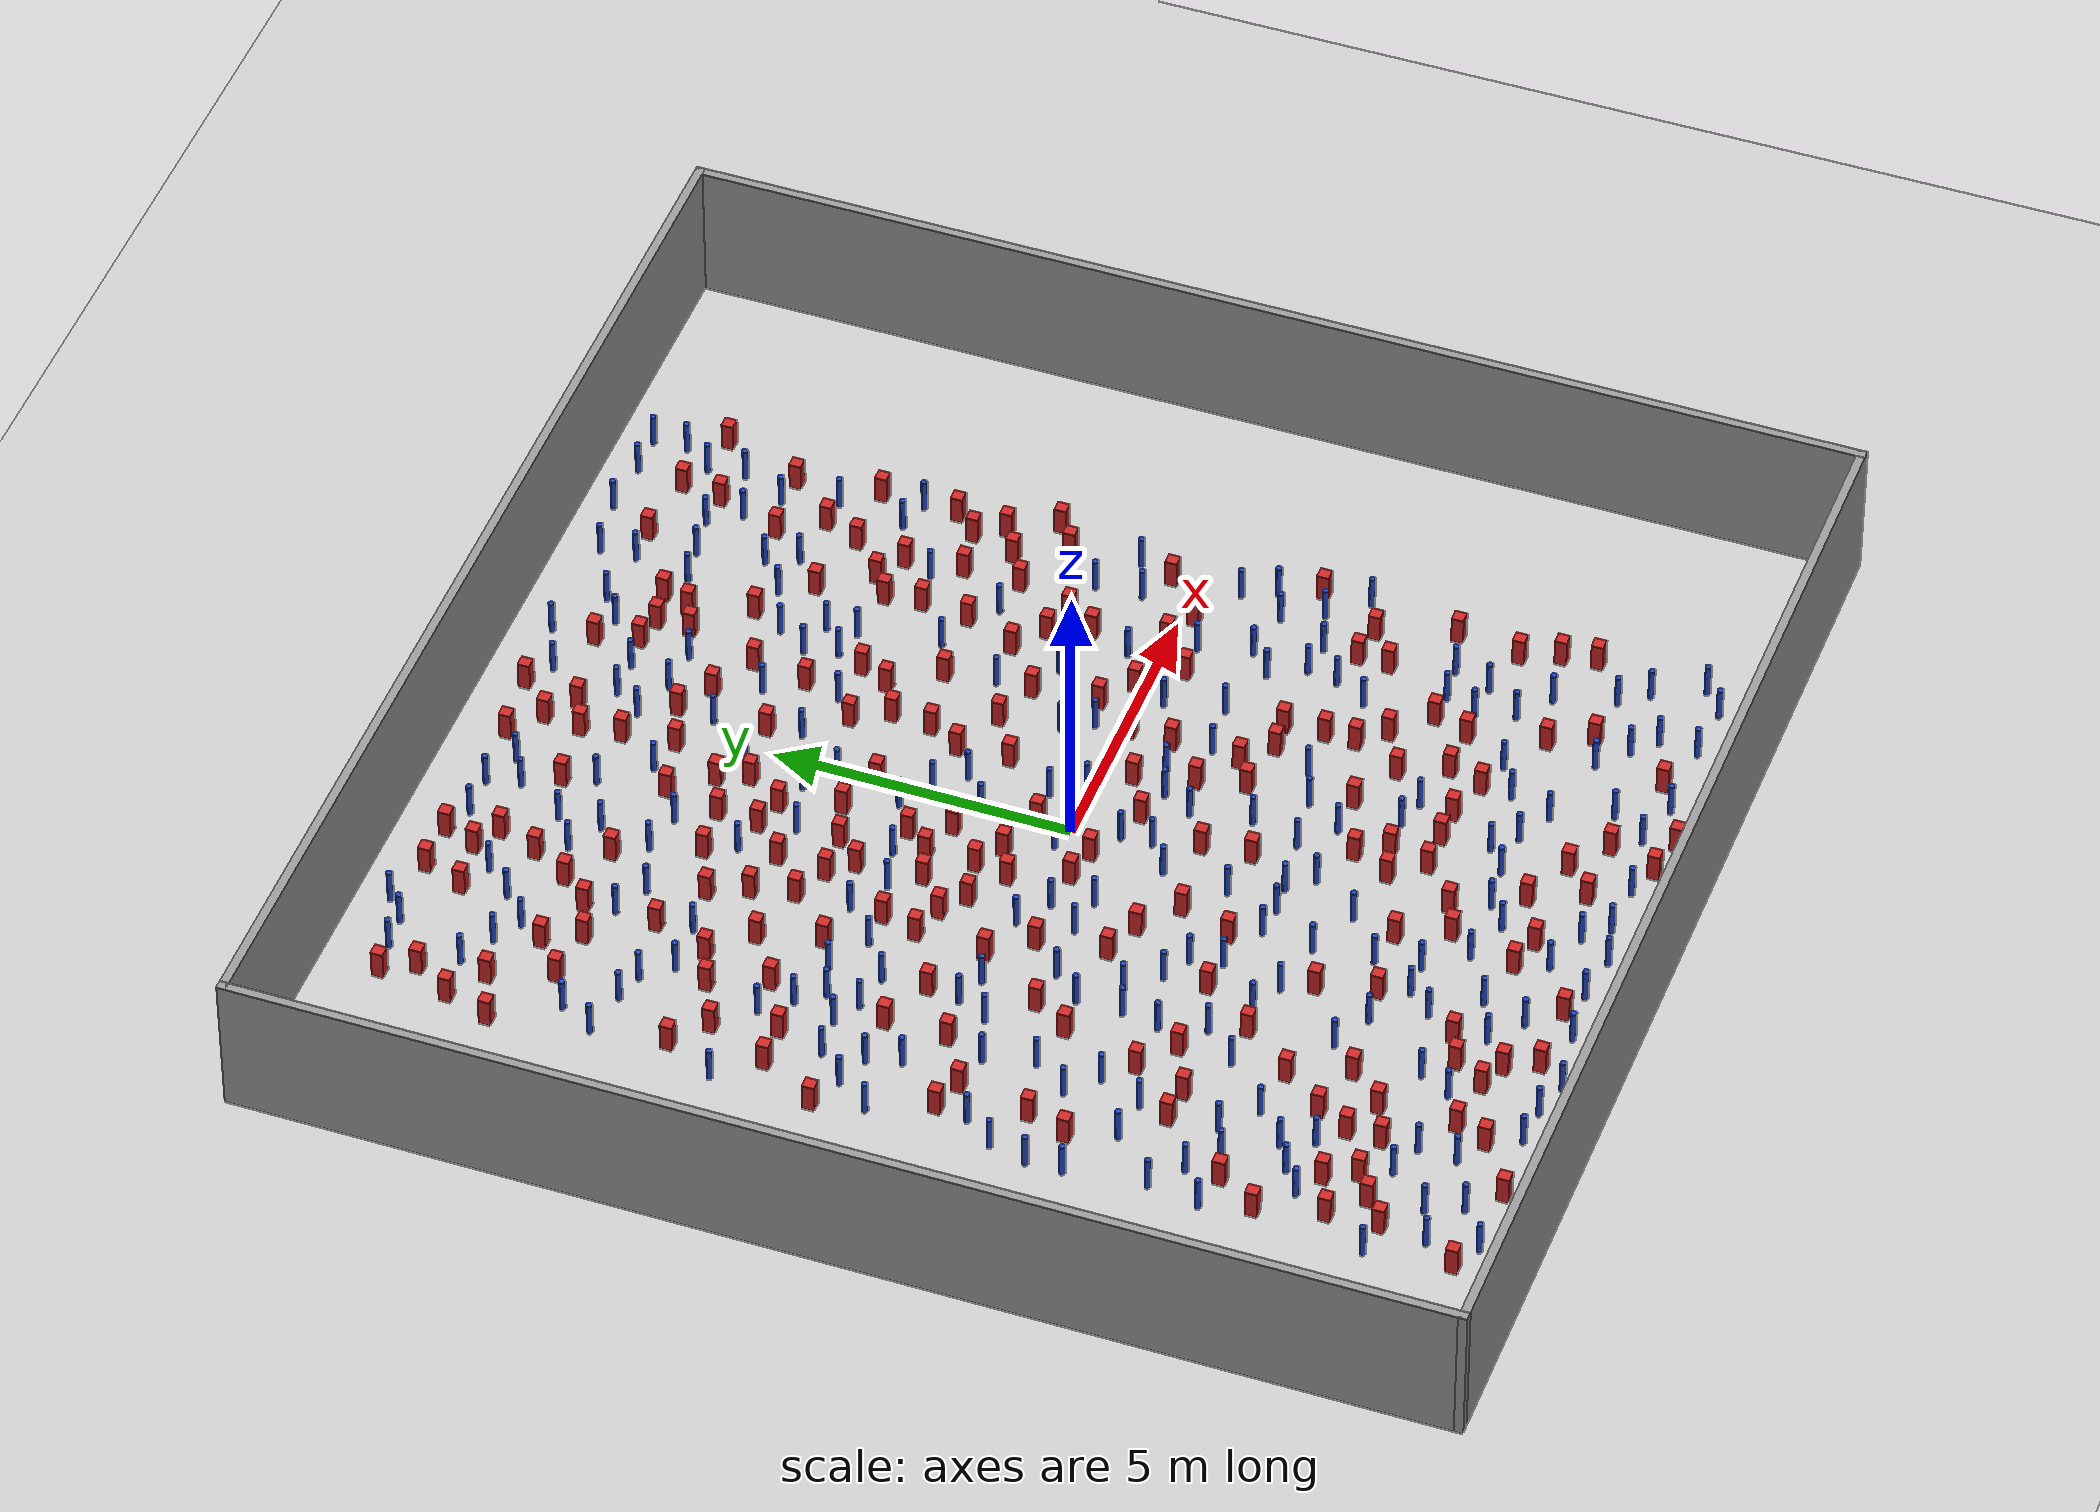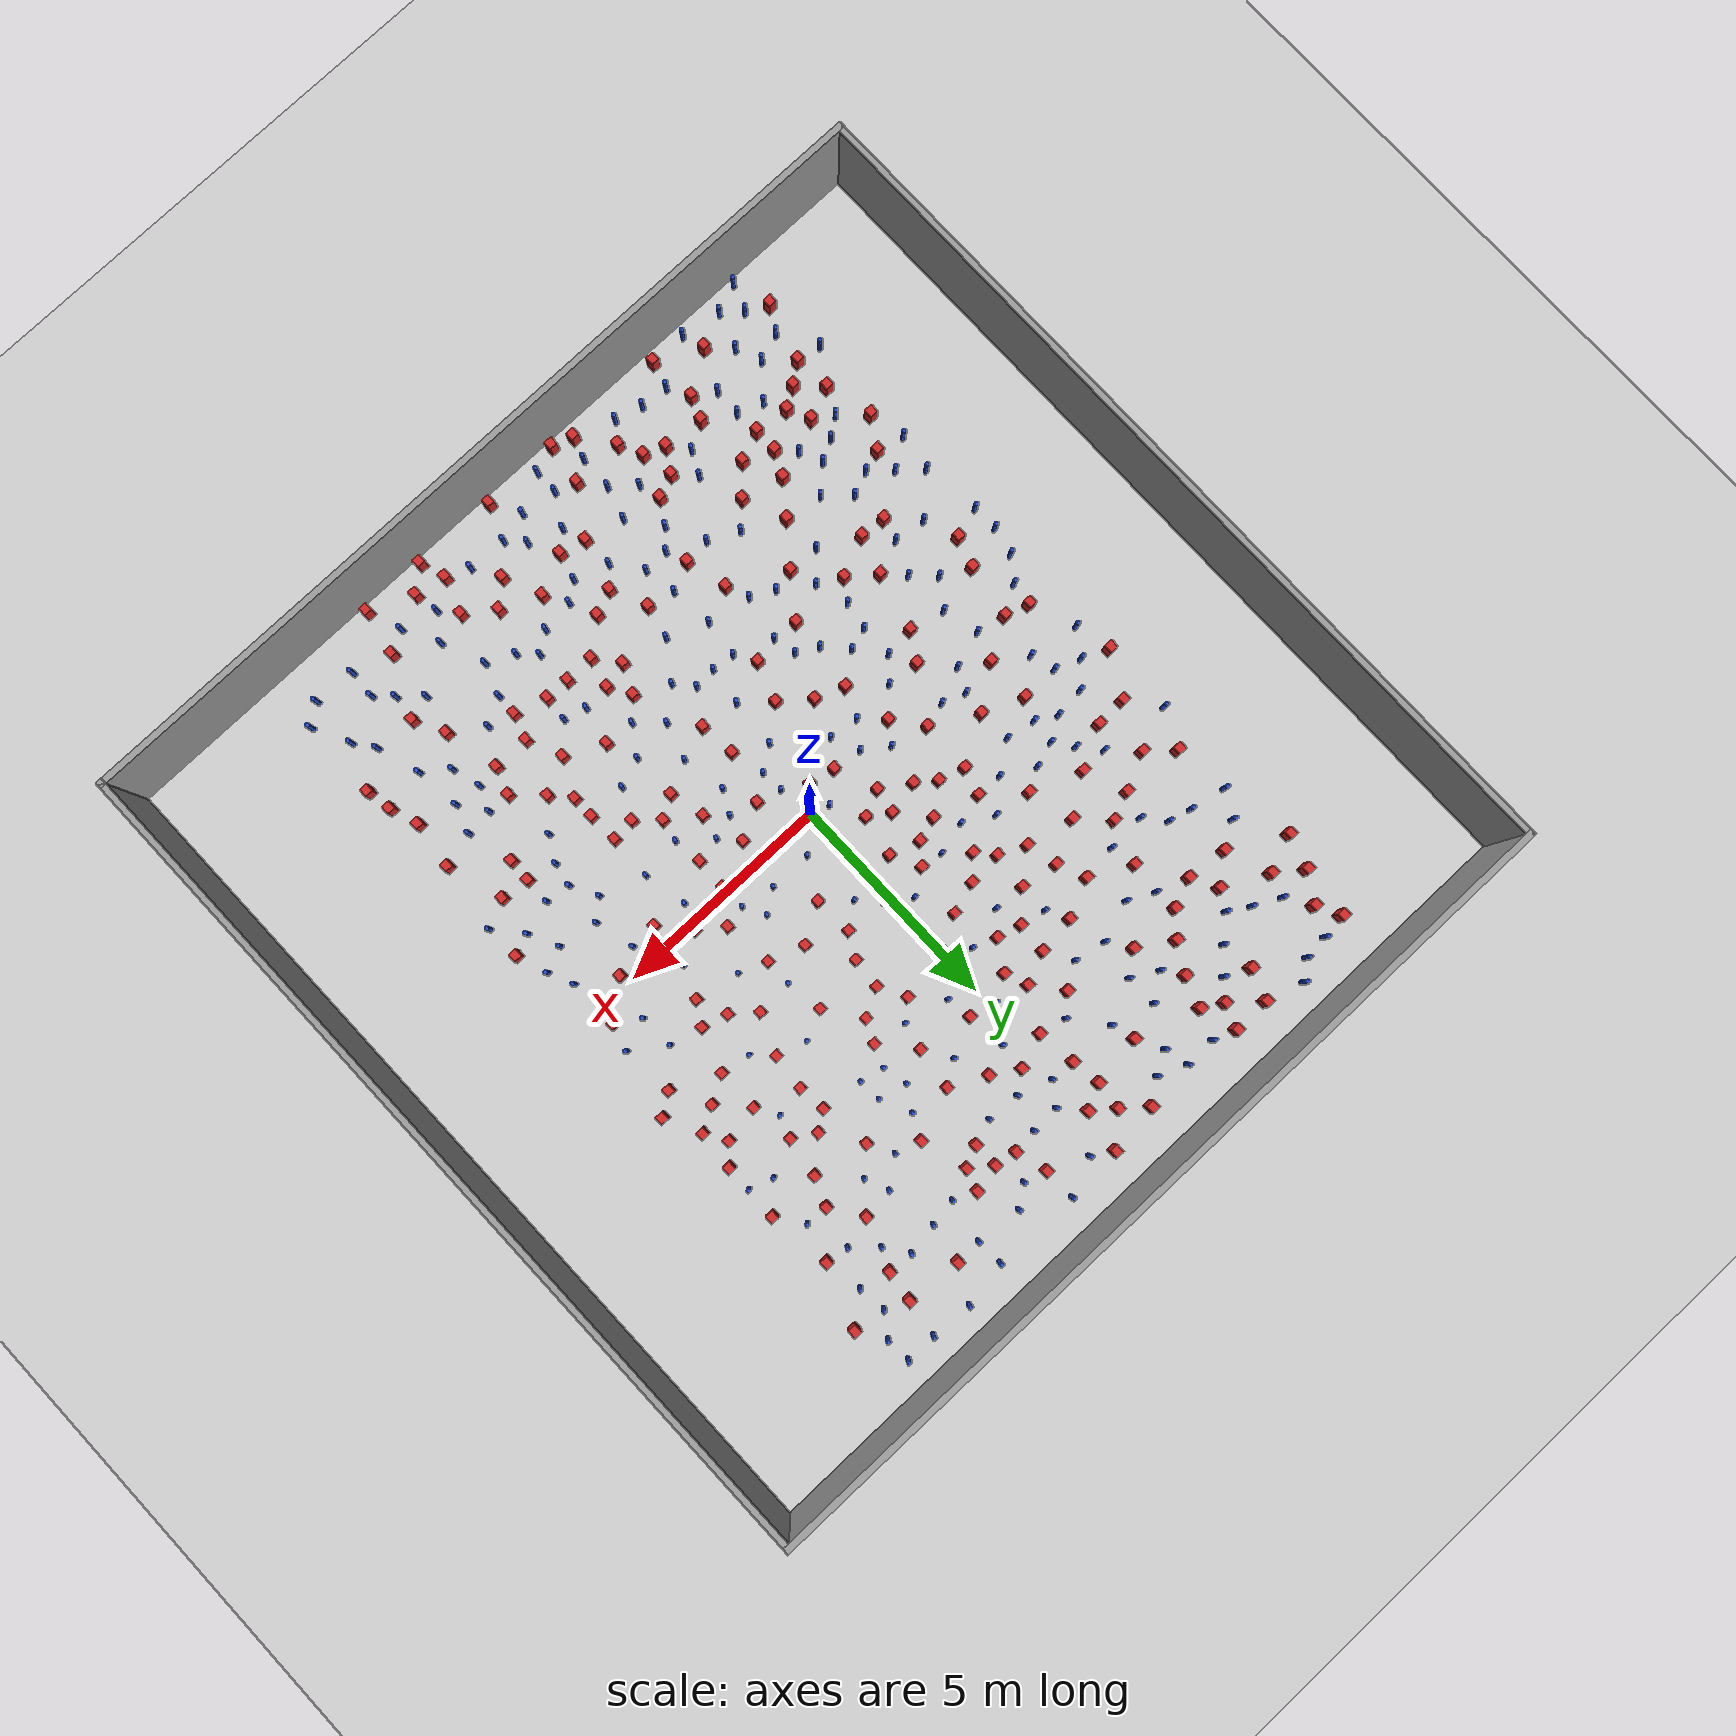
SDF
<sdf version="1.6">
 <world name="default">
  <light name="sun" type="directional">
   <pose>0 0 1000 0 -0 0</pose>
   <diffuse>0.8 0.8 0.8 1</diffuse>
   <specular>0.1 0.1 0.1 1</specular>
   <attenuation>
    <range>1000</range>
    <constant>0.9</constant>
    <linear>0.01</linear>
    <quadratic>0.001</quadratic>
   </attenuation>
   <direction>-0.5 0.5 -1</direction>
  </light>
  <model name="ground_plane">
   <static>1</static>
   <link name="link">
    <collision name="collision">
     <geometry><plane><normal>0 0 1</normal><size>100 100</size></plane></geometry>
     <surface><friction><ode><mu>100</mu><mu2>50</mu2></ode></friction></surface>
    </collision>
    <visual name="visual">
     <cast_shadows>0</cast_shadows>
     <geometry><plane><normal>0 0 1</normal><size>100 100</size></plane></geometry>
     <material>
      <ambient>1.0 1.0 1.0 1.0</ambient>
      <diffuse>0.8 0.8 0.8 1.0</diffuse>
      <specular>0.01 0.01 0.01 1.000000</specular>
     </material>
    </visual>
   </link>
  </model>
  <gravity>0 0 -9.8</gravity>
  <magnetic_field>6e-06 2.3e-05 -4.2e-05</magnetic_field>
  <atmosphere type="adiabatic"/>
  <physics name="default_physics" default="0" type="ode">
   <max_step_size>0.001</max_step_size>
   <real_time_factor>1</real_time_factor>
   <real_time_update_rate>1000</real_time_update_rate>
  </physics>
  <scene><ambient>0.4 0.4 0.4 1</ambient><background>0.7 0.7 0.7 1</background><shadows>1</shadows></scene>
  <spherical_coordinates>
   <surface_model>EARTH_WGS84</surface_model>
   <latitude_deg>0</latitude_deg>
   <longitude_deg>0</longitude_deg>
   <elevation>0</elevation>
   <heading_deg>0</heading_deg>
  </spherical_coordinates>
  <plugin name="gazebo_occupancy_map" filename="libgazebo_2Dmap_plugin.so">
   <map_resolution>0.05</map_resolution>
   <map_topic>generated_map</map_topic>
   <map_height>0.01</map_height>
   <map_size_x>50</map_size_x>
   <map_size_y>50</map_size_y>
  </plugin>
  <model name="NamedLocations">
   <static>true</static>
   <link name="DefaultStart"><pose>8.5 0 0 0 0 3.14</pose></link>
  </model>
  <model name="20x20_walls">
   <pose>0.044518 0.176112 0 0 -0 0</pose>
   <link name="Wall_1">
    <collision name="Wall_1_Collision">
     <geometry><box><size>20 0.15 2.5</size></box></geometry>
     <pose>0 0 1.25 0 -0 0</pose>
    </collision>
    <visual name="Wall_1_Visual">
     <pose>0 0 1.25 0 -0 0</pose>
     <geometry><box><size>20 0.15 2.5</size></box></geometry>
     <material>
      <script><uri>file://media/materials/scripts/gazebo.material</uri><name>Gazebo/Grey</name></script>
      <ambient>0.976471 0.992157 1 1</ambient>
     </material>
     <meta><layer>0</layer></meta>
    </visual>
    <pose>0 9.925 0 0 -0 0</pose>
   </link>
   <link name="Wall_3">
    <collision name="Wall_3_Collision">
     <geometry><box><size>20 0.15 2.5</size></box></geometry>
     <pose>0 0 1.25 0 -0 0</pose>
    </collision>
    <visual name="Wall_3_Visual">
     <pose>0 0 1.25 0 -0 0</pose>
     <geometry><box><size>20 0.15 2.5</size></box></geometry>
     <material>
      <script><uri>file://media/materials/scripts/gazebo.material</uri><name>Gazebo/Grey</name></script>
      <ambient>0.976471 0.992157 1 1</ambient>
     </material>
     <meta><layer>0</layer></meta>
    </visual>
    <pose>9.925 0 0 0 0 -1.5708</pose>
   </link>
   <link name="Wall_4">
    <collision name="Wall_4_Collision">
     <geometry><box><size>20 0.15 2.5</size></box></geometry>
     <pose>0 0 1.25 0 -0 0</pose>
    </collision>
    <visual name="Wall_4_Visual">
     <pose>0 0 1.25 0 -0 0</pose>
     <geometry><box><size>20 0.15 2.5</size></box></geometry>
     <material>
      <script><uri>file://media/materials/scripts/gazebo.material</uri><name>Gazebo/Grey</name></script>
      <ambient>0.976471 0.992157 1 1</ambient>
     </material>
     <meta><layer>0</layer></meta>
    </visual>
    <pose>0 -9.925 0 0 -0 3.14159</pose>
   </link>
   <link name="Wall_5">
    <collision name="Wall_5_Collision">
     <geometry><box><size>20 0.15 2.5</size></box></geometry>
     <pose>0 0 1.25 0 -0 0</pose>
    </collision>
    <visual name="Wall_5_Visual">
     <pose>0 0 1.25 0 -0 0</pose>
     <geometry><box><size>20 0.15 2.5</size></box></geometry>
     <material>
      <script><uri>file://media/materials/scripts/gazebo.material</uri><name>Gazebo/Grey</name></script>
      <ambient>0.976471 0.992157 1 1</ambient>
     </material>
     <meta><layer>0</layer></meta>
    </visual>
    <pose>-9.925 0 0 0 -0 1.5708</pose>
   </link>
   <static>1</static>
  </model>
  <model name="square_post_obstacle0">
   <static>true</static>
   <pose>4.83513216771 4.59395278403 1.91545236811e-07 -7.35059704564e-06 1.12565212e-07 2.39332434364e-05</pose>
   <link name="link">
    <pose>0 0 0.25 0 -0 0</pose>
    <inertial>
     <mass>100</mass>
     <inertia>
      <ixx>0.166667</ixx>
      <ixy>0</ixy>
      <ixz>0</ixz>
      <iyy>0.166667</iyy>
      <iyz>0</iyz>
      <izz>0.166667</izz>
     </inertia>
    </inertial>
    <collision name="collision"><geometry><box><size>.2 .2 .5</size></box></geometry></collision>
    <visual name="visual">
     <geometry><box><size>.2 .2 .5</size></box></geometry>
     <material>
      <script><name>Gazebo/Red</name><uri>file://media/materials/scripts/gazebo.material</uri></script>
     </material>
    </visual>
   </link>
  </model>
  <model name="square_post_obstacle1">
   <static>true</static>
   <pose>-6.75083043301 -5.38213380311 1.91545236811e-07 -7.35059704564e-06 1.12565212e-07 2.39332434364e-05</pose>
   <link name="link">
    <pose>0 0 0.25 0 -0 0</pose>
    <inertial>
     <mass>100</mass>
     <inertia>
      <ixx>0.166667</ixx>
      <ixy>0</ixy>
      <ixz>0</ixz>
      <iyy>0.166667</iyy>
      <iyz>0</iyz>
      <izz>0.166667</izz>
     </inertia>
    </inertial>
    <collision name="collision"><geometry><box><size>.2 .2 .5</size></box></geometry></collision>
    <visual name="visual">
     <geometry><box><size>.2 .2 .5</size></box></geometry>
     <material>
      <script><name>Gazebo/Red</name><uri>file://media/materials/scripts/gazebo.material</uri></script>
     </material>
    </visual>
   </link>
  </model>
  <model name="pole_obstacle0">
   <static>true</static>
   <pose>-6.44890065304 -0.653169546035 7.38925637345e-09 -8.47170692799e-08 1.24976765038e-08 -1.74513093018e-07</pose>
   <link name="link">
    <pose>0 0 0.3 0 -0 0</pose>
    <inertial>
     <mass>1</mass>
     <inertia><ixx>0.145833</ixx><ixy>0</ixy><ixz>0</ixz><iyy>0.145833</iyy><iyz>0</iyz><izz>0.125</izz></inertia>
    </inertial>
    <collision name="collision">
     <geometry><cylinder><radius>0.05</radius><length>.6</length></cylinder></geometry>
    </collision>
    <visual name="visual">
     <geometry><cylinder><radius>0.05</radius><length>.6</length></cylinder></geometry>
     <material>
      <script><name>Gazebo/Blue</name><uri>file://media/materials/scripts/gazebo.material</uri></script>
     </material>
    </visual>
   </link>
  </model>
  <model name="square_post_obstacle2">
   <static>true</static>
   <pose>-1.68983508098 7.91056205244 1.91545236811e-07 -7.35059704564e-06 1.12565212e-07 2.39332434364e-05</pose>
   <link name="link">
    <pose>0 0 0.25 0 -0 0</pose>
    <inertial>
     <mass>100</mass>
     <inertia>
      <ixx>0.166667</ixx>
      <ixy>0</ixy>
      <ixz>0</ixz>
      <iyy>0.166667</iyy>
      <iyz>0</iyz>
      <izz>0.166667</izz>
     </inertia>
    </inertial>
    <collision name="collision"><geometry><box><size>.2 .2 .5</size></box></geometry></collision>
    <visual name="visual">
     <geometry><box><size>.2 .2 .5</size></box></geometry>
     <material>
      <script><name>Gazebo/Red</name><uri>file://media/materials/scripts/gazebo.material</uri></script>
     </material>
    </visual>
   </link>
  </model>
  <model name="pole_obstacle1">
   <static>true</static>
   <pose>1.91231191744 -4.81511615944 7.38925637345e-09 -8.47170692799e-08 1.24976765033e-08 -1.74513093018e-07</pose>
   <link name="link">
    <pose>0 0 0.3 0 -0 0</pose>
    <inertial>
     <mass>1</mass>
     <inertia><ixx>0.145833</ixx><ixy>0</ixy><ixz>0</ixz><iyy>0.145833</iyy><iyz>0</iyz><izz>0.125</izz></inertia>
    </inertial>
    <collision name="collision">
     <geometry><cylinder><radius>0.05</radius><length>.6</length></cylinder></geometry>
    </collision>
    <visual name="visual">
     <geometry><cylinder><radius>0.05</radius><length>.6</length></cylinder></geometry>
     <material>
      <script><name>Gazebo/Blue</name><uri>file://media/materials/scripts/gazebo.material</uri></script>
     </material>
    </visual>
   </link>
  </model>
  <model name="square_post_obstacle3">
   <static>true</static>
   <pose>4.73159785366 -7.09271459346 1.91545236811e-07 -7.35059704564e-06 1.12565212e-07 2.39332434364e-05</pose>
   <link name="link">
    <pose>0 0 0.25 0 -0 0</pose>
    <inertial>
     <mass>100</mass>
     <inertia>
      <ixx>0.166667</ixx>
      <ixy>0</ixy>
      <ixz>0</ixz>
      <iyy>0.166667</iyy>
      <iyz>0</iyz>
      <izz>0.166667</izz>
     </inertia>
    </inertial>
    <collision name="collision"><geometry><box><size>.2 .2 .5</size></box></geometry></collision>
    <visual name="visual">
     <geometry><box><size>.2 .2 .5</size></box></geometry>
     <material>
      <script><name>Gazebo/Red</name><uri>file://media/materials/scripts/gazebo.material</uri></script>
     </material>
    </visual>
   </link>
  </model>
  <model name="pole_obstacle2">
   <static>true</static>
   <pose>3.33145633506 1.40488259142 7.38925637345e-09 -8.471706928e-08 1.24976765152e-08 -1.74513093012e-07</pose>
   <link name="link">
    <pose>0 0 0.3 0 -0 0</pose>
    <inertial>
     <mass>1</mass>
     <inertia><ixx>0.145833</ixx><ixy>0</ixy><ixz>0</ixz><iyy>0.145833</iyy><iyz>0</iyz><izz>0.125</izz></inertia>
    </inertial>
    <collision name="collision">
     <geometry><cylinder><radius>0.05</radius><length>.6</length></cylinder></geometry>
    </collision>
    <visual name="visual">
     <geometry><cylinder><radius>0.05</radius><length>.6</length></cylinder></geometry>
     <material>
      <script><name>Gazebo/Blue</name><uri>file://media/materials/scripts/gazebo.material</uri></script>
     </material>
    </visual>
   </link>
  </model>
  <model name="pole_obstacle3">
   <static>true</static>
   <pose>-3.02032872302 -5.40585776395 7.38925637345e-09 -8.47170692798e-08 1.24976765033e-08 -1.74513093019e-07</pose>
   <link name="link">
    <pose>0 0 0.3 0 -0 0</pose>
    <inertial>
     <mass>1</mass>
     <inertia><ixx>0.145833</ixx><ixy>0</ixy><ixz>0</ixz><iyy>0.145833</iyy><iyz>0</iyz><izz>0.125</izz></inertia>
    </inertial>
    <collision name="collision">
     <geometry><cylinder><radius>0.05</radius><length>.6</length></cylinder></geometry>
    </collision>
    <visual name="visual">
     <geometry><cylinder><radius>0.05</radius><length>.6</length></cylinder></geometry>
     <material>
      <script><name>Gazebo/Blue</name><uri>file://media/materials/scripts/gazebo.material</uri></script>
     </material>
    </visual>
   </link>
  </model>
  <model name="square_post_obstacle4">
   <static>true</static>
   <pose>-6.96627765335 7.05669013784 1.91545236811e-07 -7.35059704564e-06 1.12565212e-07 2.39332434364e-05</pose>
   <link name="link">
    <pose>0 0 0.25 0 -0 0</pose>
    <inertial>
     <mass>100</mass>
     <inertia>
      <ixx>0.166667</ixx>
      <ixy>0</ixy>
      <ixz>0</ixz>
      <iyy>0.166667</iyy>
      <iyz>0</iyz>
      <izz>0.166667</izz>
     </inertia>
    </inertial>
    <collision name="collision"><geometry><box><size>.2 .2 .5</size></box></geometry></collision>
    <visual name="visual">
     <geometry><box><size>.2 .2 .5</size></box></geometry>
     <material>
      <script><name>Gazebo/Red</name><uri>file://media/materials/scripts/gazebo.material</uri></script>
     </material>
    </visual>
   </link>
  </model>
  <model name="square_post_obstacle5">
   <static>true</static>
   <pose>-3.10918925905 8.37854400875 1.91545236811e-07 -7.35059704564e-06 1.12565212e-07 2.39332434364e-05</pose>
   <link name="link">
    <pose>0 0 0.25 0 -0 0</pose>
    <inertial>
     <mass>100</mass>
     <inertia>
      <ixx>0.166667</ixx>
      <ixy>0</ixy>
      <ixz>0</ixz>
      <iyy>0.166667</iyy>
      <iyz>0</iyz>
      <izz>0.166667</izz>
     </inertia>
    </inertial>
    <collision name="collision"><geometry><box><size>.2 .2 .5</size></box></geometry></collision>
    <visual name="visual">
     <geometry><box><size>.2 .2 .5</size></box></geometry>
     <material>
      <script><name>Gazebo/Red</name><uri>file://media/materials/scripts/gazebo.material</uri></script>
     </material>
    </visual>
   </link>
  </model>
  <model name="square_post_obstacle6">
   <static>true</static>
   <pose>-0.13739127547 -6.34683492645 1.91545236811e-07 -7.35059704564e-06 1.12565212e-07 2.39332434364e-05</pose>
   <link name="link">
    <pose>0 0 0.25 0 -0 0</pose>
    <inertial>
     <mass>100</mass>
     <inertia>
      <ixx>0.166667</ixx>
      <ixy>0</ixy>
      <ixz>0</ixz>
      <iyy>0.166667</iyy>
      <iyz>0</iyz>
      <izz>0.166667</izz>
     </inertia>
    </inertial>
    <collision name="collision"><geometry><box><size>.2 .2 .5</size></box></geometry></collision>
    <visual name="visual">
     <geometry><box><size>.2 .2 .5</size></box></geometry>
     <material>
      <script><name>Gazebo/Red</name><uri>file://media/materials/scripts/gazebo.material</uri></script>
     </material>
    </visual>
   </link>
  </model>
  <model name="pole_obstacle4">
   <static>true</static>
   <pose>-1.50320180323 8.76808181083 7.38925637345e-09 -8.47170692798e-08 1.24976764881e-08 -1.74513093027e-07</pose>
   <link name="link">
    <pose>0 0 0.3 0 -0 0</pose>
    <inertial>
     <mass>1</mass>
     <inertia><ixx>0.145833</ixx><ixy>0</ixy><ixz>0</ixz><iyy>0.145833</iyy><iyz>0</iyz><izz>0.125</izz></inertia>
    </inertial>
    <collision name="collision">
     <geometry><cylinder><radius>0.05</radius><length>.6</length></cylinder></geometry>
    </collision>
    <visual name="visual">
     <geometry><cylinder><radius>0.05</radius><length>.6</length></cylinder></geometry>
     <material>
      <script><name>Gazebo/Blue</name><uri>file://media/materials/scripts/gazebo.material</uri></script>
     </material>
    </visual>
   </link>
  </model>
  <model name="pole_obstacle5">
   <static>true</static>
   <pose>3.24524591812 3.37877908854 7.38925637345e-09 -8.47170692798e-08 1.24976764939e-08 -1.74513093025e-07</pose>
   <link name="link">
    <pose>0 0 0.3 0 -0 0</pose>
    <inertial>
     <mass>1</mass>
     <inertia><ixx>0.145833</ixx><ixy>0</ixy><ixz>0</ixz><iyy>0.145833</iyy><iyz>0</iyz><izz>0.125</izz></inertia>
    </inertial>
    <collision name="collision">
     <geometry><cylinder><radius>0.05</radius><length>.6</length></cylinder></geometry>
    </collision>
    <visual name="visual">
     <geometry><cylinder><radius>0.05</radius><length>.6</length></cylinder></geometry>
     <material>
      <script><name>Gazebo/Blue</name><uri>file://media/materials/scripts/gazebo.material</uri></script>
     </material>
    </visual>
   </link>
  </model>
  <model name="square_post_obstacle7">
   <static>true</static>
   <pose>-4.23166375392 -8.26234545778 1.91545236811e-07 -7.35059704564e-06 1.12565212e-07 2.39332434364e-05</pose>
   <link name="link">
    <pose>0 0 0.25 0 -0 0</pose>
    <inertial>
     <mass>100</mass>
     <inertia>
      <ixx>0.166667</ixx>
      <ixy>0</ixy>
      <ixz>0</ixz>
      <iyy>0.166667</iyy>
      <iyz>0</iyz>
      <izz>0.166667</izz>
     </inertia>
    </inertial>
    <collision name="collision"><geometry><box><size>.2 .2 .5</size></box></geometry></collision>
    <visual name="visual">
     <geometry><box><size>.2 .2 .5</size></box></geometry>
     <material>
      <script><name>Gazebo/Red</name><uri>file://media/materials/scripts/gazebo.material</uri></script>
     </material>
    </visual>
   </link>
  </model>
  <model name="square_post_obstacle8">
   <static>true</static>
   <pose>-1.27417712058 1.95908993883 1.91545236811e-07 -7.35059704564e-06 1.12565212e-07 2.39332434364e-05</pose>
   <link name="link">
    <pose>0 0 0.25 0 -0 0</pose>
    <inertial>
     <mass>100</mass>
     <inertia>
      <ixx>0.166667</ixx>
      <ixy>0</ixy>
      <ixz>0</ixz>
      <iyy>0.166667</iyy>
      <iyz>0</iyz>
      <izz>0.166667</izz>
     </inertia>
    </inertial>
    <collision name="collision"><geometry><box><size>.2 .2 .5</size></box></geometry></collision>
    <visual name="visual">
     <geometry><box><size>.2 .2 .5</size></box></geometry>
     <material>
      <script><name>Gazebo/Red</name><uri>file://media/materials/scripts/gazebo.material</uri></script>
     </material>
    </visual>
   </link>
  </model>
  <model name="pole_obstacle6">
   <static>true</static>
   <pose>6.12219689061 8.86472195481 7.38925637345e-09 -8.471706928e-08 1.24976765081e-08 -1.74513093015e-07</pose>
   <link name="link">
    <pose>0 0 0.3 0 -0 0</pose>
    <inertial>
     <mass>1</mass>
     <inertia><ixx>0.145833</ixx><ixy>0</ixy><ixz>0</ixz><iyy>0.145833</iyy><iyz>0</iyz><izz>0.125</izz></inertia>
    </inertial>
    <collision name="collision">
     <geometry><cylinder><radius>0.05</radius><length>.6</length></cylinder></geometry>
    </collision>
    <visual name="visual">
     <geometry><cylinder><radius>0.05</radius><length>.6</length></cylinder></geometry>
     <material>
      <script><name>Gazebo/Blue</name><uri>file://media/materials/scripts/gazebo.material</uri></script>
     </material>
    </visual>
   </link>
  </model>
  <model name="pole_obstacle7">
   <static>true</static>
   <pose>-6.93572072231 3.38075076219 7.38925637345e-09 -8.47170692798e-08 1.24976764937e-08 -1.74513093023e-07</pose>
   <link name="link">
    <pose>0 0 0.3 0 -0 0</pose>
    <inertial>
     <mass>1</mass>
     <inertia><ixx>0.145833</ixx><ixy>0</ixy><ixz>0</ixz><iyy>0.145833</iyy><iyz>0</iyz><izz>0.125</izz></inertia>
    </inertial>
    <collision name="collision">
     <geometry><cylinder><radius>0.05</radius><length>.6</length></cylinder></geometry>
    </collision>
    <visual name="visual">
     <geometry><cylinder><radius>0.05</radius><length>.6</length></cylinder></geometry>
     <material>
      <script><name>Gazebo/Blue</name><uri>file://media/materials/scripts/gazebo.material</uri></script>
     </material>
    </visual>
   </link>
  </model>
  <model name="square_post_obstacle9">
   <static>true</static>
   <pose>-0.999931024113 -0.356850673419 1.91545236811e-07 -7.35059704564e-06 1.12565212e-07 2.39332434364e-05</pose>
   <link name="link">
    <pose>0 0 0.25 0 -0 0</pose>
    <inertial>
     <mass>100</mass>
     <inertia>
      <ixx>0.166667</ixx>
      <ixy>0</ixy>
      <ixz>0</ixz>
      <iyy>0.166667</iyy>
      <iyz>0</iyz>
      <izz>0.166667</izz>
     </inertia>
    </inertial>
    <collision name="collision"><geometry><box><size>.2 .2 .5</size></box></geometry></collision>
    <visual name="visual">
     <geometry><box><size>.2 .2 .5</size></box></geometry>
     <material>
      <script><name>Gazebo/Red</name><uri>file://media/materials/scripts/gazebo.material</uri></script>
     </material>
    </visual>
   </link>
  </model>
  <model name="square_post_obstacle10">
   <static>true</static>
   <pose>-6.82751068562 -8.61218475664 1.91545236811e-07 -7.35059704564e-06 1.12565212e-07 2.39332434364e-05</pose>
   <link name="link">
    <pose>0 0 0.25 0 -0 0</pose>
    <inertial>
     <mass>100</mass>
     <inertia>
      <ixx>0.166667</ixx>
      <ixy>0</ixy>
      <ixz>0</ixz>
      <iyy>0.166667</iyy>
      <iyz>0</iyz>
      <izz>0.166667</izz>
     </inertia>
    </inertial>
    <collision name="collision"><geometry><box><size>.2 .2 .5</size></box></geometry></collision>
    <visual name="visual">
     <geometry><box><size>.2 .2 .5</size></box></geometry>
     <material>
      <script><name>Gazebo/Red</name><uri>file://media/materials/scripts/gazebo.material</uri></script>
     </material>
    </visual>
   </link>
  </model>
  <model name="square_post_obstacle11">
   <static>true</static>
   <pose>-3.56252976413 8.64841808031 1.91545236811e-07 -7.35059704564e-06 1.12565212e-07 2.39332434364e-05</pose>
   <link name="link">
    <pose>0 0 0.25 0 -0 0</pose>
    <inertial>
     <mass>100</mass>
     <inertia>
      <ixx>0.166667</ixx>
      <ixy>0</ixy>
      <ixz>0</ixz>
      <iyy>0.166667</iyy>
      <iyz>0</iyz>
      <izz>0.166667</izz>
     </inertia>
    </inertial>
    <collision name="collision"><geometry><box><size>.2 .2 .5</size></box></geometry></collision>
    <visual name="visual">
     <geometry><box><size>.2 .2 .5</size></box></geometry>
     <material>
      <script><name>Gazebo/Red</name><uri>file://media/materials/scripts/gazebo.material</uri></script>
     </material>
    </visual>
   </link>
  </model>
  <model name="square_post_obstacle12">
   <static>true</static>
   <pose>-3.26608829545 4.85899182466 1.91545236811e-07 -7.35059704564e-06 1.12565212e-07 2.39332434364e-05</pose>
   <link name="link">
    <pose>0 0 0.25 0 -0 0</pose>
    <inertial>
     <mass>100</mass>
     <inertia>
      <ixx>0.166667</ixx>
      <ixy>0</ixy>
      <ixz>0</ixz>
      <iyy>0.166667</iyy>
      <iyz>0</iyz>
      <izz>0.166667</izz>
     </inertia>
    </inertial>
    <collision name="collision"><geometry><box><size>.2 .2 .5</size></box></geometry></collision>
    <visual name="visual">
     <geometry><box><size>.2 .2 .5</size></box></geometry>
     <material>
      <script><name>Gazebo/Red</name><uri>file://media/materials/scripts/gazebo.material</uri></script>
     </material>
    </visual>
   </link>
  </model>
  <model name="square_post_obstacle13">
   <static>true</static>
   <pose>-6.30400001628 8.47020350388 1.91545236811e-07 -7.35059704564e-06 1.12565212e-07 2.39332434364e-05</pose>
   <link name="link">
    <pose>0 0 0.25 0 -0 0</pose>
    <inertial>
     <mass>100</mass>
     <inertia>
      <ixx>0.166667</ixx>
      <ixy>0</ixy>
      <ixz>0</ixz>
      <iyy>0.166667</iyy>
      <iyz>0</iyz>
      <izz>0.166667</izz>
     </inertia>
    </inertial>
    <collision name="collision"><geometry><box><size>.2 .2 .5</size></box></geometry></collision>
    <visual name="visual">
     <geometry><box><size>.2 .2 .5</size></box></geometry>
     <material>
      <script><name>Gazebo/Red</name><uri>file://media/materials/scripts/gazebo.material</uri></script>
     </material>
    </visual>
   </link>
  </model>
  <model name="pole_obstacle8">
   <static>true</static>
   <pose>-0.579959619496 -3.61079927876 7.38925637345e-09 -8.47170692799e-08 1.2497676509e-08 -1.74513093016e-07</pose>
   <link name="link">
    <pose>0 0 0.3 0 -0 0</pose>
    <inertial>
     <mass>1</mass>
     <inertia><ixx>0.145833</ixx><ixy>0</ixy><ixz>0</ixz><iyy>0.145833</iyy><iyz>0</iyz><izz>0.125</izz></inertia>
    </inertial>
    <collision name="collision">
     <geometry><cylinder><radius>0.05</radius><length>.6</length></cylinder></geometry>
    </collision>
    <visual name="visual">
     <geometry><cylinder><radius>0.05</radius><length>.6</length></cylinder></geometry>
     <material>
      <script><name>Gazebo/Blue</name><uri>file://media/materials/scripts/gazebo.material</uri></script>
     </material>
    </visual>
   </link>
  </model>
  <model name="square_post_obstacle14">
   <static>true</static>
   <pose>-0.540769029304 8.05975475721 1.91545236811e-07 -7.35059704564e-06 1.12565212e-07 2.39332434364e-05</pose>
   <link name="link">
    <pose>0 0 0.25 0 -0 0</pose>
    <inertial>
     <mass>100</mass>
     <inertia>
      <ixx>0.166667</ixx>
      <ixy>0</ixy>
      <ixz>0</ixz>
      <iyy>0.166667</iyy>
      <iyz>0</iyz>
      <izz>0.166667</izz>
     </inertia>
    </inertial>
    <collision name="collision"><geometry><box><size>.2 .2 .5</size></box></geometry></collision>
    <visual name="visual">
     <geometry><box><size>.2 .2 .5</size></box></geometry>
     <material>
      <script><name>Gazebo/Red</name><uri>file://media/materials/scripts/gazebo.material</uri></script>
     </material>
    </visual>
   </link>
  </model>
  <model name="square_post_obstacle15">
   <static>true</static>
   <pose>3.35773666967 -3.5634429944 1.91545236811e-07 -7.35059704564e-06 1.12565212e-07 2.39332434364e-05</pose>
   <link name="link">
    <pose>0 0 0.25 0 -0 0</pose>
    <inertial>
     <mass>100</mass>
     <inertia>
      <ixx>0.166667</ixx>
      <ixy>0</ixy>
      <ixz>0</ixz>
      <iyy>0.166667</iyy>
      <iyz>0</iyz>
      <izz>0.166667</izz>
     </inertia>
    </inertial>
    <collision name="collision"><geometry><box><size>.2 .2 .5</size></box></geometry></collision>
    <visual name="visual">
     <geometry><box><size>.2 .2 .5</size></box></geometry>
     <material>
      <script><name>Gazebo/Red</name><uri>file://media/materials/scripts/gazebo.material</uri></script>
     </material>
    </visual>
   </link>
  </model>
  <model name="square_post_obstacle16">
   <static>true</static>
   <pose>-5.514271623 -6.67150716408 1.91545236811e-07 -7.35059704564e-06 1.12565212e-07 2.39332434364e-05</pose>
   <link name="link">
    <pose>0 0 0.25 0 -0 0</pose>
    <inertial>
     <mass>100</mass>
     <inertia>
      <ixx>0.166667</ixx>
      <ixy>0</ixy>
      <ixz>0</ixz>
      <iyy>0.166667</iyy>
      <iyz>0</iyz>
      <izz>0.166667</izz>
     </inertia>
    </inertial>
    <collision name="collision"><geometry><box><size>.2 .2 .5</size></box></geometry></collision>
    <visual name="visual">
     <geometry><box><size>.2 .2 .5</size></box></geometry>
     <material>
      <script><name>Gazebo/Red</name><uri>file://media/materials/scripts/gazebo.material</uri></script>
     </material>
    </visual>
   </link>
  </model>
  <model name="pole_obstacle9">
   <static>true</static>
   <pose>6.38871355825 -8.41698231804 7.38925637345e-09 -8.471706928e-08 1.24976765081e-08 -1.74513093015e-07</pose>
   <link name="link">
    <pose>0 0 0.3 0 -0 0</pose>
    <inertial>
     <mass>1</mass>
     <inertia><ixx>0.145833</ixx><ixy>0</ixy><ixz>0</ixz><iyy>0.145833</iyy><iyz>0</iyz><izz>0.125</izz></inertia>
    </inertial>
    <collision name="collision">
     <geometry><cylinder><radius>0.05</radius><length>.6</length></cylinder></geometry>
    </collision>
    <visual name="visual">
     <geometry><cylinder><radius>0.05</radius><length>.6</length></cylinder></geometry>
     <material>
      <script><name>Gazebo/Blue</name><uri>file://media/materials/scripts/gazebo.material</uri></script>
     </material>
    </visual>
   </link>
  </model>
  <model name="square_post_obstacle17">
   <static>true</static>
   <pose>0.711872368163 -4.99060453869 1.91545236811e-07 -7.35059704564e-06 1.12565212e-07 2.39332434364e-05</pose>
   <link name="link">
    <pose>0 0 0.25 0 -0 0</pose>
    <inertial>
     <mass>100</mass>
     <inertia>
      <ixx>0.166667</ixx>
      <ixy>0</ixy>
      <ixz>0</ixz>
      <iyy>0.166667</iyy>
      <iyz>0</iyz>
      <izz>0.166667</izz>
     </inertia>
    </inertial>
    <collision name="collision"><geometry><box><size>.2 .2 .5</size></box></geometry></collision>
    <visual name="visual">
     <geometry><box><size>.2 .2 .5</size></box></geometry>
     <material>
      <script><name>Gazebo/Red</name><uri>file://media/materials/scripts/gazebo.material</uri></script>
     </material>
    </visual>
   </link>
  </model>
  <model name="square_post_obstacle18">
   <static>true</static>
   <pose>1.65763689313 -1.4866116556 1.91545236811e-07 -7.35059704564e-06 1.12565212e-07 2.39332434364e-05</pose>
   <link name="link">
    <pose>0 0 0.25 0 -0 0</pose>
    <inertial>
     <mass>100</mass>
     <inertia>
      <ixx>0.166667</ixx>
      <ixy>0</ixy>
      <ixz>0</ixz>
      <iyy>0.166667</iyy>
      <iyz>0</iyz>
      <izz>0.166667</izz>
     </inertia>
    </inertial>
    <collision name="collision"><geometry><box><size>.2 .2 .5</size></box></geometry></collision>
    <visual name="visual">
     <geometry><box><size>.2 .2 .5</size></box></geometry>
     <material>
      <script><name>Gazebo/Red</name><uri>file://media/materials/scripts/gazebo.material</uri></script>
     </material>
    </visual>
   </link>
  </model>
  <model name="pole_obstacle10">
   <static>true</static>
   <pose>-6.65671681823 5.46702779641 7.38925637345e-09 -8.47170692796e-08 1.24976764786e-08 -1.74513093032e-07</pose>
   <link name="link">
    <pose>0 0 0.3 0 -0 0</pose>
    <inertial>
     <mass>1</mass>
     <inertia><ixx>0.145833</ixx><ixy>0</ixy><ixz>0</ixz><iyy>0.145833</iyy><iyz>0</iyz><izz>0.125</izz></inertia>
    </inertial>
    <collision name="collision">
     <geometry><cylinder><radius>0.05</radius><length>.6</length></cylinder></geometry>
    </collision>
    <visual name="visual">
     <geometry><cylinder><radius>0.05</radius><length>.6</length></cylinder></geometry>
     <material>
      <script><name>Gazebo/Blue</name><uri>file://media/materials/scripts/gazebo.material</uri></script>
     </material>
    </visual>
   </link>
  </model>
  <model name="square_post_obstacle19">
   <static>true</static>
   <pose>-6.37829685578 -0.122280241923 1.91545236811e-07 -7.35059704564e-06 1.12565212e-07 2.39332434364e-05</pose>
   <link name="link">
    <pose>0 0 0.25 0 -0 0</pose>
    <inertial>
     <mass>100</mass>
     <inertia>
      <ixx>0.166667</ixx>
      <ixy>0</ixy>
      <ixz>0</ixz>
      <iyy>0.166667</iyy>
      <iyz>0</iyz>
      <izz>0.166667</izz>
     </inertia>
    </inertial>
    <collision name="collision"><geometry><box><size>.2 .2 .5</size></box></geometry></collision>
    <visual name="visual">
     <geometry><box><size>.2 .2 .5</size></box></geometry>
     <material>
      <script><name>Gazebo/Red</name><uri>file://media/materials/scripts/gazebo.material</uri></script>
     </material>
    </visual>
   </link>
  </model>
  <model name="pole_obstacle11">
   <static>true</static>
   <pose>-0.0424949494299 1.49185777286 7.38925637345e-09 -8.47170692798e-08 1.24976765005e-08 -1.7451309302e-07</pose>
   <link name="link">
    <pose>0 0 0.3 0 -0 0</pose>
    <inertial>
     <mass>1</mass>
     <inertia><ixx>0.145833</ixx><ixy>0</ixy><ixz>0</ixz><iyy>0.145833</iyy><iyz>0</iyz><izz>0.125</izz></inertia>
    </inertial>
    <collision name="collision">
     <geometry><cylinder><radius>0.05</radius><length>.6</length></cylinder></geometry>
    </collision>
    <visual name="visual">
     <geometry><cylinder><radius>0.05</radius><length>.6</length></cylinder></geometry>
     <material>
      <script><name>Gazebo/Blue</name><uri>file://media/materials/scripts/gazebo.material</uri></script>
     </material>
    </visual>
   </link>
  </model>
  <model name="square_post_obstacle20">
   <static>true</static>
   <pose>4.97758653991 5.47218143391 1.91545236811e-07 -7.35059704564e-06 1.12565212e-07 2.39332434364e-05</pose>
   <link name="link">
    <pose>0 0 0.25 0 -0 0</pose>
    <inertial>
     <mass>100</mass>
     <inertia>
      <ixx>0.166667</ixx>
      <ixy>0</ixy>
      <ixz>0</ixz>
      <iyy>0.166667</iyy>
      <iyz>0</iyz>
      <izz>0.166667</izz>
     </inertia>
    </inertial>
    <collision name="collision"><geometry><box><size>.2 .2 .5</size></box></geometry></collision>
    <visual name="visual">
     <geometry><box><size>.2 .2 .5</size></box></geometry>
     <material>
      <script><name>Gazebo/Red</name><uri>file://media/materials/scripts/gazebo.material</uri></script>
     </material>
    </visual>
   </link>
  </model>
  <model name="pole_obstacle12">
   <static>true</static>
   <pose>-0.456745542418 -2.75892908312 7.38925637345e-09 -8.471706928e-08 1.24976765163e-08 -1.74513093012e-07</pose>
   <link name="link">
    <pose>0 0 0.3 0 -0 0</pose>
    <inertial>
     <mass>1</mass>
     <inertia><ixx>0.145833</ixx><ixy>0</ixy><ixz>0</ixz><iyy>0.145833</iyy><iyz>0</iyz><izz>0.125</izz></inertia>
    </inertial>
    <collision name="collision">
     <geometry><cylinder><radius>0.05</radius><length>.6</length></cylinder></geometry>
    </collision>
    <visual name="visual">
     <geometry><cylinder><radius>0.05</radius><length>.6</length></cylinder></geometry>
     <material>
      <script><name>Gazebo/Blue</name><uri>file://media/materials/scripts/gazebo.material</uri></script>
     </material>
    </visual>
   </link>
  </model>
  <model name="square_post_obstacle21">
   <static>true</static>
   <pose>-4.16433848893 6.54994403118 1.91545236811e-07 -7.35059704564e-06 1.12565212e-07 2.39332434364e-05</pose>
   <link name="link">
    <pose>0 0 0.25 0 -0 0</pose>
    <inertial>
     <mass>100</mass>
     <inertia>
      <ixx>0.166667</ixx>
      <ixy>0</ixy>
      <ixz>0</ixz>
      <iyy>0.166667</iyy>
      <iyz>0</iyz>
      <izz>0.166667</izz>
     </inertia>
    </inertial>
    <collision name="collision"><geometry><box><size>.2 .2 .5</size></box></geometry></collision>
    <visual name="visual">
     <geometry><box><size>.2 .2 .5</size></box></geometry>
     <material>
      <script><name>Gazebo/Red</name><uri>file://media/materials/scripts/gazebo.material</uri></script>
     </material>
    </visual>
   </link>
  </model>
  <model name="pole_obstacle13">
   <static>true</static>
   <pose>2.96933460274 5.23645730006 7.38925637345e-09 -8.47170692798e-08 1.24976765033e-08 -1.74513093019e-07</pose>
   <link name="link">
    <pose>0 0 0.3 0 -0 0</pose>
    <inertial>
     <mass>1</mass>
     <inertia><ixx>0.145833</ixx><ixy>0</ixy><ixz>0</ixz><iyy>0.145833</iyy><iyz>0</iyz><izz>0.125</izz></inertia>
    </inertial>
    <collision name="collision">
     <geometry><cylinder><radius>0.05</radius><length>.6</length></cylinder></geometry>
    </collision>
    <visual name="visual">
     <geometry><cylinder><radius>0.05</radius><length>.6</length></cylinder></geometry>
     <material>
      <script><name>Gazebo/Blue</name><uri>file://media/materials/scripts/gazebo.material</uri></script>
     </material>
    </visual>
   </link>
  </model>
  <model name="square_post_obstacle22">
   <static>true</static>
   <pose>2.27502093735 4.36059536365 1.91545236811e-07 -7.35059704564e-06 1.12565212e-07 2.39332434364e-05</pose>
   <link name="link">
    <pose>0 0 0.25 0 -0 0</pose>
    <inertial>
     <mass>100</mass>
     <inertia>
      <ixx>0.166667</ixx>
      <ixy>0</ixy>
      <ixz>0</ixz>
      <iyy>0.166667</iyy>
      <iyz>0</iyz>
      <izz>0.166667</izz>
     </inertia>
    </inertial>
    <collision name="collision"><geometry><box><size>.2 .2 .5</size></box></geometry></collision>
    <visual name="visual">
     <geometry><box><size>.2 .2 .5</size></box></geometry>
     <material>
      <script><name>Gazebo/Red</name><uri>file://media/materials/scripts/gazebo.material</uri></script>
     </material>
    </visual>
   </link>
  </model>
  <model name="pole_obstacle14">
   <static>true</static>
   <pose>-4.94699547819 4.71956309399 7.38925637345e-09 -8.47170692796e-08 1.24976764786e-08 -1.74513093032e-07</pose>
   <link name="link">
    <pose>0 0 0.3 0 -0 0</pose>
    <inertial>
     <mass>1</mass>
     <inertia><ixx>0.145833</ixx><ixy>0</ixy><ixz>0</ixz><iyy>0.145833</iyy><iyz>0</iyz><izz>0.125</izz></inertia>
    </inertial>
    <collision name="collision">
     <geometry><cylinder><radius>0.05</radius><length>.6</length></cylinder></geometry>
    </collision>
    <visual name="visual">
     <geometry><cylinder><radius>0.05</radius><length>.6</length></cylinder></geometry>
     <material>
      <script><name>Gazebo/Blue</name><uri>file://media/materials/scripts/gazebo.material</uri></script>
     </material>
    </visual>
   </link>
  </model>
  <model name="pole_obstacle15">
   <static>true</static>
   <pose>-5.26758257116 -3.02592980464 7.38925637345e-09 -8.47170692798e-08 1.24976764937e-08 -1.74513093023e-07</pose>
   <link name="link">
    <pose>0 0 0.3 0 -0 0</pose>
    <inertial>
     <mass>1</mass>
     <inertia><ixx>0.145833</ixx><ixy>0</ixy><ixz>0</ixz><iyy>0.145833</iyy><iyz>0</iyz><izz>0.125</izz></inertia>
    </inertial>
    <collision name="collision">
     <geometry><cylinder><radius>0.05</radius><length>.6</length></cylinder></geometry>
    </collision>
    <visual name="visual">
     <geometry><cylinder><radius>0.05</radius><length>.6</length></cylinder></geometry>
     <material>
      <script><name>Gazebo/Blue</name><uri>file://media/materials/scripts/gazebo.material</uri></script>
     </material>
    </visual>
   </link>
  </model>
  <model name="pole_obstacle16">
   <static>true</static>
   <pose>4.60572323333 7.94365654591 7.38925637345e-09 -8.47170692796e-08 1.24976764786e-08 -1.74513093032e-07</pose>
   <link name="link">
    <pose>0 0 0.3 0 -0 0</pose>
    <inertial>
     <mass>1</mass>
     <inertia><ixx>0.145833</ixx><ixy>0</ixy><ixz>0</ixz><iyy>0.145833</iyy><iyz>0</iyz><izz>0.125</izz></inertia>
    </inertial>
    <collision name="collision">
     <geometry><cylinder><radius>0.05</radius><length>.6</length></cylinder></geometry>
    </collision>
    <visual name="visual">
     <geometry><cylinder><radius>0.05</radius><length>.6</length></cylinder></geometry>
     <material>
      <script><name>Gazebo/Blue</name><uri>file://media/materials/scripts/gazebo.material</uri></script>
     </material>
    </visual>
   </link>
  </model>
  <model name="square_post_obstacle23">
   <static>true</static>
   <pose>2.10180651756 -3.97057028613 1.91545236811e-07 -7.35059704564e-06 1.12565212e-07 2.39332434364e-05</pose>
   <link name="link">
    <pose>0 0 0.25 0 -0 0</pose>
    <inertial>
     <mass>100</mass>
     <inertia>
      <ixx>0.166667</ixx>
      <ixy>0</ixy>
      <ixz>0</ixz>
      <iyy>0.166667</iyy>
      <iyz>0</iyz>
      <izz>0.166667</izz>
     </inertia>
    </inertial>
    <collision name="collision"><geometry><box><size>.2 .2 .5</size></box></geometry></collision>
    <visual name="visual">
     <geometry><box><size>.2 .2 .5</size></box></geometry>
     <material>
      <script><name>Gazebo/Red</name><uri>file://media/materials/scripts/gazebo.material</uri></script>
     </material>
    </visual>
   </link>
  </model>
  <model name="pole_obstacle17">
   <static>true</static>
   <pose>-0.980800262821 -6.12792224462 7.38925637345e-09 -8.47170692799e-08 1.2497676509e-08 -1.74513093015e-07</pose>
   <link name="link">
    <pose>0 0 0.3 0 -0 0</pose>
    <inertial>
     <mass>1</mass>
     <inertia><ixx>0.145833</ixx><ixy>0</ixy><ixz>0</ixz><iyy>0.145833</iyy><iyz>0</iyz><izz>0.125</izz></inertia>
    </inertial>
    <collision name="collision">
     <geometry><cylinder><radius>0.05</radius><length>.6</length></cylinder></geometry>
    </collision>
    <visual name="visual">
     <geometry><cylinder><radius>0.05</radius><length>.6</length></cylinder></geometry>
     <material>
      <script><name>Gazebo/Blue</name><uri>file://media/materials/scripts/gazebo.material</uri></script>
     </material>
    </visual>
   </link>
  </model>
  <model name="square_post_obstacle24">
   <static>true</static>
   <pose>0.163014172727 9.27936629581 1.91545236811e-07 -7.35059704564e-06 1.12565212e-07 2.39332434364e-05</pose>
   <link name="link">
    <pose>0 0 0.25 0 -0 0</pose>
    <inertial>
     <mass>100</mass>
     <inertia>
      <ixx>0.166667</ixx>
      <ixy>0</ixy>
      <ixz>0</ixz>
      <iyy>0.166667</iyy>
      <iyz>0</iyz>
      <izz>0.166667</izz>
     </inertia>
    </inertial>
    <collision name="collision"><geometry><box><size>.2 .2 .5</size></box></geometry></collision>
    <visual name="visual">
     <geometry><box><size>.2 .2 .5</size></box></geometry>
     <material>
      <script><name>Gazebo/Red</name><uri>file://media/materials/scripts/gazebo.material</uri></script>
     </material>
    </visual>
   </link>
  </model>
  <model name="square_post_obstacle25">
   <static>true</static>
   <pose>-2.23684656271 3.26121554226 1.91545236811e-07 -7.35059704564e-06 1.12565212e-07 2.39332434364e-05</pose>
   <link name="link">
    <pose>0 0 0.25 0 -0 0</pose>
    <inertial>
     <mass>100</mass>
     <inertia>
      <ixx>0.166667</ixx>
      <ixy>0</ixy>
      <ixz>0</ixz>
      <iyy>0.166667</iyy>
      <iyz>0</iyz>
      <izz>0.166667</izz>
     </inertia>
    </inertial>
    <collision name="collision"><geometry><box><size>.2 .2 .5</size></box></geometry></collision>
    <visual name="visual">
     <geometry><box><size>.2 .2 .5</size></box></geometry>
     <material>
      <script><name>Gazebo/Red</name><uri>file://media/materials/scripts/gazebo.material</uri></script>
     </material>
    </visual>
   </link>
  </model>
  <model name="square_post_obstacle26">
   <static>true</static>
   <pose>1.79584075335 6.01691367408 1.91545236811e-07 -7.35059704564e-06 1.12565212e-07 2.39332434364e-05</pose>
   <link name="link">
    <pose>0 0 0.25 0 -0 0</pose>
    <inertial>
     <mass>100</mass>
     <inertia>
      <ixx>0.166667</ixx>
      <ixy>0</ixy>
      <ixz>0</ixz>
      <iyy>0.166667</iyy>
      <iyz>0</iyz>
      <izz>0.166667</izz>
     </inertia>
    </inertial>
    <collision name="collision"><geometry><box><size>.2 .2 .5</size></box></geometry></collision>
    <visual name="visual">
     <geometry><box><size>.2 .2 .5</size></box></geometry>
     <material>
      <script><name>Gazebo/Red</name><uri>file://media/materials/scripts/gazebo.material</uri></script>
     </material>
    </visual>
   </link>
  </model>
  <model name="square_post_obstacle27">
   <static>true</static>
   <pose>-0.349142158028 6.51471214501 1.91545236811e-07 -7.35059704564e-06 1.12565212e-07 2.39332434364e-05</pose>
   <link name="link">
    <pose>0 0 0.25 0 -0 0</pose>
    <inertial>
     <mass>100</mass>
     <inertia>
      <ixx>0.166667</ixx>
      <ixy>0</ixy>
      <ixz>0</ixz>
      <iyy>0.166667</iyy>
      <iyz>0</iyz>
      <izz>0.166667</izz>
     </inertia>
    </inertial>
    <collision name="collision"><geometry><box><size>.2 .2 .5</size></box></geometry></collision>
    <visual name="visual">
     <geometry><box><size>.2 .2 .5</size></box></geometry>
     <material>
      <script><name>Gazebo/Red</name><uri>file://media/materials/scripts/gazebo.material</uri></script>
     </material>
    </visual>
   </link>
  </model>
  <model name="pole_obstacle18">
   <static>true</static>
   <pose>6.0943171692 9.43780949698 7.38925637345e-09 -8.471706928e-08 1.24976765081e-08 -1.74513093015e-07</pose>
   <link name="link">
    <pose>0 0 0.3 0 -0 0</pose>
    <inertial>
     <mass>1</mass>
     <inertia><ixx>0.145833</ixx><ixy>0</ixy><ixz>0</ixz><iyy>0.145833</iyy><iyz>0</iyz><izz>0.125</izz></inertia>
    </inertial>
    <collision name="collision">
     <geometry><cylinder><radius>0.05</radius><length>.6</length></cylinder></geometry>
    </collision>
    <visual name="visual">
     <geometry><cylinder><radius>0.05</radius><length>.6</length></cylinder></geometry>
     <material>
      <script><name>Gazebo/Blue</name><uri>file://media/materials/scripts/gazebo.material</uri></script>
     </material>
    </visual>
   </link>
  </model>
  <model name="square_post_obstacle28">
   <static>true</static>
   <pose>2.8446491433 0.557461522699 1.91545236811e-07 -7.35059704564e-06 1.12565212e-07 2.39332434364e-05</pose>
   <link name="link">
    <pose>0 0 0.25 0 -0 0</pose>
    <inertial>
     <mass>100</mass>
     <inertia>
      <ixx>0.166667</ixx>
      <ixy>0</ixy>
      <ixz>0</ixz>
      <iyy>0.166667</iyy>
      <iyz>0</iyz>
      <izz>0.166667</izz>
     </inertia>
    </inertial>
    <collision name="collision"><geometry><box><size>.2 .2 .5</size></box></geometry></collision>
    <visual name="visual">
     <geometry><box><size>.2 .2 .5</size></box></geometry>
     <material>
      <script><name>Gazebo/Red</name><uri>file://media/materials/scripts/gazebo.material</uri></script>
     </material>
    </visual>
   </link>
  </model>
  <model name="pole_obstacle19">
   <static>true</static>
   <pose>4.28524420275 6.19961474496 7.38925637345e-09 -8.47170692796e-08 1.24976764786e-08 -1.74513093032e-07</pose>
   <link name="link">
    <pose>0 0 0.3 0 -0 0</pose>
    <inertial>
     <mass>1</mass>
     <inertia><ixx>0.145833</ixx><ixy>0</ixy><ixz>0</ixz><iyy>0.145833</iyy><iyz>0</iyz><izz>0.125</izz></inertia>
    </inertial>
    <collision name="collision">
     <geometry><cylinder><radius>0.05</radius><length>.6</length></cylinder></geometry>
    </collision>
    <visual name="visual">
     <geometry><cylinder><radius>0.05</radius><length>.6</length></cylinder></geometry>
     <material>
      <script><name>Gazebo/Blue</name><uri>file://media/materials/scripts/gazebo.material</uri></script>
     </material>
    </visual>
   </link>
  </model>
  <model name="square_post_obstacle29">
   <static>true</static>
   <pose>6.13708607684 4.17404303064 1.91545236811e-07 -7.35059704564e-06 1.12565212e-07 2.39332434364e-05</pose>
   <link name="link">
    <pose>0 0 0.25 0 -0 0</pose>
    <inertial>
     <mass>100</mass>
     <inertia>
      <ixx>0.166667</ixx>
      <ixy>0</ixy>
      <ixz>0</ixz>
      <iyy>0.166667</iyy>
      <iyz>0</iyz>
      <izz>0.166667</izz>
     </inertia>
    </inertial>
    <collision name="collision"><geometry><box><size>.2 .2 .5</size></box></geometry></collision>
    <visual name="visual">
     <geometry><box><size>.2 .2 .5</size></box></geometry>
     <material>
      <script><name>Gazebo/Red</name><uri>file://media/materials/scripts/gazebo.material</uri></script>
     </material>
    </visual>
   </link>
  </model>
  <model name="square_post_obstacle30">
   <static>true</static>
   <pose>-6.47518173611 -6.4595617239 1.91545236811e-07 -7.35059704564e-06 1.12565212e-07 2.39332434364e-05</pose>
   <link name="link">
    <pose>0 0 0.25 0 -0 0</pose>
    <inertial>
     <mass>100</mass>
     <inertia>
      <ixx>0.166667</ixx>
      <ixy>0</ixy>
      <ixz>0</ixz>
      <iyy>0.166667</iyy>
      <iyz>0</iyz>
      <izz>0.166667</izz>
     </inertia>
    </inertial>
    <collision name="collision"><geometry><box><size>.2 .2 .5</size></box></geometry></collision>
    <visual name="visual">
     <geometry><box><size>.2 .2 .5</size></box></geometry>
     <material>
      <script><name>Gazebo/Red</name><uri>file://media/materials/scripts/gazebo.material</uri></script>
     </material>
    </visual>
   </link>
  </model>
  <model name="pole_obstacle20">
   <static>true</static>
   <pose>-5.94156260128 7.90531764118 7.38925637345e-09 -8.47170692796e-08 1.24976764786e-08 -1.74513093032e-07</pose>
   <link name="link">
    <pose>0 0 0.3 0 -0 0</pose>
    <inertial>
     <mass>1</mass>
     <inertia><ixx>0.145833</ixx><ixy>0</ixy><ixz>0</ixz><iyy>0.145833</iyy><iyz>0</iyz><izz>0.125</izz></inertia>
    </inertial>
    <collision name="collision">
     <geometry><cylinder><radius>0.05</radius><length>.6</length></cylinder></geometry>
    </collision>
    <visual name="visual">
     <geometry><cylinder><radius>0.05</radius><length>.6</length></cylinder></geometry>
     <material>
      <script><name>Gazebo/Blue</name><uri>file://media/materials/scripts/gazebo.material</uri></script>
     </material>
    </visual>
   </link>
  </model>
  <model name="pole_obstacle21">
   <static>true</static>
   <pose>-4.97401840618 -1.24345135781 7.38925637345e-09 -8.471706928e-08 1.24976765134e-08 -1.74513093015e-07</pose>
   <link name="link">
    <pose>0 0 0.3 0 -0 0</pose>
    <inertial>
     <mass>1</mass>
     <inertia><ixx>0.145833</ixx><ixy>0</ixy><ixz>0</ixz><iyy>0.145833</iyy><iyz>0</iyz><izz>0.125</izz></inertia>
    </inertial>
    <collision name="collision">
     <geometry><cylinder><radius>0.05</radius><length>.6</length></cylinder></geometry>
    </collision>
    <visual name="visual">
     <geometry><cylinder><radius>0.05</radius><length>.6</length></cylinder></geometry>
     <material>
      <script><name>Gazebo/Blue</name><uri>file://media/materials/scripts/gazebo.material</uri></script>
     </material>
    </visual>
   </link>
  </model>
  <model name="square_post_obstacle31">
   <static>true</static>
   <pose>1.38029985974 2.85222419228 1.91545236811e-07 -7.35059704564e-06 1.12565212e-07 2.39332434364e-05</pose>
   <link name="link">
    <pose>0 0 0.25 0 -0 0</pose>
    <inertial>
     <mass>100</mass>
     <inertia>
      <ixx>0.166667</ixx>
      <ixy>0</ixy>
      <ixz>0</ixz>
      <iyy>0.166667</iyy>
      <iyz>0</iyz>
      <izz>0.166667</izz>
     </inertia>
    </inertial>
    <collision name="collision"><geometry><box><size>.2 .2 .5</size></box></geometry></collision>
    <visual name="visual">
     <geometry><box><size>.2 .2 .5</size></box></geometry>
     <material>
      <script><name>Gazebo/Red</name><uri>file://media/materials/scripts/gazebo.material</uri></script>
     </material>
    </visual>
   </link>
  </model>
  <model name="pole_obstacle22">
   <static>true</static>
   <pose>-1.3985543924 -0.890056622719 7.38925637345e-09 -8.47170692799e-08 1.24976765075e-08 -1.74513093017e-07</pose>
   <link name="link">
    <pose>0 0 0.3 0 -0 0</pose>
    <inertial>
     <mass>1</mass>
     <inertia><ixx>0.145833</ixx><ixy>0</ixy><ixz>0</ixz><iyy>0.145833</iyy><iyz>0</iyz><izz>0.125</izz></inertia>
    </inertial>
    <collision name="collision">
     <geometry><cylinder><radius>0.05</radius><length>.6</length></cylinder></geometry>
    </collision>
    <visual name="visual">
     <geometry><cylinder><radius>0.05</radius><length>.6</length></cylinder></geometry>
     <material>
      <script><name>Gazebo/Blue</name><uri>file://media/materials/scripts/gazebo.material</uri></script>
     </material>
    </visual>
   </link>
  </model>
  <model name="pole_obstacle23">
   <static>true</static>
   <pose>0.671998898837 -6.71637909168 7.38925637345e-09 -8.471706928e-08 1.24976765086e-08 -1.74513093015e-07</pose>
   <link name="link">
    <pose>0 0 0.3 0 -0 0</pose>
    <inertial>
     <mass>1</mass>
     <inertia><ixx>0.145833</ixx><ixy>0</ixy><ixz>0</ixz><iyy>0.145833</iyy><iyz>0</iyz><izz>0.125</izz></inertia>
    </inertial>
    <collision name="collision">
     <geometry><cylinder><radius>0.05</radius><length>.6</length></cylinder></geometry>
    </collision>
    <visual name="visual">
     <geometry><cylinder><radius>0.05</radius><length>.6</length></cylinder></geometry>
     <material>
      <script><name>Gazebo/Blue</name><uri>file://media/materials/scripts/gazebo.material</uri></script>
     </material>
    </visual>
   </link>
  </model>
  <model name="pole_obstacle24">
   <static>true</static>
   <pose>2.48712657223 -3.06890353403 7.38925637345e-09 -8.47170692798e-08 1.24976764939e-08 -1.74513093025e-07</pose>
   <link name="link">
    <pose>0 0 0.3 0 -0 0</pose>
    <inertial>
     <mass>1</mass>
     <inertia><ixx>0.145833</ixx><ixy>0</ixy><ixz>0</ixz><iyy>0.145833</iyy><iyz>0</iyz><izz>0.125</izz></inertia>
    </inertial>
    <collision name="collision">
     <geometry><cylinder><radius>0.05</radius><length>.6</length></cylinder></geometry>
    </collision>
    <visual name="visual">
     <geometry><cylinder><radius>0.05</radius><length>.6</length></cylinder></geometry>
     <material>
      <script><name>Gazebo/Blue</name><uri>file://media/materials/scripts/gazebo.material</uri></script>
     </material>
    </visual>
   </link>
  </model>
  <model name="pole_obstacle25">
   <static>true</static>
   <pose>-5.30638908125 -4.32610743062 7.38925637345e-09 -8.47170692796e-08 1.24976764786e-08 -1.74513093032e-07</pose>
   <link name="link">
    <pose>0 0 0.3 0 -0 0</pose>
    <inertial>
     <mass>1</mass>
     <inertia><ixx>0.145833</ixx><ixy>0</ixy><ixz>0</ixz><iyy>0.145833</iyy><iyz>0</iyz><izz>0.125</izz></inertia>
    </inertial>
    <collision name="collision">
     <geometry><cylinder><radius>0.05</radius><length>.6</length></cylinder></geometry>
    </collision>
    <visual name="visual">
     <geometry><cylinder><radius>0.05</radius><length>.6</length></cylinder></geometry>
     <material>
      <script><name>Gazebo/Blue</name><uri>file://media/materials/scripts/gazebo.material</uri></script>
     </material>
    </visual>
   </link>
  </model>
  <model name="pole_obstacle26">
   <static>true</static>
   <pose>-0.134801562993 5.43442903382 7.38925637345e-09 -8.47170692799e-08 1.24976765043e-08 -1.74513093019e-07</pose>
   <link name="link">
    <pose>0 0 0.3 0 -0 0</pose>
    <inertial>
     <mass>1</mass>
     <inertia><ixx>0.145833</ixx><ixy>0</ixy><ixz>0</ixz><iyy>0.145833</iyy><iyz>0</iyz><izz>0.125</izz></inertia>
    </inertial>
    <collision name="collision">
     <geometry><cylinder><radius>0.05</radius><length>.6</length></cylinder></geometry>
    </collision>
    <visual name="visual">
     <geometry><cylinder><radius>0.05</radius><length>.6</length></cylinder></geometry>
     <material>
      <script><name>Gazebo/Blue</name><uri>file://media/materials/scripts/gazebo.material</uri></script>
     </material>
    </visual>
   </link>
  </model>
  <model name="pole_obstacle27">
   <static>true</static>
   <pose>5.61635046405 4.93313601313 7.38925637345e-09 -8.47170692796e-08 1.24976764786e-08 -1.74513093032e-07</pose>
   <link name="link">
    <pose>0 0 0.3 0 -0 0</pose>
    <inertial>
     <mass>1</mass>
     <inertia><ixx>0.145833</ixx><ixy>0</ixy><ixz>0</ixz><iyy>0.145833</iyy><iyz>0</iyz><izz>0.125</izz></inertia>
    </inertial>
    <collision name="collision">
     <geometry><cylinder><radius>0.05</radius><length>.6</length></cylinder></geometry>
    </collision>
    <visual name="visual">
     <geometry><cylinder><radius>0.05</radius><length>.6</length></cylinder></geometry>
     <material>
      <script><name>Gazebo/Blue</name><uri>file://media/materials/scripts/gazebo.material</uri></script>
     </material>
    </visual>
   </link>
  </model>
  <model name="square_post_obstacle32">
   <static>true</static>
   <pose>-2.8382749133 3.53318739556 1.91545236811e-07 -7.35059704564e-06 1.12565212e-07 2.39332434364e-05</pose>
   <link name="link">
    <pose>0 0 0.25 0 -0 0</pose>
    <inertial>
     <mass>100</mass>
     <inertia>
      <ixx>0.166667</ixx>
      <ixy>0</ixy>
      <ixz>0</ixz>
      <iyy>0.166667</iyy>
      <iyz>0</iyz>
      <izz>0.166667</izz>
     </inertia>
    </inertial>
    <collision name="collision"><geometry><box><size>.2 .2 .5</size></box></geometry></collision>
    <visual name="visual">
     <geometry><box><size>.2 .2 .5</size></box></geometry>
     <material>
      <script><name>Gazebo/Red</name><uri>file://media/materials/scripts/gazebo.material</uri></script>
     </material>
    </visual>
   </link>
  </model>
  <model name="square_post_obstacle33">
   <static>true</static>
   <pose>-5.97128283068 -6.96298919986 1.91545236811e-07 -7.35059704564e-06 1.12565212e-07 2.39332434364e-05</pose>
   <link name="link">
    <pose>0 0 0.25 0 -0 0</pose>
    <inertial>
     <mass>100</mass>
     <inertia>
      <ixx>0.166667</ixx>
      <ixy>0</ixy>
      <ixz>0</ixz>
      <iyy>0.166667</iyy>
      <iyz>0</iyz>
      <izz>0.166667</izz>
     </inertia>
    </inertial>
    <collision name="collision"><geometry><box><size>.2 .2 .5</size></box></geometry></collision>
    <visual name="visual">
     <geometry><box><size>.2 .2 .5</size></box></geometry>
     <material>
      <script><name>Gazebo/Red</name><uri>file://media/materials/scripts/gazebo.material</uri></script>
     </material>
    </visual>
   </link>
  </model>
  <model name="pole_obstacle28">
   <static>true</static>
   <pose>-0.094796486854 3.88492192691 7.38925637345e-09 -8.471706928e-08 1.24976765098e-08 -1.74513093016e-07</pose>
   <link name="link">
    <pose>0 0 0.3 0 -0 0</pose>
    <inertial>
     <mass>1</mass>
     <inertia><ixx>0.145833</ixx><ixy>0</ixy><ixz>0</ixz><iyy>0.145833</iyy><iyz>0</iyz><izz>0.125</izz></inertia>
    </inertial>
    <collision name="collision">
     <geometry><cylinder><radius>0.05</radius><length>.6</length></cylinder></geometry>
    </collision>
    <visual name="visual">
     <geometry><cylinder><radius>0.05</radius><length>.6</length></cylinder></geometry>
     <material>
      <script><name>Gazebo/Blue</name><uri>file://media/materials/scripts/gazebo.material</uri></script>
     </material>
    </visual>
   </link>
  </model>
  <model name="pole_obstacle29">
   <static>true</static>
   <pose>-1.66381092999 -0.271980726558 7.38925637345e-09 -8.47170692798e-08 1.24976764989e-08 -1.74513093022e-07</pose>
   <link name="link">
    <pose>0 0 0.3 0 -0 0</pose>
    <inertial>
     <mass>1</mass>
     <inertia><ixx>0.145833</ixx><ixy>0</ixy><ixz>0</ixz><iyy>0.145833</iyy><iyz>0</iyz><izz>0.125</izz></inertia>
    </inertial>
    <collision name="collision">
     <geometry><cylinder><radius>0.05</radius><length>.6</length></cylinder></geometry>
    </collision>
    <visual name="visual">
     <geometry><cylinder><radius>0.05</radius><length>.6</length></cylinder></geometry>
     <material>
      <script><name>Gazebo/Blue</name><uri>file://media/materials/scripts/gazebo.material</uri></script>
     </material>
    </visual>
   </link>
  </model>
  <model name="square_post_obstacle34">
   <static>true</static>
   <pose>1.84127307644 -2.2743218542 1.91545236811e-07 -7.35059704564e-06 1.12565212e-07 2.39332434364e-05</pose>
   <link name="link">
    <pose>0 0 0.25 0 -0 0</pose>
    <inertial>
     <mass>100</mass>
     <inertia>
      <ixx>0.166667</ixx>
      <ixy>0</ixy>
      <ixz>0</ixz>
      <iyy>0.166667</iyy>
      <iyz>0</iyz>
      <izz>0.166667</izz>
     </inertia>
    </inertial>
    <collision name="collision"><geometry><box><size>.2 .2 .5</size></box></geometry></collision>
    <visual name="visual">
     <geometry><box><size>.2 .2 .5</size></box></geometry>
     <material>
      <script><name>Gazebo/Red</name><uri>file://media/materials/scripts/gazebo.material</uri></script>
     </material>
    </visual>
   </link>
  </model>
  <model name="pole_obstacle30">
   <static>true</static>
   <pose>5.3441508463 1.53255572151 7.38925637345e-09 -8.471706928e-08 1.24976765134e-08 -1.74513093015e-07</pose>
   <link name="link">
    <pose>0 0 0.3 0 -0 0</pose>
    <inertial>
     <mass>1</mass>
     <inertia><ixx>0.145833</ixx><ixy>0</ixy><ixz>0</ixz><iyy>0.145833</iyy><iyz>0</iyz><izz>0.125</izz></inertia>
    </inertial>
    <collision name="collision">
     <geometry><cylinder><radius>0.05</radius><length>.6</length></cylinder></geometry>
    </collision>
    <visual name="visual">
     <geometry><cylinder><radius>0.05</radius><length>.6</length></cylinder></geometry>
     <material>
      <script><name>Gazebo/Blue</name><uri>file://media/materials/scripts/gazebo.material</uri></script>
     </material>
    </visual>
   </link>
  </model>
  <model name="pole_obstacle31">
   <static>true</static>
   <pose>-6.779967507 0.892826970591 7.38925637345e-09 -8.47170692799e-08 1.24976765038e-08 -1.74513093018e-07</pose>
   <link name="link">
    <pose>0 0 0.3 0 -0 0</pose>
    <inertial>
     <mass>1</mass>
     <inertia><ixx>0.145833</ixx><ixy>0</ixy><ixz>0</ixz><iyy>0.145833</iyy><iyz>0</iyz><izz>0.125</izz></inertia>
    </inertial>
    <collision name="collision">
     <geometry><cylinder><radius>0.05</radius><length>.6</length></cylinder></geometry>
    </collision>
    <visual name="visual">
     <geometry><cylinder><radius>0.05</radius><length>.6</length></cylinder></geometry>
     <material>
      <script><name>Gazebo/Blue</name><uri>file://media/materials/scripts/gazebo.material</uri></script>
     </material>
    </visual>
   </link>
  </model>
  <model name="pole_obstacle32">
   <static>true</static>
   <pose>-0.390194337899 2.73719840761 7.38925637345e-09 -8.471706928e-08 1.24976765084e-08 -1.74513093017e-07</pose>
   <link name="link">
    <pose>0 0 0.3 0 -0 0</pose>
    <inertial>
     <mass>1</mass>
     <inertia><ixx>0.145833</ixx><ixy>0</ixy><ixz>0</ixz><iyy>0.145833</iyy><iyz>0</iyz><izz>0.125</izz></inertia>
    </inertial>
    <collision name="collision">
     <geometry><cylinder><radius>0.05</radius><length>.6</length></cylinder></geometry>
    </collision>
    <visual name="visual">
     <geometry><cylinder><radius>0.05</radius><length>.6</length></cylinder></geometry>
     <material>
      <script><name>Gazebo/Blue</name><uri>file://media/materials/scripts/gazebo.material</uri></script>
     </material>
    </visual>
   </link>
  </model>
  <model name="pole_obstacle33">
   <static>true</static>
   <pose>5.64556836394 -1.50495139852 7.38925637345e-09 -8.471706928e-08 1.24976765134e-08 -1.74513093015e-07</pose>
   <link name="link">
    <pose>0 0 0.3 0 -0 0</pose>
    <inertial>
     <mass>1</mass>
     <inertia><ixx>0.145833</ixx><ixy>0</ixy><ixz>0</ixz><iyy>0.145833</iyy><iyz>0</iyz><izz>0.125</izz></inertia>
    </inertial>
    <collision name="collision">
     <geometry><cylinder><radius>0.05</radius><length>.6</length></cylinder></geometry>
    </collision>
    <visual name="visual">
     <geometry><cylinder><radius>0.05</radius><length>.6</length></cylinder></geometry>
     <material>
      <script><name>Gazebo/Blue</name><uri>file://media/materials/scripts/gazebo.material</uri></script>
     </material>
    </visual>
   </link>
  </model>
  <model name="square_post_obstacle35">
   <static>true</static>
   <pose>4.6240850288 1.71312362912 1.91545236811e-07 -7.35059704564e-06 1.12565212e-07 2.39332434364e-05</pose>
   <link name="link">
    <pose>0 0 0.25 0 -0 0</pose>
    <inertial>
     <mass>100</mass>
     <inertia>
      <ixx>0.166667</ixx>
      <ixy>0</ixy>
      <ixz>0</ixz>
      <iyy>0.166667</iyy>
      <iyz>0</iyz>
      <izz>0.166667</izz>
     </inertia>
    </inertial>
    <collision name="collision"><geometry><box><size>.2 .2 .5</size></box></geometry></collision>
    <visual name="visual">
     <geometry><box><size>.2 .2 .5</size></box></geometry>
     <material>
      <script><name>Gazebo/Red</name><uri>file://media/materials/scripts/gazebo.material</uri></script>
     </material>
    </visual>
   </link>
  </model>
  <model name="pole_obstacle34">
   <static>true</static>
   <pose>4.98643808764 -8.70462757698 7.38925637345e-09 -8.471706928e-08 1.24976765081e-08 -1.74513093015e-07</pose>
   <link name="link">
    <pose>0 0 0.3 0 -0 0</pose>
    <inertial>
     <mass>1</mass>
     <inertia><ixx>0.145833</ixx><ixy>0</ixy><ixz>0</ixz><iyy>0.145833</iyy><iyz>0</iyz><izz>0.125</izz></inertia>
    </inertial>
    <collision name="collision">
     <geometry><cylinder><radius>0.05</radius><length>.6</length></cylinder></geometry>
    </collision>
    <visual name="visual">
     <geometry><cylinder><radius>0.05</radius><length>.6</length></cylinder></geometry>
     <material>
      <script><name>Gazebo/Blue</name><uri>file://media/materials/scripts/gazebo.material</uri></script>
     </material>
    </visual>
   </link>
  </model>
  <model name="pole_obstacle35">
   <static>true</static>
   <pose>-3.32615805638 -8.82250651953 7.38925637345e-09 -8.47170692793e-08 1.24976764408e-08 -1.74513093041e-07</pose>
   <link name="link">
    <pose>0 0 0.3 0 -0 0</pose>
    <inertial>
     <mass>1</mass>
     <inertia><ixx>0.145833</ixx><ixy>0</ixy><ixz>0</ixz><iyy>0.145833</iyy><iyz>0</iyz><izz>0.125</izz></inertia>
    </inertial>
    <collision name="collision">
     <geometry><cylinder><radius>0.05</radius><length>.6</length></cylinder></geometry>
    </collision>
    <visual name="visual">
     <geometry><cylinder><radius>0.05</radius><length>.6</length></cylinder></geometry>
     <material>
      <script><name>Gazebo/Blue</name><uri>file://media/materials/scripts/gazebo.material</uri></script>
     </material>
    </visual>
   </link>
  </model>
  <model name="pole_obstacle36">
   <static>true</static>
   <pose>-2.48091820682 7.66046415937 7.38925637345e-09 -8.47170692798e-08 1.24976765033e-08 -1.74513093019e-07</pose>
   <link name="link">
    <pose>0 0 0.3 0 -0 0</pose>
    <inertial>
     <mass>1</mass>
     <inertia><ixx>0.145833</ixx><ixy>0</ixy><ixz>0</ixz><iyy>0.145833</iyy><iyz>0</iyz><izz>0.125</izz></inertia>
    </inertial>
    <collision name="collision">
     <geometry><cylinder><radius>0.05</radius><length>.6</length></cylinder></geometry>
    </collision>
    <visual name="visual">
     <geometry><cylinder><radius>0.05</radius><length>.6</length></cylinder></geometry>
     <material>
      <script><name>Gazebo/Blue</name><uri>file://media/materials/scripts/gazebo.material</uri></script>
     </material>
    </visual>
   </link>
  </model>
  <model name="square_post_obstacle36">
   <static>true</static>
   <pose>-1.70796668874 -1.70919603212 1.91545236811e-07 -7.35059704564e-06 1.12565212e-07 2.39332434364e-05</pose>
   <link name="link">
    <pose>0 0 0.25 0 -0 0</pose>
    <inertial>
     <mass>100</mass>
     <inertia>
      <ixx>0.166667</ixx>
      <ixy>0</ixy>
      <ixz>0</ixz>
      <iyy>0.166667</iyy>
      <iyz>0</iyz>
      <izz>0.166667</izz>
     </inertia>
    </inertial>
    <collision name="collision"><geometry><box><size>.2 .2 .5</size></box></geometry></collision>
    <visual name="visual">
     <geometry><box><size>.2 .2 .5</size></box></geometry>
     <material>
      <script><name>Gazebo/Red</name><uri>file://media/materials/scripts/gazebo.material</uri></script>
     </material>
    </visual>
   </link>
  </model>
  <model name="square_post_obstacle37">
   <static>true</static>
   <pose>-4.81358570334 6.29603112338 1.91545236811e-07 -7.35059704564e-06 1.12565212e-07 2.39332434364e-05</pose>
   <link name="link">
    <pose>0 0 0.25 0 -0 0</pose>
    <inertial>
     <mass>100</mass>
     <inertia>
      <ixx>0.166667</ixx>
      <ixy>0</ixy>
      <ixz>0</ixz>
      <iyy>0.166667</iyy>
      <iyz>0</iyz>
      <izz>0.166667</izz>
     </inertia>
    </inertial>
    <collision name="collision"><geometry><box><size>.2 .2 .5</size></box></geometry></collision>
    <visual name="visual">
     <geometry><box><size>.2 .2 .5</size></box></geometry>
     <material>
      <script><name>Gazebo/Red</name><uri>file://media/materials/scripts/gazebo.material</uri></script>
     </material>
    </visual>
   </link>
  </model>
  <model name="pole_obstacle37">
   <static>true</static>
   <pose>-6.9874482904 -1.79786075742 7.38925637345e-09 -8.471706928e-08 1.24976765134e-08 -1.74513093015e-07</pose>
   <link name="link">
    <pose>0 0 0.3 0 -0 0</pose>
    <inertial>
     <mass>1</mass>
     <inertia><ixx>0.145833</ixx><ixy>0</ixy><ixz>0</ixz><iyy>0.145833</iyy><iyz>0</iyz><izz>0.125</izz></inertia>
    </inertial>
    <collision name="collision">
     <geometry><cylinder><radius>0.05</radius><length>.6</length></cylinder></geometry>
    </collision>
    <visual name="visual">
     <geometry><cylinder><radius>0.05</radius><length>.6</length></cylinder></geometry>
     <material>
      <script><name>Gazebo/Blue</name><uri>file://media/materials/scripts/gazebo.material</uri></script>
     </material>
    </visual>
   </link>
  </model>
  <model name="pole_obstacle38">
   <static>true</static>
   <pose>0.103713472248 -8.81481987806 7.38925637345e-09 -8.47170692797e-08 1.24976764742e-08 -1.74513093035e-07</pose>
   <link name="link">
    <pose>0 0 0.3 0 -0 0</pose>
    <inertial>
     <mass>1</mass>
     <inertia><ixx>0.145833</ixx><ixy>0</ixy><ixz>0</ixz><iyy>0.145833</iyy><iyz>0</iyz><izz>0.125</izz></inertia>
    </inertial>
    <collision name="collision">
     <geometry><cylinder><radius>0.05</radius><length>.6</length></cylinder></geometry>
    </collision>
    <visual name="visual">
     <geometry><cylinder><radius>0.05</radius><length>.6</length></cylinder></geometry>
     <material>
      <script><name>Gazebo/Blue</name><uri>file://media/materials/scripts/gazebo.material</uri></script>
     </material>
    </visual>
   </link>
  </model>
  <model name="square_post_obstacle38">
   <static>true</static>
   <pose>3.359196365 -3.05190707392 1.91545236811e-07 -7.35059704564e-06 1.12565212e-07 2.39332434364e-05</pose>
   <link name="link">
    <pose>0 0 0.25 0 -0 0</pose>
    <inertial>
     <mass>100</mass>
     <inertia>
      <ixx>0.166667</ixx>
      <ixy>0</ixy>
      <ixz>0</ixz>
      <iyy>0.166667</iyy>
      <iyz>0</iyz>
      <izz>0.166667</izz>
     </inertia>
    </inertial>
    <collision name="collision"><geometry><box><size>.2 .2 .5</size></box></geometry></collision>
    <visual name="visual">
     <geometry><box><size>.2 .2 .5</size></box></geometry>
     <material>
      <script><name>Gazebo/Red</name><uri>file://media/materials/scripts/gazebo.material</uri></script>
     </material>
    </visual>
   </link>
  </model>
  <model name="square_post_obstacle39">
   <static>true</static>
   <pose>4.03702849036 8.70770955891 1.91545236811e-07 -7.35059704564e-06 1.12565212e-07 2.39332434364e-05</pose>
   <link name="link">
    <pose>0 0 0.25 0 -0 0</pose>
    <inertial>
     <mass>100</mass>
     <inertia>
      <ixx>0.166667</ixx>
      <ixy>0</ixy>
      <ixz>0</ixz>
      <iyy>0.166667</iyy>
      <iyz>0</iyz>
      <izz>0.166667</izz>
     </inertia>
    </inertial>
    <collision name="collision"><geometry><box><size>.2 .2 .5</size></box></geometry></collision>
    <visual name="visual">
     <geometry><box><size>.2 .2 .5</size></box></geometry>
     <material>
      <script><name>Gazebo/Red</name><uri>file://media/materials/scripts/gazebo.material</uri></script>
     </material>
    </visual>
   </link>
  </model>
  <model name="pole_obstacle39">
   <static>true</static>
   <pose>4.65771774211 -7.69838836491 7.38925637345e-09 -8.47170692796e-08 1.24976764786e-08 -1.74513093032e-07</pose>
   <link name="link">
    <pose>0 0 0.3 0 -0 0</pose>
    <inertial>
     <mass>1</mass>
     <inertia><ixx>0.145833</ixx><ixy>0</ixy><ixz>0</ixz><iyy>0.145833</iyy><iyz>0</iyz><izz>0.125</izz></inertia>
    </inertial>
    <collision name="collision">
     <geometry><cylinder><radius>0.05</radius><length>.6</length></cylinder></geometry>
    </collision>
    <visual name="visual">
     <geometry><cylinder><radius>0.05</radius><length>.6</length></cylinder></geometry>
     <material>
      <script><name>Gazebo/Blue</name><uri>file://media/materials/scripts/gazebo.material</uri></script>
     </material>
    </visual>
   </link>
  </model>
  <model name="pole_obstacle40">
   <static>true</static>
   <pose>4.56358797856 -2.82879441684 7.38925637345e-09 -8.47170692798e-08 1.24976764937e-08 -1.74513093023e-07</pose>
   <link name="link">
    <pose>0 0 0.3 0 -0 0</pose>
    <inertial>
     <mass>1</mass>
     <inertia><ixx>0.145833</ixx><ixy>0</ixy><ixz>0</ixz><iyy>0.145833</iyy><iyz>0</iyz><izz>0.125</izz></inertia>
    </inertial>
    <collision name="collision">
     <geometry><cylinder><radius>0.05</radius><length>.6</length></cylinder></geometry>
    </collision>
    <visual name="visual">
     <geometry><cylinder><radius>0.05</radius><length>.6</length></cylinder></geometry>
     <material>
      <script><name>Gazebo/Blue</name><uri>file://media/materials/scripts/gazebo.material</uri></script>
     </material>
    </visual>
   </link>
  </model>
  <model name="pole_obstacle41">
   <static>true</static>
   <pose>4.95966962679 7.43435384714 7.38925637345e-09 -8.47170692796e-08 1.24976764786e-08 -1.74513093032e-07</pose>
   <link name="link">
    <pose>0 0 0.3 0 -0 0</pose>
    <inertial>
     <mass>1</mass>
     <inertia><ixx>0.145833</ixx><ixy>0</ixy><ixz>0</ixz><iyy>0.145833</iyy><iyz>0</iyz><izz>0.125</izz></inertia>
    </inertial>
    <collision name="collision">
     <geometry><cylinder><radius>0.05</radius><length>.6</length></cylinder></geometry>
    </collision>
    <visual name="visual">
     <geometry><cylinder><radius>0.05</radius><length>.6</length></cylinder></geometry>
     <material>
      <script><name>Gazebo/Blue</name><uri>file://media/materials/scripts/gazebo.material</uri></script>
     </material>
    </visual>
   </link>
  </model>
  <model name="pole_obstacle42">
   <static>true</static>
   <pose>0.141117784678 -1.2980079029 7.38925637345e-09 -8.47170692799e-08 1.24976765106e-08 -1.74513093015e-07</pose>
   <link name="link">
    <pose>0 0 0.3 0 -0 0</pose>
    <inertial>
     <mass>1</mass>
     <inertia><ixx>0.145833</ixx><ixy>0</ixy><ixz>0</ixz><iyy>0.145833</iyy><iyz>0</iyz><izz>0.125</izz></inertia>
    </inertial>
    <collision name="collision">
     <geometry><cylinder><radius>0.05</radius><length>.6</length></cylinder></geometry>
    </collision>
    <visual name="visual">
     <geometry><cylinder><radius>0.05</radius><length>.6</length></cylinder></geometry>
     <material>
      <script><name>Gazebo/Blue</name><uri>file://media/materials/scripts/gazebo.material</uri></script>
     </material>
    </visual>
   </link>
  </model>
  <model name="pole_obstacle43">
   <static>true</static>
   <pose>-2.69961856559 -3.96160292699 7.38925637345e-09 -8.47170692797e-08 1.24976764881e-08 -1.74513093029e-07</pose>
   <link name="link">
    <pose>0 0 0.3 0 -0 0</pose>
    <inertial>
     <mass>1</mass>
     <inertia><ixx>0.145833</ixx><ixy>0</ixy><ixz>0</ixz><iyy>0.145833</iyy><iyz>0</iyz><izz>0.125</izz></inertia>
    </inertial>
    <collision name="collision">
     <geometry><cylinder><radius>0.05</radius><length>.6</length></cylinder></geometry>
    </collision>
    <visual name="visual">
     <geometry><cylinder><radius>0.05</radius><length>.6</length></cylinder></geometry>
     <material>
      <script><name>Gazebo/Blue</name><uri>file://media/materials/scripts/gazebo.material</uri></script>
     </material>
    </visual>
   </link>
  </model>
  <model name="square_post_obstacle40">
   <static>true</static>
   <pose>4.32281516901 1.21332361895 1.91545236811e-07 -7.35059704564e-06 1.12565212e-07 2.39332434364e-05</pose>
   <link name="link">
    <pose>0 0 0.25 0 -0 0</pose>
    <inertial>
     <mass>100</mass>
     <inertia>
      <ixx>0.166667</ixx>
      <ixy>0</ixy>
      <ixz>0</ixz>
      <iyy>0.166667</iyy>
      <iyz>0</iyz>
      <izz>0.166667</izz>
     </inertia>
    </inertial>
    <collision name="collision"><geometry><box><size>.2 .2 .5</size></box></geometry></collision>
    <visual name="visual">
     <geometry><box><size>.2 .2 .5</size></box></geometry>
     <material>
      <script><name>Gazebo/Red</name><uri>file://media/materials/scripts/gazebo.material</uri></script>
     </material>
    </visual>
   </link>
  </model>
  <model name="square_post_obstacle41">
   <static>true</static>
   <pose>-4.94955158628 1.25042824308 1.91545236811e-07 -7.35059704564e-06 1.12565212e-07 2.39332434364e-05</pose>
   <link name="link">
    <pose>0 0 0.25 0 -0 0</pose>
    <inertial>
     <mass>100</mass>
     <inertia>
      <ixx>0.166667</ixx>
      <ixy>0</ixy>
      <ixz>0</ixz>
      <iyy>0.166667</iyy>
      <iyz>0</iyz>
      <izz>0.166667</izz>
     </inertia>
    </inertial>
    <collision name="collision"><geometry><box><size>.2 .2 .5</size></box></geometry></collision>
    <visual name="visual">
     <geometry><box><size>.2 .2 .5</size></box></geometry>
     <material>
      <script><name>Gazebo/Red</name><uri>file://media/materials/scripts/gazebo.material</uri></script>
     </material>
    </visual>
   </link>
  </model>
  <model name="pole_obstacle44">
   <static>true</static>
   <pose>0.894342598758 -3.4361015577 7.38925637345e-09 -8.47170692799e-08 1.2497676509e-08 -1.74513093016e-07</pose>
   <link name="link">
    <pose>0 0 0.3 0 -0 0</pose>
    <inertial>
     <mass>1</mass>
     <inertia><ixx>0.145833</ixx><ixy>0</ixy><ixz>0</ixz><iyy>0.145833</iyy><iyz>0</iyz><izz>0.125</izz></inertia>
    </inertial>
    <collision name="collision">
     <geometry><cylinder><radius>0.05</radius><length>.6</length></cylinder></geometry>
    </collision>
    <visual name="visual">
     <geometry><cylinder><radius>0.05</radius><length>.6</length></cylinder></geometry>
     <material>
      <script><name>Gazebo/Blue</name><uri>file://media/materials/scripts/gazebo.material</uri></script>
     </material>
    </visual>
   </link>
  </model>
  <model name="pole_obstacle45">
   <static>true</static>
   <pose>-4.68416575472 2.31204584274 7.38925637345e-09 -8.47170692798e-08 1.24976764937e-08 -1.74513093023e-07</pose>
   <link name="link">
    <pose>0 0 0.3 0 -0 0</pose>
    <inertial>
     <mass>1</mass>
     <inertia><ixx>0.145833</ixx><ixy>0</ixy><ixz>0</ixz><iyy>0.145833</iyy><iyz>0</iyz><izz>0.125</izz></inertia>
    </inertial>
    <collision name="collision">
     <geometry><cylinder><radius>0.05</radius><length>.6</length></cylinder></geometry>
    </collision>
    <visual name="visual">
     <geometry><cylinder><radius>0.05</radius><length>.6</length></cylinder></geometry>
     <material>
      <script><name>Gazebo/Blue</name><uri>file://media/materials/scripts/gazebo.material</uri></script>
     </material>
    </visual>
   </link>
  </model>
  <model name="square_post_obstacle42">
   <static>true</static>
   <pose>4.32038955064 -4.56333158553 1.91545236811e-07 -7.35059704564e-06 1.12565212e-07 2.39332434364e-05</pose>
   <link name="link">
    <pose>0 0 0.25 0 -0 0</pose>
    <inertial>
     <mass>100</mass>
     <inertia>
      <ixx>0.166667</ixx>
      <ixy>0</ixy>
      <ixz>0</ixz>
      <iyy>0.166667</iyy>
      <iyz>0</iyz>
      <izz>0.166667</izz>
     </inertia>
    </inertial>
    <collision name="collision"><geometry><box><size>.2 .2 .5</size></box></geometry></collision>
    <visual name="visual">
     <geometry><box><size>.2 .2 .5</size></box></geometry>
     <material>
      <script><name>Gazebo/Red</name><uri>file://media/materials/scripts/gazebo.material</uri></script>
     </material>
    </visual>
   </link>
  </model>
  <model name="square_post_obstacle43">
   <static>true</static>
   <pose>-1.36037888251 0.567482634678 1.91545236811e-07 -7.35059704564e-06 1.12565212e-07 2.39332434364e-05</pose>
   <link name="link">
    <pose>0 0 0.25 0 -0 0</pose>
    <inertial>
     <mass>100</mass>
     <inertia>
      <ixx>0.166667</ixx>
      <ixy>0</ixy>
      <ixz>0</ixz>
      <iyy>0.166667</iyy>
      <iyz>0</iyz>
      <izz>0.166667</izz>
     </inertia>
    </inertial>
    <collision name="collision"><geometry><box><size>.2 .2 .5</size></box></geometry></collision>
    <visual name="visual">
     <geometry><box><size>.2 .2 .5</size></box></geometry>
     <material>
      <script><name>Gazebo/Red</name><uri>file://media/materials/scripts/gazebo.material</uri></script>
     </material>
    </visual>
   </link>
  </model>
  <model name="square_post_obstacle44">
   <static>true</static>
   <pose>-6.30785067879 -4.70396400309 1.91545236811e-07 -7.35059704564e-06 1.12565212e-07 2.39332434364e-05</pose>
   <link name="link">
    <pose>0 0 0.25 0 -0 0</pose>
    <inertial>
     <mass>100</mass>
     <inertia>
      <ixx>0.166667</ixx>
      <ixy>0</ixy>
      <ixz>0</ixz>
      <iyy>0.166667</iyy>
      <iyz>0</iyz>
      <izz>0.166667</izz>
     </inertia>
    </inertial>
    <collision name="collision"><geometry><box><size>.2 .2 .5</size></box></geometry></collision>
    <visual name="visual">
     <geometry><box><size>.2 .2 .5</size></box></geometry>
     <material>
      <script><name>Gazebo/Red</name><uri>file://media/materials/scripts/gazebo.material</uri></script>
     </material>
    </visual>
   </link>
  </model>
  <model name="square_post_obstacle45">
   <static>true</static>
   <pose>1.65666069318 7.91489116434 1.91545236811e-07 -7.35059704564e-06 1.12565212e-07 2.39332434364e-05</pose>
   <link name="link">
    <pose>0 0 0.25 0 -0 0</pose>
    <inertial>
     <mass>100</mass>
     <inertia>
      <ixx>0.166667</ixx>
      <ixy>0</ixy>
      <ixz>0</ixz>
      <iyy>0.166667</iyy>
      <iyz>0</iyz>
      <izz>0.166667</izz>
     </inertia>
    </inertial>
    <collision name="collision"><geometry><box><size>.2 .2 .5</size></box></geometry></collision>
    <visual name="visual">
     <geometry><box><size>.2 .2 .5</size></box></geometry>
     <material>
      <script><name>Gazebo/Red</name><uri>file://media/materials/scripts/gazebo.material</uri></script>
     </material>
    </visual>
   </link>
  </model>
  <model name="square_post_obstacle46">
   <static>true</static>
   <pose>1.1268990977 1.43719392636 1.91545236811e-07 -7.35059704564e-06 1.12565212e-07 2.39332434364e-05</pose>
   <link name="link">
    <pose>0 0 0.25 0 -0 0</pose>
    <inertial>
     <mass>100</mass>
     <inertia>
      <ixx>0.166667</ixx>
      <ixy>0</ixy>
      <ixz>0</ixz>
      <iyy>0.166667</iyy>
      <iyz>0</iyz>
      <izz>0.166667</izz>
     </inertia>
    </inertial>
    <collision name="collision"><geometry><box><size>.2 .2 .5</size></box></geometry></collision>
    <visual name="visual">
     <geometry><box><size>.2 .2 .5</size></box></geometry>
     <material>
      <script><name>Gazebo/Red</name><uri>file://media/materials/scripts/gazebo.material</uri></script>
     </material>
    </visual>
   </link>
  </model>
  <model name="square_post_obstacle47">
   <static>true</static>
   <pose>6.45544308713 2.51247155464 1.91545236811e-07 -7.35059704564e-06 1.12565212e-07 2.39332434364e-05</pose>
   <link name="link">
    <pose>0 0 0.25 0 -0 0</pose>
    <inertial>
     <mass>100</mass>
     <inertia>
      <ixx>0.166667</ixx>
      <ixy>0</ixy>
      <ixz>0</ixz>
      <iyy>0.166667</iyy>
      <iyz>0</iyz>
      <izz>0.166667</izz>
     </inertia>
    </inertial>
    <collision name="collision"><geometry><box><size>.2 .2 .5</size></box></geometry></collision>
    <visual name="visual">
     <geometry><box><size>.2 .2 .5</size></box></geometry>
     <material>
      <script><name>Gazebo/Red</name><uri>file://media/materials/scripts/gazebo.material</uri></script>
     </material>
    </visual>
   </link>
  </model>
  <model name="square_post_obstacle48">
   <static>true</static>
   <pose>2.15570214086 7.82259092765 1.91545236811e-07 -7.35059704564e-06 1.12565212e-07 2.39332434364e-05</pose>
   <link name="link">
    <pose>0 0 0.25 0 -0 0</pose>
    <inertial>
     <mass>100</mass>
     <inertia>
      <ixx>0.166667</ixx>
      <ixy>0</ixy>
      <ixz>0</ixz>
      <iyy>0.166667</iyy>
      <iyz>0</iyz>
      <izz>0.166667</izz>
     </inertia>
    </inertial>
    <collision name="collision"><geometry><box><size>.2 .2 .5</size></box></geometry></collision>
    <visual name="visual">
     <geometry><box><size>.2 .2 .5</size></box></geometry>
     <material>
      <script><name>Gazebo/Red</name><uri>file://media/materials/scripts/gazebo.material</uri></script>
     </material>
    </visual>
   </link>
  </model>
  <model name="pole_obstacle46">
   <static>true</static>
   <pose>1.42588505111 -3.93104109504 7.38925637345e-09 -8.47170692799e-08 1.24976765053e-08 -1.74513093017e-07</pose>
   <link name="link">
    <pose>0 0 0.3 0 -0 0</pose>
    <inertial>
     <mass>1</mass>
     <inertia><ixx>0.145833</ixx><ixy>0</ixy><ixz>0</ixz><iyy>0.145833</iyy><iyz>0</iyz><izz>0.125</izz></inertia>
    </inertial>
    <collision name="collision">
     <geometry><cylinder><radius>0.05</radius><length>.6</length></cylinder></geometry>
    </collision>
    <visual name="visual">
     <geometry><cylinder><radius>0.05</radius><length>.6</length></cylinder></geometry>
     <material>
      <script><name>Gazebo/Blue</name><uri>file://media/materials/scripts/gazebo.material</uri></script>
     </material>
    </visual>
   </link>
  </model>
  <model name="pole_obstacle47">
   <static>true</static>
   <pose>-1.91391826928 -6.55945251512 7.38925637345e-09 -8.47170692799e-08 1.24976765033e-08 -1.74513093018e-07</pose>
   <link name="link">
    <pose>0 0 0.3 0 -0 0</pose>
    <inertial>
     <mass>1</mass>
     <inertia><ixx>0.145833</ixx><ixy>0</ixy><ixz>0</ixz><iyy>0.145833</iyy><iyz>0</iyz><izz>0.125</izz></inertia>
    </inertial>
    <collision name="collision">
     <geometry><cylinder><radius>0.05</radius><length>.6</length></cylinder></geometry>
    </collision>
    <visual name="visual">
     <geometry><cylinder><radius>0.05</radius><length>.6</length></cylinder></geometry>
     <material>
      <script><name>Gazebo/Blue</name><uri>file://media/materials/scripts/gazebo.material</uri></script>
     </material>
    </visual>
   </link>
  </model>
  <model name="pole_obstacle48">
   <static>true</static>
   <pose>4.55271423714 -0.482002901767 7.38925637345e-09 -8.471706928e-08 1.24976765164e-08 -1.74513093013e-07</pose>
   <link name="link">
    <pose>0 0 0.3 0 -0 0</pose>
    <inertial>
     <mass>1</mass>
     <inertia><ixx>0.145833</ixx><ixy>0</ixy><ixz>0</ixz><iyy>0.145833</iyy><iyz>0</iyz><izz>0.125</izz></inertia>
    </inertial>
    <collision name="collision">
     <geometry><cylinder><radius>0.05</radius><length>.6</length></cylinder></geometry>
    </collision>
    <visual name="visual">
     <geometry><cylinder><radius>0.05</radius><length>.6</length></cylinder></geometry>
     <material>
      <script><name>Gazebo/Blue</name><uri>file://media/materials/scripts/gazebo.material</uri></script>
     </material>
    </visual>
   </link>
  </model>
  <model name="pole_obstacle49">
   <static>true</static>
   <pose>6.19780825888 -1.27641806119 7.38925637345e-09 -8.471706928e-08 1.24976765134e-08 -1.74513093015e-07</pose>
   <link name="link">
    <pose>0 0 0.3 0 -0 0</pose>
    <inertial>
     <mass>1</mass>
     <inertia><ixx>0.145833</ixx><ixy>0</ixy><ixz>0</ixz><iyy>0.145833</iyy><iyz>0</iyz><izz>0.125</izz></inertia>
    </inertial>
    <collision name="collision">
     <geometry><cylinder><radius>0.05</radius><length>.6</length></cylinder></geometry>
    </collision>
    <visual name="visual">
     <geometry><cylinder><radius>0.05</radius><length>.6</length></cylinder></geometry>
     <material>
      <script><name>Gazebo/Blue</name><uri>file://media/materials/scripts/gazebo.material</uri></script>
     </material>
    </visual>
   </link>
  </model>
  <model name="pole_obstacle50">
   <static>true</static>
   <pose>2.08983961861 0.932811466413 7.38925637345e-09 -8.471706928e-08 1.24976765177e-08 -1.74513093012e-07</pose>
   <link name="link">
    <pose>0 0 0.3 0 -0 0</pose>
    <inertial>
     <mass>1</mass>
     <inertia><ixx>0.145833</ixx><ixy>0</ixy><ixz>0</ixz><iyy>0.145833</iyy><iyz>0</iyz><izz>0.125</izz></inertia>
    </inertial>
    <collision name="collision">
     <geometry><cylinder><radius>0.05</radius><length>.6</length></cylinder></geometry>
    </collision>
    <visual name="visual">
     <geometry><cylinder><radius>0.05</radius><length>.6</length></cylinder></geometry>
     <material>
      <script><name>Gazebo/Blue</name><uri>file://media/materials/scripts/gazebo.material</uri></script>
     </material>
    </visual>
   </link>
  </model>
  <model name="square_post_obstacle49">
   <static>true</static>
   <pose>0.323989825806 -2.05455188927 1.91545236811e-07 -7.35059704564e-06 1.12565212e-07 2.39332434364e-05</pose>
   <link name="link">
    <pose>0 0 0.25 0 -0 0</pose>
    <inertial>
     <mass>100</mass>
     <inertia>
      <ixx>0.166667</ixx>
      <ixy>0</ixy>
      <ixz>0</ixz>
      <iyy>0.166667</iyy>
      <iyz>0</iyz>
      <izz>0.166667</izz>
     </inertia>
    </inertial>
    <collision name="collision"><geometry><box><size>.2 .2 .5</size></box></geometry></collision>
    <visual name="visual">
     <geometry><box><size>.2 .2 .5</size></box></geometry>
     <material>
      <script><name>Gazebo/Red</name><uri>file://media/materials/scripts/gazebo.material</uri></script>
     </material>
    </visual>
   </link>
  </model>
  <model name="square_post_obstacle50">
   <static>true</static>
   <pose>-1.36747664874 6.27044725274 1.91545236811e-07 -7.35059704564e-06 1.12565212e-07 2.39332434364e-05</pose>
   <link name="link">
    <pose>0 0 0.25 0 -0 0</pose>
    <inertial>
     <mass>100</mass>
     <inertia>
      <ixx>0.166667</ixx>
      <ixy>0</ixy>
      <ixz>0</ixz>
      <iyy>0.166667</iyy>
      <iyz>0</iyz>
      <izz>0.166667</izz>
     </inertia>
    </inertial>
    <collision name="collision"><geometry><box><size>.2 .2 .5</size></box></geometry></collision>
    <visual name="visual">
     <geometry><box><size>.2 .2 .5</size></box></geometry>
     <material>
      <script><name>Gazebo/Red</name><uri>file://media/materials/scripts/gazebo.material</uri></script>
     </material>
    </visual>
   </link>
  </model>
  <model name="square_post_obstacle51">
   <static>true</static>
   <pose>-5.74496872689 6.38929400192 1.91545236811e-07 -7.35059704564e-06 1.12565212e-07 2.39332434364e-05</pose>
   <link name="link">
    <pose>0 0 0.25 0 -0 0</pose>
    <inertial>
     <mass>100</mass>
     <inertia>
      <ixx>0.166667</ixx>
      <ixy>0</ixy>
      <ixz>0</ixz>
      <iyy>0.166667</iyy>
      <iyz>0</iyz>
      <izz>0.166667</izz>
     </inertia>
    </inertial>
    <collision name="collision"><geometry><box><size>.2 .2 .5</size></box></geometry></collision>
    <visual name="visual">
     <geometry><box><size>.2 .2 .5</size></box></geometry>
     <material>
      <script><name>Gazebo/Red</name><uri>file://media/materials/scripts/gazebo.material</uri></script>
     </material>
    </visual>
   </link>
  </model>
  <model name="square_post_obstacle52">
   <static>true</static>
   <pose>-1.55913950059 5.33385394794 1.91545236811e-07 -7.35059704564e-06 1.12565212e-07 2.39332434364e-05</pose>
   <link name="link">
    <pose>0 0 0.25 0 -0 0</pose>
    <inertial>
     <mass>100</mass>
     <inertia>
      <ixx>0.166667</ixx>
      <ixy>0</ixy>
      <ixz>0</ixz>
      <iyy>0.166667</iyy>
      <iyz>0</iyz>
      <izz>0.166667</izz>
     </inertia>
    </inertial>
    <collision name="collision"><geometry><box><size>.2 .2 .5</size></box></geometry></collision>
    <visual name="visual">
     <geometry><box><size>.2 .2 .5</size></box></geometry>
     <material>
      <script><name>Gazebo/Red</name><uri>file://media/materials/scripts/gazebo.material</uri></script>
     </material>
    </visual>
   </link>
  </model>
  <model name="square_post_obstacle53">
   <static>true</static>
   <pose>-6.51448656168 4.22937311648 1.91545236811e-07 -7.35059704564e-06 1.12565212e-07 2.39332434364e-05</pose>
   <link name="link">
    <pose>0 0 0.25 0 -0 0</pose>
    <inertial>
     <mass>100</mass>
     <inertia>
      <ixx>0.166667</ixx>
      <ixy>0</ixy>
      <ixz>0</ixz>
      <iyy>0.166667</iyy>
      <iyz>0</iyz>
      <izz>0.166667</izz>
     </inertia>
    </inertial>
    <collision name="collision"><geometry><box><size>.2 .2 .5</size></box></geometry></collision>
    <visual name="visual">
     <geometry><box><size>.2 .2 .5</size></box></geometry>
     <material>
      <script><name>Gazebo/Red</name><uri>file://media/materials/scripts/gazebo.material</uri></script>
     </material>
    </visual>
   </link>
  </model>
  <model name="pole_obstacle51">
   <static>true</static>
   <pose>-4.08297279201 1.63119257298 7.38925637345e-09 -8.471706928e-08 1.24976765134e-08 -1.74513093015e-07</pose>
   <link name="link">
    <pose>0 0 0.3 0 -0 0</pose>
    <inertial>
     <mass>1</mass>
     <inertia><ixx>0.145833</ixx><ixy>0</ixy><ixz>0</ixz><iyy>0.145833</iyy><iyz>0</iyz><izz>0.125</izz></inertia>
    </inertial>
    <collision name="collision">
     <geometry><cylinder><radius>0.05</radius><length>.6</length></cylinder></geometry>
    </collision>
    <visual name="visual">
     <geometry><cylinder><radius>0.05</radius><length>.6</length></cylinder></geometry>
     <material>
      <script><name>Gazebo/Blue</name><uri>file://media/materials/scripts/gazebo.material</uri></script>
     </material>
    </visual>
   </link>
  </model>
  <model name="square_post_obstacle54">
   <static>true</static>
   <pose>5.2690110053 8.5926552304 1.91545236811e-07 -7.35059704564e-06 1.12565212e-07 2.39332434364e-05</pose>
   <link name="link">
    <pose>0 0 0.25 0 -0 0</pose>
    <inertial>
     <mass>100</mass>
     <inertia>
      <ixx>0.166667</ixx>
      <ixy>0</ixy>
      <ixz>0</ixz>
      <iyy>0.166667</iyy>
      <iyz>0</iyz>
      <izz>0.166667</izz>
     </inertia>
    </inertial>
    <collision name="collision"><geometry><box><size>.2 .2 .5</size></box></geometry></collision>
    <visual name="visual">
     <geometry><box><size>.2 .2 .5</size></box></geometry>
     <material>
      <script><name>Gazebo/Red</name><uri>file://media/materials/scripts/gazebo.material</uri></script>
     </material>
    </visual>
   </link>
  </model>
  <model name="square_post_obstacle55">
   <static>true</static>
   <pose>3.92985841278 4.60441485772 1.91545236811e-07 -7.35059704564e-06 1.12565212e-07 2.39332434364e-05</pose>
   <link name="link">
    <pose>0 0 0.25 0 -0 0</pose>
    <inertial>
     <mass>100</mass>
     <inertia>
      <ixx>0.166667</ixx>
      <ixy>0</ixy>
      <ixz>0</ixz>
      <iyy>0.166667</iyy>
      <iyz>0</iyz>
      <izz>0.166667</izz>
     </inertia>
    </inertial>
    <collision name="collision"><geometry><box><size>.2 .2 .5</size></box></geometry></collision>
    <visual name="visual">
     <geometry><box><size>.2 .2 .5</size></box></geometry>
     <material>
      <script><name>Gazebo/Red</name><uri>file://media/materials/scripts/gazebo.material</uri></script>
     </material>
    </visual>
   </link>
  </model>
  <model name="pole_obstacle52">
   <static>true</static>
   <pose>-2.62963407962 6.07228099859 7.38925637345e-09 -8.47170692798e-08 1.24976765033e-08 -1.74513093019e-07</pose>
   <link name="link">
    <pose>0 0 0.3 0 -0 0</pose>
    <inertial>
     <mass>1</mass>
     <inertia><ixx>0.145833</ixx><ixy>0</ixy><ixz>0</ixz><iyy>0.145833</iyy><iyz>0</iyz><izz>0.125</izz></inertia>
    </inertial>
    <collision name="collision">
     <geometry><cylinder><radius>0.05</radius><length>.6</length></cylinder></geometry>
    </collision>
    <visual name="visual">
     <geometry><cylinder><radius>0.05</radius><length>.6</length></cylinder></geometry>
     <material>
      <script><name>Gazebo/Blue</name><uri>file://media/materials/scripts/gazebo.material</uri></script>
     </material>
    </visual>
   </link>
  </model>
  <model name="square_post_obstacle56">
   <static>true</static>
   <pose>-5.94072684718 3.74862928689 1.91545236811e-07 -7.35059704564e-06 1.12565212e-07 2.39332434364e-05</pose>
   <link name="link">
    <pose>0 0 0.25 0 -0 0</pose>
    <inertial>
     <mass>100</mass>
     <inertia>
      <ixx>0.166667</ixx>
      <ixy>0</ixy>
      <ixz>0</ixz>
      <iyy>0.166667</iyy>
      <iyz>0</iyz>
      <izz>0.166667</izz>
     </inertia>
    </inertial>
    <collision name="collision"><geometry><box><size>.2 .2 .5</size></box></geometry></collision>
    <visual name="visual">
     <geometry><box><size>.2 .2 .5</size></box></geometry>
     <material>
      <script><name>Gazebo/Red</name><uri>file://media/materials/scripts/gazebo.material</uri></script>
     </material>
    </visual>
   </link>
  </model>
  <model name="pole_obstacle53">
   <static>true</static>
   <pose>-4.94392033794 -2.29521791671 7.38925637345e-09 -8.47170692798e-08 1.24976764937e-08 -1.74513093023e-07</pose>
   <link name="link">
    <pose>0 0 0.3 0 -0 0</pose>
    <inertial>
     <mass>1</mass>
     <inertia><ixx>0.145833</ixx><ixy>0</ixy><ixz>0</ixz><iyy>0.145833</iyy><iyz>0</iyz><izz>0.125</izz></inertia>
    </inertial>
    <collision name="collision">
     <geometry><cylinder><radius>0.05</radius><length>.6</length></cylinder></geometry>
    </collision>
    <visual name="visual">
     <geometry><cylinder><radius>0.05</radius><length>.6</length></cylinder></geometry>
     <material>
      <script><name>Gazebo/Blue</name><uri>file://media/materials/scripts/gazebo.material</uri></script>
     </material>
    </visual>
   </link>
  </model>
  <model name="square_post_obstacle57">
   <static>true</static>
   <pose>3.542926451 2.29667868906 1.91545236811e-07 -7.35059704564e-06 1.12565212e-07 2.39332434364e-05</pose>
   <link name="link">
    <pose>0 0 0.25 0 -0 0</pose>
    <inertial>
     <mass>100</mass>
     <inertia>
      <ixx>0.166667</ixx>
      <ixy>0</ixy>
      <ixz>0</ixz>
      <iyy>0.166667</iyy>
      <iyz>0</iyz>
      <izz>0.166667</izz>
     </inertia>
    </inertial>
    <collision name="collision"><geometry><box><size>.2 .2 .5</size></box></geometry></collision>
    <visual name="visual">
     <geometry><box><size>.2 .2 .5</size></box></geometry>
     <material>
      <script><name>Gazebo/Red</name><uri>file://media/materials/scripts/gazebo.material</uri></script>
     </material>
    </visual>
   </link>
  </model>
  <model name="pole_obstacle54">
   <static>true</static>
   <pose>-5.63192512391 -8.40633631766 7.38925637345e-09 -8.471706928e-08 1.24976765081e-08 -1.74513093015e-07</pose>
   <link name="link">
    <pose>0 0 0.3 0 -0 0</pose>
    <inertial>
     <mass>1</mass>
     <inertia><ixx>0.145833</ixx><ixy>0</ixy><ixz>0</ixz><iyy>0.145833</iyy><iyz>0</iyz><izz>0.125</izz></inertia>
    </inertial>
    <collision name="collision">
     <geometry><cylinder><radius>0.05</radius><length>.6</length></cylinder></geometry>
    </collision>
    <visual name="visual">
     <geometry><cylinder><radius>0.05</radius><length>.6</length></cylinder></geometry>
     <material>
      <script><name>Gazebo/Blue</name><uri>file://media/materials/scripts/gazebo.material</uri></script>
     </material>
    </visual>
   </link>
  </model>
  <model name="pole_obstacle55">
   <static>true</static>
   <pose>-4.1289250397 2.49557274334 7.38925637345e-09 -8.47170692798e-08 1.24976764937e-08 -1.74513093023e-07</pose>
   <link name="link">
    <pose>0 0 0.3 0 -0 0</pose>
    <inertial>
     <mass>1</mass>
     <inertia><ixx>0.145833</ixx><ixy>0</ixy><ixz>0</ixz><iyy>0.145833</iyy><iyz>0</iyz><izz>0.125</izz></inertia>
    </inertial>
    <collision name="collision">
     <geometry><cylinder><radius>0.05</radius><length>.6</length></cylinder></geometry>
    </collision>
    <visual name="visual">
     <geometry><cylinder><radius>0.05</radius><length>.6</length></cylinder></geometry>
     <material>
      <script><name>Gazebo/Blue</name><uri>file://media/materials/scripts/gazebo.material</uri></script>
     </material>
    </visual>
   </link>
  </model>
  <model name="square_post_obstacle58">
   <static>true</static>
   <pose>-1.99831229838 0.981830670515 1.91545236811e-07 -7.35059704564e-06 1.12565212e-07 2.39332434364e-05</pose>
   <link name="link">
    <pose>0 0 0.25 0 -0 0</pose>
    <inertial>
     <mass>100</mass>
     <inertia>
      <ixx>0.166667</ixx>
      <ixy>0</ixy>
      <ixz>0</ixz>
      <iyy>0.166667</iyy>
      <iyz>0</iyz>
      <izz>0.166667</izz>
     </inertia>
    </inertial>
    <collision name="collision"><geometry><box><size>.2 .2 .5</size></box></geometry></collision>
    <visual name="visual">
     <geometry><box><size>.2 .2 .5</size></box></geometry>
     <material>
      <script><name>Gazebo/Red</name><uri>file://media/materials/scripts/gazebo.material</uri></script>
     </material>
    </visual>
   </link>
  </model>
  <model name="square_post_obstacle59">
   <static>true</static>
   <pose>-0.85756154865 5.63280806306 1.91545236811e-07 -7.35059704564e-06 1.12565212e-07 2.39332434364e-05</pose>
   <link name="link">
    <pose>0 0 0.25 0 -0 0</pose>
    <inertial>
     <mass>100</mass>
     <inertia>
      <ixx>0.166667</ixx>
      <ixy>0</ixy>
      <ixz>0</ixz>
      <iyy>0.166667</iyy>
      <iyz>0</iyz>
      <izz>0.166667</izz>
     </inertia>
    </inertial>
    <collision name="collision"><geometry><box><size>.2 .2 .5</size></box></geometry></collision>
    <visual name="visual">
     <geometry><box><size>.2 .2 .5</size></box></geometry>
     <material>
      <script><name>Gazebo/Red</name><uri>file://media/materials/scripts/gazebo.material</uri></script>
     </material>
    </visual>
   </link>
  </model>
  <model name="square_post_obstacle60">
   <static>true</static>
   <pose>-2.76132757575 -7.29452230787 1.91545236811e-07 -7.35059704564e-06 1.12565212e-07 2.39332434364e-05</pose>
   <link name="link">
    <pose>0 0 0.25 0 -0 0</pose>
    <inertial>
     <mass>100</mass>
     <inertia>
      <ixx>0.166667</ixx>
      <ixy>0</ixy>
      <ixz>0</ixz>
      <iyy>0.166667</iyy>
      <iyz>0</iyz>
      <izz>0.166667</izz>
     </inertia>
    </inertial>
    <collision name="collision"><geometry><box><size>.2 .2 .5</size></box></geometry></collision>
    <visual name="visual">
     <geometry><box><size>.2 .2 .5</size></box></geometry>
     <material>
      <script><name>Gazebo/Red</name><uri>file://media/materials/scripts/gazebo.material</uri></script>
     </material>
    </visual>
   </link>
  </model>
  <model name="pole_obstacle56">
   <static>true</static>
   <pose>-2.17038509917 4.7609936906 7.38925637345e-09 -8.47170692798e-08 1.24976765033e-08 -1.74513093019e-07</pose>
   <link name="link">
    <pose>0 0 0.3 0 -0 0</pose>
    <inertial>
     <mass>1</mass>
     <inertia><ixx>0.145833</ixx><ixy>0</ixy><ixz>0</ixz><iyy>0.145833</iyy><iyz>0</iyz><izz>0.125</izz></inertia>
    </inertial>
    <collision name="collision">
     <geometry><cylinder><radius>0.05</radius><length>.6</length></cylinder></geometry>
    </collision>
    <visual name="visual">
     <geometry><cylinder><radius>0.05</radius><length>.6</length></cylinder></geometry>
     <material>
      <script><name>Gazebo/Blue</name><uri>file://media/materials/scripts/gazebo.material</uri></script>
     </material>
    </visual>
   </link>
  </model>
  <model name="pole_obstacle57">
   <static>true</static>
   <pose>2.82291841367 -6.95816381915 7.38925637345e-09 -8.47170692798e-08 1.24976765033e-08 -1.74513093019e-07</pose>
   <link name="link">
    <pose>0 0 0.3 0 -0 0</pose>
    <inertial>
     <mass>1</mass>
     <inertia><ixx>0.145833</ixx><ixy>0</ixy><ixz>0</ixz><iyy>0.145833</iyy><iyz>0</iyz><izz>0.125</izz></inertia>
    </inertial>
    <collision name="collision">
     <geometry><cylinder><radius>0.05</radius><length>.6</length></cylinder></geometry>
    </collision>
    <visual name="visual">
     <geometry><cylinder><radius>0.05</radius><length>.6</length></cylinder></geometry>
     <material>
      <script><name>Gazebo/Blue</name><uri>file://media/materials/scripts/gazebo.material</uri></script>
     </material>
    </visual>
   </link>
  </model>
  <model name="square_post_obstacle61">
   <static>true</static>
   <pose>-2.53464199765 -3.16796348184 1.91545236811e-07 -7.35059704564e-06 1.12565212e-07 2.39332434364e-05</pose>
   <link name="link">
    <pose>0 0 0.25 0 -0 0</pose>
    <inertial>
     <mass>100</mass>
     <inertia>
      <ixx>0.166667</ixx>
      <ixy>0</ixy>
      <ixz>0</ixz>
      <iyy>0.166667</iyy>
      <iyz>0</iyz>
      <izz>0.166667</izz>
     </inertia>
    </inertial>
    <collision name="collision"><geometry><box><size>.2 .2 .5</size></box></geometry></collision>
    <visual name="visual">
     <geometry><box><size>.2 .2 .5</size></box></geometry>
     <material>
      <script><name>Gazebo/Red</name><uri>file://media/materials/scripts/gazebo.material</uri></script>
     </material>
    </visual>
   </link>
  </model>
  <model name="pole_obstacle58">
   <static>true</static>
   <pose>-2.54601403556 -2.44693160502 7.38925637345e-09 -8.47170692798e-08 1.24976764939e-08 -1.74513093025e-07</pose>
   <link name="link">
    <pose>0 0 0.3 0 -0 0</pose>
    <inertial>
     <mass>1</mass>
     <inertia><ixx>0.145833</ixx><ixy>0</ixy><ixz>0</ixz><iyy>0.145833</iyy><iyz>0</iyz><izz>0.125</izz></inertia>
    </inertial>
    <collision name="collision">
     <geometry><cylinder><radius>0.05</radius><length>.6</length></cylinder></geometry>
    </collision>
    <visual name="visual">
     <geometry><cylinder><radius>0.05</radius><length>.6</length></cylinder></geometry>
     <material>
      <script><name>Gazebo/Blue</name><uri>file://media/materials/scripts/gazebo.material</uri></script>
     </material>
    </visual>
   </link>
  </model>
  <model name="pole_obstacle59">
   <static>true</static>
   <pose>-5.38037622589 3.19111112112 7.38925637345e-09 -8.47170692798e-08 1.24976764937e-08 -1.74513093023e-07</pose>
   <link name="link">
    <pose>0 0 0.3 0 -0 0</pose>
    <inertial>
     <mass>1</mass>
     <inertia><ixx>0.145833</ixx><ixy>0</ixy><ixz>0</ixz><iyy>0.145833</iyy><iyz>0</iyz><izz>0.125</izz></inertia>
    </inertial>
    <collision name="collision">
     <geometry><cylinder><radius>0.05</radius><length>.6</length></cylinder></geometry>
    </collision>
    <visual name="visual">
     <geometry><cylinder><radius>0.05</radius><length>.6</length></cylinder></geometry>
     <material>
      <script><name>Gazebo/Blue</name><uri>file://media/materials/scripts/gazebo.material</uri></script>
     </material>
    </visual>
   </link>
  </model>
  <model name="pole_obstacle60">
   <static>true</static>
   <pose>-5.26761277251 -7.12895908645 7.38925637345e-09 -8.47170692796e-08 1.24976764786e-08 -1.74513093032e-07</pose>
   <link name="link">
    <pose>0 0 0.3 0 -0 0</pose>
    <inertial>
     <mass>1</mass>
     <inertia><ixx>0.145833</ixx><ixy>0</ixy><ixz>0</ixz><iyy>0.145833</iyy><iyz>0</iyz><izz>0.125</izz></inertia>
    </inertial>
    <collision name="collision">
     <geometry><cylinder><radius>0.05</radius><length>.6</length></cylinder></geometry>
    </collision>
    <visual name="visual">
     <geometry><cylinder><radius>0.05</radius><length>.6</length></cylinder></geometry>
     <material>
      <script><name>Gazebo/Blue</name><uri>file://media/materials/scripts/gazebo.material</uri></script>
     </material>
    </visual>
   </link>
  </model>
  <model name="square_post_obstacle62">
   <static>true</static>
   <pose>-5.15702375784 -8.86985379502 1.91545236811e-07 -7.35059704564e-06 1.12565212e-07 2.39332434364e-05</pose>
   <link name="link">
    <pose>0 0 0.25 0 -0 0</pose>
    <inertial>
     <mass>100</mass>
     <inertia>
      <ixx>0.166667</ixx>
      <ixy>0</ixy>
      <ixz>0</ixz>
      <iyy>0.166667</iyy>
      <iyz>0</iyz>
      <izz>0.166667</izz>
     </inertia>
    </inertial>
    <collision name="collision"><geometry><box><size>.2 .2 .5</size></box></geometry></collision>
    <visual name="visual">
     <geometry><box><size>.2 .2 .5</size></box></geometry>
     <material>
      <script><name>Gazebo/Red</name><uri>file://media/materials/scripts/gazebo.material</uri></script>
     </material>
    </visual>
   </link>
  </model>
  <model name="square_post_obstacle63">
   <static>true</static>
   <pose>1.84589633385 -7.60477948158 1.91545236811e-07 -7.35059704564e-06 1.12565212e-07 2.39332434364e-05</pose>
   <link name="link">
    <pose>0 0 0.25 0 -0 0</pose>
    <inertial>
     <mass>100</mass>
     <inertia>
      <ixx>0.166667</ixx>
      <ixy>0</ixy>
      <ixz>0</ixz>
      <iyy>0.166667</iyy>
      <iyz>0</iyz>
      <izz>0.166667</izz>
     </inertia>
    </inertial>
    <collision name="collision"><geometry><box><size>.2 .2 .5</size></box></geometry></collision>
    <visual name="visual">
     <geometry><box><size>.2 .2 .5</size></box></geometry>
     <material>
      <script><name>Gazebo/Red</name><uri>file://media/materials/scripts/gazebo.material</uri></script>
     </material>
    </visual>
   </link>
  </model>
  <model name="pole_obstacle61">
   <static>true</static>
   <pose>4.76984223573 -1.35574805043 7.38925637345e-09 -8.471706928e-08 1.24976765134e-08 -1.74513093015e-07</pose>
   <link name="link">
    <pose>0 0 0.3 0 -0 0</pose>
    <inertial>
     <mass>1</mass>
     <inertia><ixx>0.145833</ixx><ixy>0</ixy><ixz>0</ixz><iyy>0.145833</iyy><iyz>0</iyz><izz>0.125</izz></inertia>
    </inertial>
    <collision name="collision">
     <geometry><cylinder><radius>0.05</radius><length>.6</length></cylinder></geometry>
    </collision>
    <visual name="visual">
     <geometry><cylinder><radius>0.05</radius><length>.6</length></cylinder></geometry>
     <material>
      <script><name>Gazebo/Blue</name><uri>file://media/materials/scripts/gazebo.material</uri></script>
     </material>
    </visual>
   </link>
  </model>
  <model name="pole_obstacle62">
   <static>true</static>
   <pose>-2.17272506371 -4.22879847631 7.38925637345e-09 -8.47170692798e-08 1.24976765033e-08 -1.74513093019e-07</pose>
   <link name="link">
    <pose>0 0 0.3 0 -0 0</pose>
    <inertial>
     <mass>1</mass>
     <inertia><ixx>0.145833</ixx><ixy>0</ixy><ixz>0</ixz><iyy>0.145833</iyy><iyz>0</iyz><izz>0.125</izz></inertia>
    </inertial>
    <collision name="collision">
     <geometry><cylinder><radius>0.05</radius><length>.6</length></cylinder></geometry>
    </collision>
    <visual name="visual">
     <geometry><cylinder><radius>0.05</radius><length>.6</length></cylinder></geometry>
     <material>
      <script><name>Gazebo/Blue</name><uri>file://media/materials/scripts/gazebo.material</uri></script>
     </material>
    </visual>
   </link>
  </model>
  <model name="square_post_obstacle64">
   <static>true</static>
   <pose>-4.06120807908 -6.4782205317 1.91545236811e-07 -7.35059704564e-06 1.12565212e-07 2.39332434364e-05</pose>
   <link name="link">
    <pose>0 0 0.25 0 -0 0</pose>
    <inertial>
     <mass>100</mass>
     <inertia>
      <ixx>0.166667</ixx>
      <ixy>0</ixy>
      <ixz>0</ixz>
      <iyy>0.166667</iyy>
      <iyz>0</iyz>
      <izz>0.166667</izz>
     </inertia>
    </inertial>
    <collision name="collision"><geometry><box><size>.2 .2 .5</size></box></geometry></collision>
    <visual name="visual">
     <geometry><box><size>.2 .2 .5</size></box></geometry>
     <material>
      <script><name>Gazebo/Red</name><uri>file://media/materials/scripts/gazebo.material</uri></script>
     </material>
    </visual>
   </link>
  </model>
  <model name="square_post_obstacle65">
   <static>true</static>
   <pose>-2.53181194584 -0.341317404575 1.91545236811e-07 -7.35059704564e-06 1.12565212e-07 2.39332434364e-05</pose>
   <link name="link">
    <pose>0 0 0.25 0 -0 0</pose>
    <inertial>
     <mass>100</mass>
     <inertia>
      <ixx>0.166667</ixx>
      <ixy>0</ixy>
      <ixz>0</ixz>
      <iyy>0.166667</iyy>
      <iyz>0</iyz>
      <izz>0.166667</izz>
     </inertia>
    </inertial>
    <collision name="collision"><geometry><box><size>.2 .2 .5</size></box></geometry></collision>
    <visual name="visual">
     <geometry><box><size>.2 .2 .5</size></box></geometry>
     <material>
      <script><name>Gazebo/Red</name><uri>file://media/materials/scripts/gazebo.material</uri></script>
     </material>
    </visual>
   </link>
  </model>
  <model name="pole_obstacle63">
   <static>true</static>
   <pose>-3.93078798397 -4.04599365922 7.38925637345e-09 -8.47170692793e-08 1.24976764468e-08 -1.74513093039e-07</pose>
   <link name="link">
    <pose>0 0 0.3 0 -0 0</pose>
    <inertial>
     <mass>1</mass>
     <inertia><ixx>0.145833</ixx><ixy>0</ixy><ixz>0</ixz><iyy>0.145833</iyy><iyz>0</iyz><izz>0.125</izz></inertia>
    </inertial>
    <collision name="collision">
     <geometry><cylinder><radius>0.05</radius><length>.6</length></cylinder></geometry>
    </collision>
    <visual name="visual">
     <geometry><cylinder><radius>0.05</radius><length>.6</length></cylinder></geometry>
     <material>
      <script><name>Gazebo/Blue</name><uri>file://media/materials/scripts/gazebo.material</uri></script>
     </material>
    </visual>
   </link>
  </model>
  <model name="square_post_obstacle66">
   <static>true</static>
   <pose>0.0103924816951 8.32089895397 1.91545236811e-07 -7.35059704564e-06 1.12565212e-07 2.39332434364e-05</pose>
   <link name="link">
    <pose>0 0 0.25 0 -0 0</pose>
    <inertial>
     <mass>100</mass>
     <inertia>
      <ixx>0.166667</ixx>
      <ixy>0</ixy>
      <ixz>0</ixz>
      <iyy>0.166667</iyy>
      <iyz>0</iyz>
      <izz>0.166667</izz>
     </inertia>
    </inertial>
    <collision name="collision"><geometry><box><size>.2 .2 .5</size></box></geometry></collision>
    <visual name="visual">
     <geometry><box><size>.2 .2 .5</size></box></geometry>
     <material>
      <script><name>Gazebo/Red</name><uri>file://media/materials/scripts/gazebo.material</uri></script>
     </material>
    </visual>
   </link>
  </model>
  <model name="pole_obstacle64">
   <static>true</static>
   <pose>1.9629031376 8.46268313194 7.38925637345e-09 -8.47170692798e-08 1.24976764928e-08 -1.74513093023e-07</pose>
   <link name="link">
    <pose>0 0 0.3 0 -0 0</pose>
    <inertial>
     <mass>1</mass>
     <inertia><ixx>0.145833</ixx><ixy>0</ixy><ixz>0</ixz><iyy>0.145833</iyy><iyz>0</iyz><izz>0.125</izz></inertia>
    </inertial>
    <collision name="collision">
     <geometry><cylinder><radius>0.05</radius><length>.6</length></cylinder></geometry>
    </collision>
    <visual name="visual">
     <geometry><cylinder><radius>0.05</radius><length>.6</length></cylinder></geometry>
     <material>
      <script><name>Gazebo/Blue</name><uri>file://media/materials/scripts/gazebo.material</uri></script>
     </material>
    </visual>
   </link>
  </model>
  <model name="square_post_obstacle67">
   <static>true</static>
   <pose>6.0665706969 3.30246107337 1.91545236811e-07 -7.35059704564e-06 1.12565212e-07 2.39332434364e-05</pose>
   <link name="link">
    <pose>0 0 0.25 0 -0 0</pose>
    <inertial>
     <mass>100</mass>
     <inertia>
      <ixx>0.166667</ixx>
      <ixy>0</ixy>
      <ixz>0</ixz>
      <iyy>0.166667</iyy>
      <iyz>0</iyz>
      <izz>0.166667</izz>
     </inertia>
    </inertial>
    <collision name="collision"><geometry><box><size>.2 .2 .5</size></box></geometry></collision>
    <visual name="visual">
     <geometry><box><size>.2 .2 .5</size></box></geometry>
     <material>
      <script><name>Gazebo/Red</name><uri>file://media/materials/scripts/gazebo.material</uri></script>
     </material>
    </visual>
   </link>
  </model>
  <model name="pole_obstacle65">
   <static>true</static>
   <pose>0.620344553939 8.99828871501 7.38925637345e-09 -8.47170692797e-08 1.249767648e-08 -1.74513093032e-07</pose>
   <link name="link">
    <pose>0 0 0.3 0 -0 0</pose>
    <inertial>
     <mass>1</mass>
     <inertia><ixx>0.145833</ixx><ixy>0</ixy><ixz>0</ixz><iyy>0.145833</iyy><iyz>0</iyz><izz>0.125</izz></inertia>
    </inertial>
    <collision name="collision">
     <geometry><cylinder><radius>0.05</radius><length>.6</length></cylinder></geometry>
    </collision>
    <visual name="visual">
     <geometry><cylinder><radius>0.05</radius><length>.6</length></cylinder></geometry>
     <material>
      <script><name>Gazebo/Blue</name><uri>file://media/materials/scripts/gazebo.material</uri></script>
     </material>
    </visual>
   </link>
  </model>
  <model name="square_post_obstacle68">
   <static>true</static>
   <pose>-4.75964753927 3.20274390699 1.91545236811e-07 -7.35059704564e-06 1.12565212e-07 2.39332434364e-05</pose>
   <link name="link">
    <pose>0 0 0.25 0 -0 0</pose>
    <inertial>
     <mass>100</mass>
     <inertia>
      <ixx>0.166667</ixx>
      <ixy>0</ixy>
      <ixz>0</ixz>
      <iyy>0.166667</iyy>
      <iyz>0</iyz>
      <izz>0.166667</izz>
     </inertia>
    </inertial>
    <collision name="collision"><geometry><box><size>.2 .2 .5</size></box></geometry></collision>
    <visual name="visual">
     <geometry><box><size>.2 .2 .5</size></box></geometry>
     <material>
      <script><name>Gazebo/Red</name><uri>file://media/materials/scripts/gazebo.material</uri></script>
     </material>
    </visual>
   </link>
  </model>
  <model name="pole_obstacle66">
   <static>true</static>
   <pose>-0.0791909231613 -3.57505301912 7.38925637345e-09 -8.471706928e-08 1.24976765098e-08 -1.74513093016e-07</pose>
   <link name="link">
    <pose>0 0 0.3 0 -0 0</pose>
    <inertial>
     <mass>1</mass>
     <inertia><ixx>0.145833</ixx><ixy>0</ixy><ixz>0</ixz><iyy>0.145833</iyy><iyz>0</iyz><izz>0.125</izz></inertia>
    </inertial>
    <collision name="collision">
     <geometry><cylinder><radius>0.05</radius><length>.6</length></cylinder></geometry>
    </collision>
    <visual name="visual">
     <geometry><cylinder><radius>0.05</radius><length>.6</length></cylinder></geometry>
     <material>
      <script><name>Gazebo/Blue</name><uri>file://media/materials/scripts/gazebo.material</uri></script>
     </material>
    </visual>
   </link>
  </model>
  <model name="square_post_obstacle69">
   <static>true</static>
   <pose>-1.46908731833 3.31484281986 1.91545236811e-07 -7.35059704564e-06 1.12565212e-07 2.39332434364e-05</pose>
   <link name="link">
    <pose>0 0 0.25 0 -0 0</pose>
    <inertial>
     <mass>100</mass>
     <inertia>
      <ixx>0.166667</ixx>
      <ixy>0</ixy>
      <ixz>0</ixz>
      <iyy>0.166667</iyy>
      <iyz>0</iyz>
      <izz>0.166667</izz>
     </inertia>
    </inertial>
    <collision name="collision"><geometry><box><size>.2 .2 .5</size></box></geometry></collision>
    <visual name="visual">
     <geometry><box><size>.2 .2 .5</size></box></geometry>
     <material>
      <script><name>Gazebo/Red</name><uri>file://media/materials/scripts/gazebo.material</uri></script>
     </material>
    </visual>
   </link>
  </model>
  <model name="square_post_obstacle70">
   <static>true</static>
   <pose>-2.62102305331 -8.01413683493 1.91545236811e-07 -7.35059704564e-06 1.12565212e-07 2.39332434364e-05</pose>
   <link name="link">
    <pose>0 0 0.25 0 -0 0</pose>
    <inertial>
     <mass>100</mass>
     <inertia>
      <ixx>0.166667</ixx>
      <ixy>0</ixy>
      <ixz>0</ixz>
      <iyy>0.166667</iyy>
      <iyz>0</iyz>
      <izz>0.166667</izz>
     </inertia>
    </inertial>
    <collision name="collision"><geometry><box><size>.2 .2 .5</size></box></geometry></collision>
    <visual name="visual">
     <geometry><box><size>.2 .2 .5</size></box></geometry>
     <material>
      <script><name>Gazebo/Red</name><uri>file://media/materials/scripts/gazebo.material</uri></script>
     </material>
    </visual>
   </link>
  </model>
  <model name="pole_obstacle67">
   <static>true</static>
   <pose>5.77154129931 8.36915402579 7.38925637345e-09 -8.471706928e-08 1.24976765081e-08 -1.74513093015e-07</pose>
   <link name="link">
    <pose>0 0 0.3 0 -0 0</pose>
    <inertial>
     <mass>1</mass>
     <inertia><ixx>0.145833</ixx><ixy>0</ixy><ixz>0</ixz><iyy>0.145833</iyy><iyz>0</iyz><izz>0.125</izz></inertia>
    </inertial>
    <collision name="collision">
     <geometry><cylinder><radius>0.05</radius><length>.6</length></cylinder></geometry>
    </collision>
    <visual name="visual">
     <geometry><cylinder><radius>0.05</radius><length>.6</length></cylinder></geometry>
     <material>
      <script><name>Gazebo/Blue</name><uri>file://media/materials/scripts/gazebo.material</uri></script>
     </material>
    </visual>
   </link>
  </model>
  <model name="square_post_obstacle71">
   <static>true</static>
   <pose>-3.89628903555 -4.92986998158 1.91545236811e-07 -7.35059704564e-06 1.12565212e-07 2.39332434364e-05</pose>
   <link name="link">
    <pose>0 0 0.25 0 -0 0</pose>
    <inertial>
     <mass>100</mass>
     <inertia>
      <ixx>0.166667</ixx>
      <ixy>0</ixy>
      <ixz>0</ixz>
      <iyy>0.166667</iyy>
      <iyz>0</iyz>
      <izz>0.166667</izz>
     </inertia>
    </inertial>
    <collision name="collision"><geometry><box><size>.2 .2 .5</size></box></geometry></collision>
    <visual name="visual">
     <geometry><box><size>.2 .2 .5</size></box></geometry>
     <material>
      <script><name>Gazebo/Red</name><uri>file://media/materials/scripts/gazebo.material</uri></script>
     </material>
    </visual>
   </link>
  </model>
  <model name="pole_obstacle68">
   <static>true</static>
   <pose>-5.84352967968 5.30600300978 7.38925637345e-09 -8.47170692796e-08 1.24976764786e-08 -1.74513093032e-07</pose>
   <link name="link">
    <pose>0 0 0.3 0 -0 0</pose>
    <inertial>
     <mass>1</mass>
     <inertia><ixx>0.145833</ixx><ixy>0</ixy><ixz>0</ixz><iyy>0.145833</iyy><iyz>0</iyz><izz>0.125</izz></inertia>
    </inertial>
    <collision name="collision">
     <geometry><cylinder><radius>0.05</radius><length>.6</length></cylinder></geometry>
    </collision>
    <visual name="visual">
     <geometry><cylinder><radius>0.05</radius><length>.6</length></cylinder></geometry>
     <material>
      <script><name>Gazebo/Blue</name><uri>file://media/materials/scripts/gazebo.material</uri></script>
     </material>
    </visual>
   </link>
  </model>
  <model name="square_post_obstacle72">
   <static>true</static>
   <pose>-2.37419129523 -8.54130291305 1.91545236811e-07 -7.35059704564e-06 1.12565212e-07 2.39332434364e-05</pose>
   <link name="link">
    <pose>0 0 0.25 0 -0 0</pose>
    <inertial>
     <mass>100</mass>
     <inertia>
      <ixx>0.166667</ixx>
      <ixy>0</ixy>
      <ixz>0</ixz>
      <iyy>0.166667</iyy>
      <iyz>0</iyz>
      <izz>0.166667</izz>
     </inertia>
    </inertial>
    <collision name="collision"><geometry><box><size>.2 .2 .5</size></box></geometry></collision>
    <visual name="visual">
     <geometry><box><size>.2 .2 .5</size></box></geometry>
     <material>
      <script><name>Gazebo/Red</name><uri>file://media/materials/scripts/gazebo.material</uri></script>
     </material>
    </visual>
   </link>
  </model>
  <model name="square_post_obstacle73">
   <static>true</static>
   <pose>-1.18697116192 -8.52451711873 1.91545236811e-07 -7.35059704564e-06 1.12565212e-07 2.39332434364e-05</pose>
   <link name="link">
    <pose>0 0 0.25 0 -0 0</pose>
    <inertial>
     <mass>100</mass>
     <inertia>
      <ixx>0.166667</ixx>
      <ixy>0</ixy>
      <ixz>0</ixz>
      <iyy>0.166667</iyy>
      <iyz>0</iyz>
      <izz>0.166667</izz>
     </inertia>
    </inertial>
    <collision name="collision"><geometry><box><size>.2 .2 .5</size></box></geometry></collision>
    <visual name="visual">
     <geometry><box><size>.2 .2 .5</size></box></geometry>
     <material>
      <script><name>Gazebo/Red</name><uri>file://media/materials/scripts/gazebo.material</uri></script>
     </material>
    </visual>
   </link>
  </model>
  <model name="square_post_obstacle74">
   <static>true</static>
   <pose>-5.39716479266 -3.53612934481 1.91545236811e-07 -7.35059704564e-06 1.12565212e-07 2.39332434364e-05</pose>
   <link name="link">
    <pose>0 0 0.25 0 -0 0</pose>
    <inertial>
     <mass>100</mass>
     <inertia>
      <ixx>0.166667</ixx>
      <ixy>0</ixy>
      <ixz>0</ixz>
      <iyy>0.166667</iyy>
      <iyz>0</iyz>
      <izz>0.166667</izz>
     </inertia>
    </inertial>
    <collision name="collision"><geometry><box><size>.2 .2 .5</size></box></geometry></collision>
    <visual name="visual">
     <geometry><box><size>.2 .2 .5</size></box></geometry>
     <material>
      <script><name>Gazebo/Red</name><uri>file://media/materials/scripts/gazebo.material</uri></script>
     </material>
    </visual>
   </link>
  </model>
  <model name="square_post_obstacle75">
   <static>true</static>
   <pose>-4.80195045537 -3.57736668303 1.91545236811e-07 -7.35059704564e-06 1.12565212e-07 2.39332434364e-05</pose>
   <link name="link">
    <pose>0 0 0.25 0 -0 0</pose>
    <inertial>
     <mass>100</mass>
     <inertia>
      <ixx>0.166667</ixx>
      <ixy>0</ixy>
      <ixz>0</ixz>
      <iyy>0.166667</iyy>
      <iyz>0</iyz>
      <izz>0.166667</izz>
     </inertia>
    </inertial>
    <collision name="collision"><geometry><box><size>.2 .2 .5</size></box></geometry></collision>
    <visual name="visual">
     <geometry><box><size>.2 .2 .5</size></box></geometry>
     <material>
      <script><name>Gazebo/Red</name><uri>file://media/materials/scripts/gazebo.material</uri></script>
     </material>
    </visual>
   </link>
  </model>
  <model name="pole_obstacle69">
   <static>true</static>
   <pose>0.793207313944 -8.64598180785 7.38925637345e-09 -8.47170692797e-08 1.249767648e-08 -1.74513093032e-07</pose>
   <link name="link">
    <pose>0 0 0.3 0 -0 0</pose>
    <inertial>
     <mass>1</mass>
     <inertia><ixx>0.145833</ixx><ixy>0</ixy><ixz>0</ixz><iyy>0.145833</iyy><iyz>0</iyz><izz>0.125</izz></inertia>
    </inertial>
    <collision name="collision">
     <geometry><cylinder><radius>0.05</radius><length>.6</length></cylinder></geometry>
    </collision>
    <visual name="visual">
     <geometry><cylinder><radius>0.05</radius><length>.6</length></cylinder></geometry>
     <material>
      <script><name>Gazebo/Blue</name><uri>file://media/materials/scripts/gazebo.material</uri></script>
     </material>
    </visual>
   </link>
  </model>
  <model name="pole_obstacle70">
   <static>true</static>
   <pose>3.41990929216 9.30250579638 7.38925637345e-09 -8.47170692793e-08 1.24976764408e-08 -1.74513093041e-07</pose>
   <link name="link">
    <pose>0 0 0.3 0 -0 0</pose>
    <inertial>
     <mass>1</mass>
     <inertia><ixx>0.145833</ixx><ixy>0</ixy><ixz>0</ixz><iyy>0.145833</iyy><iyz>0</iyz><izz>0.125</izz></inertia>
    </inertial>
    <collision name="collision">
     <geometry><cylinder><radius>0.05</radius><length>.6</length></cylinder></geometry>
    </collision>
    <visual name="visual">
     <geometry><cylinder><radius>0.05</radius><length>.6</length></cylinder></geometry>
     <material>
      <script><name>Gazebo/Blue</name><uri>file://media/materials/scripts/gazebo.material</uri></script>
     </material>
    </visual>
   </link>
  </model>
  <model name="pole_obstacle71">
   <static>true</static>
   <pose>-3.59165759009 0.163954399226 7.38925637345e-09 -8.47170692795e-08 1.24976764699e-08 -1.74513093038e-07</pose>
   <link name="link">
    <pose>0 0 0.3 0 -0 0</pose>
    <inertial>
     <mass>1</mass>
     <inertia><ixx>0.145833</ixx><ixy>0</ixy><ixz>0</ixz><iyy>0.145833</iyy><iyz>0</iyz><izz>0.125</izz></inertia>
    </inertial>
    <collision name="collision">
     <geometry><cylinder><radius>0.05</radius><length>.6</length></cylinder></geometry>
    </collision>
    <visual name="visual">
     <geometry><cylinder><radius>0.05</radius><length>.6</length></cylinder></geometry>
     <material>
      <script><name>Gazebo/Blue</name><uri>file://media/materials/scripts/gazebo.material</uri></script>
     </material>
    </visual>
   </link>
  </model>
  <model name="square_post_obstacle76">
   <static>true</static>
   <pose>-3.20277516988 -4.06565210096 1.91545236811e-07 -7.35059704564e-06 1.12565212e-07 2.39332434364e-05</pose>
   <link name="link">
    <pose>0 0 0.25 0 -0 0</pose>
    <inertial>
     <mass>100</mass>
     <inertia>
      <ixx>0.166667</ixx>
      <ixy>0</ixy>
      <ixz>0</ixz>
      <iyy>0.166667</iyy>
      <iyz>0</iyz>
      <izz>0.166667</izz>
     </inertia>
    </inertial>
    <collision name="collision"><geometry><box><size>.2 .2 .5</size></box></geometry></collision>
    <visual name="visual">
     <geometry><box><size>.2 .2 .5</size></box></geometry>
     <material>
      <script><name>Gazebo/Red</name><uri>file://media/materials/scripts/gazebo.material</uri></script>
     </material>
    </visual>
   </link>
  </model>
  <model name="pole_obstacle72">
   <static>true</static>
   <pose>0.644792890982 0.594872632846 7.38925637345e-09 -8.47170692799e-08 1.24976765008e-08 -1.7451309302e-07</pose>
   <link name="link">
    <pose>0 0 0.3 0 -0 0</pose>
    <inertial>
     <mass>1</mass>
     <inertia><ixx>0.145833</ixx><ixy>0</ixy><ixz>0</ixz><iyy>0.145833</iyy><iyz>0</iyz><izz>0.125</izz></inertia>
    </inertial>
    <collision name="collision">
     <geometry><cylinder><radius>0.05</radius><length>.6</length></cylinder></geometry>
    </collision>
    <visual name="visual">
     <geometry><cylinder><radius>0.05</radius><length>.6</length></cylinder></geometry>
     <material>
      <script><name>Gazebo/Blue</name><uri>file://media/materials/scripts/gazebo.material</uri></script>
     </material>
    </visual>
   </link>
  </model>
  <model name="pole_obstacle73">
   <static>true</static>
   <pose>0.155944475599 2.37688619875 7.38925637345e-09 -8.47170692792e-08 1.24976764391e-08 -1.74513093041e-07</pose>
   <link name="link">
    <pose>0 0 0.3 0 -0 0</pose>
    <inertial>
     <mass>1</mass>
     <inertia><ixx>0.145833</ixx><ixy>0</ixy><ixz>0</ixz><iyy>0.145833</iyy><iyz>0</iyz><izz>0.125</izz></inertia>
    </inertial>
    <collision name="collision">
     <geometry><cylinder><radius>0.05</radius><length>.6</length></cylinder></geometry>
    </collision>
    <visual name="visual">
     <geometry><cylinder><radius>0.05</radius><length>.6</length></cylinder></geometry>
     <material>
      <script><name>Gazebo/Blue</name><uri>file://media/materials/scripts/gazebo.material</uri></script>
     </material>
    </visual>
   </link>
  </model>
  <model name="pole_obstacle74">
   <static>true</static>
   <pose>-5.33494119269 5.17569432255 7.38925637345e-09 -8.47170692796e-08 1.24976764786e-08 -1.74513093032e-07</pose>
   <link name="link">
    <pose>0 0 0.3 0 -0 0</pose>
    <inertial>
     <mass>1</mass>
     <inertia><ixx>0.145833</ixx><ixy>0</ixy><ixz>0</ixz><iyy>0.145833</iyy><iyz>0</iyz><izz>0.125</izz></inertia>
    </inertial>
    <collision name="collision">
     <geometry><cylinder><radius>0.05</radius><length>.6</length></cylinder></geometry>
    </collision>
    <visual name="visual">
     <geometry><cylinder><radius>0.05</radius><length>.6</length></cylinder></geometry>
     <material>
      <script><name>Gazebo/Blue</name><uri>file://media/materials/scripts/gazebo.material</uri></script>
     </material>
    </visual>
   </link>
  </model>
  <model name="pole_obstacle75">
   <static>true</static>
   <pose>-1.9137976221 5.9294441796 7.38925637345e-09 -8.47170692799e-08 1.24976765033e-08 -1.74513093018e-07</pose>
   <link name="link">
    <pose>0 0 0.3 0 -0 0</pose>
    <inertial>
     <mass>1</mass>
     <inertia><ixx>0.145833</ixx><ixy>0</ixy><ixz>0</ixz><iyy>0.145833</iyy><iyz>0</iyz><izz>0.125</izz></inertia>
    </inertial>
    <collision name="collision">
     <geometry><cylinder><radius>0.05</radius><length>.6</length></cylinder></geometry>
    </collision>
    <visual name="visual">
     <geometry><cylinder><radius>0.05</radius><length>.6</length></cylinder></geometry>
     <material>
      <script><name>Gazebo/Blue</name><uri>file://media/materials/scripts/gazebo.material</uri></script>
     </material>
    </visual>
   </link>
  </model>
  <model name="pole_obstacle76">
   <static>true</static>
   <pose>0.265700854076 -7.02535384973 7.38925637345e-09 -8.47170692799e-08 1.24976765101e-08 -1.74513093014e-07</pose>
   <link name="link">
    <pose>0 0 0.3 0 -0 0</pose>
    <inertial>
     <mass>1</mass>
     <inertia><ixx>0.145833</ixx><ixy>0</ixy><ixz>0</ixz><iyy>0.145833</iyy><iyz>0</iyz><izz>0.125</izz></inertia>
    </inertial>
    <collision name="collision">
     <geometry><cylinder><radius>0.05</radius><length>.6</length></cylinder></geometry>
    </collision>
    <visual name="visual">
     <geometry><cylinder><radius>0.05</radius><length>.6</length></cylinder></geometry>
     <material>
      <script><name>Gazebo/Blue</name><uri>file://media/materials/scripts/gazebo.material</uri></script>
     </material>
    </visual>
   </link>
  </model>
  <model name="pole_obstacle77">
   <static>true</static>
   <pose>4.62803291977 -5.10915425561 7.38925637345e-09 -8.47170692796e-08 1.24976764786e-08 -1.74513093032e-07</pose>
   <link name="link">
    <pose>0 0 0.3 0 -0 0</pose>
    <inertial>
     <mass>1</mass>
     <inertia><ixx>0.145833</ixx><ixy>0</ixy><ixz>0</ixz><iyy>0.145833</iyy><iyz>0</iyz><izz>0.125</izz></inertia>
    </inertial>
    <collision name="collision">
     <geometry><cylinder><radius>0.05</radius><length>.6</length></cylinder></geometry>
    </collision>
    <visual name="visual">
     <geometry><cylinder><radius>0.05</radius><length>.6</length></cylinder></geometry>
     <material>
      <script><name>Gazebo/Blue</name><uri>file://media/materials/scripts/gazebo.material</uri></script>
     </material>
    </visual>
   </link>
  </model>
  <model name="pole_obstacle78">
   <static>true</static>
   <pose>1.14916138847 -2.61418642393 7.38925637345e-09 -8.47170692799e-08 1.24976765053e-08 -1.74513093017e-07</pose>
   <link name="link">
    <pose>0 0 0.3 0 -0 0</pose>
    <inertial>
     <mass>1</mass>
     <inertia><ixx>0.145833</ixx><ixy>0</ixy><ixz>0</ixz><iyy>0.145833</iyy><iyz>0</iyz><izz>0.125</izz></inertia>
    </inertial>
    <collision name="collision">
     <geometry><cylinder><radius>0.05</radius><length>.6</length></cylinder></geometry>
    </collision>
    <visual name="visual">
     <geometry><cylinder><radius>0.05</radius><length>.6</length></cylinder></geometry>
     <material>
      <script><name>Gazebo/Blue</name><uri>file://media/materials/scripts/gazebo.material</uri></script>
     </material>
    </visual>
   </link>
  </model>
  <model name="square_post_obstacle77">
   <static>true</static>
   <pose>0.101490766564 -7.62791156198 1.91545236811e-07 -7.35059704564e-06 1.12565212e-07 2.39332434364e-05</pose>
   <link name="link">
    <pose>0 0 0.25 0 -0 0</pose>
    <inertial>
     <mass>100</mass>
     <inertia>
      <ixx>0.166667</ixx>
      <ixy>0</ixy>
      <ixz>0</ixz>
      <iyy>0.166667</iyy>
      <iyz>0</iyz>
      <izz>0.166667</izz>
     </inertia>
    </inertial>
    <collision name="collision"><geometry><box><size>.2 .2 .5</size></box></geometry></collision>
    <visual name="visual">
     <geometry><box><size>.2 .2 .5</size></box></geometry>
     <material>
      <script><name>Gazebo/Red</name><uri>file://media/materials/scripts/gazebo.material</uri></script>
     </material>
    </visual>
   </link>
  </model>
  <model name="pole_obstacle79">
   <static>true</static>
   <pose>-0.722931123587 -9.26352763257 7.38925637345e-09 -8.47170692797e-08 1.249767648e-08 -1.74513093032e-07</pose>
   <link name="link">
    <pose>0 0 0.3 0 -0 0</pose>
    <inertial>
     <mass>1</mass>
     <inertia><ixx>0.145833</ixx><ixy>0</ixy><ixz>0</ixz><iyy>0.145833</iyy><iyz>0</iyz><izz>0.125</izz></inertia>
    </inertial>
    <collision name="collision">
     <geometry><cylinder><radius>0.05</radius><length>.6</length></cylinder></geometry>
    </collision>
    <visual name="visual">
     <geometry><cylinder><radius>0.05</radius><length>.6</length></cylinder></geometry>
     <material>
      <script><name>Gazebo/Blue</name><uri>file://media/materials/scripts/gazebo.material</uri></script>
     </material>
    </visual>
   </link>
  </model>
  <model name="square_post_obstacle78">
   <static>true</static>
   <pose>-4.52775414304 -2.71418074754 1.91545236811e-07 -7.35059704564e-06 1.12565212e-07 2.39332434364e-05</pose>
   <link name="link">
    <pose>0 0 0.25 0 -0 0</pose>
    <inertial>
     <mass>100</mass>
     <inertia>
      <ixx>0.166667</ixx>
      <ixy>0</ixy>
      <ixz>0</ixz>
      <iyy>0.166667</iyy>
      <iyz>0</iyz>
      <izz>0.166667</izz>
     </inertia>
    </inertial>
    <collision name="collision"><geometry><box><size>.2 .2 .5</size></box></geometry></collision>
    <visual name="visual">
     <geometry><box><size>.2 .2 .5</size></box></geometry>
     <material>
      <script><name>Gazebo/Red</name><uri>file://media/materials/scripts/gazebo.material</uri></script>
     </material>
    </visual>
   </link>
  </model>
  <model name="square_post_obstacle79">
   <static>true</static>
   <pose>2.15789150202 7.25399469682 1.91545236811e-07 -7.35059704564e-06 1.12565212e-07 2.39332434364e-05</pose>
   <link name="link">
    <pose>0 0 0.25 0 -0 0</pose>
    <inertial>
     <mass>100</mass>
     <inertia>
      <ixx>0.166667</ixx>
      <ixy>0</ixy>
      <ixz>0</ixz>
      <iyy>0.166667</iyy>
      <iyz>0</iyz>
      <izz>0.166667</izz>
     </inertia>
    </inertial>
    <collision name="collision"><geometry><box><size>.2 .2 .5</size></box></geometry></collision>
    <visual name="visual">
     <geometry><box><size>.2 .2 .5</size></box></geometry>
     <material>
      <script><name>Gazebo/Red</name><uri>file://media/materials/scripts/gazebo.material</uri></script>
     </material>
    </visual>
   </link>
  </model>
  <model name="pole_obstacle80">
   <static>true</static>
   <pose>3.07593350707 -6.24728695475 7.38925637345e-09 -8.47170692798e-08 1.24976765033e-08 -1.74513093019e-07</pose>
   <link name="link">
    <pose>0 0 0.3 0 -0 0</pose>
    <inertial>
     <mass>1</mass>
     <inertia><ixx>0.145833</ixx><ixy>0</ixy><ixz>0</ixz><iyy>0.145833</iyy><iyz>0</iyz><izz>0.125</izz></inertia>
    </inertial>
    <collision name="collision">
     <geometry><cylinder><radius>0.05</radius><length>.6</length></cylinder></geometry>
    </collision>
    <visual name="visual">
     <geometry><cylinder><radius>0.05</radius><length>.6</length></cylinder></geometry>
     <material>
      <script><name>Gazebo/Blue</name><uri>file://media/materials/scripts/gazebo.material</uri></script>
     </material>
    </visual>
   </link>
  </model>
  <model name="pole_obstacle81">
   <static>true</static>
   <pose>1.2489354502 -1.11293071725 7.38925637345e-09 -8.471706928e-08 1.24976765079e-08 -1.74513093017e-07</pose>
   <link name="link">
    <pose>0 0 0.3 0 -0 0</pose>
    <inertial>
     <mass>1</mass>
     <inertia><ixx>0.145833</ixx><ixy>0</ixy><ixz>0</ixz><iyy>0.145833</iyy><iyz>0</iyz><izz>0.125</izz></inertia>
    </inertial>
    <collision name="collision">
     <geometry><cylinder><radius>0.05</radius><length>.6</length></cylinder></geometry>
    </collision>
    <visual name="visual">
     <geometry><cylinder><radius>0.05</radius><length>.6</length></cylinder></geometry>
     <material>
      <script><name>Gazebo/Blue</name><uri>file://media/materials/scripts/gazebo.material</uri></script>
     </material>
    </visual>
   </link>
  </model>
  <model name="pole_obstacle82">
   <static>true</static>
   <pose>-6.00608552077 9.08218943186 7.38925637345e-09 -8.471706928e-08 1.24976765081e-08 -1.74513093015e-07</pose>
   <link name="link">
    <pose>0 0 0.3 0 -0 0</pose>
    <inertial>
     <mass>1</mass>
     <inertia><ixx>0.145833</ixx><ixy>0</ixy><ixz>0</ixz><iyy>0.145833</iyy><iyz>0</iyz><izz>0.125</izz></inertia>
    </inertial>
    <collision name="collision">
     <geometry><cylinder><radius>0.05</radius><length>.6</length></cylinder></geometry>
    </collision>
    <visual name="visual">
     <geometry><cylinder><radius>0.05</radius><length>.6</length></cylinder></geometry>
     <material>
      <script><name>Gazebo/Blue</name><uri>file://media/materials/scripts/gazebo.material</uri></script>
     </material>
    </visual>
   </link>
  </model>
  <model name="pole_obstacle83">
   <static>true</static>
   <pose>-6.37545821402 1.46282408588 7.38925637345e-09 -8.471706928e-08 1.24976765134e-08 -1.74513093015e-07</pose>
   <link name="link">
    <pose>0 0 0.3 0 -0 0</pose>
    <inertial>
     <mass>1</mass>
     <inertia><ixx>0.145833</ixx><ixy>0</ixy><ixz>0</ixz><iyy>0.145833</iyy><iyz>0</iyz><izz>0.125</izz></inertia>
    </inertial>
    <collision name="collision">
     <geometry><cylinder><radius>0.05</radius><length>.6</length></cylinder></geometry>
    </collision>
    <visual name="visual">
     <geometry><cylinder><radius>0.05</radius><length>.6</length></cylinder></geometry>
     <material>
      <script><name>Gazebo/Blue</name><uri>file://media/materials/scripts/gazebo.material</uri></script>
     </material>
    </visual>
   </link>
  </model>
  <model name="pole_obstacle84">
   <static>true</static>
   <pose>-0.316353055439 -4.78345484093 7.38925637345e-09 -8.471706928e-08 1.24976765079e-08 -1.74513093015e-07</pose>
   <link name="link">
    <pose>0 0 0.3 0 -0 0</pose>
    <inertial>
     <mass>1</mass>
     <inertia><ixx>0.145833</ixx><ixy>0</ixy><ixz>0</ixz><iyy>0.145833</iyy><iyz>0</iyz><izz>0.125</izz></inertia>
    </inertial>
    <collision name="collision">
     <geometry><cylinder><radius>0.05</radius><length>.6</length></cylinder></geometry>
    </collision>
    <visual name="visual">
     <geometry><cylinder><radius>0.05</radius><length>.6</length></cylinder></geometry>
     <material>
      <script><name>Gazebo/Blue</name><uri>file://media/materials/scripts/gazebo.material</uri></script>
     </material>
    </visual>
   </link>
  </model>
  <model name="pole_obstacle85">
   <static>true</static>
   <pose>-3.48994823741 -2.10720939777 7.38925637345e-09 -8.47170692798e-08 1.24976764939e-08 -1.74513093025e-07</pose>
   <link name="link">
    <pose>0 0 0.3 0 -0 0</pose>
    <inertial>
     <mass>1</mass>
     <inertia><ixx>0.145833</ixx><ixy>0</ixy><ixz>0</ixz><iyy>0.145833</iyy><iyz>0</iyz><izz>0.125</izz></inertia>
    </inertial>
    <collision name="collision">
     <geometry><cylinder><radius>0.05</radius><length>.6</length></cylinder></geometry>
    </collision>
    <visual name="visual">
     <geometry><cylinder><radius>0.05</radius><length>.6</length></cylinder></geometry>
     <material>
      <script><name>Gazebo/Blue</name><uri>file://media/materials/scripts/gazebo.material</uri></script>
     </material>
    </visual>
   </link>
  </model>
  <model name="square_post_obstacle80">
   <static>true</static>
   <pose>-1.73615022087 -5.67802808313 1.91545236811e-07 -7.35059704564e-06 1.12565212e-07 2.39332434364e-05</pose>
   <link name="link">
    <pose>0 0 0.25 0 -0 0</pose>
    <inertial>
     <mass>100</mass>
     <inertia>
      <ixx>0.166667</ixx>
      <ixy>0</ixy>
      <ixz>0</ixz>
      <iyy>0.166667</iyy>
      <iyz>0</iyz>
      <izz>0.166667</izz>
     </inertia>
    </inertial>
    <collision name="collision"><geometry><box><size>.2 .2 .5</size></box></geometry></collision>
    <visual name="visual">
     <geometry><box><size>.2 .2 .5</size></box></geometry>
     <material>
      <script><name>Gazebo/Red</name><uri>file://media/materials/scripts/gazebo.material</uri></script>
     </material>
    </visual>
   </link>
  </model>
  <model name="pole_obstacle86">
   <static>true</static>
   <pose>-1.60072843934 -8.02280211964 7.38925637345e-09 -8.47170692794e-08 1.24976764551e-08 -1.74513093044e-07</pose>
   <link name="link">
    <pose>0 0 0.3 0 -0 0</pose>
    <inertial>
     <mass>1</mass>
     <inertia><ixx>0.145833</ixx><ixy>0</ixy><ixz>0</ixz><iyy>0.145833</iyy><iyz>0</iyz><izz>0.125</izz></inertia>
    </inertial>
    <collision name="collision">
     <geometry><cylinder><radius>0.05</radius><length>.6</length></cylinder></geometry>
    </collision>
    <visual name="visual">
     <geometry><cylinder><radius>0.05</radius><length>.6</length></cylinder></geometry>
     <material>
      <script><name>Gazebo/Blue</name><uri>file://media/materials/scripts/gazebo.material</uri></script>
     </material>
    </visual>
   </link>
  </model>
  <model name="pole_obstacle87">
   <static>true</static>
   <pose>6.08694970743 1.01501366397 7.38925637345e-09 -8.47170692801e-08 1.24976765139e-08 -1.74513093014e-07</pose>
   <link name="link">
    <pose>0 0 0.3 0 -0 0</pose>
    <inertial>
     <mass>1</mass>
     <inertia><ixx>0.145833</ixx><ixy>0</ixy><ixz>0</ixz><iyy>0.145833</iyy><iyz>0</iyz><izz>0.125</izz></inertia>
    </inertial>
    <collision name="collision">
     <geometry><cylinder><radius>0.05</radius><length>.6</length></cylinder></geometry>
    </collision>
    <visual name="visual">
     <geometry><cylinder><radius>0.05</radius><length>.6</length></cylinder></geometry>
     <material>
      <script><name>Gazebo/Blue</name><uri>file://media/materials/scripts/gazebo.material</uri></script>
     </material>
    </visual>
   </link>
  </model>
  <model name="square_post_obstacle81">
   <static>true</static>
   <pose>-5.12431866978 4.13614368996 1.91545236811e-07 -7.35059704564e-06 1.12565212e-07 2.39332434364e-05</pose>
   <link name="link">
    <pose>0 0 0.25 0 -0 0</pose>
    <inertial>
     <mass>100</mass>
     <inertia>
      <ixx>0.166667</ixx>
      <ixy>0</ixy>
      <ixz>0</ixz>
      <iyy>0.166667</iyy>
      <iyz>0</iyz>
      <izz>0.166667</izz>
     </inertia>
    </inertial>
    <collision name="collision"><geometry><box><size>.2 .2 .5</size></box></geometry></collision>
    <visual name="visual">
     <geometry><box><size>.2 .2 .5</size></box></geometry>
     <material>
      <script><name>Gazebo/Red</name><uri>file://media/materials/scripts/gazebo.material</uri></script>
     </material>
    </visual>
   </link>
  </model>
  <model name="pole_obstacle88">
   <static>true</static>
   <pose>-1.19398360375 -4.41440438527 7.38925637345e-09 -8.47170692799e-08 1.24976765033e-08 -1.74513093018e-07</pose>
   <link name="link">
    <pose>0 0 0.3 0 -0 0</pose>
    <inertial>
     <mass>1</mass>
     <inertia><ixx>0.145833</ixx><ixy>0</ixy><ixz>0</ixz><iyy>0.145833</iyy><iyz>0</iyz><izz>0.125</izz></inertia>
    </inertial>
    <collision name="collision">
     <geometry><cylinder><radius>0.05</radius><length>.6</length></cylinder></geometry>
    </collision>
    <visual name="visual">
     <geometry><cylinder><radius>0.05</radius><length>.6</length></cylinder></geometry>
     <material>
      <script><name>Gazebo/Blue</name><uri>file://media/materials/scripts/gazebo.material</uri></script>
     </material>
    </visual>
   </link>
  </model>
  <model name="pole_obstacle89">
   <static>true</static>
   <pose>-5.80891261165 1.25195978353 7.38925637345e-09 -8.471706928e-08 1.24976765134e-08 -1.74513093015e-07</pose>
   <link name="link">
    <pose>0 0 0.3 0 -0 0</pose>
    <inertial>
     <mass>1</mass>
     <inertia><ixx>0.145833</ixx><ixy>0</ixy><ixz>0</ixz><iyy>0.145833</iyy><iyz>0</iyz><izz>0.125</izz></inertia>
    </inertial>
    <collision name="collision">
     <geometry><cylinder><radius>0.05</radius><length>.6</length></cylinder></geometry>
    </collision>
    <visual name="visual">
     <geometry><cylinder><radius>0.05</radius><length>.6</length></cylinder></geometry>
     <material>
      <script><name>Gazebo/Blue</name><uri>file://media/materials/scripts/gazebo.material</uri></script>
     </material>
    </visual>
   </link>
  </model>
  <model name="square_post_obstacle82">
   <static>true</static>
   <pose>5.97516735054 6.89926825867 1.91545236811e-07 -7.35059704564e-06 1.12565212e-07 2.39332434364e-05</pose>
   <link name="link">
    <pose>0 0 0.25 0 -0 0</pose>
    <inertial>
     <mass>100</mass>
     <inertia>
      <ixx>0.166667</ixx>
      <ixy>0</ixy>
      <ixz>0</ixz>
      <iyy>0.166667</iyy>
      <iyz>0</iyz>
      <izz>0.166667</izz>
     </inertia>
    </inertial>
    <collision name="collision"><geometry><box><size>.2 .2 .5</size></box></geometry></collision>
    <visual name="visual">
     <geometry><box><size>.2 .2 .5</size></box></geometry>
     <material>
      <script><name>Gazebo/Red</name><uri>file://media/materials/scripts/gazebo.material</uri></script>
     </material>
    </visual>
   </link>
  </model>
  <model name="pole_obstacle90">
   <static>true</static>
   <pose>4.29590201549 2.78081342382 7.38925637345e-09 -8.47170692798e-08 1.24976764937e-08 -1.74513093023e-07</pose>
   <link name="link">
    <pose>0 0 0.3 0 -0 0</pose>
    <inertial>
     <mass>1</mass>
     <inertia><ixx>0.145833</ixx><ixy>0</ixy><ixz>0</ixz><iyy>0.145833</iyy><iyz>0</iyz><izz>0.125</izz></inertia>
    </inertial>
    <collision name="collision">
     <geometry><cylinder><radius>0.05</radius><length>.6</length></cylinder></geometry>
    </collision>
    <visual name="visual">
     <geometry><cylinder><radius>0.05</radius><length>.6</length></cylinder></geometry>
     <material>
      <script><name>Gazebo/Blue</name><uri>file://media/materials/scripts/gazebo.material</uri></script>
     </material>
    </visual>
   </link>
  </model>
  <model name="pole_obstacle91">
   <static>true</static>
   <pose>-0.949520387627 6.65641467036 7.38925637345e-09 -8.471706928e-08 1.24976765086e-08 -1.74513093015e-07</pose>
   <link name="link">
    <pose>0 0 0.3 0 -0 0</pose>
    <inertial>
     <mass>1</mass>
     <inertia><ixx>0.145833</ixx><ixy>0</ixy><ixz>0</ixz><iyy>0.145833</iyy><iyz>0</iyz><izz>0.125</izz></inertia>
    </inertial>
    <collision name="collision">
     <geometry><cylinder><radius>0.05</radius><length>.6</length></cylinder></geometry>
    </collision>
    <visual name="visual">
     <geometry><cylinder><radius>0.05</radius><length>.6</length></cylinder></geometry>
     <material>
      <script><name>Gazebo/Blue</name><uri>file://media/materials/scripts/gazebo.material</uri></script>
     </material>
    </visual>
   </link>
  </model>
  <model name="pole_obstacle92">
   <static>true</static>
   <pose>-5.08486751232 -5.82297870842 7.38925637345e-09 -8.47170692796e-08 1.24976764786e-08 -1.74513093032e-07</pose>
   <link name="link">
    <pose>0 0 0.3 0 -0 0</pose>
    <inertial>
     <mass>1</mass>
     <inertia><ixx>0.145833</ixx><ixy>0</ixy><ixz>0</ixz><iyy>0.145833</iyy><iyz>0</iyz><izz>0.125</izz></inertia>
    </inertial>
    <collision name="collision">
     <geometry><cylinder><radius>0.05</radius><length>.6</length></cylinder></geometry>
    </collision>
    <visual name="visual">
     <geometry><cylinder><radius>0.05</radius><length>.6</length></cylinder></geometry>
     <material>
      <script><name>Gazebo/Blue</name><uri>file://media/materials/scripts/gazebo.material</uri></script>
     </material>
    </visual>
   </link>
  </model>
  <model name="pole_obstacle93">
   <static>true</static>
   <pose>-5.77530848235 -5.57805439123 7.38925637345e-09 -8.47170692796e-08 1.24976764786e-08 -1.74513093032e-07</pose>
   <link name="link">
    <pose>0 0 0.3 0 -0 0</pose>
    <inertial>
     <mass>1</mass>
     <inertia><ixx>0.145833</ixx><ixy>0</ixy><ixz>0</ixz><iyy>0.145833</iyy><iyz>0</iyz><izz>0.125</izz></inertia>
    </inertial>
    <collision name="collision">
     <geometry><cylinder><radius>0.05</radius><length>.6</length></cylinder></geometry>
    </collision>
    <visual name="visual">
     <geometry><cylinder><radius>0.05</radius><length>.6</length></cylinder></geometry>
     <material>
      <script><name>Gazebo/Blue</name><uri>file://media/materials/scripts/gazebo.material</uri></script>
     </material>
    </visual>
   </link>
  </model>
  <model name="pole_obstacle94">
   <static>true</static>
   <pose>0.114316139889 -0.785196991889 7.38925637345e-09 -8.47170692799e-08 1.24976765055e-08 -1.74513093016e-07</pose>
   <link name="link">
    <pose>0 0 0.3 0 -0 0</pose>
    <inertial>
     <mass>1</mass>
     <inertia><ixx>0.145833</ixx><ixy>0</ixy><ixz>0</ixz><iyy>0.145833</iyy><iyz>0</iyz><izz>0.125</izz></inertia>
    </inertial>
    <collision name="collision">
     <geometry><cylinder><radius>0.05</radius><length>.6</length></cylinder></geometry>
    </collision>
    <visual name="visual">
     <geometry><cylinder><radius>0.05</radius><length>.6</length></cylinder></geometry>
     <material>
      <script><name>Gazebo/Blue</name><uri>file://media/materials/scripts/gazebo.material</uri></script>
     </material>
    </visual>
   </link>
  </model>
  <model name="square_post_obstacle83">
   <static>true</static>
   <pose>2.7231310962 1.64685840307 1.91545236811e-07 -7.35059704564e-06 1.12565212e-07 2.39332434364e-05</pose>
   <link name="link">
    <pose>0 0 0.25 0 -0 0</pose>
    <inertial>
     <mass>100</mass>
     <inertia>
      <ixx>0.166667</ixx>
      <ixy>0</ixy>
      <ixz>0</ixz>
      <iyy>0.166667</iyy>
      <iyz>0</iyz>
      <izz>0.166667</izz>
     </inertia>
    </inertial>
    <collision name="collision"><geometry><box><size>.2 .2 .5</size></box></geometry></collision>
    <visual name="visual">
     <geometry><box><size>.2 .2 .5</size></box></geometry>
     <material>
      <script><name>Gazebo/Red</name><uri>file://media/materials/scripts/gazebo.material</uri></script>
     </material>
    </visual>
   </link>
  </model>
  <model name="pole_obstacle95">
   <static>true</static>
   <pose>-5.40815309468 -1.83831663671 7.38925637345e-09 -8.471706928e-08 1.24976765134e-08 -1.74513093015e-07</pose>
   <link name="link">
    <pose>0 0 0.3 0 -0 0</pose>
    <inertial>
     <mass>1</mass>
     <inertia><ixx>0.145833</ixx><ixy>0</ixy><ixz>0</ixz><iyy>0.145833</iyy><iyz>0</iyz><izz>0.125</izz></inertia>
    </inertial>
    <collision name="collision">
     <geometry><cylinder><radius>0.05</radius><length>.6</length></cylinder></geometry>
    </collision>
    <visual name="visual">
     <geometry><cylinder><radius>0.05</radius><length>.6</length></cylinder></geometry>
     <material>
      <script><name>Gazebo/Blue</name><uri>file://media/materials/scripts/gazebo.material</uri></script>
     </material>
    </visual>
   </link>
  </model>
  <model name="pole_obstacle96">
   <static>true</static>
   <pose>2.4146936873 8.79125862791 7.38925637345e-09 -8.47170692793e-08 1.24976764408e-08 -1.74513093041e-07</pose>
   <link name="link">
    <pose>0 0 0.3 0 -0 0</pose>
    <inertial>
     <mass>1</mass>
     <inertia><ixx>0.145833</ixx><ixy>0</ixy><ixz>0</ixz><iyy>0.145833</iyy><iyz>0</iyz><izz>0.125</izz></inertia>
    </inertial>
    <collision name="collision">
     <geometry><cylinder><radius>0.05</radius><length>.6</length></cylinder></geometry>
    </collision>
    <visual name="visual">
     <geometry><cylinder><radius>0.05</radius><length>.6</length></cylinder></geometry>
     <material>
      <script><name>Gazebo/Blue</name><uri>file://media/materials/scripts/gazebo.material</uri></script>
     </material>
    </visual>
   </link>
  </model>
  <model name="square_post_obstacle84">
   <static>true</static>
   <pose>-1.07053029512 -2.22610137669 1.91545236811e-07 -7.35059704564e-06 1.12565212e-07 2.39332434364e-05</pose>
   <link name="link">
    <pose>0 0 0.25 0 -0 0</pose>
    <inertial>
     <mass>100</mass>
     <inertia>
      <ixx>0.166667</ixx>
      <ixy>0</ixy>
      <ixz>0</ixz>
      <iyy>0.166667</iyy>
      <iyz>0</iyz>
      <izz>0.166667</izz>
     </inertia>
    </inertial>
    <collision name="collision"><geometry><box><size>.2 .2 .5</size></box></geometry></collision>
    <visual name="visual">
     <geometry><box><size>.2 .2 .5</size></box></geometry>
     <material>
      <script><name>Gazebo/Red</name><uri>file://media/materials/scripts/gazebo.material</uri></script>
     </material>
    </visual>
   </link>
  </model>
  <model name="square_post_obstacle85">
   <static>true</static>
   <pose>2.04594827178 3.86359233053 1.91545236811e-07 -7.35059704564e-06 1.12565212e-07 2.39332434364e-05</pose>
   <link name="link">
    <pose>0 0 0.25 0 -0 0</pose>
    <inertial>
     <mass>100</mass>
     <inertia>
      <ixx>0.166667</ixx>
      <ixy>0</ixy>
      <ixz>0</ixz>
      <iyy>0.166667</iyy>
      <iyz>0</iyz>
      <izz>0.166667</izz>
     </inertia>
    </inertial>
    <collision name="collision"><geometry><box><size>.2 .2 .5</size></box></geometry></collision>
    <visual name="visual">
     <geometry><box><size>.2 .2 .5</size></box></geometry>
     <material>
      <script><name>Gazebo/Red</name><uri>file://media/materials/scripts/gazebo.material</uri></script>
     </material>
    </visual>
   </link>
  </model>
  <model name="square_post_obstacle86">
   <static>true</static>
   <pose>5.90977228362 0.421956221232 1.91545236811e-07 -7.35059704564e-06 1.12565212e-07 2.39332434364e-05</pose>
   <link name="link">
    <pose>0 0 0.25 0 -0 0</pose>
    <inertial>
     <mass>100</mass>
     <inertia>
      <ixx>0.166667</ixx>
      <ixy>0</ixy>
      <ixz>0</ixz>
      <iyy>0.166667</iyy>
      <iyz>0</iyz>
      <izz>0.166667</izz>
     </inertia>
    </inertial>
    <collision name="collision"><geometry><box><size>.2 .2 .5</size></box></geometry></collision>
    <visual name="visual">
     <geometry><box><size>.2 .2 .5</size></box></geometry>
     <material>
      <script><name>Gazebo/Red</name><uri>file://media/materials/scripts/gazebo.material</uri></script>
     </material>
    </visual>
   </link>
  </model>
  <model name="square_post_obstacle87">
   <static>true</static>
   <pose>-3.03383741189 0.317120210432 1.91545236811e-07 -7.35059704564e-06 1.12565212e-07 2.39332434364e-05</pose>
   <link name="link">
    <pose>0 0 0.25 0 -0 0</pose>
    <inertial>
     <mass>100</mass>
     <inertia>
      <ixx>0.166667</ixx>
      <ixy>0</ixy>
      <ixz>0</ixz>
      <iyy>0.166667</iyy>
      <iyz>0</iyz>
      <izz>0.166667</izz>
     </inertia>
    </inertial>
    <collision name="collision"><geometry><box><size>.2 .2 .5</size></box></geometry></collision>
    <visual name="visual">
     <geometry><box><size>.2 .2 .5</size></box></geometry>
     <material>
      <script><name>Gazebo/Red</name><uri>file://media/materials/scripts/gazebo.material</uri></script>
     </material>
    </visual>
   </link>
  </model>
  <model name="pole_obstacle97">
   <static>true</static>
   <pose>-1.37737093429 -7.27990019194 7.38925637345e-09 -8.47170692799e-08 1.24976765033e-08 -1.74513093018e-07</pose>
   <link name="link">
    <pose>0 0 0.3 0 -0 0</pose>
    <inertial>
     <mass>1</mass>
     <inertia><ixx>0.145833</ixx><ixy>0</ixy><ixz>0</ixz><iyy>0.145833</iyy><iyz>0</iyz><izz>0.125</izz></inertia>
    </inertial>
    <collision name="collision">
     <geometry><cylinder><radius>0.05</radius><length>.6</length></cylinder></geometry>
    </collision>
    <visual name="visual">
     <geometry><cylinder><radius>0.05</radius><length>.6</length></cylinder></geometry>
     <material>
      <script><name>Gazebo/Blue</name><uri>file://media/materials/scripts/gazebo.material</uri></script>
     </material>
    </visual>
   </link>
  </model>
  <model name="pole_obstacle98">
   <static>true</static>
   <pose>0.259776040732 -3.97874420883 7.38925637345e-09 -8.471706928e-08 1.24976765102e-08 -1.74513093015e-07</pose>
   <link name="link">
    <pose>0 0 0.3 0 -0 0</pose>
    <inertial>
     <mass>1</mass>
     <inertia><ixx>0.145833</ixx><ixy>0</ixy><ixz>0</ixz><iyy>0.145833</iyy><iyz>0</iyz><izz>0.125</izz></inertia>
    </inertial>
    <collision name="collision">
     <geometry><cylinder><radius>0.05</radius><length>.6</length></cylinder></geometry>
    </collision>
    <visual name="visual">
     <geometry><cylinder><radius>0.05</radius><length>.6</length></cylinder></geometry>
     <material>
      <script><name>Gazebo/Blue</name><uri>file://media/materials/scripts/gazebo.material</uri></script>
     </material>
    </visual>
   </link>
  </model>
  <model name="pole_obstacle99">
   <static>true</static>
   <pose>-5.17562037111 -0.426415294366 7.38925637345e-09 -8.47170692798e-08 1.24976765003e-08 -1.7451309302e-07</pose>
   <link name="link">
    <pose>0 0 0.3 0 -0 0</pose>
    <inertial>
     <mass>1</mass>
     <inertia><ixx>0.145833</ixx><ixy>0</ixy><ixz>0</ixz><iyy>0.145833</iyy><iyz>0</iyz><izz>0.125</izz></inertia>
    </inertial>
    <collision name="collision">
     <geometry><cylinder><radius>0.05</radius><length>.6</length></cylinder></geometry>
    </collision>
    <visual name="visual">
     <geometry><cylinder><radius>0.05</radius><length>.6</length></cylinder></geometry>
     <material>
      <script><name>Gazebo/Blue</name><uri>file://media/materials/scripts/gazebo.material</uri></script>
     </material>
    </visual>
   </link>
  </model>
  <model name="pole_obstacle100">
   <static>true</static>
   <pose>2.81859600376 -8.49059267902 7.38925637345e-09 -8.47170692793e-08 1.24976764408e-08 -1.74513093041e-07</pose>
   <link name="link">
    <pose>0 0 0.3 0 -0 0</pose>
    <inertial>
     <mass>1</mass>
     <inertia><ixx>0.145833</ixx><ixy>0</ixy><ixz>0</ixz><iyy>0.145833</iyy><iyz>0</iyz><izz>0.125</izz></inertia>
    </inertial>
    <collision name="collision">
     <geometry><cylinder><radius>0.05</radius><length>.6</length></cylinder></geometry>
    </collision>
    <visual name="visual">
     <geometry><cylinder><radius>0.05</radius><length>.6</length></cylinder></geometry>
     <material>
      <script><name>Gazebo/Blue</name><uri>file://media/materials/scripts/gazebo.material</uri></script>
     </material>
    </visual>
   </link>
  </model>
  <model name="square_post_obstacle88">
   <static>true</static>
   <pose>0.474784953061 -9.44375856852 1.91545236811e-07 -7.35059704564e-06 1.12565212e-07 2.39332434364e-05</pose>
   <link name="link">
    <pose>0 0 0.25 0 -0 0</pose>
    <inertial>
     <mass>100</mass>
     <inertia>
      <ixx>0.166667</ixx>
      <ixy>0</ixy>
      <ixz>0</ixz>
      <iyy>0.166667</iyy>
      <iyz>0</iyz>
      <izz>0.166667</izz>
     </inertia>
    </inertial>
    <collision name="collision"><geometry><box><size>.2 .2 .5</size></box></geometry></collision>
    <visual name="visual">
     <geometry><box><size>.2 .2 .5</size></box></geometry>
     <material>
      <script><name>Gazebo/Red</name><uri>file://media/materials/scripts/gazebo.material</uri></script>
     </material>
    </visual>
   </link>
  </model>
  <model name="pole_obstacle101">
   <static>true</static>
   <pose>-2.84685538733 9.01174721908 7.38925637345e-09 -8.47170692793e-08 1.24976764408e-08 -1.74513093041e-07</pose>
   <link name="link">
    <pose>0 0 0.3 0 -0 0</pose>
    <inertial>
     <mass>1</mass>
     <inertia><ixx>0.145833</ixx><ixy>0</ixy><ixz>0</ixz><iyy>0.145833</iyy><iyz>0</iyz><izz>0.125</izz></inertia>
    </inertial>
    <collision name="collision">
     <geometry><cylinder><radius>0.05</radius><length>.6</length></cylinder></geometry>
    </collision>
    <visual name="visual">
     <geometry><cylinder><radius>0.05</radius><length>.6</length></cylinder></geometry>
     <material>
      <script><name>Gazebo/Blue</name><uri>file://media/materials/scripts/gazebo.material</uri></script>
     </material>
    </visual>
   </link>
  </model>
  <model name="square_post_obstacle89">
   <static>true</static>
   <pose>0.413171562983 -6.11546463024 1.91545236811e-07 -7.35059704564e-06 1.12565212e-07 2.39332434364e-05</pose>
   <link name="link">
    <pose>0 0 0.25 0 -0 0</pose>
    <inertial>
     <mass>100</mass>
     <inertia>
      <ixx>0.166667</ixx>
      <ixy>0</ixy>
      <ixz>0</ixz>
      <iyy>0.166667</iyy>
      <iyz>0</iyz>
      <izz>0.166667</izz>
     </inertia>
    </inertial>
    <collision name="collision"><geometry><box><size>.2 .2 .5</size></box></geometry></collision>
    <visual name="visual">
     <geometry><box><size>.2 .2 .5</size></box></geometry>
     <material>
      <script><name>Gazebo/Red</name><uri>file://media/materials/scripts/gazebo.material</uri></script>
     </material>
    </visual>
   </link>
  </model>
  <model name="square_post_obstacle90">
   <static>true</static>
   <pose>-6.42090186394 -7.30366981016 1.91545236811e-07 -7.35059704564e-06 1.12565212e-07 2.39332434364e-05</pose>
   <link name="link">
    <pose>0 0 0.25 0 -0 0</pose>
    <inertial>
     <mass>100</mass>
     <inertia>
      <ixx>0.166667</ixx>
      <ixy>0</ixy>
      <ixz>0</ixz>
      <iyy>0.166667</iyy>
      <iyz>0</iyz>
      <izz>0.166667</izz>
     </inertia>
    </inertial>
    <collision name="collision"><geometry><box><size>.2 .2 .5</size></box></geometry></collision>
    <visual name="visual">
     <geometry><box><size>.2 .2 .5</size></box></geometry>
     <material>
      <script><name>Gazebo/Red</name><uri>file://media/materials/scripts/gazebo.material</uri></script>
     </material>
    </visual>
   </link>
  </model>
  <model name="pole_obstacle102">
   <static>true</static>
   <pose>0.851852601186 7.10994894384 7.38925637345e-09 -8.471706928e-08 1.24976765086e-08 -1.74513093015e-07</pose>
   <link name="link">
    <pose>0 0 0.3 0 -0 0</pose>
    <inertial>
     <mass>1</mass>
     <inertia><ixx>0.145833</ixx><ixy>0</ixy><ixz>0</ixz><iyy>0.145833</iyy><iyz>0</iyz><izz>0.125</izz></inertia>
    </inertial>
    <collision name="collision">
     <geometry><cylinder><radius>0.05</radius><length>.6</length></cylinder></geometry>
    </collision>
    <visual name="visual">
     <geometry><cylinder><radius>0.05</radius><length>.6</length></cylinder></geometry>
     <material>
      <script><name>Gazebo/Blue</name><uri>file://media/materials/scripts/gazebo.material</uri></script>
     </material>
    </visual>
   </link>
  </model>
  <model name="square_post_obstacle91">
   <static>true</static>
   <pose>-3.50632326663 -5.88462040875 1.91545236811e-07 -7.35059704564e-06 1.12565212e-07 2.39332434364e-05</pose>
   <link name="link">
    <pose>0 0 0.25 0 -0 0</pose>
    <inertial>
     <mass>100</mass>
     <inertia>
      <ixx>0.166667</ixx>
      <ixy>0</ixy>
      <ixz>0</ixz>
      <iyy>0.166667</iyy>
      <iyz>0</iyz>
      <izz>0.166667</izz>
     </inertia>
    </inertial>
    <collision name="collision"><geometry><box><size>.2 .2 .5</size></box></geometry></collision>
    <visual name="visual">
     <geometry><box><size>.2 .2 .5</size></box></geometry>
     <material>
      <script><name>Gazebo/Red</name><uri>file://media/materials/scripts/gazebo.material</uri></script>
     </material>
    </visual>
   </link>
  </model>
  <model name="pole_obstacle103">
   <static>true</static>
   <pose>5.66362499683 -7.15662347223 7.38925637345e-09 -8.47170692796e-08 1.24976764786e-08 -1.74513093032e-07</pose>
   <link name="link">
    <pose>0 0 0.3 0 -0 0</pose>
    <inertial>
     <mass>1</mass>
     <inertia><ixx>0.145833</ixx><ixy>0</ixy><ixz>0</ixz><iyy>0.145833</iyy><iyz>0</iyz><izz>0.125</izz></inertia>
    </inertial>
    <collision name="collision">
     <geometry><cylinder><radius>0.05</radius><length>.6</length></cylinder></geometry>
    </collision>
    <visual name="visual">
     <geometry><cylinder><radius>0.05</radius><length>.6</length></cylinder></geometry>
     <material>
      <script><name>Gazebo/Blue</name><uri>file://media/materials/scripts/gazebo.material</uri></script>
     </material>
    </visual>
   </link>
  </model>
  <model name="pole_obstacle104">
   <static>true</static>
   <pose>-3.48874369472 -1.34863549162 7.38925637345e-09 -8.47170692796e-08 1.24976764713e-08 -1.74513093037e-07</pose>
   <link name="link">
    <pose>0 0 0.3 0 -0 0</pose>
    <inertial>
     <mass>1</mass>
     <inertia><ixx>0.145833</ixx><ixy>0</ixy><ixz>0</ixz><iyy>0.145833</iyy><iyz>0</iyz><izz>0.125</izz></inertia>
    </inertial>
    <collision name="collision">
     <geometry><cylinder><radius>0.05</radius><length>.6</length></cylinder></geometry>
    </collision>
    <visual name="visual">
     <geometry><cylinder><radius>0.05</radius><length>.6</length></cylinder></geometry>
     <material>
      <script><name>Gazebo/Blue</name><uri>file://media/materials/scripts/gazebo.material</uri></script>
     </material>
    </visual>
   </link>
  </model>
  <model name="square_post_obstacle92">
   <static>true</static>
   <pose>-5.83354974262 -0.290758281822 1.91545236811e-07 -7.35059704564e-06 1.12565212e-07 2.39332434364e-05</pose>
   <link name="link">
    <pose>0 0 0.25 0 -0 0</pose>
    <inertial>
     <mass>100</mass>
     <inertia>
      <ixx>0.166667</ixx>
      <ixy>0</ixy>
      <ixz>0</ixz>
      <iyy>0.166667</iyy>
      <iyz>0</iyz>
      <izz>0.166667</izz>
     </inertia>
    </inertial>
    <collision name="collision"><geometry><box><size>.2 .2 .5</size></box></geometry></collision>
    <visual name="visual">
     <geometry><box><size>.2 .2 .5</size></box></geometry>
     <material>
      <script><name>Gazebo/Red</name><uri>file://media/materials/scripts/gazebo.material</uri></script>
     </material>
    </visual>
   </link>
  </model>
  <model name="square_post_obstacle93">
   <static>true</static>
   <pose>-4.02372336092 -7.7362326102 1.91545236811e-07 -7.35059704564e-06 1.12565212e-07 2.39332434364e-05</pose>
   <link name="link">
    <pose>0 0 0.25 0 -0 0</pose>
    <inertial>
     <mass>100</mass>
     <inertia>
      <ixx>0.166667</ixx>
      <ixy>0</ixy>
      <ixz>0</ixz>
      <iyy>0.166667</iyy>
      <iyz>0</iyz>
      <izz>0.166667</izz>
     </inertia>
    </inertial>
    <collision name="collision"><geometry><box><size>.2 .2 .5</size></box></geometry></collision>
    <visual name="visual">
     <geometry><box><size>.2 .2 .5</size></box></geometry>
     <material>
      <script><name>Gazebo/Red</name><uri>file://media/materials/scripts/gazebo.material</uri></script>
     </material>
    </visual>
   </link>
  </model>
  <model name="pole_obstacle105">
   <static>true</static>
   <pose>-4.11240207503 0.348092070362 7.38925637345e-09 -8.47170692798e-08 1.24976765003e-08 -1.7451309302e-07</pose>
   <link name="link">
    <pose>0 0 0.3 0 -0 0</pose>
    <inertial>
     <mass>1</mass>
     <inertia><ixx>0.145833</ixx><ixy>0</ixy><ixz>0</ixz><iyy>0.145833</iyy><iyz>0</iyz><izz>0.125</izz></inertia>
    </inertial>
    <collision name="collision">
     <geometry><cylinder><radius>0.05</radius><length>.6</length></cylinder></geometry>
    </collision>
    <visual name="visual">
     <geometry><cylinder><radius>0.05</radius><length>.6</length></cylinder></geometry>
     <material>
      <script><name>Gazebo/Blue</name><uri>file://media/materials/scripts/gazebo.material</uri></script>
     </material>
    </visual>
   </link>
  </model>
  <model name="pole_obstacle106">
   <static>true</static>
   <pose>5.22665918525 -2.37521227779 7.38925637345e-09 -8.47170692798e-08 1.24976764937e-08 -1.74513093023e-07</pose>
   <link name="link">
    <pose>0 0 0.3 0 -0 0</pose>
    <inertial>
     <mass>1</mass>
     <inertia><ixx>0.145833</ixx><ixy>0</ixy><ixz>0</ixz><iyy>0.145833</iyy><iyz>0</iyz><izz>0.125</izz></inertia>
    </inertial>
    <collision name="collision">
     <geometry><cylinder><radius>0.05</radius><length>.6</length></cylinder></geometry>
    </collision>
    <visual name="visual">
     <geometry><cylinder><radius>0.05</radius><length>.6</length></cylinder></geometry>
     <material>
      <script><name>Gazebo/Blue</name><uri>file://media/materials/scripts/gazebo.material</uri></script>
     </material>
    </visual>
   </link>
  </model>
  <model name="square_post_obstacle94">
   <static>true</static>
   <pose>3.32585760303 -2.37154337386 1.91545236811e-07 -7.35059704564e-06 1.12565212e-07 2.39332434364e-05</pose>
   <link name="link">
    <pose>0 0 0.25 0 -0 0</pose>
    <inertial>
     <mass>100</mass>
     <inertia>
      <ixx>0.166667</ixx>
      <ixy>0</ixy>
      <ixz>0</ixz>
      <iyy>0.166667</iyy>
      <iyz>0</iyz>
      <izz>0.166667</izz>
     </inertia>
    </inertial>
    <collision name="collision"><geometry><box><size>.2 .2 .5</size></box></geometry></collision>
    <visual name="visual">
     <geometry><box><size>.2 .2 .5</size></box></geometry>
     <material>
      <script><name>Gazebo/Red</name><uri>file://media/materials/scripts/gazebo.material</uri></script>
     </material>
    </visual>
   </link>
  </model>
  <model name="pole_obstacle107">
   <static>true</static>
   <pose>0.958209728458 0.0790979146741 7.38925637345e-09 -8.47170692799e-08 1.24976765026e-08 -1.74513093018e-07</pose>
   <link name="link">
    <pose>0 0 0.3 0 -0 0</pose>
    <inertial>
     <mass>1</mass>
     <inertia><ixx>0.145833</ixx><ixy>0</ixy><ixz>0</ixz><iyy>0.145833</iyy><iyz>0</iyz><izz>0.125</izz></inertia>
    </inertial>
    <collision name="collision">
     <geometry><cylinder><radius>0.05</radius><length>.6</length></cylinder></geometry>
    </collision>
    <visual name="visual">
     <geometry><cylinder><radius>0.05</radius><length>.6</length></cylinder></geometry>
     <material>
      <script><name>Gazebo/Blue</name><uri>file://media/materials/scripts/gazebo.material</uri></script>
     </material>
    </visual>
   </link>
  </model>
  <model name="square_post_obstacle95">
   <static>true</static>
   <pose>-1.37657577522 -3.09801633419 1.91545236811e-07 -7.35059704564e-06 1.12565212e-07 2.39332434364e-05</pose>
   <link name="link">
    <pose>0 0 0.25 0 -0 0</pose>
    <inertial>
     <mass>100</mass>
     <inertia>
      <ixx>0.166667</ixx>
      <ixy>0</ixy>
      <ixz>0</ixz>
      <iyy>0.166667</iyy>
      <iyz>0</iyz>
      <izz>0.166667</izz>
     </inertia>
    </inertial>
    <collision name="collision"><geometry><box><size>.2 .2 .5</size></box></geometry></collision>
    <visual name="visual">
     <geometry><box><size>.2 .2 .5</size></box></geometry>
     <material>
      <script><name>Gazebo/Red</name><uri>file://media/materials/scripts/gazebo.material</uri></script>
     </material>
    </visual>
   </link>
  </model>
  <model name="pole_obstacle108">
   <static>true</static>
   <pose>1.52575746427 4.48798742755 7.38925637345e-09 -8.47170692799e-08 1.24976765033e-08 -1.74513093018e-07</pose>
   <link name="link">
    <pose>0 0 0.3 0 -0 0</pose>
    <inertial>
     <mass>1</mass>
     <inertia><ixx>0.145833</ixx><ixy>0</ixy><ixz>0</ixz><iyy>0.145833</iyy><iyz>0</iyz><izz>0.125</izz></inertia>
    </inertial>
    <collision name="collision">
     <geometry><cylinder><radius>0.05</radius><length>.6</length></cylinder></geometry>
    </collision>
    <visual name="visual">
     <geometry><cylinder><radius>0.05</radius><length>.6</length></cylinder></geometry>
     <material>
      <script><name>Gazebo/Blue</name><uri>file://media/materials/scripts/gazebo.material</uri></script>
     </material>
    </visual>
   </link>
  </model>
  <model name="square_post_obstacle96">
   <static>true</static>
   <pose>-6.04250001563 -1.50556401064 1.91545236811e-07 -7.35059704564e-06 1.12565212e-07 2.39332434364e-05</pose>
   <link name="link">
    <pose>0 0 0.25 0 -0 0</pose>
    <inertial>
     <mass>100</mass>
     <inertia>
      <ixx>0.166667</ixx>
      <ixy>0</ixy>
      <ixz>0</ixz>
      <iyy>0.166667</iyy>
      <iyz>0</iyz>
      <izz>0.166667</izz>
     </inertia>
    </inertial>
    <collision name="collision"><geometry><box><size>.2 .2 .5</size></box></geometry></collision>
    <visual name="visual">
     <geometry><box><size>.2 .2 .5</size></box></geometry>
     <material>
      <script><name>Gazebo/Red</name><uri>file://media/materials/scripts/gazebo.material</uri></script>
     </material>
    </visual>
   </link>
  </model>
  <model name="pole_obstacle109">
   <static>true</static>
   <pose>3.48279134463 6.26372280385 7.38925637345e-09 -8.47170692798e-08 1.24976765033e-08 -1.74513093019e-07</pose>
   <link name="link">
    <pose>0 0 0.3 0 -0 0</pose>
    <inertial>
     <mass>1</mass>
     <inertia><ixx>0.145833</ixx><ixy>0</ixy><ixz>0</ixz><iyy>0.145833</iyy><iyz>0</iyz><izz>0.125</izz></inertia>
    </inertial>
    <collision name="collision">
     <geometry><cylinder><radius>0.05</radius><length>.6</length></cylinder></geometry>
    </collision>
    <visual name="visual">
     <geometry><cylinder><radius>0.05</radius><length>.6</length></cylinder></geometry>
     <material>
      <script><name>Gazebo/Blue</name><uri>file://media/materials/scripts/gazebo.material</uri></script>
     </material>
    </visual>
   </link>
  </model>
  <model name="square_post_obstacle97">
   <static>true</static>
   <pose>1.41021430871 -0.534106312206 1.91545236811e-07 -7.35059704564e-06 1.12565212e-07 2.39332434364e-05</pose>
   <link name="link">
    <pose>0 0 0.25 0 -0 0</pose>
    <inertial>
     <mass>100</mass>
     <inertia>
      <ixx>0.166667</ixx>
      <ixy>0</ixy>
      <ixz>0</ixz>
      <iyy>0.166667</iyy>
      <iyz>0</iyz>
      <izz>0.166667</izz>
     </inertia>
    </inertial>
    <collision name="collision"><geometry><box><size>.2 .2 .5</size></box></geometry></collision>
    <visual name="visual">
     <geometry><box><size>.2 .2 .5</size></box></geometry>
     <material>
      <script><name>Gazebo/Red</name><uri>file://media/materials/scripts/gazebo.material</uri></script>
     </material>
    </visual>
   </link>
  </model>
  <model name="square_post_obstacle98">
   <static>true</static>
   <pose>0.461601346155 5.29035989123 1.91545236811e-07 -7.35059704564e-06 1.12565212e-07 2.39332434364e-05</pose>
   <link name="link">
    <pose>0 0 0.25 0 -0 0</pose>
    <inertial>
     <mass>100</mass>
     <inertia>
      <ixx>0.166667</ixx>
      <ixy>0</ixy>
      <ixz>0</ixz>
      <iyy>0.166667</iyy>
      <iyz>0</iyz>
      <izz>0.166667</izz>
     </inertia>
    </inertial>
    <collision name="collision"><geometry><box><size>.2 .2 .5</size></box></geometry></collision>
    <visual name="visual">
     <geometry><box><size>.2 .2 .5</size></box></geometry>
     <material>
      <script><name>Gazebo/Red</name><uri>file://media/materials/scripts/gazebo.material</uri></script>
     </material>
    </visual>
   </link>
  </model>
  <model name="pole_obstacle110">
   <static>true</static>
   <pose>-3.06008715887 -0.875139895147 7.38925637345e-09 -8.471706928e-08 1.24976765177e-08 -1.74513093012e-07</pose>
   <link name="link">
    <pose>0 0 0.3 0 -0 0</pose>
    <inertial>
     <mass>1</mass>
     <inertia><ixx>0.145833</ixx><ixy>0</ixy><ixz>0</ixz><iyy>0.145833</iyy><iyz>0</iyz><izz>0.125</izz></inertia>
    </inertial>
    <collision name="collision">
     <geometry><cylinder><radius>0.05</radius><length>.6</length></cylinder></geometry>
    </collision>
    <visual name="visual">
     <geometry><cylinder><radius>0.05</radius><length>.6</length></cylinder></geometry>
     <material>
      <script><name>Gazebo/Blue</name><uri>file://media/materials/scripts/gazebo.material</uri></script>
     </material>
    </visual>
   </link>
  </model>
  <model name="pole_obstacle111">
   <static>true</static>
   <pose>-5.86332567495 -7.82943285249 7.38925637345e-09 -8.47170692796e-08 1.24976764786e-08 -1.74513093032e-07</pose>
   <link name="link">
    <pose>0 0 0.3 0 -0 0</pose>
    <inertial>
     <mass>1</mass>
     <inertia><ixx>0.145833</ixx><ixy>0</ixy><ixz>0</ixz><iyy>0.145833</iyy><iyz>0</iyz><izz>0.125</izz></inertia>
    </inertial>
    <collision name="collision">
     <geometry><cylinder><radius>0.05</radius><length>.6</length></cylinder></geometry>
    </collision>
    <visual name="visual">
     <geometry><cylinder><radius>0.05</radius><length>.6</length></cylinder></geometry>
     <material>
      <script><name>Gazebo/Blue</name><uri>file://media/materials/scripts/gazebo.material</uri></script>
     </material>
    </visual>
   </link>
  </model>
  <model name="pole_obstacle112">
   <static>true</static>
   <pose>-0.500053963779 -6.76802717225 7.38925637345e-09 -8.471706928e-08 1.24976765117e-08 -1.74513093013e-07</pose>
   <link name="link">
    <pose>0 0 0.3 0 -0 0</pose>
    <inertial>
     <mass>1</mass>
     <inertia><ixx>0.145833</ixx><ixy>0</ixy><ixz>0</ixz><iyy>0.145833</iyy><iyz>0</iyz><izz>0.125</izz></inertia>
    </inertial>
    <collision name="collision">
     <geometry><cylinder><radius>0.05</radius><length>.6</length></cylinder></geometry>
    </collision>
    <visual name="visual">
     <geometry><cylinder><radius>0.05</radius><length>.6</length></cylinder></geometry>
     <material>
      <script><name>Gazebo/Blue</name><uri>file://media/materials/scripts/gazebo.material</uri></script>
     </material>
    </visual>
   </link>
  </model>
  <model name="square_post_obstacle99">
   <static>true</static>
   <pose>-4.183867648 5.33742747474 1.91545236811e-07 -7.35059704564e-06 1.12565212e-07 2.39332434364e-05</pose>
   <link name="link">
    <pose>0 0 0.25 0 -0 0</pose>
    <inertial>
     <mass>100</mass>
     <inertia>
      <ixx>0.166667</ixx>
      <ixy>0</ixy>
      <ixz>0</ixz>
      <iyy>0.166667</iyy>
      <iyz>0</iyz>
      <izz>0.166667</izz>
     </inertia>
    </inertial>
    <collision name="collision"><geometry><box><size>.2 .2 .5</size></box></geometry></collision>
    <visual name="visual">
     <geometry><box><size>.2 .2 .5</size></box></geometry>
     <material>
      <script><name>Gazebo/Red</name><uri>file://media/materials/scripts/gazebo.material</uri></script>
     </material>
    </visual>
   </link>
  </model>
  <model name="pole_obstacle113">
   <static>true</static>
   <pose>4.18824815081 -7.26837887892 7.38925637345e-09 -8.47170692796e-08 1.24976764786e-08 -1.74513093032e-07</pose>
   <link name="link">
    <pose>0 0 0.3 0 -0 0</pose>
    <inertial>
     <mass>1</mass>
     <inertia><ixx>0.145833</ixx><ixy>0</ixy><ixz>0</ixz><iyy>0.145833</iyy><iyz>0</iyz><izz>0.125</izz></inertia>
    </inertial>
    <collision name="collision">
     <geometry><cylinder><radius>0.05</radius><length>.6</length></cylinder></geometry>
    </collision>
    <visual name="visual">
     <geometry><cylinder><radius>0.05</radius><length>.6</length></cylinder></geometry>
     <material>
      <script><name>Gazebo/Blue</name><uri>file://media/materials/scripts/gazebo.material</uri></script>
     </material>
    </visual>
   </link>
  </model>
  <model name="square_post_obstacle100">
   <static>true</static>
   <pose>1.00688911899 -4.35280422832 1.91545236811e-07 -7.35059704564e-06 1.12565212e-07 2.39332434364e-05</pose>
   <link name="link">
    <pose>0 0 0.25 0 -0 0</pose>
    <inertial>
     <mass>100</mass>
     <inertia>
      <ixx>0.166667</ixx>
      <ixy>0</ixy>
      <ixz>0</ixz>
      <iyy>0.166667</iyy>
      <iyz>0</iyz>
      <izz>0.166667</izz>
     </inertia>
    </inertial>
    <collision name="collision"><geometry><box><size>.2 .2 .5</size></box></geometry></collision>
    <visual name="visual">
     <geometry><box><size>.2 .2 .5</size></box></geometry>
     <material>
      <script><name>Gazebo/Red</name><uri>file://media/materials/scripts/gazebo.material</uri></script>
     </material>
    </visual>
   </link>
  </model>
  <model name="square_post_obstacle101">
   <static>true</static>
   <pose>-3.78473200888 -0.804358699459 1.91545236811e-07 -7.35059704564e-06 1.12565212e-07 2.39332434364e-05</pose>
   <link name="link">
    <pose>0 0 0.25 0 -0 0</pose>
    <inertial>
     <mass>100</mass>
     <inertia>
      <ixx>0.166667</ixx>
      <ixy>0</ixy>
      <ixz>0</ixz>
      <iyy>0.166667</iyy>
      <iyz>0</iyz>
      <izz>0.166667</izz>
     </inertia>
    </inertial>
    <collision name="collision"><geometry><box><size>.2 .2 .5</size></box></geometry></collision>
    <visual name="visual">
     <geometry><box><size>.2 .2 .5</size></box></geometry>
     <material>
      <script><name>Gazebo/Red</name><uri>file://media/materials/scripts/gazebo.material</uri></script>
     </material>
    </visual>
   </link>
  </model>
  <model name="pole_obstacle114">
   <static>true</static>
   <pose>-1.996168984 8.48869914123 7.38925637345e-09 -8.47170692797e-08 1.24976764886e-08 -1.74513093027e-07</pose>
   <link name="link">
    <pose>0 0 0.3 0 -0 0</pose>
    <inertial>
     <mass>1</mass>
     <inertia><ixx>0.145833</ixx><ixy>0</ixy><ixz>0</ixz><iyy>0.145833</iyy><iyz>0</iyz><izz>0.125</izz></inertia>
    </inertial>
    <collision name="collision">
     <geometry><cylinder><radius>0.05</radius><length>.6</length></cylinder></geometry>
    </collision>
    <visual name="visual">
     <geometry><cylinder><radius>0.05</radius><length>.6</length></cylinder></geometry>
     <material>
      <script><name>Gazebo/Blue</name><uri>file://media/materials/scripts/gazebo.material</uri></script>
     </material>
    </visual>
   </link>
  </model>
  <model name="pole_obstacle115">
   <static>true</static>
   <pose>-0.298009833933 -7.99677674512 7.38925637345e-09 -8.471706928e-08 1.24976765066e-08 -1.74513093018e-07</pose>
   <link name="link">
    <pose>0 0 0.3 0 -0 0</pose>
    <inertial>
     <mass>1</mass>
     <inertia><ixx>0.145833</ixx><ixy>0</ixy><ixz>0</ixz><iyy>0.145833</iyy><iyz>0</iyz><izz>0.125</izz></inertia>
    </inertial>
    <collision name="collision">
     <geometry><cylinder><radius>0.05</radius><length>.6</length></cylinder></geometry>
    </collision>
    <visual name="visual">
     <geometry><cylinder><radius>0.05</radius><length>.6</length></cylinder></geometry>
     <material>
      <script><name>Gazebo/Blue</name><uri>file://media/materials/scripts/gazebo.material</uri></script>
     </material>
    </visual>
   </link>
  </model>
  <model name="square_post_obstacle102">
   <static>true</static>
   <pose>-2.42260441473 1.30474651656 1.91545236811e-07 -7.35059704564e-06 1.12565212e-07 2.39332434364e-05</pose>
   <link name="link">
    <pose>0 0 0.25 0 -0 0</pose>
    <inertial>
     <mass>100</mass>
     <inertia>
      <ixx>0.166667</ixx>
      <ixy>0</ixy>
      <ixz>0</ixz>
      <iyy>0.166667</iyy>
      <iyz>0</iyz>
      <izz>0.166667</izz>
     </inertia>
    </inertial>
    <collision name="collision"><geometry><box><size>.2 .2 .5</size></box></geometry></collision>
    <visual name="visual">
     <geometry><box><size>.2 .2 .5</size></box></geometry>
     <material>
      <script><name>Gazebo/Red</name><uri>file://media/materials/scripts/gazebo.material</uri></script>
     </material>
    </visual>
   </link>
  </model>
  <model name="pole_obstacle116">
   <static>true</static>
   <pose>5.36185492414 -6.17863968368 7.38925637345e-09 -8.47170692796e-08 1.24976764786e-08 -1.74513093032e-07</pose>
   <link name="link">
    <pose>0 0 0.3 0 -0 0</pose>
    <inertial>
     <mass>1</mass>
     <inertia><ixx>0.145833</ixx><ixy>0</ixy><ixz>0</ixz><iyy>0.145833</iyy><iyz>0</iyz><izz>0.125</izz></inertia>
    </inertial>
    <collision name="collision">
     <geometry><cylinder><radius>0.05</radius><length>.6</length></cylinder></geometry>
    </collision>
    <visual name="visual">
     <geometry><cylinder><radius>0.05</radius><length>.6</length></cylinder></geometry>
     <material>
      <script><name>Gazebo/Blue</name><uri>file://media/materials/scripts/gazebo.material</uri></script>
     </material>
    </visual>
   </link>
  </model>
  <model name="pole_obstacle117">
   <static>true</static>
   <pose>-4.36265414452 -0.167091943209 7.38925637345e-09 -8.471706928e-08 1.24976765188e-08 -1.74513093011e-07</pose>
   <link name="link">
    <pose>0 0 0.3 0 -0 0</pose>
    <inertial>
     <mass>1</mass>
     <inertia><ixx>0.145833</ixx><ixy>0</ixy><ixz>0</ixz><iyy>0.145833</iyy><iyz>0</iyz><izz>0.125</izz></inertia>
    </inertial>
    <collision name="collision">
     <geometry><cylinder><radius>0.05</radius><length>.6</length></cylinder></geometry>
    </collision>
    <visual name="visual">
     <geometry><cylinder><radius>0.05</radius><length>.6</length></cylinder></geometry>
     <material>
      <script><name>Gazebo/Blue</name><uri>file://media/materials/scripts/gazebo.material</uri></script>
     </material>
    </visual>
   </link>
  </model>
  <model name="pole_obstacle118">
   <static>true</static>
   <pose>3.89217706637 7.83043983663 7.38925637345e-09 -8.47170692798e-08 1.24976765033e-08 -1.74513093019e-07</pose>
   <link name="link">
    <pose>0 0 0.3 0 -0 0</pose>
    <inertial>
     <mass>1</mass>
     <inertia><ixx>0.145833</ixx><ixy>0</ixy><ixz>0</ixz><iyy>0.145833</iyy><iyz>0</iyz><izz>0.125</izz></inertia>
    </inertial>
    <collision name="collision">
     <geometry><cylinder><radius>0.05</radius><length>.6</length></cylinder></geometry>
    </collision>
    <visual name="visual">
     <geometry><cylinder><radius>0.05</radius><length>.6</length></cylinder></geometry>
     <material>
      <script><name>Gazebo/Blue</name><uri>file://media/materials/scripts/gazebo.material</uri></script>
     </material>
    </visual>
   </link>
  </model>
  <model name="square_post_obstacle103">
   <static>true</static>
   <pose>-6.27248084971 -2.17571762801 1.91545236811e-07 -7.35059704564e-06 1.12565212e-07 2.39332434364e-05</pose>
   <link name="link">
    <pose>0 0 0.25 0 -0 0</pose>
    <inertial>
     <mass>100</mass>
     <inertia>
      <ixx>0.166667</ixx>
      <ixy>0</ixy>
      <ixz>0</ixz>
      <iyy>0.166667</iyy>
      <iyz>0</iyz>
      <izz>0.166667</izz>
     </inertia>
    </inertial>
    <collision name="collision"><geometry><box><size>.2 .2 .5</size></box></geometry></collision>
    <visual name="visual">
     <geometry><box><size>.2 .2 .5</size></box></geometry>
     <material>
      <script><name>Gazebo/Red</name><uri>file://media/materials/scripts/gazebo.material</uri></script>
     </material>
    </visual>
   </link>
  </model>
  <model name="square_post_obstacle104">
   <static>true</static>
   <pose>0.0385979867108 0.571247768683 1.91545236811e-07 -7.35059704564e-06 1.12565212e-07 2.39332434364e-05</pose>
   <link name="link">
    <pose>0 0 0.25 0 -0 0</pose>
    <inertial>
     <mass>100</mass>
     <inertia>
      <ixx>0.166667</ixx>
      <ixy>0</ixy>
      <ixz>0</ixz>
      <iyy>0.166667</iyy>
      <iyz>0</iyz>
      <izz>0.166667</izz>
     </inertia>
    </inertial>
    <collision name="collision"><geometry><box><size>.2 .2 .5</size></box></geometry></collision>
    <visual name="visual">
     <geometry><box><size>.2 .2 .5</size></box></geometry>
     <material>
      <script><name>Gazebo/Red</name><uri>file://media/materials/scripts/gazebo.material</uri></script>
     </material>
    </visual>
   </link>
  </model>
  <model name="square_post_obstacle105">
   <static>true</static>
   <pose>-5.68219183796 2.71924126384 1.91545236811e-07 -7.35059704564e-06 1.12565212e-07 2.39332434364e-05</pose>
   <link name="link">
    <pose>0 0 0.25 0 -0 0</pose>
    <inertial>
     <mass>100</mass>
     <inertia>
      <ixx>0.166667</ixx>
      <ixy>0</ixy>
      <ixz>0</ixz>
      <iyy>0.166667</iyy>
      <iyz>0</iyz>
      <izz>0.166667</izz>
     </inertia>
    </inertial>
    <collision name="collision"><geometry><box><size>.2 .2 .5</size></box></geometry></collision>
    <visual name="visual">
     <geometry><box><size>.2 .2 .5</size></box></geometry>
     <material>
      <script><name>Gazebo/Red</name><uri>file://media/materials/scripts/gazebo.material</uri></script>
     </material>
    </visual>
   </link>
  </model>
  <model name="square_post_obstacle106">
   <static>true</static>
   <pose>-1.32579034598 -9.47151738332 1.91545236811e-07 -7.35059704564e-06 1.12565212e-07 2.39332434364e-05</pose>
   <link name="link">
    <pose>0 0 0.25 0 -0 0</pose>
    <inertial>
     <mass>100</mass>
     <inertia>
      <ixx>0.166667</ixx>
      <ixy>0</ixy>
      <ixz>0</ixz>
      <iyy>0.166667</iyy>
      <iyz>0</iyz>
      <izz>0.166667</izz>
     </inertia>
    </inertial>
    <collision name="collision"><geometry><box><size>.2 .2 .5</size></box></geometry></collision>
    <visual name="visual">
     <geometry><box><size>.2 .2 .5</size></box></geometry>
     <material>
      <script><name>Gazebo/Red</name><uri>file://media/materials/scripts/gazebo.material</uri></script>
     </material>
    </visual>
   </link>
  </model>
  <model name="square_post_obstacle107">
   <static>true</static>
   <pose>-3.10031093679 -7.82414076288 1.91545236811e-07 -7.35059704564e-06 1.12565212e-07 2.39332434364e-05</pose>
   <link name="link">
    <pose>0 0 0.25 0 -0 0</pose>
    <inertial>
     <mass>100</mass>
     <inertia>
      <ixx>0.166667</ixx>
      <ixy>0</ixy>
      <ixz>0</ixz>
      <iyy>0.166667</iyy>
      <iyz>0</iyz>
      <izz>0.166667</izz>
     </inertia>
    </inertial>
    <collision name="collision"><geometry><box><size>.2 .2 .5</size></box></geometry></collision>
    <visual name="visual">
     <geometry><box><size>.2 .2 .5</size></box></geometry>
     <material>
      <script><name>Gazebo/Red</name><uri>file://media/materials/scripts/gazebo.material</uri></script>
     </material>
    </visual>
   </link>
  </model>
  <model name="pole_obstacle119">
   <static>true</static>
   <pose>-2.07514869893 -2.70616462183 7.38925637345e-09 -8.47170692798e-08 1.24976764939e-08 -1.74513093025e-07</pose>
   <link name="link">
    <pose>0 0 0.3 0 -0 0</pose>
    <inertial>
     <mass>1</mass>
     <inertia><ixx>0.145833</ixx><ixy>0</ixy><ixz>0</ixz><iyy>0.145833</iyy><iyz>0</iyz><izz>0.125</izz></inertia>
    </inertial>
    <collision name="collision">
     <geometry><cylinder><radius>0.05</radius><length>.6</length></cylinder></geometry>
    </collision>
    <visual name="visual">
     <geometry><cylinder><radius>0.05</radius><length>.6</length></cylinder></geometry>
     <material>
      <script><name>Gazebo/Blue</name><uri>file://media/materials/scripts/gazebo.material</uri></script>
     </material>
    </visual>
   </link>
  </model>
  <model name="square_post_obstacle108">
   <static>true</static>
   <pose>1.07884321059 2.31070785407 1.91545236811e-07 -7.35059704564e-06 1.12565212e-07 2.39332434364e-05</pose>
   <link name="link">
    <pose>0 0 0.25 0 -0 0</pose>
    <inertial>
     <mass>100</mass>
     <inertia>
      <ixx>0.166667</ixx>
      <ixy>0</ixy>
      <ixz>0</ixz>
      <iyy>0.166667</iyy>
      <iyz>0</iyz>
      <izz>0.166667</izz>
     </inertia>
    </inertial>
    <collision name="collision"><geometry><box><size>.2 .2 .5</size></box></geometry></collision>
    <visual name="visual">
     <geometry><box><size>.2 .2 .5</size></box></geometry>
     <material>
      <script><name>Gazebo/Red</name><uri>file://media/materials/scripts/gazebo.material</uri></script>
     </material>
    </visual>
   </link>
  </model>
  <model name="square_post_obstacle109">
   <static>true</static>
   <pose>4.95821048879 2.67198824912 1.91545236811e-07 -7.35059704564e-06 1.12565212e-07 2.39332434364e-05</pose>
   <link name="link">
    <pose>0 0 0.25 0 -0 0</pose>
    <inertial>
     <mass>100</mass>
     <inertia>
      <ixx>0.166667</ixx>
      <ixy>0</ixy>
      <ixz>0</ixz>
      <iyy>0.166667</iyy>
      <iyz>0</iyz>
      <izz>0.166667</izz>
     </inertia>
    </inertial>
    <collision name="collision"><geometry><box><size>.2 .2 .5</size></box></geometry></collision>
    <visual name="visual">
     <geometry><box><size>.2 .2 .5</size></box></geometry>
     <material>
      <script><name>Gazebo/Red</name><uri>file://media/materials/scripts/gazebo.material</uri></script>
     </material>
    </visual>
   </link>
  </model>
  <model name="square_post_obstacle110">
   <static>true</static>
   <pose>3.7344852802 -3.99039715693 1.91545236811e-07 -7.35059704564e-06 1.12565212e-07 2.39332434364e-05</pose>
   <link name="link">
    <pose>0 0 0.25 0 -0 0</pose>
    <inertial>
     <mass>100</mass>
     <inertia>
      <ixx>0.166667</ixx>
      <ixy>0</ixy>
      <ixz>0</ixz>
      <iyy>0.166667</iyy>
      <iyz>0</iyz>
      <izz>0.166667</izz>
     </inertia>
    </inertial>
    <collision name="collision"><geometry><box><size>.2 .2 .5</size></box></geometry></collision>
    <visual name="visual">
     <geometry><box><size>.2 .2 .5</size></box></geometry>
     <material>
      <script><name>Gazebo/Red</name><uri>file://media/materials/scripts/gazebo.material</uri></script>
     </material>
    </visual>
   </link>
  </model>
  <model name="square_post_obstacle111">
   <static>true</static>
   <pose>-4.95074277202 0.219759237341 1.91545236811e-07 -7.35059704564e-06 1.12565212e-07 2.39332434364e-05</pose>
   <link name="link">
    <pose>0 0 0.25 0 -0 0</pose>
    <inertial>
     <mass>100</mass>
     <inertia>
      <ixx>0.166667</ixx>
      <ixy>0</ixy>
      <ixz>0</ixz>
      <iyy>0.166667</iyy>
      <iyz>0</iyz>
      <izz>0.166667</izz>
     </inertia>
    </inertial>
    <collision name="collision"><geometry><box><size>.2 .2 .5</size></box></geometry></collision>
    <visual name="visual">
     <geometry><box><size>.2 .2 .5</size></box></geometry>
     <material>
      <script><name>Gazebo/Red</name><uri>file://media/materials/scripts/gazebo.material</uri></script>
     </material>
    </visual>
   </link>
  </model>
  <model name="pole_obstacle120">
   <static>true</static>
   <pose>-2.70231885241 -8.98928799007 7.38925637345e-09 -8.47170692793e-08 1.24976764408e-08 -1.74513093041e-07</pose>
   <link name="link">
    <pose>0 0 0.3 0 -0 0</pose>
    <inertial>
     <mass>1</mass>
     <inertia><ixx>0.145833</ixx><ixy>0</ixy><ixz>0</ixz><iyy>0.145833</iyy><iyz>0</iyz><izz>0.125</izz></inertia>
    </inertial>
    <collision name="collision">
     <geometry><cylinder><radius>0.05</radius><length>.6</length></cylinder></geometry>
    </collision>
    <visual name="visual">
     <geometry><cylinder><radius>0.05</radius><length>.6</length></cylinder></geometry>
     <material>
      <script><name>Gazebo/Blue</name><uri>file://media/materials/scripts/gazebo.material</uri></script>
     </material>
    </visual>
   </link>
  </model>
  <model name="square_post_obstacle112">
   <static>true</static>
   <pose>1.12959561512 -5.52416616561 1.91545236811e-07 -7.35059704564e-06 1.12565212e-07 2.39332434364e-05</pose>
   <link name="link">
    <pose>0 0 0.25 0 -0 0</pose>
    <inertial>
     <mass>100</mass>
     <inertia>
      <ixx>0.166667</ixx>
      <ixy>0</ixy>
      <ixz>0</ixz>
      <iyy>0.166667</iyy>
      <iyz>0</iyz>
      <izz>0.166667</izz>
     </inertia>
    </inertial>
    <collision name="collision"><geometry><box><size>.2 .2 .5</size></box></geometry></collision>
    <visual name="visual">
     <geometry><box><size>.2 .2 .5</size></box></geometry>
     <material>
      <script><name>Gazebo/Red</name><uri>file://media/materials/scripts/gazebo.material</uri></script>
     </material>
    </visual>
   </link>
  </model>
  <model name="pole_obstacle121">
   <static>true</static>
   <pose>3.21061615714 -7.90962398627 7.38925637345e-09 -8.47170692798e-08 1.24976765033e-08 -1.74513093019e-07</pose>
   <link name="link">
    <pose>0 0 0.3 0 -0 0</pose>
    <inertial>
     <mass>1</mass>
     <inertia><ixx>0.145833</ixx><ixy>0</ixy><ixz>0</ixz><iyy>0.145833</iyy><iyz>0</iyz><izz>0.125</izz></inertia>
    </inertial>
    <collision name="collision">
     <geometry><cylinder><radius>0.05</radius><length>.6</length></cylinder></geometry>
    </collision>
    <visual name="visual">
     <geometry><cylinder><radius>0.05</radius><length>.6</length></cylinder></geometry>
     <material>
      <script><name>Gazebo/Blue</name><uri>file://media/materials/scripts/gazebo.material</uri></script>
     </material>
    </visual>
   </link>
  </model>
  <model name="pole_obstacle122">
   <static>true</static>
   <pose>-5.05020962846 9.45276595082 7.38925637345e-09 -8.471706928e-08 1.24976765081e-08 -1.74513093015e-07</pose>
   <link name="link">
    <pose>0 0 0.3 0 -0 0</pose>
    <inertial>
     <mass>1</mass>
     <inertia><ixx>0.145833</ixx><ixy>0</ixy><ixz>0</ixz><iyy>0.145833</iyy><iyz>0</iyz><izz>0.125</izz></inertia>
    </inertial>
    <collision name="collision">
     <geometry><cylinder><radius>0.05</radius><length>.6</length></cylinder></geometry>
    </collision>
    <visual name="visual">
     <geometry><cylinder><radius>0.05</radius><length>.6</length></cylinder></geometry>
     <material>
      <script><name>Gazebo/Blue</name><uri>file://media/materials/scripts/gazebo.material</uri></script>
     </material>
    </visual>
   </link>
  </model>
  <model name="pole_obstacle123">
   <static>true</static>
   <pose>0.981153524484 -1.62172352651 7.38925637345e-09 -8.47170692798e-08 1.24976764951e-08 -1.74513093022e-07</pose>
   <link name="link">
    <pose>0 0 0.3 0 -0 0</pose>
    <inertial>
     <mass>1</mass>
     <inertia><ixx>0.145833</ixx><ixy>0</ixy><ixz>0</ixz><iyy>0.145833</iyy><iyz>0</iyz><izz>0.125</izz></inertia>
    </inertial>
    <collision name="collision">
     <geometry><cylinder><radius>0.05</radius><length>.6</length></cylinder></geometry>
    </collision>
    <visual name="visual">
     <geometry><cylinder><radius>0.05</radius><length>.6</length></cylinder></geometry>
     <material>
      <script><name>Gazebo/Blue</name><uri>file://media/materials/scripts/gazebo.material</uri></script>
     </material>
    </visual>
   </link>
  </model>
  <model name="pole_obstacle124">
   <static>true</static>
   <pose>3.16944439206 -0.406688405249 7.38925637345e-09 -8.471706928e-08 1.24976765172e-08 -1.74513093013e-07</pose>
   <link name="link">
    <pose>0 0 0.3 0 -0 0</pose>
    <inertial>
     <mass>1</mass>
     <inertia><ixx>0.145833</ixx><ixy>0</ixy><ixz>0</ixz><iyy>0.145833</iyy><iyz>0</iyz><izz>0.125</izz></inertia>
    </inertial>
    <collision name="collision">
     <geometry><cylinder><radius>0.05</radius><length>.6</length></cylinder></geometry>
    </collision>
    <visual name="visual">
     <geometry><cylinder><radius>0.05</radius><length>.6</length></cylinder></geometry>
     <material>
      <script><name>Gazebo/Blue</name><uri>file://media/materials/scripts/gazebo.material</uri></script>
     </material>
    </visual>
   </link>
  </model>
  <model name="pole_obstacle125">
   <static>true</static>
   <pose>5.24991008408 -5.1488739993 7.38925637345e-09 -8.47170692796e-08 1.24976764786e-08 -1.74513093032e-07</pose>
   <link name="link">
    <pose>0 0 0.3 0 -0 0</pose>
    <inertial>
     <mass>1</mass>
     <inertia><ixx>0.145833</ixx><ixy>0</ixy><ixz>0</ixz><iyy>0.145833</iyy><iyz>0</iyz><izz>0.125</izz></inertia>
    </inertial>
    <collision name="collision">
     <geometry><cylinder><radius>0.05</radius><length>.6</length></cylinder></geometry>
    </collision>
    <visual name="visual">
     <geometry><cylinder><radius>0.05</radius><length>.6</length></cylinder></geometry>
     <material>
      <script><name>Gazebo/Blue</name><uri>file://media/materials/scripts/gazebo.material</uri></script>
     </material>
    </visual>
   </link>
  </model>
  <model name="pole_obstacle126">
   <static>true</static>
   <pose>-5.83055767246 -4.55089955128 7.38925637345e-09 -8.47170692796e-08 1.24976764786e-08 -1.74513093032e-07</pose>
   <link name="link">
    <pose>0 0 0.3 0 -0 0</pose>
    <inertial>
     <mass>1</mass>
     <inertia><ixx>0.145833</ixx><ixy>0</ixy><ixz>0</ixz><iyy>0.145833</iyy><iyz>0</iyz><izz>0.125</izz></inertia>
    </inertial>
    <collision name="collision">
     <geometry><cylinder><radius>0.05</radius><length>.6</length></cylinder></geometry>
    </collision>
    <visual name="visual">
     <geometry><cylinder><radius>0.05</radius><length>.6</length></cylinder></geometry>
     <material>
      <script><name>Gazebo/Blue</name><uri>file://media/materials/scripts/gazebo.material</uri></script>
     </material>
    </visual>
   </link>
  </model>
  <model name="pole_obstacle127">
   <static>true</static>
   <pose>-5.92015666446 -9.22494474508 7.38925637345e-09 -8.471706928e-08 1.24976765081e-08 -1.74513093015e-07</pose>
   <link name="link">
    <pose>0 0 0.3 0 -0 0</pose>
    <inertial>
     <mass>1</mass>
     <inertia><ixx>0.145833</ixx><ixy>0</ixy><ixz>0</ixz><iyy>0.145833</iyy><iyz>0</iyz><izz>0.125</izz></inertia>
    </inertial>
    <collision name="collision">
     <geometry><cylinder><radius>0.05</radius><length>.6</length></cylinder></geometry>
    </collision>
    <visual name="visual">
     <geometry><cylinder><radius>0.05</radius><length>.6</length></cylinder></geometry>
     <material>
      <script><name>Gazebo/Blue</name><uri>file://media/materials/scripts/gazebo.material</uri></script>
     </material>
    </visual>
   </link>
  </model>
  <model name="square_post_obstacle113">
   <static>true</static>
   <pose>2.77851831855 7.94649098769 1.91545236811e-07 -7.35059704564e-06 1.12565212e-07 2.39332434364e-05</pose>
   <link name="link">
    <pose>0 0 0.25 0 -0 0</pose>
    <inertial>
     <mass>100</mass>
     <inertia>
      <ixx>0.166667</ixx>
      <ixy>0</ixy>
      <ixz>0</ixz>
      <iyy>0.166667</iyy>
      <iyz>0</iyz>
      <izz>0.166667</izz>
     </inertia>
    </inertial>
    <collision name="collision"><geometry><box><size>.2 .2 .5</size></box></geometry></collision>
    <visual name="visual">
     <geometry><box><size>.2 .2 .5</size></box></geometry>
     <material>
      <script><name>Gazebo/Red</name><uri>file://media/materials/scripts/gazebo.material</uri></script>
     </material>
    </visual>
   </link>
  </model>
  <model name="pole_obstacle128">
   <static>true</static>
   <pose>4.66731109296 4.10421571171 7.38925637345e-09 -8.47170692796e-08 1.24976764786e-08 -1.74513093032e-07</pose>
   <link name="link">
    <pose>0 0 0.3 0 -0 0</pose>
    <inertial>
     <mass>1</mass>
     <inertia><ixx>0.145833</ixx><ixy>0</ixy><ixz>0</ixz><iyy>0.145833</iyy><iyz>0</iyz><izz>0.125</izz></inertia>
    </inertial>
    <collision name="collision">
     <geometry><cylinder><radius>0.05</radius><length>.6</length></cylinder></geometry>
    </collision>
    <visual name="visual">
     <geometry><cylinder><radius>0.05</radius><length>.6</length></cylinder></geometry>
     <material>
      <script><name>Gazebo/Blue</name><uri>file://media/materials/scripts/gazebo.material</uri></script>
     </material>
    </visual>
   </link>
  </model>
  <model name="pole_obstacle129">
   <static>true</static>
   <pose>-5.30523384693 -5.31636182736 7.38925637345e-09 -8.47170692796e-08 1.24976764786e-08 -1.74513093032e-07</pose>
   <link name="link">
    <pose>0 0 0.3 0 -0 0</pose>
    <inertial>
     <mass>1</mass>
     <inertia><ixx>0.145833</ixx><ixy>0</ixy><ixz>0</ixz><iyy>0.145833</iyy><iyz>0</iyz><izz>0.125</izz></inertia>
    </inertial>
    <collision name="collision">
     <geometry><cylinder><radius>0.05</radius><length>.6</length></cylinder></geometry>
    </collision>
    <visual name="visual">
     <geometry><cylinder><radius>0.05</radius><length>.6</length></cylinder></geometry>
     <material>
      <script><name>Gazebo/Blue</name><uri>file://media/materials/scripts/gazebo.material</uri></script>
     </material>
    </visual>
   </link>
  </model>
  <model name="square_post_obstacle114">
   <static>true</static>
   <pose>3.90554452949 0.00324785903413 1.91545236811e-07 -7.35059704564e-06 1.12565212e-07 2.39332434364e-05</pose>
   <link name="link">
    <pose>0 0 0.25 0 -0 0</pose>
    <inertial>
     <mass>100</mass>
     <inertia>
      <ixx>0.166667</ixx>
      <ixy>0</ixy>
      <ixz>0</ixz>
      <iyy>0.166667</iyy>
      <iyz>0</iyz>
      <izz>0.166667</izz>
     </inertia>
    </inertial>
    <collision name="collision"><geometry><box><size>.2 .2 .5</size></box></geometry></collision>
    <visual name="visual">
     <geometry><box><size>.2 .2 .5</size></box></geometry>
     <material>
      <script><name>Gazebo/Red</name><uri>file://media/materials/scripts/gazebo.material</uri></script>
     </material>
    </visual>
   </link>
  </model>
  <model name="pole_obstacle130">
   <static>true</static>
   <pose>-5.20056142101 2.00644084078 7.38925637345e-09 -8.47170692799e-08 1.24976765078e-08 -1.74513093016e-07</pose>
   <link name="link">
    <pose>0 0 0.3 0 -0 0</pose>
    <inertial>
     <mass>1</mass>
     <inertia><ixx>0.145833</ixx><ixy>0</ixy><ixz>0</ixz><iyy>0.145833</iyy><iyz>0</iyz><izz>0.125</izz></inertia>
    </inertial>
    <collision name="collision">
     <geometry><cylinder><radius>0.05</radius><length>.6</length></cylinder></geometry>
    </collision>
    <visual name="visual">
     <geometry><cylinder><radius>0.05</radius><length>.6</length></cylinder></geometry>
     <material>
      <script><name>Gazebo/Blue</name><uri>file://media/materials/scripts/gazebo.material</uri></script>
     </material>
    </visual>
   </link>
  </model>
  <model name="pole_obstacle131">
   <static>true</static>
   <pose>-5.00623266102 -9.38592915157 7.38925637345e-09 -8.471706928e-08 1.24976765081e-08 -1.74513093015e-07</pose>
   <link name="link">
    <pose>0 0 0.3 0 -0 0</pose>
    <inertial>
     <mass>1</mass>
     <inertia><ixx>0.145833</ixx><ixy>0</ixy><ixz>0</ixz><iyy>0.145833</iyy><iyz>0</iyz><izz>0.125</izz></inertia>
    </inertial>
    <collision name="collision">
     <geometry><cylinder><radius>0.05</radius><length>.6</length></cylinder></geometry>
    </collision>
    <visual name="visual">
     <geometry><cylinder><radius>0.05</radius><length>.6</length></cylinder></geometry>
     <material>
      <script><name>Gazebo/Blue</name><uri>file://media/materials/scripts/gazebo.material</uri></script>
     </material>
    </visual>
   </link>
  </model>
  <model name="pole_obstacle132">
   <static>true</static>
   <pose>3.44941282385 8.69734725009 7.38925637345e-09 -8.47170692793e-08 1.24976764408e-08 -1.74513093041e-07</pose>
   <link name="link">
    <pose>0 0 0.3 0 -0 0</pose>
    <inertial>
     <mass>1</mass>
     <inertia><ixx>0.145833</ixx><ixy>0</ixy><ixz>0</ixz><iyy>0.145833</iyy><iyz>0</iyz><izz>0.125</izz></inertia>
    </inertial>
    <collision name="collision">
     <geometry><cylinder><radius>0.05</radius><length>.6</length></cylinder></geometry>
    </collision>
    <visual name="visual">
     <geometry><cylinder><radius>0.05</radius><length>.6</length></cylinder></geometry>
     <material>
      <script><name>Gazebo/Blue</name><uri>file://media/materials/scripts/gazebo.material</uri></script>
     </material>
    </visual>
   </link>
  </model>
  <model name="pole_obstacle133">
   <static>true</static>
   <pose>-5.88881388291 1.93447176972 7.38925637345e-09 -8.471706928e-08 1.24976765134e-08 -1.74513093015e-07</pose>
   <link name="link">
    <pose>0 0 0.3 0 -0 0</pose>
    <inertial>
     <mass>1</mass>
     <inertia><ixx>0.145833</ixx><ixy>0</ixy><ixz>0</ixz><iyy>0.145833</iyy><iyz>0</iyz><izz>0.125</izz></inertia>
    </inertial>
    <collision name="collision">
     <geometry><cylinder><radius>0.05</radius><length>.6</length></cylinder></geometry>
    </collision>
    <visual name="visual">
     <geometry><cylinder><radius>0.05</radius><length>.6</length></cylinder></geometry>
     <material>
      <script><name>Gazebo/Blue</name><uri>file://media/materials/scripts/gazebo.material</uri></script>
     </material>
    </visual>
   </link>
  </model>
  <model name="square_post_obstacle115">
   <static>true</static>
   <pose>-1.60137812472 4.6390586968 1.91545236811e-07 -7.35059704564e-06 1.12565212e-07 2.39332434364e-05</pose>
   <link name="link">
    <pose>0 0 0.25 0 -0 0</pose>
    <inertial>
     <mass>100</mass>
     <inertia>
      <ixx>0.166667</ixx>
      <ixy>0</ixy>
      <ixz>0</ixz>
      <iyy>0.166667</iyy>
      <iyz>0</iyz>
      <izz>0.166667</izz>
     </inertia>
    </inertial>
    <collision name="collision"><geometry><box><size>.2 .2 .5</size></box></geometry></collision>
    <visual name="visual">
     <geometry><box><size>.2 .2 .5</size></box></geometry>
     <material>
      <script><name>Gazebo/Red</name><uri>file://media/materials/scripts/gazebo.material</uri></script>
     </material>
    </visual>
   </link>
  </model>
  <model name="pole_obstacle134">
   <static>true</static>
   <pose>-5.65275972308 0.702414177258 7.38925637345e-09 -8.47170692799e-08 1.24976765038e-08 -1.74513093018e-07</pose>
   <link name="link">
    <pose>0 0 0.3 0 -0 0</pose>
    <inertial>
     <mass>1</mass>
     <inertia><ixx>0.145833</ixx><ixy>0</ixy><ixz>0</ixz><iyy>0.145833</iyy><iyz>0</iyz><izz>0.125</izz></inertia>
    </inertial>
    <collision name="collision">
     <geometry><cylinder><radius>0.05</radius><length>.6</length></cylinder></geometry>
    </collision>
    <visual name="visual">
     <geometry><cylinder><radius>0.05</radius><length>.6</length></cylinder></geometry>
     <material>
      <script><name>Gazebo/Blue</name><uri>file://media/materials/scripts/gazebo.material</uri></script>
     </material>
    </visual>
   </link>
  </model>
  <model name="pole_obstacle135">
   <static>true</static>
   <pose>1.41796245469 -6.62808417641 7.38925637345e-09 -8.47170692799e-08 1.24976765033e-08 -1.74513093018e-07</pose>
   <link name="link">
    <pose>0 0 0.3 0 -0 0</pose>
    <inertial>
     <mass>1</mass>
     <inertia><ixx>0.145833</ixx><ixy>0</ixy><ixz>0</ixz><iyy>0.145833</iyy><iyz>0</iyz><izz>0.125</izz></inertia>
    </inertial>
    <collision name="collision">
     <geometry><cylinder><radius>0.05</radius><length>.6</length></cylinder></geometry>
    </collision>
    <visual name="visual">
     <geometry><cylinder><radius>0.05</radius><length>.6</length></cylinder></geometry>
     <material>
      <script><name>Gazebo/Blue</name><uri>file://media/materials/scripts/gazebo.material</uri></script>
     </material>
    </visual>
   </link>
  </model>
  <model name="square_post_obstacle116">
   <static>true</static>
   <pose>-4.45027088672 -5.64829047705 1.91545236811e-07 -7.35059704564e-06 1.12565212e-07 2.39332434364e-05</pose>
   <link name="link">
    <pose>0 0 0.25 0 -0 0</pose>
    <inertial>
     <mass>100</mass>
     <inertia>
      <ixx>0.166667</ixx>
      <ixy>0</ixy>
      <ixz>0</ixz>
      <iyy>0.166667</iyy>
      <iyz>0</iyz>
      <izz>0.166667</izz>
     </inertia>
    </inertial>
    <collision name="collision"><geometry><box><size>.2 .2 .5</size></box></geometry></collision>
    <visual name="visual">
     <geometry><box><size>.2 .2 .5</size></box></geometry>
     <material>
      <script><name>Gazebo/Red</name><uri>file://media/materials/scripts/gazebo.material</uri></script>
     </material>
    </visual>
   </link>
  </model>
  <model name="square_post_obstacle117">
   <static>true</static>
   <pose>4.77292136171 6.78872553453 1.91545236811e-07 -7.35059704564e-06 1.12565212e-07 2.39332434364e-05</pose>
   <link name="link">
    <pose>0 0 0.25 0 -0 0</pose>
    <inertial>
     <mass>100</mass>
     <inertia>
      <ixx>0.166667</ixx>
      <ixy>0</ixy>
      <ixz>0</ixz>
      <iyy>0.166667</iyy>
      <iyz>0</iyz>
      <izz>0.166667</izz>
     </inertia>
    </inertial>
    <collision name="collision"><geometry><box><size>.2 .2 .5</size></box></geometry></collision>
    <visual name="visual">
     <geometry><box><size>.2 .2 .5</size></box></geometry>
     <material>
      <script><name>Gazebo/Red</name><uri>file://media/materials/scripts/gazebo.material</uri></script>
     </material>
    </visual>
   </link>
  </model>
  <model name="pole_obstacle136">
   <static>true</static>
   <pose>5.95449277952 -0.729241818454 7.38925637345e-09 -8.47170692799e-08 1.24976765038e-08 -1.74513093018e-07</pose>
   <link name="link">
    <pose>0 0 0.3 0 -0 0</pose>
    <inertial>
     <mass>1</mass>
     <inertia><ixx>0.145833</ixx><ixy>0</ixy><ixz>0</ixz><iyy>0.145833</iyy><iyz>0</iyz><izz>0.125</izz></inertia>
    </inertial>
    <collision name="collision">
     <geometry><cylinder><radius>0.05</radius><length>.6</length></cylinder></geometry>
    </collision>
    <visual name="visual">
     <geometry><cylinder><radius>0.05</radius><length>.6</length></cylinder></geometry>
     <material>
      <script><name>Gazebo/Blue</name><uri>file://media/materials/scripts/gazebo.material</uri></script>
     </material>
    </visual>
   </link>
  </model>
  <model name="square_post_obstacle118">
   <static>true</static>
   <pose>-3.89975034064 3.7758605596 1.91545236811e-07 -7.35059704564e-06 1.12565212e-07 2.39332434364e-05</pose>
   <link name="link">
    <pose>0 0 0.25 0 -0 0</pose>
    <inertial>
     <mass>100</mass>
     <inertia>
      <ixx>0.166667</ixx>
      <ixy>0</ixy>
      <ixz>0</ixz>
      <iyy>0.166667</iyy>
      <iyz>0</iyz>
      <izz>0.166667</izz>
     </inertia>
    </inertial>
    <collision name="collision"><geometry><box><size>.2 .2 .5</size></box></geometry></collision>
    <visual name="visual">
     <geometry><box><size>.2 .2 .5</size></box></geometry>
     <material>
      <script><name>Gazebo/Red</name><uri>file://media/materials/scripts/gazebo.material</uri></script>
     </material>
    </visual>
   </link>
  </model>
  <model name="pole_obstacle137">
   <static>true</static>
   <pose>1.60379576379 7.06268923337 7.38925637345e-09 -8.47170692799e-08 1.24976765033e-08 -1.74513093018e-07</pose>
   <link name="link">
    <pose>0 0 0.3 0 -0 0</pose>
    <inertial>
     <mass>1</mass>
     <inertia><ixx>0.145833</ixx><ixy>0</ixy><ixz>0</ixz><iyy>0.145833</iyy><iyz>0</iyz><izz>0.125</izz></inertia>
    </inertial>
    <collision name="collision">
     <geometry><cylinder><radius>0.05</radius><length>.6</length></cylinder></geometry>
    </collision>
    <visual name="visual">
     <geometry><cylinder><radius>0.05</radius><length>.6</length></cylinder></geometry>
     <material>
      <script><name>Gazebo/Blue</name><uri>file://media/materials/scripts/gazebo.material</uri></script>
     </material>
    </visual>
   </link>
  </model>
  <model name="pole_obstacle138">
   <static>true</static>
   <pose>-0.411815769686 0.13039345716 7.38925637345e-09 -8.47170692798e-08 1.24976764981e-08 -1.74513093021e-07</pose>
   <link name="link">
    <pose>0 0 0.3 0 -0 0</pose>
    <inertial>
     <mass>1</mass>
     <inertia><ixx>0.145833</ixx><ixy>0</ixy><ixz>0</ixz><iyy>0.145833</iyy><iyz>0</iyz><izz>0.125</izz></inertia>
    </inertial>
    <collision name="collision">
     <geometry><cylinder><radius>0.05</radius><length>.6</length></cylinder></geometry>
    </collision>
    <visual name="visual">
     <geometry><cylinder><radius>0.05</radius><length>.6</length></cylinder></geometry>
     <material>
      <script><name>Gazebo/Blue</name><uri>file://media/materials/scripts/gazebo.material</uri></script>
     </material>
    </visual>
   </link>
  </model>
  <model name="square_post_obstacle119">
   <static>true</static>
   <pose>-0.607063857833 1.74259030479 1.91545236811e-07 -7.35059704564e-06 1.12565212e-07 2.39332434364e-05</pose>
   <link name="link">
    <pose>0 0 0.25 0 -0 0</pose>
    <inertial>
     <mass>100</mass>
     <inertia>
      <ixx>0.166667</ixx>
      <ixy>0</ixy>
      <ixz>0</ixz>
      <iyy>0.166667</iyy>
      <iyz>0</iyz>
      <izz>0.166667</izz>
     </inertia>
    </inertial>
    <collision name="collision"><geometry><box><size>.2 .2 .5</size></box></geometry></collision>
    <visual name="visual">
     <geometry><box><size>.2 .2 .5</size></box></geometry>
     <material>
      <script><name>Gazebo/Red</name><uri>file://media/materials/scripts/gazebo.material</uri></script>
     </material>
    </visual>
   </link>
  </model>
  <model name="square_post_obstacle120">
   <static>true</static>
   <pose>5.14271988185 -0.214525013984 1.91545236811e-07 -7.35059704564e-06 1.12565212e-07 2.39332434364e-05</pose>
   <link name="link">
    <pose>0 0 0.25 0 -0 0</pose>
    <inertial>
     <mass>100</mass>
     <inertia>
      <ixx>0.166667</ixx>
      <ixy>0</ixy>
      <ixz>0</ixz>
      <iyy>0.166667</iyy>
      <iyz>0</iyz>
      <izz>0.166667</izz>
     </inertia>
    </inertial>
    <collision name="collision"><geometry><box><size>.2 .2 .5</size></box></geometry></collision>
    <visual name="visual">
     <geometry><box><size>.2 .2 .5</size></box></geometry>
     <material>
      <script><name>Gazebo/Red</name><uri>file://media/materials/scripts/gazebo.material</uri></script>
     </material>
    </visual>
   </link>
  </model>
  <model name="square_post_obstacle121">
   <static>true</static>
   <pose>0.99534901149 6.41574080019 1.91545236811e-07 -7.35059704564e-06 1.12565212e-07 2.39332434364e-05</pose>
   <link name="link">
    <pose>0 0 0.25 0 -0 0</pose>
    <inertial>
     <mass>100</mass>
     <inertia>
      <ixx>0.166667</ixx>
      <ixy>0</ixy>
      <ixz>0</ixz>
      <iyy>0.166667</iyy>
      <iyz>0</iyz>
      <izz>0.166667</izz>
     </inertia>
    </inertial>
    <collision name="collision"><geometry><box><size>.2 .2 .5</size></box></geometry></collision>
    <visual name="visual">
     <geometry><box><size>.2 .2 .5</size></box></geometry>
     <material>
      <script><name>Gazebo/Red</name><uri>file://media/materials/scripts/gazebo.material</uri></script>
     </material>
    </visual>
   </link>
  </model>
  <model name="square_post_obstacle122">
   <static>true</static>
   <pose>5.83975261475 -3.04294442551 1.91545236811e-07 -7.35059704564e-06 1.12565212e-07 2.39332434364e-05</pose>
   <link name="link">
    <pose>0 0 0.25 0 -0 0</pose>
    <inertial>
     <mass>100</mass>
     <inertia>
      <ixx>0.166667</ixx>
      <ixy>0</ixy>
      <ixz>0</ixz>
      <iyy>0.166667</iyy>
      <iyz>0</iyz>
      <izz>0.166667</izz>
     </inertia>
    </inertial>
    <collision name="collision"><geometry><box><size>.2 .2 .5</size></box></geometry></collision>
    <visual name="visual">
     <geometry><box><size>.2 .2 .5</size></box></geometry>
     <material>
      <script><name>Gazebo/Red</name><uri>file://media/materials/scripts/gazebo.material</uri></script>
     </material>
    </visual>
   </link>
  </model>
  <model name="pole_obstacle139">
   <static>true</static>
   <pose>-4.88551228791 7.32003251451 7.38925637345e-09 -8.47170692796e-08 1.24976764786e-08 -1.74513093032e-07</pose>
   <link name="link">
    <pose>0 0 0.3 0 -0 0</pose>
    <inertial>
     <mass>1</mass>
     <inertia><ixx>0.145833</ixx><ixy>0</ixy><ixz>0</ixz><iyy>0.145833</iyy><iyz>0</iyz><izz>0.125</izz></inertia>
    </inertial>
    <collision name="collision">
     <geometry><cylinder><radius>0.05</radius><length>.6</length></cylinder></geometry>
    </collision>
    <visual name="visual">
     <geometry><cylinder><radius>0.05</radius><length>.6</length></cylinder></geometry>
     <material>
      <script><name>Gazebo/Blue</name><uri>file://media/materials/scripts/gazebo.material</uri></script>
     </material>
    </visual>
   </link>
  </model>
  <model name="square_post_obstacle123">
   <static>true</static>
   <pose>2.3962631424 -9.47699371992 1.91545236811e-07 -7.35059704564e-06 1.12565212e-07 2.39332434364e-05</pose>
   <link name="link">
    <pose>0 0 0.25 0 -0 0</pose>
    <inertial>
     <mass>100</mass>
     <inertia>
      <ixx>0.166667</ixx>
      <ixy>0</ixy>
      <ixz>0</ixz>
      <iyy>0.166667</iyy>
      <iyz>0</iyz>
      <izz>0.166667</izz>
     </inertia>
    </inertial>
    <collision name="collision"><geometry><box><size>.2 .2 .5</size></box></geometry></collision>
    <visual name="visual">
     <geometry><box><size>.2 .2 .5</size></box></geometry>
     <material>
      <script><name>Gazebo/Red</name><uri>file://media/materials/scripts/gazebo.material</uri></script>
     </material>
    </visual>
   </link>
  </model>
  <model name="square_post_obstacle124">
   <static>true</static>
   <pose>-1.79859320255 -9.30826986361 1.91545236811e-07 -7.35059704564e-06 1.12565212e-07 2.39332434364e-05</pose>
   <link name="link">
    <pose>0 0 0.25 0 -0 0</pose>
    <inertial>
     <mass>100</mass>
     <inertia>
      <ixx>0.166667</ixx>
      <ixy>0</ixy>
      <ixz>0</ixz>
      <iyy>0.166667</iyy>
      <iyz>0</iyz>
      <izz>0.166667</izz>
     </inertia>
    </inertial>
    <collision name="collision"><geometry><box><size>.2 .2 .5</size></box></geometry></collision>
    <visual name="visual">
     <geometry><box><size>.2 .2 .5</size></box></geometry>
     <material>
      <script><name>Gazebo/Red</name><uri>file://media/materials/scripts/gazebo.material</uri></script>
     </material>
    </visual>
   </link>
  </model>
  <model name="square_post_obstacle125">
   <static>true</static>
   <pose>4.33828852136 4.89477584282 1.91545236811e-07 -7.35059704564e-06 1.12565212e-07 2.39332434364e-05</pose>
   <link name="link">
    <pose>0 0 0.25 0 -0 0</pose>
    <inertial>
     <mass>100</mass>
     <inertia>
      <ixx>0.166667</ixx>
      <ixy>0</ixy>
      <ixz>0</ixz>
      <iyy>0.166667</iyy>
      <iyz>0</iyz>
      <izz>0.166667</izz>
     </inertia>
    </inertial>
    <collision name="collision"><geometry><box><size>.2 .2 .5</size></box></geometry></collision>
    <visual name="visual">
     <geometry><box><size>.2 .2 .5</size></box></geometry>
     <material>
      <script><name>Gazebo/Red</name><uri>file://media/materials/scripts/gazebo.material</uri></script>
     </material>
    </visual>
   </link>
  </model>
  <model name="pole_obstacle140">
   <static>true</static>
   <pose>-2.14803595851 2.26934922297 7.38925637345e-09 -8.47170692798e-08 1.24976764939e-08 -1.74513093025e-07</pose>
   <link name="link">
    <pose>0 0 0.3 0 -0 0</pose>
    <inertial>
     <mass>1</mass>
     <inertia><ixx>0.145833</ixx><ixy>0</ixy><ixz>0</ixz><iyy>0.145833</iyy><iyz>0</iyz><izz>0.125</izz></inertia>
    </inertial>
    <collision name="collision">
     <geometry><cylinder><radius>0.05</radius><length>.6</length></cylinder></geometry>
    </collision>
    <visual name="visual">
     <geometry><cylinder><radius>0.05</radius><length>.6</length></cylinder></geometry>
     <material>
      <script><name>Gazebo/Blue</name><uri>file://media/materials/scripts/gazebo.material</uri></script>
     </material>
    </visual>
   </link>
  </model>
  <model name="pole_obstacle141">
   <static>true</static>
   <pose>-6.32564228048 6.04860790422 7.38925637345e-09 -8.47170692796e-08 1.24976764786e-08 -1.74513093032e-07</pose>
   <link name="link">
    <pose>0 0 0.3 0 -0 0</pose>
    <inertial>
     <mass>1</mass>
     <inertia><ixx>0.145833</ixx><ixy>0</ixy><ixz>0</ixz><iyy>0.145833</iyy><iyz>0</iyz><izz>0.125</izz></inertia>
    </inertial>
    <collision name="collision">
     <geometry><cylinder><radius>0.05</radius><length>.6</length></cylinder></geometry>
    </collision>
    <visual name="visual">
     <geometry><cylinder><radius>0.05</radius><length>.6</length></cylinder></geometry>
     <material>
      <script><name>Gazebo/Blue</name><uri>file://media/materials/scripts/gazebo.material</uri></script>
     </material>
    </visual>
   </link>
  </model>
  <model name="square_post_obstacle126">
   <static>true</static>
   <pose>1.44611811774 3.5366906837 1.91545236811e-07 -7.35059704564e-06 1.12565212e-07 2.39332434364e-05</pose>
   <link name="link">
    <pose>0 0 0.25 0 -0 0</pose>
    <inertial>
     <mass>100</mass>
     <inertia>
      <ixx>0.166667</ixx>
      <ixy>0</ixy>
      <ixz>0</ixz>
      <iyy>0.166667</iyy>
      <iyz>0</iyz>
      <izz>0.166667</izz>
     </inertia>
    </inertial>
    <collision name="collision"><geometry><box><size>.2 .2 .5</size></box></geometry></collision>
    <visual name="visual">
     <geometry><box><size>.2 .2 .5</size></box></geometry>
     <material>
      <script><name>Gazebo/Red</name><uri>file://media/materials/scripts/gazebo.material</uri></script>
     </material>
    </visual>
   </link>
  </model>
  <model name="square_post_obstacle127">
   <static>true</static>
   <pose>2.91376305143 -9.02884189772 1.91545236811e-07 -7.35059704564e-06 1.12565212e-07 2.39332434364e-05</pose>
   <link name="link">
    <pose>0 0 0.25 0 -0 0</pose>
    <inertial>
     <mass>100</mass>
     <inertia>
      <ixx>0.166667</ixx>
      <ixy>0</ixy>
      <ixz>0</ixz>
      <iyy>0.166667</iyy>
      <iyz>0</iyz>
      <izz>0.166667</izz>
     </inertia>
    </inertial>
    <collision name="collision"><geometry><box><size>.2 .2 .5</size></box></geometry></collision>
    <visual name="visual">
     <geometry><box><size>.2 .2 .5</size></box></geometry>
     <material>
      <script><name>Gazebo/Red</name><uri>file://media/materials/scripts/gazebo.material</uri></script>
     </material>
    </visual>
   </link>
  </model>
  <model name="square_post_obstacle128">
   <static>true</static>
   <pose>6.09529331212 -5.37648003618 1.91545236811e-07 -7.35059704564e-06 1.12565212e-07 2.39332434364e-05</pose>
   <link name="link">
    <pose>0 0 0.25 0 -0 0</pose>
    <inertial>
     <mass>100</mass>
     <inertia>
      <ixx>0.166667</ixx>
      <ixy>0</ixy>
      <ixz>0</ixz>
      <iyy>0.166667</iyy>
      <iyz>0</iyz>
      <izz>0.166667</izz>
     </inertia>
    </inertial>
    <collision name="collision"><geometry><box><size>.2 .2 .5</size></box></geometry></collision>
    <visual name="visual">
     <geometry><box><size>.2 .2 .5</size></box></geometry>
     <material>
      <script><name>Gazebo/Red</name><uri>file://media/materials/scripts/gazebo.material</uri></script>
     </material>
    </visual>
   </link>
  </model>
  <model name="square_post_obstacle129">
   <static>true</static>
   <pose>0.649794156685 -0.931034436827 1.91545236811e-07 -7.35059704564e-06 1.12565212e-07 2.39332434364e-05</pose>
   <link name="link">
    <pose>0 0 0.25 0 -0 0</pose>
    <inertial>
     <mass>100</mass>
     <inertia>
      <ixx>0.166667</ixx>
      <ixy>0</ixy>
      <ixz>0</ixz>
      <iyy>0.166667</iyy>
      <iyz>0</iyz>
      <izz>0.166667</izz>
     </inertia>
    </inertial>
    <collision name="collision"><geometry><box><size>.2 .2 .5</size></box></geometry></collision>
    <visual name="visual">
     <geometry><box><size>.2 .2 .5</size></box></geometry>
     <material>
      <script><name>Gazebo/Red</name><uri>file://media/materials/scripts/gazebo.material</uri></script>
     </material>
    </visual>
   </link>
  </model>
  <model name="pole_obstacle142">
   <static>true</static>
   <pose>-3.91580430136 8.24899008147 7.38925637345e-09 -8.47170692799e-08 1.24976765012e-08 -1.74513093021e-07</pose>
   <link name="link">
    <pose>0 0 0.3 0 -0 0</pose>
    <inertial>
     <mass>1</mass>
     <inertia><ixx>0.145833</ixx><ixy>0</ixy><ixz>0</ixz><iyy>0.145833</iyy><iyz>0</iyz><izz>0.125</izz></inertia>
    </inertial>
    <collision name="collision">
     <geometry><cylinder><radius>0.05</radius><length>.6</length></cylinder></geometry>
    </collision>
    <visual name="visual">
     <geometry><cylinder><radius>0.05</radius><length>.6</length></cylinder></geometry>
     <material>
      <script><name>Gazebo/Blue</name><uri>file://media/materials/scripts/gazebo.material</uri></script>
     </material>
    </visual>
   </link>
  </model>
  <model name="square_post_obstacle130">
   <static>true</static>
   <pose>1.65844632125 5.0856753381 1.91545236811e-07 -7.35059704564e-06 1.12565212e-07 2.39332434364e-05</pose>
   <link name="link">
    <pose>0 0 0.25 0 -0 0</pose>
    <inertial>
     <mass>100</mass>
     <inertia>
      <ixx>0.166667</ixx>
      <ixy>0</ixy>
      <ixz>0</ixz>
      <iyy>0.166667</iyy>
      <iyz>0</iyz>
      <izz>0.166667</izz>
     </inertia>
    </inertial>
    <collision name="collision"><geometry><box><size>.2 .2 .5</size></box></geometry></collision>
    <visual name="visual">
     <geometry><box><size>.2 .2 .5</size></box></geometry>
     <material>
      <script><name>Gazebo/Red</name><uri>file://media/materials/scripts/gazebo.material</uri></script>
     </material>
    </visual>
   </link>
  </model>
  <model name="square_post_obstacle131">
   <static>true</static>
   <pose>5.53539433607 3.00687245319 1.91545236811e-07 -7.35059704564e-06 1.12565212e-07 2.39332434364e-05</pose>
   <link name="link">
    <pose>0 0 0.25 0 -0 0</pose>
    <inertial>
     <mass>100</mass>
     <inertia>
      <ixx>0.166667</ixx>
      <ixy>0</ixy>
      <ixz>0</ixz>
      <iyy>0.166667</iyy>
      <iyz>0</iyz>
      <izz>0.166667</izz>
     </inertia>
    </inertial>
    <collision name="collision"><geometry><box><size>.2 .2 .5</size></box></geometry></collision>
    <visual name="visual">
     <geometry><box><size>.2 .2 .5</size></box></geometry>
     <material>
      <script><name>Gazebo/Red</name><uri>file://media/materials/scripts/gazebo.material</uri></script>
     </material>
    </visual>
   </link>
  </model>
  <model name="square_post_obstacle132">
   <static>true</static>
   <pose>-4.17123638332 -1.41859118331 1.91545236811e-07 -7.35059704564e-06 1.12565212e-07 2.39332434364e-05</pose>
   <link name="link">
    <pose>0 0 0.25 0 -0 0</pose>
    <inertial>
     <mass>100</mass>
     <inertia>
      <ixx>0.166667</ixx>
      <ixy>0</ixy>
      <ixz>0</ixz>
      <iyy>0.166667</iyy>
      <iyz>0</iyz>
      <izz>0.166667</izz>
     </inertia>
    </inertial>
    <collision name="collision"><geometry><box><size>.2 .2 .5</size></box></geometry></collision>
    <visual name="visual">
     <geometry><box><size>.2 .2 .5</size></box></geometry>
     <material>
      <script><name>Gazebo/Red</name><uri>file://media/materials/scripts/gazebo.material</uri></script>
     </material>
    </visual>
   </link>
  </model>
  <model name="pole_obstacle143">
   <static>true</static>
   <pose>-6.80074126377 -3.71027292523 7.38925637345e-09 -8.47170692798e-08 1.24976764937e-08 -1.74513093023e-07</pose>
   <link name="link">
    <pose>0 0 0.3 0 -0 0</pose>
    <inertial>
     <mass>1</mass>
     <inertia><ixx>0.145833</ixx><ixy>0</ixy><ixz>0</ixz><iyy>0.145833</iyy><iyz>0</iyz><izz>0.125</izz></inertia>
    </inertial>
    <collision name="collision">
     <geometry><cylinder><radius>0.05</radius><length>.6</length></cylinder></geometry>
    </collision>
    <visual name="visual">
     <geometry><cylinder><radius>0.05</radius><length>.6</length></cylinder></geometry>
     <material>
      <script><name>Gazebo/Blue</name><uri>file://media/materials/scripts/gazebo.material</uri></script>
     </material>
    </visual>
   </link>
  </model>
  <model name="square_post_obstacle133">
   <static>true</static>
   <pose>-4.14200492754 -9.37091914433 1.91545236811e-07 -7.35059704564e-06 1.12565212e-07 2.39332434364e-05</pose>
   <link name="link">
    <pose>0 0 0.25 0 -0 0</pose>
    <inertial>
     <mass>100</mass>
     <inertia>
      <ixx>0.166667</ixx>
      <ixy>0</ixy>
      <ixz>0</ixz>
      <iyy>0.166667</iyy>
      <iyz>0</iyz>
      <izz>0.166667</izz>
     </inertia>
    </inertial>
    <collision name="collision"><geometry><box><size>.2 .2 .5</size></box></geometry></collision>
    <visual name="visual">
     <geometry><box><size>.2 .2 .5</size></box></geometry>
     <material>
      <script><name>Gazebo/Red</name><uri>file://media/materials/scripts/gazebo.material</uri></script>
     </material>
    </visual>
   </link>
  </model>
  <model name="pole_obstacle144">
   <static>true</static>
   <pose>-1.63384930425 -8.80727012564 7.38925637345e-09 -8.47170692798e-08 1.24976764881e-08 -1.74513093027e-07</pose>
   <link name="link">
    <pose>0 0 0.3 0 -0 0</pose>
    <inertial>
     <mass>1</mass>
     <inertia><ixx>0.145833</ixx><ixy>0</ixy><ixz>0</ixz><iyy>0.145833</iyy><iyz>0</iyz><izz>0.125</izz></inertia>
    </inertial>
    <collision name="collision">
     <geometry><cylinder><radius>0.05</radius><length>.6</length></cylinder></geometry>
    </collision>
    <visual name="visual">
     <geometry><cylinder><radius>0.05</radius><length>.6</length></cylinder></geometry>
     <material>
      <script><name>Gazebo/Blue</name><uri>file://media/materials/scripts/gazebo.material</uri></script>
     </material>
    </visual>
   </link>
  </model>
  <model name="square_post_obstacle134">
   <static>true</static>
   <pose>5.17449340094 7.90419602655 1.91545236811e-07 -7.35059704564e-06 1.12565212e-07 2.39332434364e-05</pose>
   <link name="link">
    <pose>0 0 0.25 0 -0 0</pose>
    <inertial>
     <mass>100</mass>
     <inertia>
      <ixx>0.166667</ixx>
      <ixy>0</ixy>
      <ixz>0</ixz>
      <iyy>0.166667</iyy>
      <iyz>0</iyz>
      <izz>0.166667</izz>
     </inertia>
    </inertial>
    <collision name="collision"><geometry><box><size>.2 .2 .5</size></box></geometry></collision>
    <visual name="visual">
     <geometry><box><size>.2 .2 .5</size></box></geometry>
     <material>
      <script><name>Gazebo/Red</name><uri>file://media/materials/scripts/gazebo.material</uri></script>
     </material>
    </visual>
   </link>
  </model>
  <model name="square_post_obstacle135">
   <static>true</static>
   <pose>-0.493074202373 -5.52868769938 1.91545236811e-07 -7.35059704564e-06 1.12565212e-07 2.39332434364e-05</pose>
   <link name="link">
    <pose>0 0 0.25 0 -0 0</pose>
    <inertial>
     <mass>100</mass>
     <inertia>
      <ixx>0.166667</ixx>
      <ixy>0</ixy>
      <ixz>0</ixz>
      <iyy>0.166667</iyy>
      <iyz>0</iyz>
      <izz>0.166667</izz>
     </inertia>
    </inertial>
    <collision name="collision"><geometry><box><size>.2 .2 .5</size></box></geometry></collision>
    <visual name="visual">
     <geometry><box><size>.2 .2 .5</size></box></geometry>
     <material>
      <script><name>Gazebo/Red</name><uri>file://media/materials/scripts/gazebo.material</uri></script>
     </material>
    </visual>
   </link>
  </model>
  <model name="pole_obstacle145">
   <static>true</static>
   <pose>-2.06072737014 -0.805665972911 7.38925637345e-09 -8.471706928e-08 1.24976765177e-08 -1.74513093012e-07</pose>
   <link name="link">
    <pose>0 0 0.3 0 -0 0</pose>
    <inertial>
     <mass>1</mass>
     <inertia><ixx>0.145833</ixx><ixy>0</ixy><ixz>0</ixz><iyy>0.145833</iyy><iyz>0</iyz><izz>0.125</izz></inertia>
    </inertial>
    <collision name="collision">
     <geometry><cylinder><radius>0.05</radius><length>.6</length></cylinder></geometry>
    </collision>
    <visual name="visual">
     <geometry><cylinder><radius>0.05</radius><length>.6</length></cylinder></geometry>
     <material>
      <script><name>Gazebo/Blue</name><uri>file://media/materials/scripts/gazebo.material</uri></script>
     </material>
    </visual>
   </link>
  </model>
  <model name="square_post_obstacle136">
   <static>true</static>
   <pose>-5.13226490431 6.88324326153 1.91545236811e-07 -7.35059704564e-06 1.12565212e-07 2.39332434364e-05</pose>
   <link name="link">
    <pose>0 0 0.25 0 -0 0</pose>
    <inertial>
     <mass>100</mass>
     <inertia>
      <ixx>0.166667</ixx>
      <ixy>0</ixy>
      <ixz>0</ixz>
      <iyy>0.166667</iyy>
      <iyz>0</iyz>
      <izz>0.166667</izz>
     </inertia>
    </inertial>
    <collision name="collision"><geometry><box><size>.2 .2 .5</size></box></geometry></collision>
    <visual name="visual">
     <geometry><box><size>.2 .2 .5</size></box></geometry>
     <material>
      <script><name>Gazebo/Red</name><uri>file://media/materials/scripts/gazebo.material</uri></script>
     </material>
    </visual>
   </link>
  </model>
  <model name="pole_obstacle146">
   <static>true</static>
   <pose>-4.71695453397 -7.96846350765 7.38925637345e-09 -8.47170692796e-08 1.24976764752e-08 -1.74513093035e-07</pose>
   <link name="link">
    <pose>0 0 0.3 0 -0 0</pose>
    <inertial>
     <mass>1</mass>
     <inertia><ixx>0.145833</ixx><ixy>0</ixy><ixz>0</ixz><iyy>0.145833</iyy><iyz>0</iyz><izz>0.125</izz></inertia>
    </inertial>
    <collision name="collision">
     <geometry><cylinder><radius>0.05</radius><length>.6</length></cylinder></geometry>
    </collision>
    <visual name="visual">
     <geometry><cylinder><radius>0.05</radius><length>.6</length></cylinder></geometry>
     <material>
      <script><name>Gazebo/Blue</name><uri>file://media/materials/scripts/gazebo.material</uri></script>
     </material>
    </visual>
   </link>
  </model>
  <model name="pole_obstacle147">
   <static>true</static>
   <pose>4.25540435512 -3.3780848108 7.38925637345e-09 -8.47170692798e-08 1.24976764937e-08 -1.74513093023e-07</pose>
   <link name="link">
    <pose>0 0 0.3 0 -0 0</pose>
    <inertial>
     <mass>1</mass>
     <inertia><ixx>0.145833</ixx><ixy>0</ixy><ixz>0</ixz><iyy>0.145833</iyy><iyz>0</iyz><izz>0.125</izz></inertia>
    </inertial>
    <collision name="collision">
     <geometry><cylinder><radius>0.05</radius><length>.6</length></cylinder></geometry>
    </collision>
    <visual name="visual">
     <geometry><cylinder><radius>0.05</radius><length>.6</length></cylinder></geometry>
     <material>
      <script><name>Gazebo/Blue</name><uri>file://media/materials/scripts/gazebo.material</uri></script>
     </material>
    </visual>
   </link>
  </model>
  <model name="pole_obstacle148">
   <static>true</static>
   <pose>-4.74150420876 1.74801200238 7.38925637345e-09 -8.471706928e-08 1.24976765134e-08 -1.74513093015e-07</pose>
   <link name="link">
    <pose>0 0 0.3 0 -0 0</pose>
    <inertial>
     <mass>1</mass>
     <inertia><ixx>0.145833</ixx><ixy>0</ixy><ixz>0</ixz><iyy>0.145833</iyy><iyz>0</iyz><izz>0.125</izz></inertia>
    </inertial>
    <collision name="collision">
     <geometry><cylinder><radius>0.05</radius><length>.6</length></cylinder></geometry>
    </collision>
    <visual name="visual">
     <geometry><cylinder><radius>0.05</radius><length>.6</length></cylinder></geometry>
     <material>
      <script><name>Gazebo/Blue</name><uri>file://media/materials/scripts/gazebo.material</uri></script>
     </material>
    </visual>
   </link>
  </model>
  <model name="square_post_obstacle137">
   <static>true</static>
   <pose>-0.766089350363 3.53532366267 1.91545236811e-07 -7.35059704564e-06 1.12565212e-07 2.39332434364e-05</pose>
   <link name="link">
    <pose>0 0 0.25 0 -0 0</pose>
    <inertial>
     <mass>100</mass>
     <inertia>
      <ixx>0.166667</ixx>
      <ixy>0</ixy>
      <ixz>0</ixz>
      <iyy>0.166667</iyy>
      <iyz>0</iyz>
      <izz>0.166667</izz>
     </inertia>
    </inertial>
    <collision name="collision"><geometry><box><size>.2 .2 .5</size></box></geometry></collision>
    <visual name="visual">
     <geometry><box><size>.2 .2 .5</size></box></geometry>
     <material>
      <script><name>Gazebo/Red</name><uri>file://media/materials/scripts/gazebo.material</uri></script>
     </material>
    </visual>
   </link>
  </model>
  <model name="square_post_obstacle138">
   <static>true</static>
   <pose>-3.9284028748 -3.18845647996 1.91545236811e-07 -7.35059704564e-06 1.12565212e-07 2.39332434364e-05</pose>
   <link name="link">
    <pose>0 0 0.25 0 -0 0</pose>
    <inertial>
     <mass>100</mass>
     <inertia>
      <ixx>0.166667</ixx>
      <ixy>0</ixy>
      <ixz>0</ixz>
      <iyy>0.166667</iyy>
      <iyz>0</iyz>
      <izz>0.166667</izz>
     </inertia>
    </inertial>
    <collision name="collision"><geometry><box><size>.2 .2 .5</size></box></geometry></collision>
    <visual name="visual">
     <geometry><box><size>.2 .2 .5</size></box></geometry>
     <material>
      <script><name>Gazebo/Red</name><uri>file://media/materials/scripts/gazebo.material</uri></script>
     </material>
    </visual>
   </link>
  </model>
  <model name="square_post_obstacle139">
   <static>true</static>
   <pose>-0.928371545553 2.37487415285 1.91545236811e-07 -7.35059704564e-06 1.12565212e-07 2.39332434364e-05</pose>
   <link name="link">
    <pose>0 0 0.25 0 -0 0</pose>
    <inertial>
     <mass>100</mass>
     <inertia>
      <ixx>0.166667</ixx>
      <ixy>0</ixy>
      <ixz>0</ixz>
      <iyy>0.166667</iyy>
      <iyz>0</iyz>
      <izz>0.166667</izz>
     </inertia>
    </inertial>
    <collision name="collision"><geometry><box><size>.2 .2 .5</size></box></geometry></collision>
    <visual name="visual">
     <geometry><box><size>.2 .2 .5</size></box></geometry>
     <material>
      <script><name>Gazebo/Red</name><uri>file://media/materials/scripts/gazebo.material</uri></script>
     </material>
    </visual>
   </link>
  </model>
  <model name="square_post_obstacle140">
   <static>true</static>
   <pose>0.413822180878 6.78084805562 1.91545236811e-07 -7.35059704564e-06 1.12565212e-07 2.39332434364e-05</pose>
   <link name="link">
    <pose>0 0 0.25 0 -0 0</pose>
    <inertial>
     <mass>100</mass>
     <inertia>
      <ixx>0.166667</ixx>
      <ixy>0</ixy>
      <ixz>0</ixz>
      <iyy>0.166667</iyy>
      <iyz>0</iyz>
      <izz>0.166667</izz>
     </inertia>
    </inertial>
    <collision name="collision"><geometry><box><size>.2 .2 .5</size></box></geometry></collision>
    <visual name="visual">
     <geometry><box><size>.2 .2 .5</size></box></geometry>
     <material>
      <script><name>Gazebo/Red</name><uri>file://media/materials/scripts/gazebo.material</uri></script>
     </material>
    </visual>
   </link>
  </model>
  <model name="pole_obstacle149">
   <static>true</static>
   <pose>2.21756989426 -6.66043922674 7.38925637345e-09 -8.47170692798e-08 1.24976765033e-08 -1.74513093019e-07</pose>
   <link name="link">
    <pose>0 0 0.3 0 -0 0</pose>
    <inertial>
     <mass>1</mass>
     <inertia><ixx>0.145833</ixx><ixy>0</ixy><ixz>0</ixz><iyy>0.145833</iyy><iyz>0</iyz><izz>0.125</izz></inertia>
    </inertial>
    <collision name="collision">
     <geometry><cylinder><radius>0.05</radius><length>.6</length></cylinder></geometry>
    </collision>
    <visual name="visual">
     <geometry><cylinder><radius>0.05</radius><length>.6</length></cylinder></geometry>
     <material>
      <script><name>Gazebo/Blue</name><uri>file://media/materials/scripts/gazebo.material</uri></script>
     </material>
    </visual>
   </link>
  </model>
  <model name="pole_obstacle150">
   <static>true</static>
   <pose>2.35005580184 0.451482720268 7.38925637345e-09 -8.47170692801e-08 1.24976765209e-08 -1.74513093011e-07</pose>
   <link name="link">
    <pose>0 0 0.3 0 -0 0</pose>
    <inertial>
     <mass>1</mass>
     <inertia><ixx>0.145833</ixx><ixy>0</ixy><ixz>0</ixz><iyy>0.145833</iyy><iyz>0</iyz><izz>0.125</izz></inertia>
    </inertial>
    <collision name="collision">
     <geometry><cylinder><radius>0.05</radius><length>.6</length></cylinder></geometry>
    </collision>
    <visual name="visual">
     <geometry><cylinder><radius>0.05</radius><length>.6</length></cylinder></geometry>
     <material>
      <script><name>Gazebo/Blue</name><uri>file://media/materials/scripts/gazebo.material</uri></script>
     </material>
    </visual>
   </link>
  </model>
  <model name="pole_obstacle151">
   <static>true</static>
   <pose>5.38533523814 0.754646965506 7.38925637345e-09 -8.47170692799e-08 1.24976765038e-08 -1.74513093018e-07</pose>
   <link name="link">
    <pose>0 0 0.3 0 -0 0</pose>
    <inertial>
     <mass>1</mass>
     <inertia><ixx>0.145833</ixx><ixy>0</ixy><ixz>0</ixz><iyy>0.145833</iyy><iyz>0</iyz><izz>0.125</izz></inertia>
    </inertial>
    <collision name="collision">
     <geometry><cylinder><radius>0.05</radius><length>.6</length></cylinder></geometry>
    </collision>
    <visual name="visual">
     <geometry><cylinder><radius>0.05</radius><length>.6</length></cylinder></geometry>
     <material>
      <script><name>Gazebo/Blue</name><uri>file://media/materials/scripts/gazebo.material</uri></script>
     </material>
    </visual>
   </link>
  </model>
  <model name="square_post_obstacle141">
   <static>true</static>
   <pose>-3.35508686795 9.20153337402 1.91545236811e-07 -7.35059704564e-06 1.12565212e-07 2.39332434364e-05</pose>
   <link name="link">
    <pose>0 0 0.25 0 -0 0</pose>
    <inertial>
     <mass>100</mass>
     <inertia>
      <ixx>0.166667</ixx>
      <ixy>0</ixy>
      <ixz>0</ixz>
      <iyy>0.166667</iyy>
      <iyz>0</iyz>
      <izz>0.166667</izz>
     </inertia>
    </inertial>
    <collision name="collision"><geometry><box><size>.2 .2 .5</size></box></geometry></collision>
    <visual name="visual">
     <geometry><box><size>.2 .2 .5</size></box></geometry>
     <material>
      <script><name>Gazebo/Red</name><uri>file://media/materials/scripts/gazebo.material</uri></script>
     </material>
    </visual>
   </link>
  </model>
  <model name="pole_obstacle152">
   <static>true</static>
   <pose>1.10036180665 7.854539918 7.38925637345e-09 -8.47170692799e-08 1.24976765033e-08 -1.74513093018e-07</pose>
   <link name="link">
    <pose>0 0 0.3 0 -0 0</pose>
    <inertial>
     <mass>1</mass>
     <inertia><ixx>0.145833</ixx><ixy>0</ixy><ixz>0</ixz><iyy>0.145833</iyy><iyz>0</iyz><izz>0.125</izz></inertia>
    </inertial>
    <collision name="collision">
     <geometry><cylinder><radius>0.05</radius><length>.6</length></cylinder></geometry>
    </collision>
    <visual name="visual">
     <geometry><cylinder><radius>0.05</radius><length>.6</length></cylinder></geometry>
     <material>
      <script><name>Gazebo/Blue</name><uri>file://media/materials/scripts/gazebo.material</uri></script>
     </material>
    </visual>
   </link>
  </model>
  <model name="pole_obstacle153">
   <static>true</static>
   <pose>-6.19512201733 -5.88331331157 7.38925637345e-09 -8.47170692796e-08 1.24976764786e-08 -1.74513093032e-07</pose>
   <link name="link">
    <pose>0 0 0.3 0 -0 0</pose>
    <inertial>
     <mass>1</mass>
     <inertia><ixx>0.145833</ixx><ixy>0</ixy><ixz>0</ixz><iyy>0.145833</iyy><iyz>0</iyz><izz>0.125</izz></inertia>
    </inertial>
    <collision name="collision">
     <geometry><cylinder><radius>0.05</radius><length>.6</length></cylinder></geometry>
    </collision>
    <visual name="visual">
     <geometry><cylinder><radius>0.05</radius><length>.6</length></cylinder></geometry>
     <material>
      <script><name>Gazebo/Blue</name><uri>file://media/materials/scripts/gazebo.material</uri></script>
     </material>
    </visual>
   </link>
  </model>
  <model name="square_post_obstacle142">
   <static>true</static>
   <pose>-5.75686338014 -6.16663377747 1.91545236811e-07 -7.35059704564e-06 1.12565212e-07 2.39332434364e-05</pose>
   <link name="link">
    <pose>0 0 0.25 0 -0 0</pose>
    <inertial>
     <mass>100</mass>
     <inertia>
      <ixx>0.166667</ixx>
      <ixy>0</ixy>
      <ixz>0</ixz>
      <iyy>0.166667</iyy>
      <iyz>0</iyz>
      <izz>0.166667</izz>
     </inertia>
    </inertial>
    <collision name="collision"><geometry><box><size>.2 .2 .5</size></box></geometry></collision>
    <visual name="visual">
     <geometry><box><size>.2 .2 .5</size></box></geometry>
     <material>
      <script><name>Gazebo/Red</name><uri>file://media/materials/scripts/gazebo.material</uri></script>
     </material>
    </visual>
   </link>
  </model>
  <model name="square_post_obstacle143">
   <static>true</static>
   <pose>4.10590881892 -5.16674720726 1.91545236811e-07 -7.35059704564e-06 1.12565212e-07 2.39332434364e-05</pose>
   <link name="link">
    <pose>0 0 0.25 0 -0 0</pose>
    <inertial>
     <mass>100</mass>
     <inertia>
      <ixx>0.166667</ixx>
      <ixy>0</ixy>
      <ixz>0</ixz>
      <iyy>0.166667</iyy>
      <iyz>0</iyz>
      <izz>0.166667</izz>
     </inertia>
    </inertial>
    <collision name="collision"><geometry><box><size>.2 .2 .5</size></box></geometry></collision>
    <visual name="visual">
     <geometry><box><size>.2 .2 .5</size></box></geometry>
     <material>
      <script><name>Gazebo/Red</name><uri>file://media/materials/scripts/gazebo.material</uri></script>
     </material>
    </visual>
   </link>
  </model>
  <model name="pole_obstacle154">
   <static>true</static>
   <pose>-6.99779385878 -7.2295112623 7.38925637345e-09 -8.47170692796e-08 1.24976764786e-08 -1.74513093032e-07</pose>
   <link name="link">
    <pose>0 0 0.3 0 -0 0</pose>
    <inertial>
     <mass>1</mass>
     <inertia><ixx>0.145833</ixx><ixy>0</ixy><ixz>0</ixz><iyy>0.145833</iyy><iyz>0</iyz><izz>0.125</izz></inertia>
    </inertial>
    <collision name="collision">
     <geometry><cylinder><radius>0.05</radius><length>.6</length></cylinder></geometry>
    </collision>
    <visual name="visual">
     <geometry><cylinder><radius>0.05</radius><length>.6</length></cylinder></geometry>
     <material>
      <script><name>Gazebo/Blue</name><uri>file://media/materials/scripts/gazebo.material</uri></script>
     </material>
    </visual>
   </link>
  </model>
  <model name="square_post_obstacle144">
   <static>true</static>
   <pose>4.95369548418 3.62554451247 1.91545236811e-07 -7.35059704564e-06 1.12565212e-07 2.39332434364e-05</pose>
   <link name="link">
    <pose>0 0 0.25 0 -0 0</pose>
    <inertial>
     <mass>100</mass>
     <inertia>
      <ixx>0.166667</ixx>
      <ixy>0</ixy>
      <ixz>0</ixz>
      <iyy>0.166667</iyy>
      <iyz>0</iyz>
      <izz>0.166667</izz>
     </inertia>
    </inertial>
    <collision name="collision"><geometry><box><size>.2 .2 .5</size></box></geometry></collision>
    <visual name="visual">
     <geometry><box><size>.2 .2 .5</size></box></geometry>
     <material>
      <script><name>Gazebo/Red</name><uri>file://media/materials/scripts/gazebo.material</uri></script>
     </material>
    </visual>
   </link>
  </model>
  <model name="pole_obstacle155">
   <static>true</static>
   <pose>-1.42769544373 2.4511866898 7.38925637345e-09 -8.47170692799e-08 1.24976765053e-08 -1.74513093017e-07</pose>
   <link name="link">
    <pose>0 0 0.3 0 -0 0</pose>
    <inertial>
     <mass>1</mass>
     <inertia><ixx>0.145833</ixx><ixy>0</ixy><ixz>0</ixz><iyy>0.145833</iyy><iyz>0</iyz><izz>0.125</izz></inertia>
    </inertial>
    <collision name="collision">
     <geometry><cylinder><radius>0.05</radius><length>.6</length></cylinder></geometry>
    </collision>
    <visual name="visual">
     <geometry><cylinder><radius>0.05</radius><length>.6</length></cylinder></geometry>
     <material>
      <script><name>Gazebo/Blue</name><uri>file://media/materials/scripts/gazebo.material</uri></script>
     </material>
    </visual>
   </link>
  </model>
  <model name="square_post_obstacle145">
   <static>true</static>
   <pose>-0.414966672205 -0.472174150095 1.91545236811e-07 -7.35059704564e-06 1.12565212e-07 2.39332434364e-05</pose>
   <link name="link">
    <pose>0 0 0.25 0 -0 0</pose>
    <inertial>
     <mass>100</mass>
     <inertia>
      <ixx>0.166667</ixx>
      <ixy>0</ixy>
      <ixz>0</ixz>
      <iyy>0.166667</iyy>
      <iyz>0</iyz>
      <izz>0.166667</izz>
     </inertia>
    </inertial>
    <collision name="collision"><geometry><box><size>.2 .2 .5</size></box></geometry></collision>
    <visual name="visual">
     <geometry><box><size>.2 .2 .5</size></box></geometry>
     <material>
      <script><name>Gazebo/Red</name><uri>file://media/materials/scripts/gazebo.material</uri></script>
     </material>
    </visual>
   </link>
  </model>
  <model name="square_post_obstacle146">
   <static>true</static>
   <pose>2.91778040019 6.43722671027 1.91545236811e-07 -7.35059704564e-06 1.12565212e-07 2.39332434364e-05</pose>
   <link name="link">
    <pose>0 0 0.25 0 -0 0</pose>
    <inertial>
     <mass>100</mass>
     <inertia>
      <ixx>0.166667</ixx>
      <ixy>0</ixy>
      <ixz>0</ixz>
      <iyy>0.166667</iyy>
      <iyz>0</iyz>
      <izz>0.166667</izz>
     </inertia>
    </inertial>
    <collision name="collision"><geometry><box><size>.2 .2 .5</size></box></geometry></collision>
    <visual name="visual">
     <geometry><box><size>.2 .2 .5</size></box></geometry>
     <material>
      <script><name>Gazebo/Red</name><uri>file://media/materials/scripts/gazebo.material</uri></script>
     </material>
    </visual>
   </link>
  </model>
  <model name="pole_obstacle156">
   <static>true</static>
   <pose>-6.94132858918 -4.57021154728 7.38925637345e-09 -8.47170692796e-08 1.24976764786e-08 -1.74513093032e-07</pose>
   <link name="link">
    <pose>0 0 0.3 0 -0 0</pose>
    <inertial>
     <mass>1</mass>
     <inertia><ixx>0.145833</ixx><ixy>0</ixy><ixz>0</ixz><iyy>0.145833</iyy><iyz>0</iyz><izz>0.125</izz></inertia>
    </inertial>
    <collision name="collision">
     <geometry><cylinder><radius>0.05</radius><length>.6</length></cylinder></geometry>
    </collision>
    <visual name="visual">
     <geometry><cylinder><radius>0.05</radius><length>.6</length></cylinder></geometry>
     <material>
      <script><name>Gazebo/Blue</name><uri>file://media/materials/scripts/gazebo.material</uri></script>
     </material>
    </visual>
   </link>
  </model>
  <model name="square_post_obstacle147">
   <static>true</static>
   <pose>-1.25970615791 1.13552559569 1.91545236811e-07 -7.35059704564e-06 1.12565212e-07 2.39332434364e-05</pose>
   <link name="link">
    <pose>0 0 0.25 0 -0 0</pose>
    <inertial>
     <mass>100</mass>
     <inertia>
      <ixx>0.166667</ixx>
      <ixy>0</ixy>
      <ixz>0</ixz>
      <iyy>0.166667</iyy>
      <iyz>0</iyz>
      <izz>0.166667</izz>
     </inertia>
    </inertial>
    <collision name="collision"><geometry><box><size>.2 .2 .5</size></box></geometry></collision>
    <visual name="visual">
     <geometry><box><size>.2 .2 .5</size></box></geometry>
     <material>
      <script><name>Gazebo/Red</name><uri>file://media/materials/scripts/gazebo.material</uri></script>
     </material>
    </visual>
   </link>
  </model>
  <model name="square_post_obstacle148">
   <static>true</static>
   <pose>1.93762553083 1.9195149981 1.91545236811e-07 -7.35059704564e-06 1.12565212e-07 2.39332434364e-05</pose>
   <link name="link">
    <pose>0 0 0.25 0 -0 0</pose>
    <inertial>
     <mass>100</mass>
     <inertia>
      <ixx>0.166667</ixx>
      <ixy>0</ixy>
      <ixz>0</ixz>
      <iyy>0.166667</iyy>
      <iyz>0</iyz>
      <izz>0.166667</izz>
     </inertia>
    </inertial>
    <collision name="collision"><geometry><box><size>.2 .2 .5</size></box></geometry></collision>
    <visual name="visual">
     <geometry><box><size>.2 .2 .5</size></box></geometry>
     <material>
      <script><name>Gazebo/Red</name><uri>file://media/materials/scripts/gazebo.material</uri></script>
     </material>
    </visual>
   </link>
  </model>
  <model name="square_post_obstacle149">
   <static>true</static>
   <pose>2.5971655841 3.0829335772 1.91545236811e-07 -7.35059704564e-06 1.12565212e-07 2.39332434364e-05</pose>
   <link name="link">
    <pose>0 0 0.25 0 -0 0</pose>
    <inertial>
     <mass>100</mass>
     <inertia>
      <ixx>0.166667</ixx>
      <ixy>0</ixy>
      <ixz>0</ixz>
      <iyy>0.166667</iyy>
      <iyz>0</iyz>
      <izz>0.166667</izz>
     </inertia>
    </inertial>
    <collision name="collision"><geometry><box><size>.2 .2 .5</size></box></geometry></collision>
    <visual name="visual">
     <geometry><box><size>.2 .2 .5</size></box></geometry>
     <material>
      <script><name>Gazebo/Red</name><uri>file://media/materials/scripts/gazebo.material</uri></script>
     </material>
    </visual>
   </link>
  </model>
  <model name="square_post_obstacle150">
   <static>true</static>
   <pose>-0.661174824403 5.12663690508 1.91545236811e-07 -7.35059704564e-06 1.12565212e-07 2.39332434364e-05</pose>
   <link name="link">
    <pose>0 0 0.25 0 -0 0</pose>
    <inertial>
     <mass>100</mass>
     <inertia>
      <ixx>0.166667</ixx>
      <ixy>0</ixy>
      <ixz>0</ixz>
      <iyy>0.166667</iyy>
      <iyz>0</iyz>
      <izz>0.166667</izz>
     </inertia>
    </inertial>
    <collision name="collision"><geometry><box><size>.2 .2 .5</size></box></geometry></collision>
    <visual name="visual">
     <geometry><box><size>.2 .2 .5</size></box></geometry>
     <material>
      <script><name>Gazebo/Red</name><uri>file://media/materials/scripts/gazebo.material</uri></script>
     </material>
    </visual>
   </link>
  </model>
  <model name="square_post_obstacle151">
   <static>true</static>
   <pose>2.37725798793 -0.123380523124 1.91545236811e-07 -7.35059704564e-06 1.12565212e-07 2.39332434364e-05</pose>
   <link name="link">
    <pose>0 0 0.25 0 -0 0</pose>
    <inertial>
     <mass>100</mass>
     <inertia>
      <ixx>0.166667</ixx>
      <ixy>0</ixy>
      <ixz>0</ixz>
      <iyy>0.166667</iyy>
      <iyz>0</iyz>
      <izz>0.166667</izz>
     </inertia>
    </inertial>
    <collision name="collision"><geometry><box><size>.2 .2 .5</size></box></geometry></collision>
    <visual name="visual">
     <geometry><box><size>.2 .2 .5</size></box></geometry>
     <material>
      <script><name>Gazebo/Red</name><uri>file://media/materials/scripts/gazebo.material</uri></script>
     </material>
    </visual>
   </link>
  </model>
  <model name="pole_obstacle157">
   <static>true</static>
   <pose>-1.46483767742 4.04813878988 7.38925637345e-09 -8.47170692799e-08 1.24976765024e-08 -1.7451309302e-07</pose>
   <link name="link">
    <pose>0 0 0.3 0 -0 0</pose>
    <inertial>
     <mass>1</mass>
     <inertia><ixx>0.145833</ixx><ixy>0</ixy><ixz>0</ixz><iyy>0.145833</iyy><iyz>0</iyz><izz>0.125</izz></inertia>
    </inertial>
    <collision name="collision">
     <geometry><cylinder><radius>0.05</radius><length>.6</length></cylinder></geometry>
    </collision>
    <visual name="visual">
     <geometry><cylinder><radius>0.05</radius><length>.6</length></cylinder></geometry>
     <material>
      <script><name>Gazebo/Blue</name><uri>file://media/materials/scripts/gazebo.material</uri></script>
     </material>
    </visual>
   </link>
  </model>
  <model name="pole_obstacle158">
   <static>true</static>
   <pose>2.34577883169 5.39539826066 7.38925637345e-09 -8.47170692798e-08 1.24976765033e-08 -1.74513093019e-07</pose>
   <link name="link">
    <pose>0 0 0.3 0 -0 0</pose>
    <inertial>
     <mass>1</mass>
     <inertia><ixx>0.145833</ixx><ixy>0</ixy><ixz>0</ixz><iyy>0.145833</iyy><iyz>0</iyz><izz>0.125</izz></inertia>
    </inertial>
    <collision name="collision">
     <geometry><cylinder><radius>0.05</radius><length>.6</length></cylinder></geometry>
    </collision>
    <visual name="visual">
     <geometry><cylinder><radius>0.05</radius><length>.6</length></cylinder></geometry>
     <material>
      <script><name>Gazebo/Blue</name><uri>file://media/materials/scripts/gazebo.material</uri></script>
     </material>
    </visual>
   </link>
  </model>
  <model name="pole_obstacle159">
   <static>true</static>
   <pose>5.93702845385 -8.75833402639 7.38925637345e-09 -8.471706928e-08 1.24976765081e-08 -1.74513093015e-07</pose>
   <link name="link">
    <pose>0 0 0.3 0 -0 0</pose>
    <inertial>
     <mass>1</mass>
     <inertia><ixx>0.145833</ixx><ixy>0</ixy><ixz>0</ixz><iyy>0.145833</iyy><iyz>0</iyz><izz>0.125</izz></inertia>
    </inertial>
    <collision name="collision">
     <geometry><cylinder><radius>0.05</radius><length>.6</length></cylinder></geometry>
    </collision>
    <visual name="visual">
     <geometry><cylinder><radius>0.05</radius><length>.6</length></cylinder></geometry>
     <material>
      <script><name>Gazebo/Blue</name><uri>file://media/materials/scripts/gazebo.material</uri></script>
     </material>
    </visual>
   </link>
  </model>
  <model name="square_post_obstacle152">
   <static>true</static>
   <pose>2.95173560267 -4.39019164274 1.91545236811e-07 -7.35059704564e-06 1.12565212e-07 2.39332434364e-05</pose>
   <link name="link">
    <pose>0 0 0.25 0 -0 0</pose>
    <inertial>
     <mass>100</mass>
     <inertia>
      <ixx>0.166667</ixx>
      <ixy>0</ixy>
      <ixz>0</ixz>
      <iyy>0.166667</iyy>
      <iyz>0</iyz>
      <izz>0.166667</izz>
     </inertia>
    </inertial>
    <collision name="collision"><geometry><box><size>.2 .2 .5</size></box></geometry></collision>
    <visual name="visual">
     <geometry><box><size>.2 .2 .5</size></box></geometry>
     <material>
      <script><name>Gazebo/Red</name><uri>file://media/materials/scripts/gazebo.material</uri></script>
     </material>
    </visual>
   </link>
  </model>
  <model name="square_post_obstacle153">
   <static>true</static>
   <pose>-2.35833910017 -1.46713130559 1.91545236811e-07 -7.35059704564e-06 1.12565212e-07 2.39332434364e-05</pose>
   <link name="link">
    <pose>0 0 0.25 0 -0 0</pose>
    <inertial>
     <mass>100</mass>
     <inertia>
      <ixx>0.166667</ixx>
      <ixy>0</ixy>
      <ixz>0</ixz>
      <iyy>0.166667</iyy>
      <iyz>0</iyz>
      <izz>0.166667</izz>
     </inertia>
    </inertial>
    <collision name="collision"><geometry><box><size>.2 .2 .5</size></box></geometry></collision>
    <visual name="visual">
     <geometry><box><size>.2 .2 .5</size></box></geometry>
     <material>
      <script><name>Gazebo/Red</name><uri>file://media/materials/scripts/gazebo.material</uri></script>
     </material>
    </visual>
   </link>
  </model>
  <model name="pole_obstacle160">
   <static>true</static>
   <pose>-0.3768066446 -1.66259913812 7.38925637345e-09 -8.47170692798e-08 1.24976765025e-08 -1.74513093018e-07</pose>
   <link name="link">
    <pose>0 0 0.3 0 -0 0</pose>
    <inertial>
     <mass>1</mass>
     <inertia><ixx>0.145833</ixx><ixy>0</ixy><ixz>0</ixz><iyy>0.145833</iyy><iyz>0</iyz><izz>0.125</izz></inertia>
    </inertial>
    <collision name="collision">
     <geometry><cylinder><radius>0.05</radius><length>.6</length></cylinder></geometry>
    </collision>
    <visual name="visual">
     <geometry><cylinder><radius>0.05</radius><length>.6</length></cylinder></geometry>
     <material>
      <script><name>Gazebo/Blue</name><uri>file://media/materials/scripts/gazebo.material</uri></script>
     </material>
    </visual>
   </link>
  </model>
  <model name="pole_obstacle161">
   <static>true</static>
   <pose>-2.80147858008 2.64298899647 7.38925637345e-09 -8.47170692798e-08 1.24976764939e-08 -1.74513093025e-07</pose>
   <link name="link">
    <pose>0 0 0.3 0 -0 0</pose>
    <inertial>
     <mass>1</mass>
     <inertia><ixx>0.145833</ixx><ixy>0</ixy><ixz>0</ixz><iyy>0.145833</iyy><iyz>0</iyz><izz>0.125</izz></inertia>
    </inertial>
    <collision name="collision">
     <geometry><cylinder><radius>0.05</radius><length>.6</length></cylinder></geometry>
    </collision>
    <visual name="visual">
     <geometry><cylinder><radius>0.05</radius><length>.6</length></cylinder></geometry>
     <material>
      <script><name>Gazebo/Blue</name><uri>file://media/materials/scripts/gazebo.material</uri></script>
     </material>
    </visual>
   </link>
  </model>
  <model name="pole_obstacle162">
   <static>true</static>
   <pose>5.84158183037 7.74292030901 7.38925637345e-09 -8.47170692796e-08 1.24976764786e-08 -1.74513093032e-07</pose>
   <link name="link">
    <pose>0 0 0.3 0 -0 0</pose>
    <inertial>
     <mass>1</mass>
     <inertia><ixx>0.145833</ixx><ixy>0</ixy><ixz>0</ixz><iyy>0.145833</iyy><iyz>0</iyz><izz>0.125</izz></inertia>
    </inertial>
    <collision name="collision">
     <geometry><cylinder><radius>0.05</radius><length>.6</length></cylinder></geometry>
    </collision>
    <visual name="visual">
     <geometry><cylinder><radius>0.05</radius><length>.6</length></cylinder></geometry>
     <material>
      <script><name>Gazebo/Blue</name><uri>file://media/materials/scripts/gazebo.material</uri></script>
     </material>
    </visual>
   </link>
  </model>
  <model name="square_post_obstacle154">
   <static>true</static>
   <pose>2.36366186434 -5.5180276058 1.91545236811e-07 -7.35059704564e-06 1.12565212e-07 2.39332434364e-05</pose>
   <link name="link">
    <pose>0 0 0.25 0 -0 0</pose>
    <inertial>
     <mass>100</mass>
     <inertia>
      <ixx>0.166667</ixx>
      <ixy>0</ixy>
      <ixz>0</ixz>
      <iyy>0.166667</iyy>
      <iyz>0</iyz>
      <izz>0.166667</izz>
     </inertia>
    </inertial>
    <collision name="collision"><geometry><box><size>.2 .2 .5</size></box></geometry></collision>
    <visual name="visual">
     <geometry><box><size>.2 .2 .5</size></box></geometry>
     <material>
      <script><name>Gazebo/Red</name><uri>file://media/materials/scripts/gazebo.material</uri></script>
     </material>
    </visual>
   </link>
  </model>
  <model name="pole_obstacle163">
   <static>true</static>
   <pose>-1.53906821791 7.39080155385 7.38925637345e-09 -8.47170692799e-08 1.24976765033e-08 -1.74513093018e-07</pose>
   <link name="link">
    <pose>0 0 0.3 0 -0 0</pose>
    <inertial>
     <mass>1</mass>
     <inertia><ixx>0.145833</ixx><ixy>0</ixy><ixz>0</ixz><iyy>0.145833</iyy><iyz>0</iyz><izz>0.125</izz></inertia>
    </inertial>
    <collision name="collision">
     <geometry><cylinder><radius>0.05</radius><length>.6</length></cylinder></geometry>
    </collision>
    <visual name="visual">
     <geometry><cylinder><radius>0.05</radius><length>.6</length></cylinder></geometry>
     <material>
      <script><name>Gazebo/Blue</name><uri>file://media/materials/scripts/gazebo.material</uri></script>
     </material>
    </visual>
   </link>
  </model>
  <model name="square_post_obstacle155">
   <static>true</static>
   <pose>-6.12623542521 7.3891846485 1.91545236811e-07 -7.35059704564e-06 1.12565212e-07 2.39332434364e-05</pose>
   <link name="link">
    <pose>0 0 0.25 0 -0 0</pose>
    <inertial>
     <mass>100</mass>
     <inertia>
      <ixx>0.166667</ixx>
      <ixy>0</ixy>
      <ixz>0</ixz>
      <iyy>0.166667</iyy>
      <iyz>0</iyz>
      <izz>0.166667</izz>
     </inertia>
    </inertial>
    <collision name="collision"><geometry><box><size>.2 .2 .5</size></box></geometry></collision>
    <visual name="visual">
     <geometry><box><size>.2 .2 .5</size></box></geometry>
     <material>
      <script><name>Gazebo/Red</name><uri>file://media/materials/scripts/gazebo.material</uri></script>
     </material>
    </visual>
   </link>
  </model>
  <model name="square_post_obstacle156">
   <static>true</static>
   <pose>-4.45319329407 8.5073569305 1.91545236811e-07 -7.35059704564e-06 1.12565212e-07 2.39332434364e-05</pose>
   <link name="link">
    <pose>0 0 0.25 0 -0 0</pose>
    <inertial>
     <mass>100</mass>
     <inertia>
      <ixx>0.166667</ixx>
      <ixy>0</ixy>
      <ixz>0</ixz>
      <iyy>0.166667</iyy>
      <iyz>0</iyz>
      <izz>0.166667</izz>
     </inertia>
    </inertial>
    <collision name="collision"><geometry><box><size>.2 .2 .5</size></box></geometry></collision>
    <visual name="visual">
     <geometry><box><size>.2 .2 .5</size></box></geometry>
     <material>
      <script><name>Gazebo/Red</name><uri>file://media/materials/scripts/gazebo.material</uri></script>
     </material>
    </visual>
   </link>
  </model>
  <model name="square_post_obstacle157">
   <static>true</static>
   <pose>2.80705439362 -2.41673410032 1.91545236811e-07 -7.35059704564e-06 1.12565212e-07 2.39332434364e-05</pose>
   <link name="link">
    <pose>0 0 0.25 0 -0 0</pose>
    <inertial>
     <mass>100</mass>
     <inertia>
      <ixx>0.166667</ixx>
      <ixy>0</ixy>
      <ixz>0</ixz>
      <iyy>0.166667</iyy>
      <iyz>0</iyz>
      <izz>0.166667</izz>
     </inertia>
    </inertial>
    <collision name="collision"><geometry><box><size>.2 .2 .5</size></box></geometry></collision>
    <visual name="visual">
     <geometry><box><size>.2 .2 .5</size></box></geometry>
     <material>
      <script><name>Gazebo/Red</name><uri>file://media/materials/scripts/gazebo.material</uri></script>
     </material>
    </visual>
   </link>
  </model>
  <model name="pole_obstacle164">
   <static>true</static>
   <pose>-1.96055973127 -3.22231791581 7.38925637345e-09 -8.471706928e-08 1.24976765192e-08 -1.7451309301e-07</pose>
   <link name="link">
    <pose>0 0 0.3 0 -0 0</pose>
    <inertial>
     <mass>1</mass>
     <inertia><ixx>0.145833</ixx><ixy>0</ixy><ixz>0</ixz><iyy>0.145833</iyy><iyz>0</iyz><izz>0.125</izz></inertia>
    </inertial>
    <collision name="collision">
     <geometry><cylinder><radius>0.05</radius><length>.6</length></cylinder></geometry>
    </collision>
    <visual name="visual">
     <geometry><cylinder><radius>0.05</radius><length>.6</length></cylinder></geometry>
     <material>
      <script><name>Gazebo/Blue</name><uri>file://media/materials/scripts/gazebo.material</uri></script>
     </material>
    </visual>
   </link>
  </model>
  <model name="pole_obstacle165">
   <static>true</static>
   <pose>5.45869453832 -4.52020101471 7.38925637345e-09 -8.47170692796e-08 1.24976764786e-08 -1.74513093032e-07</pose>
   <link name="link">
    <pose>0 0 0.3 0 -0 0</pose>
    <inertial>
     <mass>1</mass>
     <inertia><ixx>0.145833</ixx><ixy>0</ixy><ixz>0</ixz><iyy>0.145833</iyy><iyz>0</iyz><izz>0.125</izz></inertia>
    </inertial>
    <collision name="collision">
     <geometry><cylinder><radius>0.05</radius><length>.6</length></cylinder></geometry>
    </collision>
    <visual name="visual">
     <geometry><cylinder><radius>0.05</radius><length>.6</length></cylinder></geometry>
     <material>
      <script><name>Gazebo/Blue</name><uri>file://media/materials/scripts/gazebo.material</uri></script>
     </material>
    </visual>
   </link>
  </model>
  <model name="pole_obstacle166">
   <static>true</static>
   <pose>2.43221193525 -1.48801606532 7.38925637345e-09 -8.471706928e-08 1.24976765152e-08 -1.74513093012e-07</pose>
   <link name="link">
    <pose>0 0 0.3 0 -0 0</pose>
    <inertial>
     <mass>1</mass>
     <inertia><ixx>0.145833</ixx><ixy>0</ixy><ixz>0</ixz><iyy>0.145833</iyy><iyz>0</iyz><izz>0.125</izz></inertia>
    </inertial>
    <collision name="collision">
     <geometry><cylinder><radius>0.05</radius><length>.6</length></cylinder></geometry>
    </collision>
    <visual name="visual">
     <geometry><cylinder><radius>0.05</radius><length>.6</length></cylinder></geometry>
     <material>
      <script><name>Gazebo/Blue</name><uri>file://media/materials/scripts/gazebo.material</uri></script>
     </material>
    </visual>
   </link>
  </model>
  <model name="square_post_obstacle158">
   <static>true</static>
   <pose>4.05989963006 1.87571669476 1.91545236811e-07 -7.35059704564e-06 1.12565212e-07 2.39332434364e-05</pose>
   <link name="link">
    <pose>0 0 0.25 0 -0 0</pose>
    <inertial>
     <mass>100</mass>
     <inertia>
      <ixx>0.166667</ixx>
      <ixy>0</ixy>
      <ixz>0</ixz>
      <iyy>0.166667</iyy>
      <iyz>0</iyz>
      <izz>0.166667</izz>
     </inertia>
    </inertial>
    <collision name="collision"><geometry><box><size>.2 .2 .5</size></box></geometry></collision>
    <visual name="visual">
     <geometry><box><size>.2 .2 .5</size></box></geometry>
     <material>
      <script><name>Gazebo/Red</name><uri>file://media/materials/scripts/gazebo.material</uri></script>
     </material>
    </visual>
   </link>
  </model>
  <model name="square_post_obstacle159">
   <static>true</static>
   <pose>-4.51442177253 4.38726075492 1.91545236811e-07 -7.35059704564e-06 1.12565212e-07 2.39332434364e-05</pose>
   <link name="link">
    <pose>0 0 0.25 0 -0 0</pose>
    <inertial>
     <mass>100</mass>
     <inertia>
      <ixx>0.166667</ixx>
      <ixy>0</ixy>
      <ixz>0</ixz>
      <iyy>0.166667</iyy>
      <iyz>0</iyz>
      <izz>0.166667</izz>
     </inertia>
    </inertial>
    <collision name="collision"><geometry><box><size>.2 .2 .5</size></box></geometry></collision>
    <visual name="visual">
     <geometry><box><size>.2 .2 .5</size></box></geometry>
     <material>
      <script><name>Gazebo/Red</name><uri>file://media/materials/scripts/gazebo.material</uri></script>
     </material>
    </visual>
   </link>
  </model>
  <model name="pole_obstacle167">
   <static>true</static>
   <pose>3.0022311975 4.72558989187 7.38925637345e-09 -8.47170692798e-08 1.24976765033e-08 -1.74513093019e-07</pose>
   <link name="link">
    <pose>0 0 0.3 0 -0 0</pose>
    <inertial>
     <mass>1</mass>
     <inertia><ixx>0.145833</ixx><ixy>0</ixy><ixz>0</ixz><iyy>0.145833</iyy><iyz>0</iyz><izz>0.125</izz></inertia>
    </inertial>
    <collision name="collision">
     <geometry><cylinder><radius>0.05</radius><length>.6</length></cylinder></geometry>
    </collision>
    <visual name="visual">
     <geometry><cylinder><radius>0.05</radius><length>.6</length></cylinder></geometry>
     <material>
      <script><name>Gazebo/Blue</name><uri>file://media/materials/scripts/gazebo.material</uri></script>
     </material>
    </visual>
   </link>
  </model>
  <model name="square_post_obstacle160">
   <static>true</static>
   <pose>6.23249608809 -4.30686419002 1.91545236811e-07 -7.35059704564e-06 1.12565212e-07 2.39332434364e-05</pose>
   <link name="link">
    <pose>0 0 0.25 0 -0 0</pose>
    <inertial>
     <mass>100</mass>
     <inertia>
      <ixx>0.166667</ixx>
      <ixy>0</ixy>
      <ixz>0</ixz>
      <iyy>0.166667</iyy>
      <iyz>0</iyz>
      <izz>0.166667</izz>
     </inertia>
    </inertial>
    <collision name="collision"><geometry><box><size>.2 .2 .5</size></box></geometry></collision>
    <visual name="visual">
     <geometry><box><size>.2 .2 .5</size></box></geometry>
     <material>
      <script><name>Gazebo/Red</name><uri>file://media/materials/scripts/gazebo.material</uri></script>
     </material>
    </visual>
   </link>
  </model>
  <model name="pole_obstacle168">
   <static>true</static>
   <pose>5.96421447333 -2.14954595198 7.38925637345e-09 -8.47170692798e-08 1.24976764937e-08 -1.74513093023e-07</pose>
   <link name="link">
    <pose>0 0 0.3 0 -0 0</pose>
    <inertial>
     <mass>1</mass>
     <inertia><ixx>0.145833</ixx><ixy>0</ixy><ixz>0</ixz><iyy>0.145833</iyy><iyz>0</iyz><izz>0.125</izz></inertia>
    </inertial>
    <collision name="collision">
     <geometry><cylinder><radius>0.05</radius><length>.6</length></cylinder></geometry>
    </collision>
    <visual name="visual">
     <geometry><cylinder><radius>0.05</radius><length>.6</length></cylinder></geometry>
     <material>
      <script><name>Gazebo/Blue</name><uri>file://media/materials/scripts/gazebo.material</uri></script>
     </material>
    </visual>
   </link>
  </model>
  <model name="pole_obstacle169">
   <static>true</static>
   <pose>2.47045571796 4.84087708348 7.38925637345e-09 -8.47170692798e-08 1.24976765033e-08 -1.74513093019e-07</pose>
   <link name="link">
    <pose>0 0 0.3 0 -0 0</pose>
    <inertial>
     <mass>1</mass>
     <inertia><ixx>0.145833</ixx><ixy>0</ixy><ixz>0</ixz><iyy>0.145833</iyy><iyz>0</iyz><izz>0.125</izz></inertia>
    </inertial>
    <collision name="collision">
     <geometry><cylinder><radius>0.05</radius><length>.6</length></cylinder></geometry>
    </collision>
    <visual name="visual">
     <geometry><cylinder><radius>0.05</radius><length>.6</length></cylinder></geometry>
     <material>
      <script><name>Gazebo/Blue</name><uri>file://media/materials/scripts/gazebo.material</uri></script>
     </material>
    </visual>
   </link>
  </model>
  <model name="pole_obstacle170">
   <static>true</static>
   <pose>-6.97499101507 -2.39284038023 7.38925637345e-09 -8.47170692798e-08 1.24976764937e-08 -1.74513093023e-07</pose>
   <link name="link">
    <pose>0 0 0.3 0 -0 0</pose>
    <inertial>
     <mass>1</mass>
     <inertia><ixx>0.145833</ixx><ixy>0</ixy><ixz>0</ixz><iyy>0.145833</iyy><iyz>0</iyz><izz>0.125</izz></inertia>
    </inertial>
    <collision name="collision">
     <geometry><cylinder><radius>0.05</radius><length>.6</length></cylinder></geometry>
    </collision>
    <visual name="visual">
     <geometry><cylinder><radius>0.05</radius><length>.6</length></cylinder></geometry>
     <material>
      <script><name>Gazebo/Blue</name><uri>file://media/materials/scripts/gazebo.material</uri></script>
     </material>
    </visual>
   </link>
  </model>
  <model name="square_post_obstacle161">
   <static>true</static>
   <pose>-6.95839806517 1.7165020277 1.91545236811e-07 -7.35059704564e-06 1.12565212e-07 2.39332434364e-05</pose>
   <link name="link">
    <pose>0 0 0.25 0 -0 0</pose>
    <inertial>
     <mass>100</mass>
     <inertia>
      <ixx>0.166667</ixx>
      <ixy>0</ixy>
      <ixz>0</ixz>
      <iyy>0.166667</iyy>
      <iyz>0</iyz>
      <izz>0.166667</izz>
     </inertia>
    </inertial>
    <collision name="collision"><geometry><box><size>.2 .2 .5</size></box></geometry></collision>
    <visual name="visual">
     <geometry><box><size>.2 .2 .5</size></box></geometry>
     <material>
      <script><name>Gazebo/Red</name><uri>file://media/materials/scripts/gazebo.material</uri></script>
     </material>
    </visual>
   </link>
  </model>
  <model name="pole_obstacle171">
   <static>true</static>
   <pose>4.05219927883 0.514866557613 7.38925637345e-09 -8.471706928e-08 1.24976765164e-08 -1.74513093012e-07</pose>
   <link name="link">
    <pose>0 0 0.3 0 -0 0</pose>
    <inertial>
     <mass>1</mass>
     <inertia><ixx>0.145833</ixx><ixy>0</ixy><ixz>0</ixz><iyy>0.145833</iyy><iyz>0</iyz><izz>0.125</izz></inertia>
    </inertial>
    <collision name="collision">
     <geometry><cylinder><radius>0.05</radius><length>.6</length></cylinder></geometry>
    </collision>
    <visual name="visual">
     <geometry><cylinder><radius>0.05</radius><length>.6</length></cylinder></geometry>
     <material>
      <script><name>Gazebo/Blue</name><uri>file://media/materials/scripts/gazebo.material</uri></script>
     </material>
    </visual>
   </link>
  </model>
  <model name="square_post_obstacle162">
   <static>true</static>
   <pose>-3.35262866413 7.6928734331 1.91545236811e-07 -7.35059704564e-06 1.12565212e-07 2.39332434364e-05</pose>
   <link name="link">
    <pose>0 0 0.25 0 -0 0</pose>
    <inertial>
     <mass>100</mass>
     <inertia>
      <ixx>0.166667</ixx>
      <ixy>0</ixy>
      <ixz>0</ixz>
      <iyy>0.166667</iyy>
      <iyz>0</iyz>
      <izz>0.166667</izz>
     </inertia>
    </inertial>
    <collision name="collision"><geometry><box><size>.2 .2 .5</size></box></geometry></collision>
    <visual name="visual">
     <geometry><box><size>.2 .2 .5</size></box></geometry>
     <material>
      <script><name>Gazebo/Red</name><uri>file://media/materials/scripts/gazebo.material</uri></script>
     </material>
    </visual>
   </link>
  </model>
  <model name="pole_obstacle172">
   <static>true</static>
   <pose>3.36455509434 -1.37305719752 7.38925637345e-09 -8.471706928e-08 1.24976765152e-08 -1.74513093012e-07</pose>
   <link name="link">
    <pose>0 0 0.3 0 -0 0</pose>
    <inertial>
     <mass>1</mass>
     <inertia><ixx>0.145833</ixx><ixy>0</ixy><ixz>0</ixz><iyy>0.145833</iyy><iyz>0</iyz><izz>0.125</izz></inertia>
    </inertial>
    <collision name="collision">
     <geometry><cylinder><radius>0.05</radius><length>.6</length></cylinder></geometry>
    </collision>
    <visual name="visual">
     <geometry><cylinder><radius>0.05</radius><length>.6</length></cylinder></geometry>
     <material>
      <script><name>Gazebo/Blue</name><uri>file://media/materials/scripts/gazebo.material</uri></script>
     </material>
    </visual>
   </link>
  </model>
  <model name="square_post_obstacle163">
   <static>true</static>
   <pose>-2.81893907566 2.08670901134 1.91545236811e-07 -7.35059704564e-06 1.12565212e-07 2.39332434364e-05</pose>
   <link name="link">
    <pose>0 0 0.25 0 -0 0</pose>
    <inertial>
     <mass>100</mass>
     <inertia>
      <ixx>0.166667</ixx>
      <ixy>0</ixy>
      <ixz>0</ixz>
      <iyy>0.166667</iyy>
      <iyz>0</iyz>
      <izz>0.166667</izz>
     </inertia>
    </inertial>
    <collision name="collision"><geometry><box><size>.2 .2 .5</size></box></geometry></collision>
    <visual name="visual">
     <geometry><box><size>.2 .2 .5</size></box></geometry>
     <material>
      <script><name>Gazebo/Red</name><uri>file://media/materials/scripts/gazebo.material</uri></script>
     </material>
    </visual>
   </link>
  </model>
  <model name="pole_obstacle173">
   <static>true</static>
   <pose>4.45350899278 9.485952968 7.38925637345e-09 -8.471706928e-08 1.24976765081e-08 -1.74513093015e-07</pose>
   <link name="link">
    <pose>0 0 0.3 0 -0 0</pose>
    <inertial>
     <mass>1</mass>
     <inertia><ixx>0.145833</ixx><ixy>0</ixy><ixz>0</ixz><iyy>0.145833</iyy><iyz>0</iyz><izz>0.125</izz></inertia>
    </inertial>
    <collision name="collision">
     <geometry><cylinder><radius>0.05</radius><length>.6</length></cylinder></geometry>
    </collision>
    <visual name="visual">
     <geometry><cylinder><radius>0.05</radius><length>.6</length></cylinder></geometry>
     <material>
      <script><name>Gazebo/Blue</name><uri>file://media/materials/scripts/gazebo.material</uri></script>
     </material>
    </visual>
   </link>
  </model>
  <model name="pole_obstacle174">
   <static>true</static>
   <pose>-2.1211654096 -7.58769957629 7.38925637345e-09 -8.47170692798e-08 1.24976765033e-08 -1.74513093019e-07</pose>
   <link name="link">
    <pose>0 0 0.3 0 -0 0</pose>
    <inertial>
     <mass>1</mass>
     <inertia><ixx>0.145833</ixx><ixy>0</ixy><ixz>0</ixz><iyy>0.145833</iyy><iyz>0</iyz><izz>0.125</izz></inertia>
    </inertial>
    <collision name="collision">
     <geometry><cylinder><radius>0.05</radius><length>.6</length></cylinder></geometry>
    </collision>
    <visual name="visual">
     <geometry><cylinder><radius>0.05</radius><length>.6</length></cylinder></geometry>
     <material>
      <script><name>Gazebo/Blue</name><uri>file://media/materials/scripts/gazebo.material</uri></script>
     </material>
    </visual>
   </link>
  </model>
  <model name="square_post_obstacle164">
   <static>true</static>
   <pose>1.8015516509 -5.50958164869 1.91545236811e-07 -7.35059704564e-06 1.12565212e-07 2.39332434364e-05</pose>
   <link name="link">
    <pose>0 0 0.25 0 -0 0</pose>
    <inertial>
     <mass>100</mass>
     <inertia>
      <ixx>0.166667</ixx>
      <ixy>0</ixy>
      <ixz>0</ixz>
      <iyy>0.166667</iyy>
      <iyz>0</iyz>
      <izz>0.166667</izz>
     </inertia>
    </inertial>
    <collision name="collision"><geometry><box><size>.2 .2 .5</size></box></geometry></collision>
    <visual name="visual">
     <geometry><box><size>.2 .2 .5</size></box></geometry>
     <material>
      <script><name>Gazebo/Red</name><uri>file://media/materials/scripts/gazebo.material</uri></script>
     </material>
    </visual>
   </link>
  </model>
  <model name="pole_obstacle175">
   <static>true</static>
   <pose>0.44815057559 7.83353031575 7.38925637345e-09 -8.471706928e-08 1.24976765079e-08 -1.74513093015e-07</pose>
   <link name="link">
    <pose>0 0 0.3 0 -0 0</pose>
    <inertial>
     <mass>1</mass>
     <inertia><ixx>0.145833</ixx><ixy>0</ixy><ixz>0</ixz><iyy>0.145833</iyy><iyz>0</iyz><izz>0.125</izz></inertia>
    </inertial>
    <collision name="collision">
     <geometry><cylinder><radius>0.05</radius><length>.6</length></cylinder></geometry>
    </collision>
    <visual name="visual">
     <geometry><cylinder><radius>0.05</radius><length>.6</length></cylinder></geometry>
     <material>
      <script><name>Gazebo/Blue</name><uri>file://media/materials/scripts/gazebo.material</uri></script>
     </material>
    </visual>
   </link>
  </model>
  <model name="pole_obstacle176">
   <static>true</static>
   <pose>1.28472661927 5.68440219887 7.38925637345e-09 -8.47170692799e-08 1.24976765033e-08 -1.74513093018e-07</pose>
   <link name="link">
    <pose>0 0 0.3 0 -0 0</pose>
    <inertial>
     <mass>1</mass>
     <inertia><ixx>0.145833</ixx><ixy>0</ixy><ixz>0</ixz><iyy>0.145833</iyy><iyz>0</iyz><izz>0.125</izz></inertia>
    </inertial>
    <collision name="collision">
     <geometry><cylinder><radius>0.05</radius><length>.6</length></cylinder></geometry>
    </collision>
    <visual name="visual">
     <geometry><cylinder><radius>0.05</radius><length>.6</length></cylinder></geometry>
     <material>
      <script><name>Gazebo/Blue</name><uri>file://media/materials/scripts/gazebo.material</uri></script>
     </material>
    </visual>
   </link>
  </model>
  <model name="square_post_obstacle165">
   <static>true</static>
   <pose>-1.80900161732 1.79350584391 1.91545236811e-07 -7.35059704564e-06 1.12565212e-07 2.39332434364e-05</pose>
   <link name="link">
    <pose>0 0 0.25 0 -0 0</pose>
    <inertial>
     <mass>100</mass>
     <inertia>
      <ixx>0.166667</ixx>
      <ixy>0</ixy>
      <ixz>0</ixz>
      <iyy>0.166667</iyy>
      <iyz>0</iyz>
      <izz>0.166667</izz>
     </inertia>
    </inertial>
    <collision name="collision"><geometry><box><size>.2 .2 .5</size></box></geometry></collision>
    <visual name="visual">
     <geometry><box><size>.2 .2 .5</size></box></geometry>
     <material>
      <script><name>Gazebo/Red</name><uri>file://media/materials/scripts/gazebo.material</uri></script>
     </material>
    </visual>
   </link>
  </model>
  <model name="pole_obstacle177">
   <static>true</static>
   <pose>0.447715959135 -8.26668606068 7.38925637345e-09 -8.47170692796e-08 1.24976764724e-08 -1.74513093036e-07</pose>
   <link name="link">
    <pose>0 0 0.3 0 -0 0</pose>
    <inertial>
     <mass>1</mass>
     <inertia><ixx>0.145833</ixx><ixy>0</ixy><ixz>0</ixz><iyy>0.145833</iyy><iyz>0</iyz><izz>0.125</izz></inertia>
    </inertial>
    <collision name="collision">
     <geometry><cylinder><radius>0.05</radius><length>.6</length></cylinder></geometry>
    </collision>
    <visual name="visual">
     <geometry><cylinder><radius>0.05</radius><length>.6</length></cylinder></geometry>
     <material>
      <script><name>Gazebo/Blue</name><uri>file://media/materials/scripts/gazebo.material</uri></script>
     </material>
    </visual>
   </link>
  </model>
  <model name="square_post_obstacle166">
   <static>true</static>
   <pose>-0.485140744775 -7.47977139413 1.91545236811e-07 -7.35059704564e-06 1.12565212e-07 2.39332434364e-05</pose>
   <link name="link">
    <pose>0 0 0.25 0 -0 0</pose>
    <inertial>
     <mass>100</mass>
     <inertia>
      <ixx>0.166667</ixx>
      <ixy>0</ixy>
      <ixz>0</ixz>
      <iyy>0.166667</iyy>
      <iyz>0</iyz>
      <izz>0.166667</izz>
     </inertia>
    </inertial>
    <collision name="collision"><geometry><box><size>.2 .2 .5</size></box></geometry></collision>
    <visual name="visual">
     <geometry><box><size>.2 .2 .5</size></box></geometry>
     <material>
      <script><name>Gazebo/Red</name><uri>file://media/materials/scripts/gazebo.material</uri></script>
     </material>
    </visual>
   </link>
  </model>
  <model name="square_post_obstacle167">
   <static>true</static>
   <pose>-0.994344306976 9.13480341599 1.91545236811e-07 -7.35059704564e-06 1.12565212e-07 2.39332434364e-05</pose>
   <link name="link">
    <pose>0 0 0.25 0 -0 0</pose>
    <inertial>
     <mass>100</mass>
     <inertia>
      <ixx>0.166667</ixx>
      <ixy>0</ixy>
      <ixz>0</ixz>
      <iyy>0.166667</iyy>
      <iyz>0</iyz>
      <izz>0.166667</izz>
     </inertia>
    </inertial>
    <collision name="collision"><geometry><box><size>.2 .2 .5</size></box></geometry></collision>
    <visual name="visual">
     <geometry><box><size>.2 .2 .5</size></box></geometry>
     <material>
      <script><name>Gazebo/Red</name><uri>file://media/materials/scripts/gazebo.material</uri></script>
     </material>
    </visual>
   </link>
  </model>
  <model name="square_post_obstacle168">
   <static>true</static>
   <pose>1.33474231275 -8.07630329045 1.91545236811e-07 -7.35059704564e-06 1.12565212e-07 2.39332434364e-05</pose>
   <link name="link">
    <pose>0 0 0.25 0 -0 0</pose>
    <inertial>
     <mass>100</mass>
     <inertia>
      <ixx>0.166667</ixx>
      <ixy>0</ixy>
      <ixz>0</ixz>
      <iyy>0.166667</iyy>
      <iyz>0</iyz>
      <izz>0.166667</izz>
     </inertia>
    </inertial>
    <collision name="collision"><geometry><box><size>.2 .2 .5</size></box></geometry></collision>
    <visual name="visual">
     <geometry><box><size>.2 .2 .5</size></box></geometry>
     <material>
      <script><name>Gazebo/Red</name><uri>file://media/materials/scripts/gazebo.material</uri></script>
     </material>
    </visual>
   </link>
  </model>
  <model name="pole_obstacle178">
   <static>true</static>
   <pose>5.47176733087 6.97749521246 7.38925637345e-09 -8.47170692796e-08 1.24976764786e-08 -1.74513093032e-07</pose>
   <link name="link">
    <pose>0 0 0.3 0 -0 0</pose>
    <inertial>
     <mass>1</mass>
     <inertia><ixx>0.145833</ixx><ixy>0</ixy><ixz>0</ixz><iyy>0.145833</iyy><iyz>0</iyz><izz>0.125</izz></inertia>
    </inertial>
    <collision name="collision">
     <geometry><cylinder><radius>0.05</radius><length>.6</length></cylinder></geometry>
    </collision>
    <visual name="visual">
     <geometry><cylinder><radius>0.05</radius><length>.6</length></cylinder></geometry>
     <material>
      <script><name>Gazebo/Blue</name><uri>file://media/materials/scripts/gazebo.material</uri></script>
     </material>
    </visual>
   </link>
  </model>
  <model name="square_post_obstacle169">
   <static>true</static>
   <pose>-2.24878448247 -7.08137213943 1.91545236811e-07 -7.35059704564e-06 1.12565212e-07 2.39332434364e-05</pose>
   <link name="link">
    <pose>0 0 0.25 0 -0 0</pose>
    <inertial>
     <mass>100</mass>
     <inertia>
      <ixx>0.166667</ixx>
      <ixy>0</ixy>
      <ixz>0</ixz>
      <iyy>0.166667</iyy>
      <iyz>0</iyz>
      <izz>0.166667</izz>
     </inertia>
    </inertial>
    <collision name="collision"><geometry><box><size>.2 .2 .5</size></box></geometry></collision>
    <visual name="visual">
     <geometry><box><size>.2 .2 .5</size></box></geometry>
     <material>
      <script><name>Gazebo/Red</name><uri>file://media/materials/scripts/gazebo.material</uri></script>
     </material>
    </visual>
   </link>
  </model>
  <model name="pole_obstacle179">
   <static>true</static>
   <pose>1.84224875369 -3.31022091616 7.38925637345e-09 -8.47170692799e-08 1.24976765053e-08 -1.74513093017e-07</pose>
   <link name="link">
    <pose>0 0 0.3 0 -0 0</pose>
    <inertial>
     <mass>1</mass>
     <inertia><ixx>0.145833</ixx><ixy>0</ixy><ixz>0</ixz><iyy>0.145833</iyy><iyz>0</iyz><izz>0.125</izz></inertia>
    </inertial>
    <collision name="collision">
     <geometry><cylinder><radius>0.05</radius><length>.6</length></cylinder></geometry>
    </collision>
    <visual name="visual">
     <geometry><cylinder><radius>0.05</radius><length>.6</length></cylinder></geometry>
     <material>
      <script><name>Gazebo/Blue</name><uri>file://media/materials/scripts/gazebo.material</uri></script>
     </material>
    </visual>
   </link>
  </model>
  <model name="pole_obstacle180">
   <static>true</static>
   <pose>5.74121349565 6.07479684785 7.38925637345e-09 -8.47170692796e-08 1.24976764786e-08 -1.74513093032e-07</pose>
   <link name="link">
    <pose>0 0 0.3 0 -0 0</pose>
    <inertial>
     <mass>1</mass>
     <inertia><ixx>0.145833</ixx><ixy>0</ixy><ixz>0</ixz><iyy>0.145833</iyy><iyz>0</iyz><izz>0.125</izz></inertia>
    </inertial>
    <collision name="collision">
     <geometry><cylinder><radius>0.05</radius><length>.6</length></cylinder></geometry>
    </collision>
    <visual name="visual">
     <geometry><cylinder><radius>0.05</radius><length>.6</length></cylinder></geometry>
     <material>
      <script><name>Gazebo/Blue</name><uri>file://media/materials/scripts/gazebo.material</uri></script>
     </material>
    </visual>
   </link>
  </model>
  <model name="pole_obstacle181">
   <static>true</static>
   <pose>-3.53310686386 5.75911193276 7.38925637345e-09 -8.47170692794e-08 1.24976764468e-08 -1.7451309304e-07</pose>
   <link name="link">
    <pose>0 0 0.3 0 -0 0</pose>
    <inertial>
     <mass>1</mass>
     <inertia><ixx>0.145833</ixx><ixy>0</ixy><ixz>0</ixz><iyy>0.145833</iyy><iyz>0</iyz><izz>0.125</izz></inertia>
    </inertial>
    <collision name="collision">
     <geometry><cylinder><radius>0.05</radius><length>.6</length></cylinder></geometry>
    </collision>
    <visual name="visual">
     <geometry><cylinder><radius>0.05</radius><length>.6</length></cylinder></geometry>
     <material>
      <script><name>Gazebo/Blue</name><uri>file://media/materials/scripts/gazebo.material</uri></script>
     </material>
    </visual>
   </link>
  </model>
  <model name="square_post_obstacle170">
   <static>true</static>
   <pose>-3.00014298583 1.4790439933 1.91545236811e-07 -7.35059704564e-06 1.12565212e-07 2.39332434364e-05</pose>
   <link name="link">
    <pose>0 0 0.25 0 -0 0</pose>
    <inertial>
     <mass>100</mass>
     <inertia>
      <ixx>0.166667</ixx>
      <ixy>0</ixy>
      <ixz>0</ixz>
      <iyy>0.166667</iyy>
      <iyz>0</iyz>
      <izz>0.166667</izz>
     </inertia>
    </inertial>
    <collision name="collision"><geometry><box><size>.2 .2 .5</size></box></geometry></collision>
    <visual name="visual">
     <geometry><box><size>.2 .2 .5</size></box></geometry>
     <material>
      <script><name>Gazebo/Red</name><uri>file://media/materials/scripts/gazebo.material</uri></script>
     </material>
    </visual>
   </link>
  </model>
  <model name="pole_obstacle182">
   <static>true</static>
   <pose>0.369405353553 6.15843444623 7.38925637345e-09 -8.471706928e-08 1.24976765079e-08 -1.74513093015e-07</pose>
   <link name="link">
    <pose>0 0 0.3 0 -0 0</pose>
    <inertial>
     <mass>1</mass>
     <inertia><ixx>0.145833</ixx><ixy>0</ixy><ixz>0</ixz><iyy>0.145833</iyy><iyz>0</iyz><izz>0.125</izz></inertia>
    </inertial>
    <collision name="collision">
     <geometry><cylinder><radius>0.05</radius><length>.6</length></cylinder></geometry>
    </collision>
    <visual name="visual">
     <geometry><cylinder><radius>0.05</radius><length>.6</length></cylinder></geometry>
     <material>
      <script><name>Gazebo/Blue</name><uri>file://media/materials/scripts/gazebo.material</uri></script>
     </material>
    </visual>
   </link>
  </model>
  <model name="square_post_obstacle171">
   <static>true</static>
   <pose>6.4314841676 -1.96763710491 1.91545236811e-07 -7.35059704564e-06 1.12565212e-07 2.39332434364e-05</pose>
   <link name="link">
    <pose>0 0 0.25 0 -0 0</pose>
    <inertial>
     <mass>100</mass>
     <inertia>
      <ixx>0.166667</ixx>
      <ixy>0</ixy>
      <ixz>0</ixz>
      <iyy>0.166667</iyy>
      <iyz>0</iyz>
      <izz>0.166667</izz>
     </inertia>
    </inertial>
    <collision name="collision"><geometry><box><size>.2 .2 .5</size></box></geometry></collision>
    <visual name="visual">
     <geometry><box><size>.2 .2 .5</size></box></geometry>
     <material>
      <script><name>Gazebo/Red</name><uri>file://media/materials/scripts/gazebo.material</uri></script>
     </material>
    </visual>
   </link>
  </model>
  <model name="pole_obstacle183">
   <static>true</static>
   <pose>-2.99462139799 -1.94915825409 7.38925637345e-09 -8.471706928e-08 1.24976765152e-08 -1.74513093012e-07</pose>
   <link name="link">
    <pose>0 0 0.3 0 -0 0</pose>
    <inertial>
     <mass>1</mass>
     <inertia><ixx>0.145833</ixx><ixy>0</ixy><ixz>0</ixz><iyy>0.145833</iyy><iyz>0</iyz><izz>0.125</izz></inertia>
    </inertial>
    <collision name="collision">
     <geometry><cylinder><radius>0.05</radius><length>.6</length></cylinder></geometry>
    </collision>
    <visual name="visual">
     <geometry><cylinder><radius>0.05</radius><length>.6</length></cylinder></geometry>
     <material>
      <script><name>Gazebo/Blue</name><uri>file://media/materials/scripts/gazebo.material</uri></script>
     </material>
    </visual>
   </link>
  </model>
  <model name="square_post_obstacle172">
   <static>true</static>
   <pose>6.40206989113 -6.59439176681 1.91545236811e-07 -7.35059704564e-06 1.12565212e-07 2.39332434364e-05</pose>
   <link name="link">
    <pose>0 0 0.25 0 -0 0</pose>
    <inertial>
     <mass>100</mass>
     <inertia>
      <ixx>0.166667</ixx>
      <ixy>0</ixy>
      <ixz>0</ixz>
      <iyy>0.166667</iyy>
      <iyz>0</iyz>
      <izz>0.166667</izz>
     </inertia>
    </inertial>
    <collision name="collision"><geometry><box><size>.2 .2 .5</size></box></geometry></collision>
    <visual name="visual">
     <geometry><box><size>.2 .2 .5</size></box></geometry>
     <material>
      <script><name>Gazebo/Red</name><uri>file://media/materials/scripts/gazebo.material</uri></script>
     </material>
    </visual>
   </link>
  </model>
  <model name="pole_obstacle184">
   <static>true</static>
   <pose>6.14451662533 4.76596867383 7.38925637345e-09 -8.47170692796e-08 1.24976764786e-08 -1.74513093032e-07</pose>
   <link name="link">
    <pose>0 0 0.3 0 -0 0</pose>
    <inertial>
     <mass>1</mass>
     <inertia><ixx>0.145833</ixx><ixy>0</ixy><ixz>0</ixz><iyy>0.145833</iyy><iyz>0</iyz><izz>0.125</izz></inertia>
    </inertial>
    <collision name="collision">
     <geometry><cylinder><radius>0.05</radius><length>.6</length></cylinder></geometry>
    </collision>
    <visual name="visual">
     <geometry><cylinder><radius>0.05</radius><length>.6</length></cylinder></geometry>
     <material>
      <script><name>Gazebo/Blue</name><uri>file://media/materials/scripts/gazebo.material</uri></script>
     </material>
    </visual>
   </link>
  </model>
  <model name="pole_obstacle185">
   <static>true</static>
   <pose>-6.29981518153 -4.13858515232 7.38925637345e-09 -8.47170692796e-08 1.24976764786e-08 -1.74513093032e-07</pose>
   <link name="link">
    <pose>0 0 0.3 0 -0 0</pose>
    <inertial>
     <mass>1</mass>
     <inertia><ixx>0.145833</ixx><ixy>0</ixy><ixz>0</ixz><iyy>0.145833</iyy><iyz>0</iyz><izz>0.125</izz></inertia>
    </inertial>
    <collision name="collision">
     <geometry><cylinder><radius>0.05</radius><length>.6</length></cylinder></geometry>
    </collision>
    <visual name="visual">
     <geometry><cylinder><radius>0.05</radius><length>.6</length></cylinder></geometry>
     <material>
      <script><name>Gazebo/Blue</name><uri>file://media/materials/scripts/gazebo.material</uri></script>
     </material>
    </visual>
   </link>
  </model>
  <model name="pole_obstacle186">
   <static>true</static>
   <pose>-0.544339957635 4.30363521772 7.38925637345e-09 -8.471706928e-08 1.24976765117e-08 -1.74513093013e-07</pose>
   <link name="link">
    <pose>0 0 0.3 0 -0 0</pose>
    <inertial>
     <mass>1</mass>
     <inertia><ixx>0.145833</ixx><ixy>0</ixy><ixz>0</ixz><iyy>0.145833</iyy><iyz>0</iyz><izz>0.125</izz></inertia>
    </inertial>
    <collision name="collision">
     <geometry><cylinder><radius>0.05</radius><length>.6</length></cylinder></geometry>
    </collision>
    <visual name="visual">
     <geometry><cylinder><radius>0.05</radius><length>.6</length></cylinder></geometry>
     <material>
      <script><name>Gazebo/Blue</name><uri>file://media/materials/scripts/gazebo.material</uri></script>
     </material>
    </visual>
   </link>
  </model>
  <model name="pole_obstacle187">
   <static>true</static>
   <pose>-3.17740661506 -6.87310857734 7.38925637345e-09 -8.47170692798e-08 1.24976765033e-08 -1.74513093019e-07</pose>
   <link name="link">
    <pose>0 0 0.3 0 -0 0</pose>
    <inertial>
     <mass>1</mass>
     <inertia><ixx>0.145833</ixx><ixy>0</ixy><ixz>0</ixz><iyy>0.145833</iyy><iyz>0</iyz><izz>0.125</izz></inertia>
    </inertial>
    <collision name="collision">
     <geometry><cylinder><radius>0.05</radius><length>.6</length></cylinder></geometry>
    </collision>
    <visual name="visual">
     <geometry><cylinder><radius>0.05</radius><length>.6</length></cylinder></geometry>
     <material>
      <script><name>Gazebo/Blue</name><uri>file://media/materials/scripts/gazebo.material</uri></script>
     </material>
    </visual>
   </link>
  </model>
  <model name="pole_obstacle188">
   <static>true</static>
   <pose>1.45112730934 9.35203592646 7.38925637345e-09 -8.47170692798e-08 1.24976764881e-08 -1.74513093027e-07</pose>
   <link name="link">
    <pose>0 0 0.3 0 -0 0</pose>
    <inertial>
     <mass>1</mass>
     <inertia><ixx>0.145833</ixx><ixy>0</ixy><ixz>0</ixz><iyy>0.145833</iyy><iyz>0</iyz><izz>0.125</izz></inertia>
    </inertial>
    <collision name="collision">
     <geometry><cylinder><radius>0.05</radius><length>.6</length></cylinder></geometry>
    </collision>
    <visual name="visual">
     <geometry><cylinder><radius>0.05</radius><length>.6</length></cylinder></geometry>
     <material>
      <script><name>Gazebo/Blue</name><uri>file://media/materials/scripts/gazebo.material</uri></script>
     </material>
    </visual>
   </link>
  </model>
  <model name="square_post_obstacle173">
   <static>true</static>
   <pose>2.49024888135 -8.08378840592 1.91545236811e-07 -7.35059704564e-06 1.12565212e-07 2.39332434364e-05</pose>
   <link name="link">
    <pose>0 0 0.25 0 -0 0</pose>
    <inertial>
     <mass>100</mass>
     <inertia>
      <ixx>0.166667</ixx>
      <ixy>0</ixy>
      <ixz>0</ixz>
      <iyy>0.166667</iyy>
      <iyz>0</iyz>
      <izz>0.166667</izz>
     </inertia>
    </inertial>
    <collision name="collision"><geometry><box><size>.2 .2 .5</size></box></geometry></collision>
    <visual name="visual">
     <geometry><box><size>.2 .2 .5</size></box></geometry>
     <material>
      <script><name>Gazebo/Red</name><uri>file://media/materials/scripts/gazebo.material</uri></script>
     </material>
    </visual>
   </link>
  </model>
  <model name="square_post_obstacle174">
   <static>true</static>
   <pose>6.48068102797 8.2703187347 1.91545236811e-07 -7.35059704564e-06 1.12565212e-07 2.39332434364e-05</pose>
   <link name="link">
    <pose>0 0 0.25 0 -0 0</pose>
    <inertial>
     <mass>100</mass>
     <inertia>
      <ixx>0.166667</ixx>
      <ixy>0</ixy>
      <ixz>0</ixz>
      <iyy>0.166667</iyy>
      <iyz>0</iyz>
      <izz>0.166667</izz>
     </inertia>
    </inertial>
    <collision name="collision"><geometry><box><size>.2 .2 .5</size></box></geometry></collision>
    <visual name="visual">
     <geometry><box><size>.2 .2 .5</size></box></geometry>
     <material>
      <script><name>Gazebo/Red</name><uri>file://media/materials/scripts/gazebo.material</uri></script>
     </material>
    </visual>
   </link>
  </model>
  <model name="square_post_obstacle175">
   <static>true</static>
   <pose>2.32592647962 -1.98455842913 1.91545236811e-07 -7.35059704564e-06 1.12565212e-07 2.39332434364e-05</pose>
   <link name="link">
    <pose>0 0 0.25 0 -0 0</pose>
    <inertial>
     <mass>100</mass>
     <inertia>
      <ixx>0.166667</ixx>
      <ixy>0</ixy>
      <ixz>0</ixz>
      <iyy>0.166667</iyy>
      <iyz>0</iyz>
      <izz>0.166667</izz>
     </inertia>
    </inertial>
    <collision name="collision"><geometry><box><size>.2 .2 .5</size></box></geometry></collision>
    <visual name="visual">
     <geometry><box><size>.2 .2 .5</size></box></geometry>
     <material>
      <script><name>Gazebo/Red</name><uri>file://media/materials/scripts/gazebo.material</uri></script>
     </material>
    </visual>
   </link>
  </model>
  <model name="square_post_obstacle176">
   <static>true</static>
   <pose>-0.449013890693 7.3905310552 1.91545236811e-07 -7.35059704564e-06 1.12565212e-07 2.39332434364e-05</pose>
   <link name="link">
    <pose>0 0 0.25 0 -0 0</pose>
    <inertial>
     <mass>100</mass>
     <inertia>
      <ixx>0.166667</ixx>
      <ixy>0</ixy>
      <ixz>0</ixz>
      <iyy>0.166667</iyy>
      <iyz>0</iyz>
      <izz>0.166667</izz>
     </inertia>
    </inertial>
    <collision name="collision"><geometry><box><size>.2 .2 .5</size></box></geometry></collision>
    <visual name="visual">
     <geometry><box><size>.2 .2 .5</size></box></geometry>
     <material>
      <script><name>Gazebo/Red</name><uri>file://media/materials/scripts/gazebo.material</uri></script>
     </material>
    </visual>
   </link>
  </model>
  <model name="square_post_obstacle177">
   <static>true</static>
   <pose>-0.790632125509 0.832080361234 1.91545236811e-07 -7.35059704564e-06 1.12565212e-07 2.39332434364e-05</pose>
   <link name="link">
    <pose>0 0 0.25 0 -0 0</pose>
    <inertial>
     <mass>100</mass>
     <inertia>
      <ixx>0.166667</ixx>
      <ixy>0</ixy>
      <ixz>0</ixz>
      <iyy>0.166667</iyy>
      <iyz>0</iyz>
      <izz>0.166667</izz>
     </inertia>
    </inertial>
    <collision name="collision"><geometry><box><size>.2 .2 .5</size></box></geometry></collision>
    <visual name="visual">
     <geometry><box><size>.2 .2 .5</size></box></geometry>
     <material>
      <script><name>Gazebo/Red</name><uri>file://media/materials/scripts/gazebo.material</uri></script>
     </material>
    </visual>
   </link>
  </model>
  <model name="square_post_obstacle178">
   <static>true</static>
   <pose>5.98564520383 2.19281158726 1.91545236811e-07 -7.35059704564e-06 1.12565212e-07 2.39332434364e-05</pose>
   <link name="link">
    <pose>0 0 0.25 0 -0 0</pose>
    <inertial>
     <mass>100</mass>
     <inertia>
      <ixx>0.166667</ixx>
      <ixy>0</ixy>
      <ixz>0</ixz>
      <iyy>0.166667</iyy>
      <iyz>0</iyz>
      <izz>0.166667</izz>
     </inertia>
    </inertial>
    <collision name="collision"><geometry><box><size>.2 .2 .5</size></box></geometry></collision>
    <visual name="visual">
     <geometry><box><size>.2 .2 .5</size></box></geometry>
     <material>
      <script><name>Gazebo/Red</name><uri>file://media/materials/scripts/gazebo.material</uri></script>
     </material>
    </visual>
   </link>
  </model>
  <model name="square_post_obstacle179">
   <static>true</static>
   <pose>0.00575124392225 3.25297368594 1.91545236811e-07 -7.35059704564e-06 1.12565212e-07 2.39332434364e-05</pose>
   <link name="link">
    <pose>0 0 0.25 0 -0 0</pose>
    <inertial>
     <mass>100</mass>
     <inertia>
      <ixx>0.166667</ixx>
      <ixy>0</ixy>
      <ixz>0</ixz>
      <iyy>0.166667</iyy>
      <iyz>0</iyz>
      <izz>0.166667</izz>
     </inertia>
    </inertial>
    <collision name="collision"><geometry><box><size>.2 .2 .5</size></box></geometry></collision>
    <visual name="visual">
     <geometry><box><size>.2 .2 .5</size></box></geometry>
     <material>
      <script><name>Gazebo/Red</name><uri>file://media/materials/scripts/gazebo.material</uri></script>
     </material>
    </visual>
   </link>
  </model>
  <model name="square_post_obstacle180">
   <static>true</static>
   <pose>-4.73004273561 -6.7556858665 1.91545236811e-07 -7.35059704564e-06 1.12565212e-07 2.39332434364e-05</pose>
   <link name="link">
    <pose>0 0 0.25 0 -0 0</pose>
    <inertial>
     <mass>100</mass>
     <inertia>
      <ixx>0.166667</ixx>
      <ixy>0</ixy>
      <ixz>0</ixz>
      <iyy>0.166667</iyy>
      <iyz>0</iyz>
      <izz>0.166667</izz>
     </inertia>
    </inertial>
    <collision name="collision"><geometry><box><size>.2 .2 .5</size></box></geometry></collision>
    <visual name="visual">
     <geometry><box><size>.2 .2 .5</size></box></geometry>
     <material>
      <script><name>Gazebo/Red</name><uri>file://media/materials/scripts/gazebo.material</uri></script>
     </material>
    </visual>
   </link>
  </model>
  <model name="square_post_obstacle181">
   <static>true</static>
   <pose>-6.39018641382 2.68908246503 1.91545236811e-07 -7.35059704564e-06 1.12565212e-07 2.39332434364e-05</pose>
   <link name="link">
    <pose>0 0 0.25 0 -0 0</pose>
    <inertial>
     <mass>100</mass>
     <inertia>
      <ixx>0.166667</ixx>
      <ixy>0</ixy>
      <ixz>0</ixz>
      <iyy>0.166667</iyy>
      <iyz>0</iyz>
      <izz>0.166667</izz>
     </inertia>
    </inertial>
    <collision name="collision"><geometry><box><size>.2 .2 .5</size></box></geometry></collision>
    <visual name="visual">
     <geometry><box><size>.2 .2 .5</size></box></geometry>
     <material>
      <script><name>Gazebo/Red</name><uri>file://media/materials/scripts/gazebo.material</uri></script>
     </material>
    </visual>
   </link>
  </model>
  <model name="pole_obstacle189">
   <static>true</static>
   <pose>-2.34055919086 -5.73351326114 7.38925637345e-09 -8.47170692798e-08 1.24976765033e-08 -1.74513093019e-07</pose>
   <link name="link">
    <pose>0 0 0.3 0 -0 0</pose>
    <inertial>
     <mass>1</mass>
     <inertia><ixx>0.145833</ixx><ixy>0</ixy><ixz>0</ixz><iyy>0.145833</iyy><iyz>0</iyz><izz>0.125</izz></inertia>
    </inertial>
    <collision name="collision">
     <geometry><cylinder><radius>0.05</radius><length>.6</length></cylinder></geometry>
    </collision>
    <visual name="visual">
     <geometry><cylinder><radius>0.05</radius><length>.6</length></cylinder></geometry>
     <material>
      <script><name>Gazebo/Blue</name><uri>file://media/materials/scripts/gazebo.material</uri></script>
     </material>
    </visual>
   </link>
  </model>
  <model name="pole_obstacle190">
   <static>true</static>
   <pose>6.47758790286 -2.75776547888 7.38925637345e-09 -8.47170692798e-08 1.24976764937e-08 -1.74513093023e-07</pose>
   <link name="link">
    <pose>0 0 0.3 0 -0 0</pose>
    <inertial>
     <mass>1</mass>
     <inertia><ixx>0.145833</ixx><ixy>0</ixy><ixz>0</ixz><iyy>0.145833</iyy><iyz>0</iyz><izz>0.125</izz></inertia>
    </inertial>
    <collision name="collision">
     <geometry><cylinder><radius>0.05</radius><length>.6</length></cylinder></geometry>
    </collision>
    <visual name="visual">
     <geometry><cylinder><radius>0.05</radius><length>.6</length></cylinder></geometry>
     <material>
      <script><name>Gazebo/Blue</name><uri>file://media/materials/scripts/gazebo.material</uri></script>
     </material>
    </visual>
   </link>
  </model>
  <model name="square_post_obstacle182">
   <static>true</static>
   <pose>2.35108650893 -0.836601775202 1.91545236811e-07 -7.35059704564e-06 1.12565212e-07 2.39332434364e-05</pose>
   <link name="link">
    <pose>0 0 0.25 0 -0 0</pose>
    <inertial>
     <mass>100</mass>
     <inertia>
      <ixx>0.166667</ixx>
      <ixy>0</ixy>
      <ixz>0</ixz>
      <iyy>0.166667</iyy>
      <iyz>0</iyz>
      <izz>0.166667</izz>
     </inertia>
    </inertial>
    <collision name="collision"><geometry><box><size>.2 .2 .5</size></box></geometry></collision>
    <visual name="visual">
     <geometry><box><size>.2 .2 .5</size></box></geometry>
     <material>
      <script><name>Gazebo/Red</name><uri>file://media/materials/scripts/gazebo.material</uri></script>
     </material>
    </visual>
   </link>
  </model>
  <model name="pole_obstacle191">
   <static>true</static>
   <pose>-4.11441268237 6.04858302593 7.38925637345e-09 -8.47170692796e-08 1.24976764786e-08 -1.74513093032e-07</pose>
   <link name="link">
    <pose>0 0 0.3 0 -0 0</pose>
    <inertial>
     <mass>1</mass>
     <inertia><ixx>0.145833</ixx><ixy>0</ixy><ixz>0</ixz><iyy>0.145833</iyy><iyz>0</iyz><izz>0.125</izz></inertia>
    </inertial>
    <collision name="collision">
     <geometry><cylinder><radius>0.05</radius><length>.6</length></cylinder></geometry>
    </collision>
    <visual name="visual">
     <geometry><cylinder><radius>0.05</radius><length>.6</length></cylinder></geometry>
     <material>
      <script><name>Gazebo/Blue</name><uri>file://media/materials/scripts/gazebo.material</uri></script>
     </material>
    </visual>
   </link>
  </model>
  <model name="square_post_obstacle183">
   <static>true</static>
   <pose>-3.63035342403 2.76278140026 1.91545236811e-07 -7.35059704564e-06 1.12565212e-07 2.39332434364e-05</pose>
   <link name="link">
    <pose>0 0 0.25 0 -0 0</pose>
    <inertial>
     <mass>100</mass>
     <inertia>
      <ixx>0.166667</ixx>
      <ixy>0</ixy>
      <ixz>0</ixz>
      <iyy>0.166667</iyy>
      <iyz>0</iyz>
      <izz>0.166667</izz>
     </inertia>
    </inertial>
    <collision name="collision"><geometry><box><size>.2 .2 .5</size></box></geometry></collision>
    <visual name="visual">
     <geometry><box><size>.2 .2 .5</size></box></geometry>
     <material>
      <script><name>Gazebo/Red</name><uri>file://media/materials/scripts/gazebo.material</uri></script>
     </material>
    </visual>
   </link>
  </model>
  <model name="square_post_obstacle184">
   <static>true</static>
   <pose>4.38903459001 -6.40319228673 1.91545236811e-07 -7.35059704564e-06 1.12565212e-07 2.39332434364e-05</pose>
   <link name="link">
    <pose>0 0 0.25 0 -0 0</pose>
    <inertial>
     <mass>100</mass>
     <inertia>
      <ixx>0.166667</ixx>
      <ixy>0</ixy>
      <ixz>0</ixz>
      <iyy>0.166667</iyy>
      <iyz>0</iyz>
      <izz>0.166667</izz>
     </inertia>
    </inertial>
    <collision name="collision"><geometry><box><size>.2 .2 .5</size></box></geometry></collision>
    <visual name="visual">
     <geometry><box><size>.2 .2 .5</size></box></geometry>
     <material>
      <script><name>Gazebo/Red</name><uri>file://media/materials/scripts/gazebo.material</uri></script>
     </material>
    </visual>
   </link>
  </model>
  <model name="square_post_obstacle185">
   <static>true</static>
   <pose>3.89635740682 -9.46060153004 1.91545236811e-07 -7.35059704564e-06 1.12565212e-07 2.39332434364e-05</pose>
   <link name="link">
    <pose>0 0 0.25 0 -0 0</pose>
    <inertial>
     <mass>100</mass>
     <inertia>
      <ixx>0.166667</ixx>
      <ixy>0</ixy>
      <ixz>0</ixz>
      <iyy>0.166667</iyy>
      <iyz>0</iyz>
      <izz>0.166667</izz>
     </inertia>
    </inertial>
    <collision name="collision"><geometry><box><size>.2 .2 .5</size></box></geometry></collision>
    <visual name="visual">
     <geometry><box><size>.2 .2 .5</size></box></geometry>
     <material>
      <script><name>Gazebo/Red</name><uri>file://media/materials/scripts/gazebo.material</uri></script>
     </material>
    </visual>
   </link>
  </model>
  <model name="square_post_obstacle186">
   <static>true</static>
   <pose>5.21138402654 -2.97130476245 1.91545236811e-07 -7.35059704564e-06 1.12565212e-07 2.39332434364e-05</pose>
   <link name="link">
    <pose>0 0 0.25 0 -0 0</pose>
    <inertial>
     <mass>100</mass>
     <inertia>
      <ixx>0.166667</ixx>
      <ixy>0</ixy>
      <ixz>0</ixz>
      <iyy>0.166667</iyy>
      <iyz>0</iyz>
      <izz>0.166667</izz>
     </inertia>
    </inertial>
    <collision name="collision"><geometry><box><size>.2 .2 .5</size></box></geometry></collision>
    <visual name="visual">
     <geometry><box><size>.2 .2 .5</size></box></geometry>
     <material>
      <script><name>Gazebo/Red</name><uri>file://media/materials/scripts/gazebo.material</uri></script>
     </material>
    </visual>
   </link>
  </model>
  <model name="square_post_obstacle187">
   <static>true</static>
   <pose>4.11531751676 -8.42702281099 1.91545236811e-07 -7.35059704564e-06 1.12565212e-07 2.39332434364e-05</pose>
   <link name="link">
    <pose>0 0 0.25 0 -0 0</pose>
    <inertial>
     <mass>100</mass>
     <inertia>
      <ixx>0.166667</ixx>
      <ixy>0</ixy>
      <ixz>0</ixz>
      <iyy>0.166667</iyy>
      <iyz>0</iyz>
      <izz>0.166667</izz>
     </inertia>
    </inertial>
    <collision name="collision"><geometry><box><size>.2 .2 .5</size></box></geometry></collision>
    <visual name="visual">
     <geometry><box><size>.2 .2 .5</size></box></geometry>
     <material>
      <script><name>Gazebo/Red</name><uri>file://media/materials/scripts/gazebo.material</uri></script>
     </material>
    </visual>
   </link>
  </model>
  <model name="square_post_obstacle188">
   <static>true</static>
   <pose>-6.5793541087 9.00169166566 1.91545236811e-07 -7.35059704564e-06 1.12565212e-07 2.39332434364e-05</pose>
   <link name="link">
    <pose>0 0 0.25 0 -0 0</pose>
    <inertial>
     <mass>100</mass>
     <inertia>
      <ixx>0.166667</ixx>
      <ixy>0</ixy>
      <ixz>0</ixz>
      <iyy>0.166667</iyy>
      <iyz>0</iyz>
      <izz>0.166667</izz>
     </inertia>
    </inertial>
    <collision name="collision"><geometry><box><size>.2 .2 .5</size></box></geometry></collision>
    <visual name="visual">
     <geometry><box><size>.2 .2 .5</size></box></geometry>
     <material>
      <script><name>Gazebo/Red</name><uri>file://media/materials/scripts/gazebo.material</uri></script>
     </material>
    </visual>
   </link>
  </model>
  <model name="square_post_obstacle189">
   <static>true</static>
   <pose>0.975374251205 -7.20918819722 1.91545236811e-07 -7.35059704564e-06 1.12565212e-07 2.39332434364e-05</pose>
   <link name="link">
    <pose>0 0 0.25 0 -0 0</pose>
    <inertial>
     <mass>100</mass>
     <inertia>
      <ixx>0.166667</ixx>
      <ixy>0</ixy>
      <ixz>0</ixz>
      <iyy>0.166667</iyy>
      <iyz>0</iyz>
      <izz>0.166667</izz>
     </inertia>
    </inertial>
    <collision name="collision"><geometry><box><size>.2 .2 .5</size></box></geometry></collision>
    <visual name="visual">
     <geometry><box><size>.2 .2 .5</size></box></geometry>
     <material>
      <script><name>Gazebo/Red</name><uri>file://media/materials/scripts/gazebo.material</uri></script>
     </material>
    </visual>
   </link>
  </model>
  <model name="pole_obstacle192">
   <static>true</static>
   <pose>-4.75863494203 -4.81028999994 7.38925637345e-09 -8.47170692796e-08 1.24976764786e-08 -1.74513093032e-07</pose>
   <link name="link">
    <pose>0 0 0.3 0 -0 0</pose>
    <inertial>
     <mass>1</mass>
     <inertia><ixx>0.145833</ixx><ixy>0</ixy><ixz>0</ixz><iyy>0.145833</iyy><iyz>0</iyz><izz>0.125</izz></inertia>
    </inertial>
    <collision name="collision">
     <geometry><cylinder><radius>0.05</radius><length>.6</length></cylinder></geometry>
    </collision>
    <visual name="visual">
     <geometry><cylinder><radius>0.05</radius><length>.6</length></cylinder></geometry>
     <material>
      <script><name>Gazebo/Blue</name><uri>file://media/materials/scripts/gazebo.material</uri></script>
     </material>
    </visual>
   </link>
  </model>
  <model name="pole_obstacle193">
   <static>true</static>
   <pose>4.81014436964 -5.74707398924 7.38925637345e-09 -8.47170692796e-08 1.24976764786e-08 -1.74513093032e-07</pose>
   <link name="link">
    <pose>0 0 0.3 0 -0 0</pose>
    <inertial>
     <mass>1</mass>
     <inertia><ixx>0.145833</ixx><ixy>0</ixy><ixz>0</ixz><iyy>0.145833</iyy><iyz>0</iyz><izz>0.125</izz></inertia>
    </inertial>
    <collision name="collision">
     <geometry><cylinder><radius>0.05</radius><length>.6</length></cylinder></geometry>
    </collision>
    <visual name="visual">
     <geometry><cylinder><radius>0.05</radius><length>.6</length></cylinder></geometry>
     <material>
      <script><name>Gazebo/Blue</name><uri>file://media/materials/scripts/gazebo.material</uri></script>
     </material>
    </visual>
   </link>
  </model>
  <model name="pole_obstacle194">
   <static>true</static>
   <pose>2.66244501359 5.90865587126 7.38925637345e-09 -8.47170692798e-08 1.24976765033e-08 -1.74513093019e-07</pose>
   <link name="link">
    <pose>0 0 0.3 0 -0 0</pose>
    <inertial>
     <mass>1</mass>
     <inertia><ixx>0.145833</ixx><ixy>0</ixy><ixz>0</ixz><iyy>0.145833</iyy><iyz>0</iyz><izz>0.125</izz></inertia>
    </inertial>
    <collision name="collision">
     <geometry><cylinder><radius>0.05</radius><length>.6</length></cylinder></geometry>
    </collision>
    <visual name="visual">
     <geometry><cylinder><radius>0.05</radius><length>.6</length></cylinder></geometry>
     <material>
      <script><name>Gazebo/Blue</name><uri>file://media/materials/scripts/gazebo.material</uri></script>
     </material>
    </visual>
   </link>
  </model>
  <model name="pole_obstacle195">
   <static>true</static>
   <pose>-3.39687759139 -3.48112790568 7.38925637345e-09 -8.47170692798e-08 1.24976764939e-08 -1.74513093025e-07</pose>
   <link name="link">
    <pose>0 0 0.3 0 -0 0</pose>
    <inertial>
     <mass>1</mass>
     <inertia><ixx>0.145833</ixx><ixy>0</ixy><ixz>0</ixz><iyy>0.145833</iyy><iyz>0</iyz><izz>0.125</izz></inertia>
    </inertial>
    <collision name="collision">
     <geometry><cylinder><radius>0.05</radius><length>.6</length></cylinder></geometry>
    </collision>
    <visual name="visual">
     <geometry><cylinder><radius>0.05</radius><length>.6</length></cylinder></geometry>
     <material>
      <script><name>Gazebo/Blue</name><uri>file://media/materials/scripts/gazebo.material</uri></script>
     </material>
    </visual>
   </link>
  </model>
  <model name="pole_obstacle196">
   <static>true</static>
   <pose>-4.3692867669 7.76776558464 7.38925637345e-09 -8.47170692796e-08 1.24976764786e-08 -1.74513093032e-07</pose>
   <link name="link">
    <pose>0 0 0.3 0 -0 0</pose>
    <inertial>
     <mass>1</mass>
     <inertia><ixx>0.145833</ixx><ixy>0</ixy><ixz>0</ixz><iyy>0.145833</iyy><iyz>0</iyz><izz>0.125</izz></inertia>
    </inertial>
    <collision name="collision">
     <geometry><cylinder><radius>0.05</radius><length>.6</length></cylinder></geometry>
    </collision>
    <visual name="visual">
     <geometry><cylinder><radius>0.05</radius><length>.6</length></cylinder></geometry>
     <material>
      <script><name>Gazebo/Blue</name><uri>file://media/materials/scripts/gazebo.material</uri></script>
     </material>
    </visual>
   </link>
  </model>
  <model name="pole_obstacle197">
   <static>true</static>
   <pose>-0.713784795996 -8.70705738929 7.38925637345e-09 -8.47170692797e-08 1.249767648e-08 -1.74513093032e-07</pose>
   <link name="link">
    <pose>0 0 0.3 0 -0 0</pose>
    <inertial>
     <mass>1</mass>
     <inertia><ixx>0.145833</ixx><ixy>0</ixy><ixz>0</ixz><iyy>0.145833</iyy><iyz>0</iyz><izz>0.125</izz></inertia>
    </inertial>
    <collision name="collision">
     <geometry><cylinder><radius>0.05</radius><length>.6</length></cylinder></geometry>
    </collision>
    <visual name="visual">
     <geometry><cylinder><radius>0.05</radius><length>.6</length></cylinder></geometry>
     <material>
      <script><name>Gazebo/Blue</name><uri>file://media/materials/scripts/gazebo.material</uri></script>
     </material>
    </visual>
   </link>
  </model>
  <model name="square_post_obstacle190">
   <static>true</static>
   <pose>2.21183233276 -8.88742320145 1.91545236811e-07 -7.35059704564e-06 1.12565212e-07 2.39332434364e-05</pose>
   <link name="link">
    <pose>0 0 0.25 0 -0 0</pose>
    <inertial>
     <mass>100</mass>
     <inertia>
      <ixx>0.166667</ixx>
      <ixy>0</ixy>
      <ixz>0</ixz>
      <iyy>0.166667</iyy>
      <iyz>0</iyz>
      <izz>0.166667</izz>
     </inertia>
    </inertial>
    <collision name="collision"><geometry><box><size>.2 .2 .5</size></box></geometry></collision>
    <visual name="visual">
     <geometry><box><size>.2 .2 .5</size></box></geometry>
     <material>
      <script><name>Gazebo/Red</name><uri>file://media/materials/scripts/gazebo.material</uri></script>
     </material>
    </visual>
   </link>
  </model>
  <model name="pole_obstacle198">
   <static>true</static>
   <pose>-6.33957032853 -8.87202262181 7.38925637345e-09 -8.471706928e-08 1.24976765081e-08 -1.74513093015e-07</pose>
   <link name="link">
    <pose>0 0 0.3 0 -0 0</pose>
    <inertial>
     <mass>1</mass>
     <inertia><ixx>0.145833</ixx><ixy>0</ixy><ixz>0</ixz><iyy>0.145833</iyy><iyz>0</iyz><izz>0.125</izz></inertia>
    </inertial>
    <collision name="collision">
     <geometry><cylinder><radius>0.05</radius><length>.6</length></cylinder></geometry>
    </collision>
    <visual name="visual">
     <geometry><cylinder><radius>0.05</radius><length>.6</length></cylinder></geometry>
     <material>
      <script><name>Gazebo/Blue</name><uri>file://media/materials/scripts/gazebo.material</uri></script>
     </material>
    </visual>
   </link>
  </model>
  <model name="pole_obstacle199">
   <static>true</static>
   <pose>1.59786004734 0.590227375624 7.38925637345e-09 -8.47170692799e-08 1.24976765075e-08 -1.74513093017e-07</pose>
   <link name="link">
    <pose>0 0 0.3 0 -0 0</pose>
    <inertial>
     <mass>1</mass>
     <inertia><ixx>0.145833</ixx><ixy>0</ixy><ixz>0</ixz><iyy>0.145833</iyy><iyz>0</iyz><izz>0.125</izz></inertia>
    </inertial>
    <collision name="collision">
     <geometry><cylinder><radius>0.05</radius><length>.6</length></cylinder></geometry>
    </collision>
    <visual name="visual">
     <geometry><cylinder><radius>0.05</radius><length>.6</length></cylinder></geometry>
     <material>
      <script><name>Gazebo/Blue</name><uri>file://media/materials/scripts/gazebo.material</uri></script>
     </material>
    </visual>
   </link>
  </model>
  <model name="square_post_obstacle191">
   <static>true</static>
   <pose>3.09011721406 -5.74547905167 1.91545236811e-07 -7.35059704564e-06 1.12565212e-07 2.39332434364e-05</pose>
   <link name="link">
    <pose>0 0 0.25 0 -0 0</pose>
    <inertial>
     <mass>100</mass>
     <inertia>
      <ixx>0.166667</ixx>
      <ixy>0</ixy>
      <ixz>0</ixz>
      <iyy>0.166667</iyy>
      <iyz>0</iyz>
      <izz>0.166667</izz>
     </inertia>
    </inertial>
    <collision name="collision"><geometry><box><size>.2 .2 .5</size></box></geometry></collision>
    <visual name="visual">
     <geometry><box><size>.2 .2 .5</size></box></geometry>
     <material>
      <script><name>Gazebo/Red</name><uri>file://media/materials/scripts/gazebo.material</uri></script>
     </material>
    </visual>
   </link>
  </model>
  <model name="square_post_obstacle192">
   <static>true</static>
   <pose>-2.42296161304 5.23465713857 1.91545236811e-07 -7.35059704564e-06 1.12565212e-07 2.39332434364e-05</pose>
   <link name="link">
    <pose>0 0 0.25 0 -0 0</pose>
    <inertial>
     <mass>100</mass>
     <inertia>
      <ixx>0.166667</ixx>
      <ixy>0</ixy>
      <ixz>0</ixz>
      <iyy>0.166667</iyy>
      <iyz>0</iyz>
      <izz>0.166667</izz>
     </inertia>
    </inertial>
    <collision name="collision"><geometry><box><size>.2 .2 .5</size></box></geometry></collision>
    <visual name="visual">
     <geometry><box><size>.2 .2 .5</size></box></geometry>
     <material>
      <script><name>Gazebo/Red</name><uri>file://media/materials/scripts/gazebo.material</uri></script>
     </material>
    </visual>
   </link>
  </model>
  <model name="square_post_obstacle193">
   <static>true</static>
   <pose>-1.96830794873 -4.73338551516 1.91545236811e-07 -7.35059704564e-06 1.12565212e-07 2.39332434364e-05</pose>
   <link name="link">
    <pose>0 0 0.25 0 -0 0</pose>
    <inertial>
     <mass>100</mass>
     <inertia>
      <ixx>0.166667</ixx>
      <ixy>0</ixy>
      <ixz>0</ixz>
      <iyy>0.166667</iyy>
      <iyz>0</iyz>
      <izz>0.166667</izz>
     </inertia>
    </inertial>
    <collision name="collision"><geometry><box><size>.2 .2 .5</size></box></geometry></collision>
    <visual name="visual">
     <geometry><box><size>.2 .2 .5</size></box></geometry>
     <material>
      <script><name>Gazebo/Red</name><uri>file://media/materials/scripts/gazebo.material</uri></script>
     </material>
    </visual>
   </link>
  </model>
  <model name="square_post_obstacle194">
   <static>true</static>
   <pose>-4.04023253606 0.881566127535 1.91545236811e-07 -7.35059704564e-06 1.12565212e-07 2.39332434364e-05</pose>
   <link name="link">
    <pose>0 0 0.25 0 -0 0</pose>
    <inertial>
     <mass>100</mass>
     <inertia>
      <ixx>0.166667</ixx>
      <ixy>0</ixy>
      <ixz>0</ixz>
      <iyy>0.166667</iyy>
      <iyz>0</iyz>
      <izz>0.166667</izz>
     </inertia>
    </inertial>
    <collision name="collision"><geometry><box><size>.2 .2 .5</size></box></geometry></collision>
    <visual name="visual">
     <geometry><box><size>.2 .2 .5</size></box></geometry>
     <material>
      <script><name>Gazebo/Red</name><uri>file://media/materials/scripts/gazebo.material</uri></script>
     </material>
    </visual>
   </link>
  </model>
  <model name="pole_obstacle200">
   <static>true</static>
   <pose>1.85869650229 -6.31192466337 7.38925637345e-09 -8.47170692799e-08 1.24976765033e-08 -1.74513093018e-07</pose>
   <link name="link">
    <pose>0 0 0.3 0 -0 0</pose>
    <inertial>
     <mass>1</mass>
     <inertia><ixx>0.145833</ixx><ixy>0</ixy><ixz>0</ixz><iyy>0.145833</iyy><iyz>0</iyz><izz>0.125</izz></inertia>
    </inertial>
    <collision name="collision">
     <geometry><cylinder><radius>0.05</radius><length>.6</length></cylinder></geometry>
    </collision>
    <visual name="visual">
     <geometry><cylinder><radius>0.05</radius><length>.6</length></cylinder></geometry>
     <material>
      <script><name>Gazebo/Blue</name><uri>file://media/materials/scripts/gazebo.material</uri></script>
     </material>
    </visual>
   </link>
  </model>
  <model name="square_post_obstacle195">
   <static>true</static>
   <pose>3.2830532465 -5.1644606211 1.91545236811e-07 -7.35059704564e-06 1.12565212e-07 2.39332434364e-05</pose>
   <link name="link">
    <pose>0 0 0.25 0 -0 0</pose>
    <inertial>
     <mass>100</mass>
     <inertia>
      <ixx>0.166667</ixx>
      <ixy>0</ixy>
      <ixz>0</ixz>
      <iyy>0.166667</iyy>
      <iyz>0</iyz>
      <izz>0.166667</izz>
     </inertia>
    </inertial>
    <collision name="collision"><geometry><box><size>.2 .2 .5</size></box></geometry></collision>
    <visual name="visual">
     <geometry><box><size>.2 .2 .5</size></box></geometry>
     <material>
      <script><name>Gazebo/Red</name><uri>file://media/materials/scripts/gazebo.material</uri></script>
     </material>
    </visual>
   </link>
  </model>
  <model name="square_post_obstacle196">
   <static>true</static>
   <pose>-2.96432846684 6.56725553569 1.91545236811e-07 -7.35059704564e-06 1.12565212e-07 2.39332434364e-05</pose>
   <link name="link">
    <pose>0 0 0.25 0 -0 0</pose>
    <inertial>
     <mass>100</mass>
     <inertia>
      <ixx>0.166667</ixx>
      <ixy>0</ixy>
      <ixz>0</ixz>
      <iyy>0.166667</iyy>
      <iyz>0</iyz>
      <izz>0.166667</izz>
     </inertia>
    </inertial>
    <collision name="collision"><geometry><box><size>.2 .2 .5</size></box></geometry></collision>
    <visual name="visual">
     <geometry><box><size>.2 .2 .5</size></box></geometry>
     <material>
      <script><name>Gazebo/Red</name><uri>file://media/materials/scripts/gazebo.material</uri></script>
     </material>
    </visual>
   </link>
  </model>
  <model name="pole_obstacle201">
   <static>true</static>
   <pose>-5.99341663707 -2.94202532903 7.38925637345e-09 -8.47170692798e-08 1.24976764937e-08 -1.74513093023e-07</pose>
   <link name="link">
    <pose>0 0 0.3 0 -0 0</pose>
    <inertial>
     <mass>1</mass>
     <inertia><ixx>0.145833</ixx><ixy>0</ixy><ixz>0</ixz><iyy>0.145833</iyy><iyz>0</iyz><izz>0.125</izz></inertia>
    </inertial>
    <collision name="collision">
     <geometry><cylinder><radius>0.05</radius><length>.6</length></cylinder></geometry>
    </collision>
    <visual name="visual">
     <geometry><cylinder><radius>0.05</radius><length>.6</length></cylinder></geometry>
     <material>
      <script><name>Gazebo/Blue</name><uri>file://media/materials/scripts/gazebo.material</uri></script>
     </material>
    </visual>
   </link>
  </model>
  <model name="pole_obstacle202">
   <static>true</static>
   <pose>-5.44006861105 9.13072997102 7.38925637345e-09 -8.471706928e-08 1.24976765081e-08 -1.74513093015e-07</pose>
   <link name="link">
    <pose>0 0 0.3 0 -0 0</pose>
    <inertial>
     <mass>1</mass>
     <inertia><ixx>0.145833</ixx><ixy>0</ixy><ixz>0</ixz><iyy>0.145833</iyy><iyz>0</iyz><izz>0.125</izz></inertia>
    </inertial>
    <collision name="collision">
     <geometry><cylinder><radius>0.05</radius><length>.6</length></cylinder></geometry>
    </collision>
    <visual name="visual">
     <geometry><cylinder><radius>0.05</radius><length>.6</length></cylinder></geometry>
     <material>
      <script><name>Gazebo/Blue</name><uri>file://media/materials/scripts/gazebo.material</uri></script>
     </material>
    </visual>
   </link>
  </model>
  <model name="square_post_obstacle197">
   <static>true</static>
   <pose>3.76750974481 5.71987799891 1.91545236811e-07 -7.35059704564e-06 1.12565212e-07 2.39332434364e-05</pose>
   <link name="link">
    <pose>0 0 0.25 0 -0 0</pose>
    <inertial>
     <mass>100</mass>
     <inertia>
      <ixx>0.166667</ixx>
      <ixy>0</ixy>
      <ixz>0</ixz>
      <iyy>0.166667</iyy>
      <iyz>0</iyz>
      <izz>0.166667</izz>
     </inertia>
    </inertial>
    <collision name="collision"><geometry><box><size>.2 .2 .5</size></box></geometry></collision>
    <visual name="visual">
     <geometry><box><size>.2 .2 .5</size></box></geometry>
     <material>
      <script><name>Gazebo/Red</name><uri>file://media/materials/scripts/gazebo.material</uri></script>
     </material>
    </visual>
   </link>
  </model>
  <model name="square_post_obstacle198">
   <static>true</static>
   <pose>3.38894658551 0.144630837443 1.91545236811e-07 -7.35059704564e-06 1.12565212e-07 2.39332434364e-05</pose>
   <link name="link">
    <pose>0 0 0.25 0 -0 0</pose>
    <inertial>
     <mass>100</mass>
     <inertia>
      <ixx>0.166667</ixx>
      <ixy>0</ixy>
      <ixz>0</ixz>
      <iyy>0.166667</iyy>
      <iyz>0</iyz>
      <izz>0.166667</izz>
     </inertia>
    </inertial>
    <collision name="collision"><geometry><box><size>.2 .2 .5</size></box></geometry></collision>
    <visual name="visual">
     <geometry><box><size>.2 .2 .5</size></box></geometry>
     <material>
      <script><name>Gazebo/Red</name><uri>file://media/materials/scripts/gazebo.material</uri></script>
     </material>
    </visual>
   </link>
  </model>
  <model name="square_post_obstacle199">
   <static>true</static>
   <pose>-2.16803647812 4.09037017989 1.91545236811e-07 -7.35059704564e-06 1.12565212e-07 2.39332434364e-05</pose>
   <link name="link">
    <pose>0 0 0.25 0 -0 0</pose>
    <inertial>
     <mass>100</mass>
     <inertia>
      <ixx>0.166667</ixx>
      <ixy>0</ixy>
      <ixz>0</ixz>
      <iyy>0.166667</iyy>
      <iyz>0</iyz>
      <izz>0.166667</izz>
     </inertia>
    </inertial>
    <collision name="collision"><geometry><box><size>.2 .2 .5</size></box></geometry></collision>
    <visual name="visual">
     <geometry><box><size>.2 .2 .5</size></box></geometry>
     <material>
      <script><name>Gazebo/Red</name><uri>file://media/materials/scripts/gazebo.material</uri></script>
     </material>
    </visual>
   </link>
  </model>
  <model name="square_post_obstacle200">
   <static>true</static>
   <pose>5.18893962866 -3.49278040841 1.91545236811e-07 -7.35059704564e-06 1.12565212e-07 2.39332434364e-05</pose>
   <link name="link">
    <pose>0 0 0.25 0 -0 0</pose>
    <inertial>
     <mass>100</mass>
     <inertia>
      <ixx>0.166667</ixx>
      <ixy>0</ixy>
      <ixz>0</ixz>
      <iyy>0.166667</iyy>
      <iyz>0</iyz>
      <izz>0.166667</izz>
     </inertia>
    </inertial>
    <collision name="collision"><geometry><box><size>.2 .2 .5</size></box></geometry></collision>
    <visual name="visual">
     <geometry><box><size>.2 .2 .5</size></box></geometry>
     <material>
      <script><name>Gazebo/Red</name><uri>file://media/materials/scripts/gazebo.material</uri></script>
     </material>
    </visual>
   </link>
  </model>
  <model name="pole_obstacle203">
   <static>true</static>
   <pose>2.41115583822 -4.95427563601 7.38925637345e-09 -8.47170692798e-08 1.24976765033e-08 -1.74513093019e-07</pose>
   <link name="link">
    <pose>0 0 0.3 0 -0 0</pose>
    <inertial>
     <mass>1</mass>
     <inertia><ixx>0.145833</ixx><ixy>0</ixy><ixz>0</ixz><iyy>0.145833</iyy><iyz>0</iyz><izz>0.125</izz></inertia>
    </inertial>
    <collision name="collision">
     <geometry><cylinder><radius>0.05</radius><length>.6</length></cylinder></geometry>
    </collision>
    <visual name="visual">
     <geometry><cylinder><radius>0.05</radius><length>.6</length></cylinder></geometry>
     <material>
      <script><name>Gazebo/Blue</name><uri>file://media/materials/scripts/gazebo.material</uri></script>
     </material>
    </visual>
   </link>
  </model>
  <model name="square_post_obstacle201">
   <static>true</static>
   <pose>3.94035616189 -0.498326935105 1.91545236811e-07 -7.35059704564e-06 1.12565212e-07 2.39332434364e-05</pose>
   <link name="link">
    <pose>0 0 0.25 0 -0 0</pose>
    <inertial>
     <mass>100</mass>
     <inertia>
      <ixx>0.166667</ixx>
      <ixy>0</ixy>
      <ixz>0</ixz>
      <iyy>0.166667</iyy>
      <iyz>0</iyz>
      <izz>0.166667</izz>
     </inertia>
    </inertial>
    <collision name="collision"><geometry><box><size>.2 .2 .5</size></box></geometry></collision>
    <visual name="visual">
     <geometry><box><size>.2 .2 .5</size></box></geometry>
     <material>
      <script><name>Gazebo/Red</name><uri>file://media/materials/scripts/gazebo.material</uri></script>
     </material>
    </visual>
   </link>
  </model>
  <model name="pole_obstacle204">
   <static>true</static>
   <pose>-1.10229433679 -5.39733535714 7.38925637345e-09 -8.47170692799e-08 1.24976765033e-08 -1.74513093018e-07</pose>
   <link name="link">
    <pose>0 0 0.3 0 -0 0</pose>
    <inertial>
     <mass>1</mass>
     <inertia><ixx>0.145833</ixx><ixy>0</ixy><ixz>0</ixz><iyy>0.145833</iyy><iyz>0</iyz><izz>0.125</izz></inertia>
    </inertial>
    <collision name="collision">
     <geometry><cylinder><radius>0.05</radius><length>.6</length></cylinder></geometry>
    </collision>
    <visual name="visual">
     <geometry><cylinder><radius>0.05</radius><length>.6</length></cylinder></geometry>
     <material>
      <script><name>Gazebo/Blue</name><uri>file://media/materials/scripts/gazebo.material</uri></script>
     </material>
    </visual>
   </link>
  </model>
  <model name="pole_obstacle205">
   <static>true</static>
   <pose>3.66415539168 -5.92018845644 7.38925637345e-09 -8.47170692798e-08 1.24976765033e-08 -1.74513093019e-07</pose>
   <link name="link">
    <pose>0 0 0.3 0 -0 0</pose>
    <inertial>
     <mass>1</mass>
     <inertia><ixx>0.145833</ixx><ixy>0</ixy><ixz>0</ixz><iyy>0.145833</iyy><iyz>0</iyz><izz>0.125</izz></inertia>
    </inertial>
    <collision name="collision">
     <geometry><cylinder><radius>0.05</radius><length>.6</length></cylinder></geometry>
    </collision>
    <visual name="visual">
     <geometry><cylinder><radius>0.05</radius><length>.6</length></cylinder></geometry>
     <material>
      <script><name>Gazebo/Blue</name><uri>file://media/materials/scripts/gazebo.material</uri></script>
     </material>
    </visual>
   </link>
  </model>
  <model name="pole_obstacle206">
   <static>true</static>
   <pose>3.62410808599 -8.69906494286 7.38925637345e-09 -8.47170692793e-08 1.24976764408e-08 -1.74513093041e-07</pose>
   <link name="link">
    <pose>0 0 0.3 0 -0 0</pose>
    <inertial>
     <mass>1</mass>
     <inertia><ixx>0.145833</ixx><ixy>0</ixy><ixz>0</ixz><iyy>0.145833</iyy><iyz>0</iyz><izz>0.125</izz></inertia>
    </inertial>
    <collision name="collision">
     <geometry><cylinder><radius>0.05</radius><length>.6</length></cylinder></geometry>
    </collision>
    <visual name="visual">
     <geometry><cylinder><radius>0.05</radius><length>.6</length></cylinder></geometry>
     <material>
      <script><name>Gazebo/Blue</name><uri>file://media/materials/scripts/gazebo.material</uri></script>
     </material>
    </visual>
   </link>
  </model>
  <model name="pole_obstacle207">
   <static>true</static>
   <pose>0.546904626796 4.72889594164 7.38925637345e-09 -8.47170692799e-08 1.24976765073e-08 -1.74513093015e-07</pose>
   <link name="link">
    <pose>0 0 0.3 0 -0 0</pose>
    <inertial>
     <mass>1</mass>
     <inertia><ixx>0.145833</ixx><ixy>0</ixy><ixz>0</ixz><iyy>0.145833</iyy><iyz>0</iyz><izz>0.125</izz></inertia>
    </inertial>
    <collision name="collision">
     <geometry><cylinder><radius>0.05</radius><length>.6</length></cylinder></geometry>
    </collision>
    <visual name="visual">
     <geometry><cylinder><radius>0.05</radius><length>.6</length></cylinder></geometry>
     <material>
      <script><name>Gazebo/Blue</name><uri>file://media/materials/scripts/gazebo.material</uri></script>
     </material>
    </visual>
   </link>
  </model>
  <model name="pole_obstacle208">
   <static>true</static>
   <pose>-3.05586743123 7.26858479698 7.38925637345e-09 -8.47170692798e-08 1.24976765033e-08 -1.74513093019e-07</pose>
   <link name="link">
    <pose>0 0 0.3 0 -0 0</pose>
    <inertial>
     <mass>1</mass>
     <inertia><ixx>0.145833</ixx><ixy>0</ixy><ixz>0</ixz><iyy>0.145833</iyy><iyz>0</iyz><izz>0.125</izz></inertia>
    </inertial>
    <collision name="collision">
     <geometry><cylinder><radius>0.05</radius><length>.6</length></cylinder></geometry>
    </collision>
    <visual name="visual">
     <geometry><cylinder><radius>0.05</radius><length>.6</length></cylinder></geometry>
     <material>
      <script><name>Gazebo/Blue</name><uri>file://media/materials/scripts/gazebo.material</uri></script>
     </material>
    </visual>
   </link>
  </model>
  <model name="pole_obstacle209">
   <static>true</static>
   <pose>-4.08055715564 4.76691505034 7.38925637345e-09 -8.47170692796e-08 1.24976764786e-08 -1.74513093032e-07</pose>
   <link name="link">
    <pose>0 0 0.3 0 -0 0</pose>
    <inertial>
     <mass>1</mass>
     <inertia><ixx>0.145833</ixx><ixy>0</ixy><ixz>0</ixz><iyy>0.145833</iyy><iyz>0</iyz><izz>0.125</izz></inertia>
    </inertial>
    <collision name="collision">
     <geometry><cylinder><radius>0.05</radius><length>.6</length></cylinder></geometry>
    </collision>
    <visual name="visual">
     <geometry><cylinder><radius>0.05</radius><length>.6</length></cylinder></geometry>
     <material>
      <script><name>Gazebo/Blue</name><uri>file://media/materials/scripts/gazebo.material</uri></script>
     </material>
    </visual>
   </link>
  </model>
  <model name="pole_obstacle210">
   <static>true</static>
   <pose>-3.4428557127 -7.3948192624 7.38925637345e-09 -8.47170692794e-08 1.24976764468e-08 -1.7451309304e-07</pose>
   <link name="link">
    <pose>0 0 0.3 0 -0 0</pose>
    <inertial>
     <mass>1</mass>
     <inertia><ixx>0.145833</ixx><ixy>0</ixy><ixz>0</ixz><iyy>0.145833</iyy><iyz>0</iyz><izz>0.125</izz></inertia>
    </inertial>
    <collision name="collision">
     <geometry><cylinder><radius>0.05</radius><length>.6</length></cylinder></geometry>
    </collision>
    <visual name="visual">
     <geometry><cylinder><radius>0.05</radius><length>.6</length></cylinder></geometry>
     <material>
      <script><name>Gazebo/Blue</name><uri>file://media/materials/scripts/gazebo.material</uri></script>
     </material>
    </visual>
   </link>
  </model>
  <model name="pole_obstacle211">
   <static>true</static>
   <pose>-3.97243004151 -8.78216470512 7.38925637345e-09 -8.47170692799e-08 1.24976765027e-08 -1.74513093018e-07</pose>
   <link name="link">
    <pose>0 0 0.3 0 -0 0</pose>
    <inertial>
     <mass>1</mass>
     <inertia><ixx>0.145833</ixx><ixy>0</ixy><ixz>0</ixz><iyy>0.145833</iyy><iyz>0</iyz><izz>0.125</izz></inertia>
    </inertial>
    <collision name="collision">
     <geometry><cylinder><radius>0.05</radius><length>.6</length></cylinder></geometry>
    </collision>
    <visual name="visual">
     <geometry><cylinder><radius>0.05</radius><length>.6</length></cylinder></geometry>
     <material>
      <script><name>Gazebo/Blue</name><uri>file://media/materials/scripts/gazebo.material</uri></script>
     </material>
    </visual>
   </link>
  </model>
  <model name="pole_obstacle212">
   <static>true</static>
   <pose>-2.13108693805 9.03313420195 7.38925637345e-09 -8.47170692793e-08 1.24976764408e-08 -1.74513093041e-07</pose>
   <link name="link">
    <pose>0 0 0.3 0 -0 0</pose>
    <inertial>
     <mass>1</mass>
     <inertia><ixx>0.145833</ixx><ixy>0</ixy><ixz>0</ixz><iyy>0.145833</iyy><iyz>0</iyz><izz>0.125</izz></inertia>
    </inertial>
    <collision name="collision">
     <geometry><cylinder><radius>0.05</radius><length>.6</length></cylinder></geometry>
    </collision>
    <visual name="visual">
     <geometry><cylinder><radius>0.05</radius><length>.6</length></cylinder></geometry>
     <material>
      <script><name>Gazebo/Blue</name><uri>file://media/materials/scripts/gazebo.material</uri></script>
     </material>
    </visual>
   </link>
  </model>
  <model name="pole_obstacle213">
   <static>true</static>
   <pose>-3.60516592511 -2.73234014888 7.38925637345e-09 -8.471706928e-08 1.24976765098e-08 -1.74513093016e-07</pose>
   <link name="link">
    <pose>0 0 0.3 0 -0 0</pose>
    <inertial>
     <mass>1</mass>
     <inertia><ixx>0.145833</ixx><ixy>0</ixy><ixz>0</ixz><iyy>0.145833</iyy><iyz>0</iyz><izz>0.125</izz></inertia>
    </inertial>
    <collision name="collision">
     <geometry><cylinder><radius>0.05</radius><length>.6</length></cylinder></geometry>
    </collision>
    <visual name="visual">
     <geometry><cylinder><radius>0.05</radius><length>.6</length></cylinder></geometry>
     <material>
      <script><name>Gazebo/Blue</name><uri>file://media/materials/scripts/gazebo.material</uri></script>
     </material>
    </visual>
   </link>
  </model>
  <model name="pole_obstacle214">
   <static>true</static>
   <pose>0.564944059143 1.93291226802 7.38925637345e-09 -8.47170692799e-08 1.24976765033e-08 -1.7451309302e-07</pose>
   <link name="link">
    <pose>0 0 0.3 0 -0 0</pose>
    <inertial>
     <mass>1</mass>
     <inertia><ixx>0.145833</ixx><ixy>0</ixy><ixz>0</ixz><iyy>0.145833</iyy><iyz>0</iyz><izz>0.125</izz></inertia>
    </inertial>
    <collision name="collision">
     <geometry><cylinder><radius>0.05</radius><length>.6</length></cylinder></geometry>
    </collision>
    <visual name="visual">
     <geometry><cylinder><radius>0.05</radius><length>.6</length></cylinder></geometry>
     <material>
      <script><name>Gazebo/Blue</name><uri>file://media/materials/scripts/gazebo.material</uri></script>
     </material>
    </visual>
   </link>
  </model>
  <model name="pole_obstacle215">
   <static>true</static>
   <pose>-6.58143387565 -9.49556161869 7.38925637345e-09 -8.471706928e-08 1.24976765081e-08 -1.74513093015e-07</pose>
   <link name="link">
    <pose>0 0 0.3 0 -0 0</pose>
    <inertial>
     <mass>1</mass>
     <inertia><ixx>0.145833</ixx><ixy>0</ixy><ixz>0</ixz><iyy>0.145833</iyy><iyz>0</iyz><izz>0.125</izz></inertia>
    </inertial>
    <collision name="collision">
     <geometry><cylinder><radius>0.05</radius><length>.6</length></cylinder></geometry>
    </collision>
    <visual name="visual">
     <geometry><cylinder><radius>0.05</radius><length>.6</length></cylinder></geometry>
     <material>
      <script><name>Gazebo/Blue</name><uri>file://media/materials/scripts/gazebo.material</uri></script>
     </material>
    </visual>
   </link>
  </model>
  <model name="pole_obstacle216">
   <static>true</static>
   <pose>-6.83448979756 -1.16081026558 7.38925637345e-09 -8.471706928e-08 1.24976765134e-08 -1.74513093015e-07</pose>
   <link name="link">
    <pose>0 0 0.3 0 -0 0</pose>
    <inertial>
     <mass>1</mass>
     <inertia><ixx>0.145833</ixx><ixy>0</ixy><ixz>0</ixz><iyy>0.145833</iyy><iyz>0</iyz><izz>0.125</izz></inertia>
    </inertial>
    <collision name="collision">
     <geometry><cylinder><radius>0.05</radius><length>.6</length></cylinder></geometry>
    </collision>
    <visual name="visual">
     <geometry><cylinder><radius>0.05</radius><length>.6</length></cylinder></geometry>
     <material>
      <script><name>Gazebo/Blue</name><uri>file://media/materials/scripts/gazebo.material</uri></script>
     </material>
    </visual>
   </link>
  </model>
  <model name="pole_obstacle217">
   <static>true</static>
   <pose>-2.20403596627 0.108611849694 7.38925637345e-09 -8.47170692794e-08 1.24976764492e-08 -1.74513093038e-07</pose>
   <link name="link">
    <pose>0 0 0.3 0 -0 0</pose>
    <inertial>
     <mass>1</mass>
     <inertia><ixx>0.145833</ixx><ixy>0</ixy><ixz>0</ixz><iyy>0.145833</iyy><iyz>0</iyz><izz>0.125</izz></inertia>
    </inertial>
    <collision name="collision">
     <geometry><cylinder><radius>0.05</radius><length>.6</length></cylinder></geometry>
    </collision>
    <visual name="visual">
     <geometry><cylinder><radius>0.05</radius><length>.6</length></cylinder></geometry>
     <material>
      <script><name>Gazebo/Blue</name><uri>file://media/materials/scripts/gazebo.material</uri></script>
     </material>
    </visual>
   </link>
  </model>
  <model name="pole_obstacle218">
   <static>true</static>
   <pose>-2.47141381454 6.94551592517 7.38925637345e-09 -8.47170692798e-08 1.24976765033e-08 -1.74513093019e-07</pose>
   <link name="link">
    <pose>0 0 0.3 0 -0 0</pose>
    <inertial>
     <mass>1</mass>
     <inertia><ixx>0.145833</ixx><ixy>0</ixy><ixz>0</ixz><iyy>0.145833</iyy><iyz>0</iyz><izz>0.125</izz></inertia>
    </inertial>
    <collision name="collision">
     <geometry><cylinder><radius>0.05</radius><length>.6</length></cylinder></geometry>
    </collision>
    <visual name="visual">
     <geometry><cylinder><radius>0.05</radius><length>.6</length></cylinder></geometry>
     <material>
      <script><name>Gazebo/Blue</name><uri>file://media/materials/scripts/gazebo.material</uri></script>
     </material>
    </visual>
   </link>
  </model>
  <model name="pole_obstacle219">
   <static>true</static>
   <pose>-4.99940748421 2.73428385731 7.38925637345e-09 -8.47170692798e-08 1.24976764937e-08 -1.74513093023e-07</pose>
   <link name="link">
    <pose>0 0 0.3 0 -0 0</pose>
    <inertial>
     <mass>1</mass>
     <inertia><ixx>0.145833</ixx><ixy>0</ixy><ixz>0</ixz><iyy>0.145833</iyy><iyz>0</iyz><izz>0.125</izz></inertia>
    </inertial>
    <collision name="collision">
     <geometry><cylinder><radius>0.05</radius><length>.6</length></cylinder></geometry>
    </collision>
    <visual name="visual">
     <geometry><cylinder><radius>0.05</radius><length>.6</length></cylinder></geometry>
     <material>
      <script><name>Gazebo/Blue</name><uri>file://media/materials/scripts/gazebo.material</uri></script>
     </material>
    </visual>
   </link>
  </model>
  <model name="pole_obstacle220">
   <static>true</static>
   <pose>-1.55973400789 -6.15035982926 7.38925637345e-09 -8.47170692799e-08 1.24976765033e-08 -1.74513093018e-07</pose>
   <link name="link">
    <pose>0 0 0.3 0 -0 0</pose>
    <inertial>
     <mass>1</mass>
     <inertia><ixx>0.145833</ixx><ixy>0</ixy><ixz>0</ixz><iyy>0.145833</iyy><iyz>0</iyz><izz>0.125</izz></inertia>
    </inertial>
    <collision name="collision">
     <geometry><cylinder><radius>0.05</radius><length>.6</length></cylinder></geometry>
    </collision>
    <visual name="visual">
     <geometry><cylinder><radius>0.05</radius><length>.6</length></cylinder></geometry>
     <material>
      <script><name>Gazebo/Blue</name><uri>file://media/materials/scripts/gazebo.material</uri></script>
     </material>
    </visual>
   </link>
  </model>
  <model name="pole_obstacle221">
   <static>true</static>
   <pose>-4.69171980299 -7.33422844251 7.38925637345e-09 -8.47170692796e-08 1.24976764786e-08 -1.74513093032e-07</pose>
   <link name="link">
    <pose>0 0 0.3 0 -0 0</pose>
    <inertial>
     <mass>1</mass>
     <inertia><ixx>0.145833</ixx><ixy>0</ixy><ixz>0</ixz><iyy>0.145833</iyy><iyz>0</iyz><izz>0.125</izz></inertia>
    </inertial>
    <collision name="collision">
     <geometry><cylinder><radius>0.05</radius><length>.6</length></cylinder></geometry>
    </collision>
    <visual name="visual">
     <geometry><cylinder><radius>0.05</radius><length>.6</length></cylinder></geometry>
     <material>
      <script><name>Gazebo/Blue</name><uri>file://media/materials/scripts/gazebo.material</uri></script>
     </material>
    </visual>
   </link>
  </model>
  <model name="pole_obstacle222">
   <static>true</static>
   <pose>1.68567028861 -8.68273118758 7.38925637345e-09 -8.47170692798e-08 1.24976764881e-08 -1.74513093027e-07</pose>
   <link name="link">
    <pose>0 0 0.3 0 -0 0</pose>
    <inertial>
     <mass>1</mass>
     <inertia><ixx>0.145833</ixx><ixy>0</ixy><ixz>0</ixz><iyy>0.145833</iyy><iyz>0</iyz><izz>0.125</izz></inertia>
    </inertial>
    <collision name="collision">
     <geometry><cylinder><radius>0.05</radius><length>.6</length></cylinder></geometry>
    </collision>
    <visual name="visual">
     <geometry><cylinder><radius>0.05</radius><length>.6</length></cylinder></geometry>
     <material>
      <script><name>Gazebo/Blue</name><uri>file://media/materials/scripts/gazebo.material</uri></script>
     </material>
    </visual>
   </link>
  </model>
  <model name="pole_obstacle223">
   <static>true</static>
   <pose>-3.41481530006 2.10087202301 7.38925637345e-09 -8.47170692798e-08 1.24976764939e-08 -1.74513093025e-07</pose>
   <link name="link">
    <pose>0 0 0.3 0 -0 0</pose>
    <inertial>
     <mass>1</mass>
     <inertia><ixx>0.145833</ixx><ixy>0</ixy><ixz>0</ixz><iyy>0.145833</iyy><iyz>0</iyz><izz>0.125</izz></inertia>
    </inertial>
    <collision name="collision">
     <geometry><cylinder><radius>0.05</radius><length>.6</length></cylinder></geometry>
    </collision>
    <visual name="visual">
     <geometry><cylinder><radius>0.05</radius><length>.6</length></cylinder></geometry>
     <material>
      <script><name>Gazebo/Blue</name><uri>file://media/materials/scripts/gazebo.material</uri></script>
     </material>
    </visual>
   </link>
  </model>
  <model name="pole_obstacle224">
   <static>true</static>
   <pose>5.98751766197 -7.60815205584 7.38925637345e-09 -8.47170692796e-08 1.24976764786e-08 -1.74513093032e-07</pose>
   <link name="link">
    <pose>0 0 0.3 0 -0 0</pose>
    <inertial>
     <mass>1</mass>
     <inertia><ixx>0.145833</ixx><ixy>0</ixy><ixz>0</ixz><iyy>0.145833</iyy><iyz>0</iyz><izz>0.125</izz></inertia>
    </inertial>
    <collision name="collision">
     <geometry><cylinder><radius>0.05</radius><length>.6</length></cylinder></geometry>
    </collision>
    <visual name="visual">
     <geometry><cylinder><radius>0.05</radius><length>.6</length></cylinder></geometry>
     <material>
      <script><name>Gazebo/Blue</name><uri>file://media/materials/scripts/gazebo.material</uri></script>
     </material>
    </visual>
   </link>
  </model>
  <model name="pole_obstacle225">
   <static>true</static>
   <pose>2.72821072776 2.25724897942 7.38925637345e-09 -8.47170692798e-08 1.24976764939e-08 -1.74513093025e-07</pose>
   <link name="link">
    <pose>0 0 0.3 0 -0 0</pose>
    <inertial>
     <mass>1</mass>
     <inertia><ixx>0.145833</ixx><ixy>0</ixy><ixz>0</ixz><iyy>0.145833</iyy><iyz>0</iyz><izz>0.125</izz></inertia>
    </inertial>
    <collision name="collision">
     <geometry><cylinder><radius>0.05</radius><length>.6</length></cylinder></geometry>
    </collision>
    <visual name="visual">
     <geometry><cylinder><radius>0.05</radius><length>.6</length></cylinder></geometry>
     <material>
      <script><name>Gazebo/Blue</name><uri>file://media/materials/scripts/gazebo.material</uri></script>
     </material>
    </visual>
   </link>
  </model>
  <model name="pole_obstacle226">
   <static>true</static>
   <pose>4.84184350762 -4.57815967217 7.38925637345e-09 -8.47170692796e-08 1.24976764786e-08 -1.74513093032e-07</pose>
   <link name="link">
    <pose>0 0 0.3 0 -0 0</pose>
    <inertial>
     <mass>1</mass>
     <inertia><ixx>0.145833</ixx><ixy>0</ixy><ixz>0</ixz><iyy>0.145833</iyy><iyz>0</iyz><izz>0.125</izz></inertia>
    </inertial>
    <collision name="collision">
     <geometry><cylinder><radius>0.05</radius><length>.6</length></cylinder></geometry>
    </collision>
    <visual name="visual">
     <geometry><cylinder><radius>0.05</radius><length>.6</length></cylinder></geometry>
     <material>
      <script><name>Gazebo/Blue</name><uri>file://media/materials/scripts/gazebo.material</uri></script>
     </material>
    </visual>
   </link>
  </model>
  <model name="pole_obstacle227">
   <static>true</static>
   <pose>1.78132585152 -0.94064972313 7.38925637345e-09 -8.47170692799e-08 1.24976765075e-08 -1.74513093017e-07</pose>
   <link name="link">
    <pose>0 0 0.3 0 -0 0</pose>
    <inertial>
     <mass>1</mass>
     <inertia><ixx>0.145833</ixx><ixy>0</ixy><ixz>0</ixz><iyy>0.145833</iyy><iyz>0</iyz><izz>0.125</izz></inertia>
    </inertial>
    <collision name="collision">
     <geometry><cylinder><radius>0.05</radius><length>.6</length></cylinder></geometry>
    </collision>
    <visual name="visual">
     <geometry><cylinder><radius>0.05</radius><length>.6</length></cylinder></geometry>
     <material>
      <script><name>Gazebo/Blue</name><uri>file://media/materials/scripts/gazebo.material</uri></script>
     </material>
    </visual>
   </link>
  </model>
  <model name="pole_obstacle228">
   <static>true</static>
   <pose>5.0194475768 -8.06226556378 7.38925637345e-09 -8.471706928e-08 1.24976765081e-08 -1.74513093015e-07</pose>
   <link name="link">
    <pose>0 0 0.3 0 -0 0</pose>
    <inertial>
     <mass>1</mass>
     <inertia><ixx>0.145833</ixx><ixy>0</ixy><ixz>0</ixz><iyy>0.145833</iyy><iyz>0</iyz><izz>0.125</izz></inertia>
    </inertial>
    <collision name="collision">
     <geometry><cylinder><radius>0.05</radius><length>.6</length></cylinder></geometry>
    </collision>
    <visual name="visual">
     <geometry><cylinder><radius>0.05</radius><length>.6</length></cylinder></geometry>
     <material>
      <script><name>Gazebo/Blue</name><uri>file://media/materials/scripts/gazebo.material</uri></script>
     </material>
    </visual>
   </link>
  </model>
  <model name="square_post_obstacle202">
   <static>true</static>
   <pose>3.99283770379 3.98304295684 1.91545236811e-07 -7.35059704564e-06 1.12565212e-07 2.39332434364e-05</pose>
   <link name="link">
    <pose>0 0 0.25 0 -0 0</pose>
    <inertial>
     <mass>100</mass>
     <inertia>
      <ixx>0.166667</ixx>
      <ixy>0</ixy>
      <ixz>0</ixz>
      <iyy>0.166667</iyy>
      <iyz>0</iyz>
      <izz>0.166667</izz>
     </inertia>
    </inertial>
    <collision name="collision"><geometry><box><size>.2 .2 .5</size></box></geometry></collision>
    <visual name="visual">
     <geometry><box><size>.2 .2 .5</size></box></geometry>
     <material>
      <script><name>Gazebo/Red</name><uri>file://media/materials/scripts/gazebo.material</uri></script>
     </material>
    </visual>
   </link>
  </model>
  <model name="square_post_obstacle203">
   <static>true</static>
   <pose>-1.07017462296 4.49868451062 1.91545236811e-07 -7.35059704564e-06 1.12565212e-07 2.39332434364e-05</pose>
   <link name="link">
    <pose>0 0 0.25 0 -0 0</pose>
    <inertial>
     <mass>100</mass>
     <inertia>
      <ixx>0.166667</ixx>
      <ixy>0</ixy>
      <ixz>0</ixz>
      <iyy>0.166667</iyy>
      <iyz>0</iyz>
      <izz>0.166667</izz>
     </inertia>
    </inertial>
    <collision name="collision"><geometry><box><size>.2 .2 .5</size></box></geometry></collision>
    <visual name="visual">
     <geometry><box><size>.2 .2 .5</size></box></geometry>
     <material>
      <script><name>Gazebo/Red</name><uri>file://media/materials/scripts/gazebo.material</uri></script>
     </material>
    </visual>
   </link>
  </model>
  <model name="square_post_obstacle204">
   <static>true</static>
   <pose>2.62289278939 7.46837405932 1.91545236811e-07 -7.35059704564e-06 1.12565212e-07 2.39332434364e-05</pose>
   <link name="link">
    <pose>0 0 0.25 0 -0 0</pose>
    <inertial>
     <mass>100</mass>
     <inertia>
      <ixx>0.166667</ixx>
      <ixy>0</ixy>
      <ixz>0</ixz>
      <iyy>0.166667</iyy>
      <iyz>0</iyz>
      <izz>0.166667</izz>
     </inertia>
    </inertial>
    <collision name="collision"><geometry><box><size>.2 .2 .5</size></box></geometry></collision>
    <visual name="visual">
     <geometry><box><size>.2 .2 .5</size></box></geometry>
     <material>
      <script><name>Gazebo/Red</name><uri>file://media/materials/scripts/gazebo.material</uri></script>
     </material>
    </visual>
   </link>
  </model>
  <model name="square_post_obstacle205">
   <static>true</static>
   <pose>5.2373228755 6.08906980094 1.91545236811e-07 -7.35059704564e-06 1.12565212e-07 2.39332434364e-05</pose>
   <link name="link">
    <pose>0 0 0.25 0 -0 0</pose>
    <inertial>
     <mass>100</mass>
     <inertia>
      <ixx>0.166667</ixx>
      <ixy>0</ixy>
      <ixz>0</ixz>
      <iyy>0.166667</iyy>
      <iyz>0</iyz>
      <izz>0.166667</izz>
     </inertia>
    </inertial>
    <collision name="collision"><geometry><box><size>.2 .2 .5</size></box></geometry></collision>
    <visual name="visual">
     <geometry><box><size>.2 .2 .5</size></box></geometry>
     <material>
      <script><name>Gazebo/Red</name><uri>file://media/materials/scripts/gazebo.material</uri></script>
     </material>
    </visual>
   </link>
  </model>
  <model name="square_post_obstacle206">
   <static>true</static>
   <pose>5.77633779933 3.7761383317 1.91545236811e-07 -7.35059704564e-06 1.12565212e-07 2.39332434364e-05</pose>
   <link name="link">
    <pose>0 0 0.25 0 -0 0</pose>
    <inertial>
     <mass>100</mass>
     <inertia>
      <ixx>0.166667</ixx>
      <ixy>0</ixy>
      <ixz>0</ixz>
      <iyy>0.166667</iyy>
      <iyz>0</iyz>
      <izz>0.166667</izz>
     </inertia>
    </inertial>
    <collision name="collision"><geometry><box><size>.2 .2 .5</size></box></geometry></collision>
    <visual name="visual">
     <geometry><box><size>.2 .2 .5</size></box></geometry>
     <material>
      <script><name>Gazebo/Red</name><uri>file://media/materials/scripts/gazebo.material</uri></script>
     </material>
    </visual>
   </link>
  </model>
  <model name="square_post_obstacle207">
   <static>true</static>
   <pose>6.16270104267 5.48806945256 1.91545236811e-07 -7.35059704564e-06 1.12565212e-07 2.39332434364e-05</pose>
   <link name="link">
    <pose>0 0 0.25 0 -0 0</pose>
    <inertial>
     <mass>100</mass>
     <inertia>
      <ixx>0.166667</ixx>
      <ixy>0</ixy>
      <ixz>0</ixz>
      <iyy>0.166667</iyy>
      <iyz>0</iyz>
      <izz>0.166667</izz>
     </inertia>
    </inertial>
    <collision name="collision"><geometry><box><size>.2 .2 .5</size></box></geometry></collision>
    <visual name="visual">
     <geometry><box><size>.2 .2 .5</size></box></geometry>
     <material>
      <script><name>Gazebo/Red</name><uri>file://media/materials/scripts/gazebo.material</uri></script>
     </material>
    </visual>
   </link>
  </model>
  <model name="square_post_obstacle208">
   <static>true</static>
   <pose>-0.467092260357 8.69819329555 1.91545236811e-07 -7.35059704564e-06 1.12565212e-07 2.39332434364e-05</pose>
   <link name="link">
    <pose>0 0 0.25 0 -0 0</pose>
    <inertial>
     <mass>100</mass>
     <inertia>
      <ixx>0.166667</ixx>
      <ixy>0</ixy>
      <ixz>0</ixz>
      <iyy>0.166667</iyy>
      <iyz>0</iyz>
      <izz>0.166667</izz>
     </inertia>
    </inertial>
    <collision name="collision"><geometry><box><size>.2 .2 .5</size></box></geometry></collision>
    <visual name="visual">
     <geometry><box><size>.2 .2 .5</size></box></geometry>
     <material>
      <script><name>Gazebo/Red</name><uri>file://media/materials/scripts/gazebo.material</uri></script>
     </material>
    </visual>
   </link>
  </model>
  <model name="square_post_obstacle209">
   <static>true</static>
   <pose>1.4643349018 8.61542808218 1.91545236811e-07 -7.35059704564e-06 1.12565212e-07 2.39332434364e-05</pose>
   <link name="link">
    <pose>0 0 0.25 0 -0 0</pose>
    <inertial>
     <mass>100</mass>
     <inertia>
      <ixx>0.166667</ixx>
      <ixy>0</ixy>
      <ixz>0</ixz>
      <iyy>0.166667</iyy>
      <iyz>0</iyz>
      <izz>0.166667</izz>
     </inertia>
    </inertial>
    <collision name="collision"><geometry><box><size>.2 .2 .5</size></box></geometry></collision>
    <visual name="visual">
     <geometry><box><size>.2 .2 .5</size></box></geometry>
     <material>
      <script><name>Gazebo/Red</name><uri>file://media/materials/scripts/gazebo.material</uri></script>
     </material>
    </visual>
   </link>
  </model>
  <model name="square_post_obstacle210">
   <static>true</static>
   <pose>6.30657876491 -6.01459237358 1.91545236811e-07 -7.35059704564e-06 1.12565212e-07 2.39332434364e-05</pose>
   <link name="link">
    <pose>0 0 0.25 0 -0 0</pose>
    <inertial>
     <mass>100</mass>
     <inertia>
      <ixx>0.166667</ixx>
      <ixy>0</ixy>
      <ixz>0</ixz>
      <iyy>0.166667</iyy>
      <iyz>0</iyz>
      <izz>0.166667</izz>
     </inertia>
    </inertial>
    <collision name="collision"><geometry><box><size>.2 .2 .5</size></box></geometry></collision>
    <visual name="visual">
     <geometry><box><size>.2 .2 .5</size></box></geometry>
     <material>
      <script><name>Gazebo/Red</name><uri>file://media/materials/scripts/gazebo.material</uri></script>
     </material>
    </visual>
   </link>
  </model>
  <model name="square_post_obstacle211">
   <static>true</static>
   <pose>-4.19722358537 9.19255425264 1.91545236811e-07 -7.35059704564e-06 1.12565212e-07 2.39332434364e-05</pose>
   <link name="link">
    <pose>0 0 0.25 0 -0 0</pose>
    <inertial>
     <mass>100</mass>
     <inertia>
      <ixx>0.166667</ixx>
      <ixy>0</ixy>
      <ixz>0</ixz>
      <iyy>0.166667</iyy>
      <iyz>0</iyz>
      <izz>0.166667</izz>
     </inertia>
    </inertial>
    <collision name="collision"><geometry><box><size>.2 .2 .5</size></box></geometry></collision>
    <visual name="visual">
     <geometry><box><size>.2 .2 .5</size></box></geometry>
     <material>
      <script><name>Gazebo/Red</name><uri>file://media/materials/scripts/gazebo.material</uri></script>
     </material>
    </visual>
   </link>
  </model>
  <model name="square_post_obstacle212">
   <static>true</static>
   <pose>-4.72274932667 -6.19759269147 1.91545236811e-07 -7.35059704564e-06 1.12565212e-07 2.39332434364e-05</pose>
   <link name="link">
    <pose>0 0 0.25 0 -0 0</pose>
    <inertial>
     <mass>100</mass>
     <inertia>
      <ixx>0.166667</ixx>
      <ixy>0</ixy>
      <ixz>0</ixz>
      <iyy>0.166667</iyy>
      <iyz>0</iyz>
      <izz>0.166667</izz>
     </inertia>
    </inertial>
    <collision name="collision"><geometry><box><size>.2 .2 .5</size></box></geometry></collision>
    <visual name="visual">
     <geometry><box><size>.2 .2 .5</size></box></geometry>
     <material>
      <script><name>Gazebo/Red</name><uri>file://media/materials/scripts/gazebo.material</uri></script>
     </material>
    </visual>
   </link>
  </model>
  <model name="square_post_obstacle213">
   <static>true</static>
   <pose>-1.90697956994 2.87843855283 1.91545236811e-07 -7.35059704564e-06 1.12565212e-07 2.39332434364e-05</pose>
   <link name="link">
    <pose>0 0 0.25 0 -0 0</pose>
    <inertial>
     <mass>100</mass>
     <inertia>
      <ixx>0.166667</ixx>
      <ixy>0</ixy>
      <ixz>0</ixz>
      <iyy>0.166667</iyy>
      <iyz>0</iyz>
      <izz>0.166667</izz>
     </inertia>
    </inertial>
    <collision name="collision"><geometry><box><size>.2 .2 .5</size></box></geometry></collision>
    <visual name="visual">
     <geometry><box><size>.2 .2 .5</size></box></geometry>
     <material>
      <script><name>Gazebo/Red</name><uri>file://media/materials/scripts/gazebo.material</uri></script>
     </material>
    </visual>
   </link>
  </model>
  <model name="square_post_obstacle214">
   <static>true</static>
   <pose>3.90677323318 3.17406138523 1.91545236811e-07 -7.35059704564e-06 1.12565212e-07 2.39332434364e-05</pose>
   <link name="link">
    <pose>0 0 0.25 0 -0 0</pose>
    <inertial>
     <mass>100</mass>
     <inertia>
      <ixx>0.166667</ixx>
      <ixy>0</ixy>
      <ixz>0</ixz>
      <iyy>0.166667</iyy>
      <iyz>0</iyz>
      <izz>0.166667</izz>
     </inertia>
    </inertial>
    <collision name="collision"><geometry><box><size>.2 .2 .5</size></box></geometry></collision>
    <visual name="visual">
     <geometry><box><size>.2 .2 .5</size></box></geometry>
     <material>
      <script><name>Gazebo/Red</name><uri>file://media/materials/scripts/gazebo.material</uri></script>
     </material>
    </visual>
   </link>
  </model>
  <model name="square_post_obstacle215">
   <static>true</static>
   <pose>-6.7204000352 7.82308998808 1.91545236811e-07 -7.35059704564e-06 1.12565212e-07 2.39332434364e-05</pose>
   <link name="link">
    <pose>0 0 0.25 0 -0 0</pose>
    <inertial>
     <mass>100</mass>
     <inertia>
      <ixx>0.166667</ixx>
      <ixy>0</ixy>
      <ixz>0</ixz>
      <iyy>0.166667</iyy>
      <iyz>0</iyz>
      <izz>0.166667</izz>
     </inertia>
    </inertial>
    <collision name="collision"><geometry><box><size>.2 .2 .5</size></box></geometry></collision>
    <visual name="visual">
     <geometry><box><size>.2 .2 .5</size></box></geometry>
     <material>
      <script><name>Gazebo/Red</name><uri>file://media/materials/scripts/gazebo.material</uri></script>
     </material>
    </visual>
   </link>
  </model>
  <model name="square_post_obstacle216">
   <static>true</static>
   <pose>-3.7305000352 7.04730998808 1.91545236811e-07 -7.35059704564e-06 1.12565212e-07 2.39332434364e-05</pose>
   <link name="link">
    <pose>0 0 0.25 0 -0 0</pose>
    <inertial>
     <mass>100</mass>
     <inertia>
      <ixx>0.166667</ixx>
      <ixy>0</ixy>
      <ixz>0</ixz>
      <iyy>0.166667</iyy>
      <iyz>0</iyz>
      <izz>0.166667</izz>
     </inertia>
    </inertial>
    <collision name="collision"><geometry><box><size>.2 .2 .5</size></box></geometry></collision>
    <visual name="visual">
     <geometry><box><size>.2 .2 .5</size></box></geometry>
     <material>
      <script><name>Gazebo/Red</name><uri>file://media/materials/scripts/gazebo.material</uri></script>
     </material>
    </visual>
   </link>
  </model>
  <model name="square_post_obstacle217">
   <static>true</static>
   <pose>4.5792899648 0.0296019880809 1.91545236811e-07 -7.35059704564e-06 1.12565212e-07 2.39332434364e-05</pose>
   <link name="link">
    <pose>0 0 0.25 0 -0 0</pose>
    <inertial>
     <mass>100</mass>
     <inertia>
      <ixx>0.166667</ixx>
      <ixy>0</ixy>
      <ixz>0</ixz>
      <iyy>0.166667</iyy>
      <iyz>0</iyz>
      <izz>0.166667</izz>
     </inertia>
    </inertial>
    <collision name="collision"><geometry><box><size>.2 .2 .5</size></box></geometry></collision>
    <visual name="visual">
     <geometry><box><size>.2 .2 .5</size></box></geometry>
     <material>
      <script><name>Gazebo/Red</name><uri>file://media/materials/scripts/gazebo.material</uri></script>
     </material>
    </visual>
   </link>
  </model>
  <model name="square_post_obstacle218">
   <static>true</static>
   <pose>0.402218964805 -2.86478001192 1.91545236811e-07 -7.35059704564e-06 1.12565212e-07 2.39332434364e-05</pose>
   <link name="link">
    <pose>0 0 0.25 0 -0 0</pose>
    <inertial>
     <mass>100</mass>
     <inertia>
      <ixx>0.166667</ixx>
      <ixy>0</ixy>
      <ixz>0</ixz>
      <iyy>0.166667</iyy>
      <iyz>0</iyz>
      <izz>0.166667</izz>
     </inertia>
    </inertial>
    <collision name="collision"><geometry><box><size>.2 .2 .5</size></box></geometry></collision>
    <visual name="visual">
     <geometry><box><size>.2 .2 .5</size></box></geometry>
     <material>
      <script><name>Gazebo/Red</name><uri>file://media/materials/scripts/gazebo.material</uri></script>
     </material>
    </visual>
   </link>
  </model>
  <model name="square_post_obstacle219">
   <static>true</static>
   <pose>1.1200099648 4.13160998808 1.91545236811e-07 -7.35059704564e-06 1.12565212e-07 2.39332434364e-05</pose>
   <link name="link">
    <pose>0 0 0.25 0 -0 0</pose>
    <inertial>
     <mass>100</mass>
     <inertia>
      <ixx>0.166667</ixx>
      <ixy>0</ixy>
      <ixz>0</ixz>
      <iyy>0.166667</iyy>
      <iyz>0</iyz>
      <izz>0.166667</izz>
     </inertia>
    </inertial>
    <collision name="collision"><geometry><box><size>.2 .2 .5</size></box></geometry></collision>
    <visual name="visual">
     <geometry><box><size>.2 .2 .5</size></box></geometry>
     <material>
      <script><name>Gazebo/Red</name><uri>file://media/materials/scripts/gazebo.material</uri></script>
     </material>
    </visual>
   </link>
  </model>
  <model name="pole_obstacle229">
   <static>true</static>
   <pose>4.07309000957 6.71913002078 7.38925637345e-09 -8.47170692796e-08 1.24976764786e-08 -1.74513093032e-07</pose>
   <link name="link">
    <pose>0 0 0.3 0 -0 0</pose>
    <inertial>
     <mass>1</mass>
     <inertia><ixx>0.145833</ixx><ixy>0</ixy><ixz>0</ixz><iyy>0.145833</iyy><iyz>0</iyz><izz>0.125</izz></inertia>
    </inertial>
    <collision name="collision">
     <geometry><cylinder><radius>0.05</radius><length>.6</length></cylinder></geometry>
    </collision>
    <visual name="visual">
     <geometry><cylinder><radius>0.05</radius><length>.6</length></cylinder></geometry>
     <material>
      <script><name>Gazebo/Blue</name><uri>file://media/materials/scripts/gazebo.material</uri></script>
     </material>
    </visual>
   </link>
  </model>
  <model name="square_post_obstacle220">
   <static>true</static>
   <pose>1.2977499648 -4.84584001192 1.91545236811e-07 -7.35059704564e-06 1.12565212e-07 2.39332434364e-05</pose>
   <link name="link">
    <pose>0 0 0.25 0 -0 0</pose>
    <inertial>
     <mass>100</mass>
     <inertia>
      <ixx>0.166667</ixx>
      <ixy>0</ixy>
      <ixz>0</ixz>
      <iyy>0.166667</iyy>
      <iyz>0</iyz>
      <izz>0.166667</izz>
     </inertia>
    </inertial>
    <collision name="collision"><geometry><box><size>.2 .2 .5</size></box></geometry></collision>
    <visual name="visual">
     <geometry><box><size>.2 .2 .5</size></box></geometry>
     <material>
      <script><name>Gazebo/Red</name><uri>file://media/materials/scripts/gazebo.material</uri></script>
     </material>
    </visual>
   </link>
  </model>
  <model name="pole_obstacle230">
   <static>true</static>
   <pose>0.111734009575 7.35735002078 7.38925637345e-09 -8.47170692799e-08 1.24976765062e-08 -1.74513093018e-07</pose>
   <link name="link">
    <pose>0 0 0.3 0 -0 0</pose>
    <inertial>
     <mass>1</mass>
     <inertia><ixx>0.145833</ixx><ixy>0</ixy><ixz>0</ixz><iyy>0.145833</iyy><iyz>0</iyz><izz>0.125</izz></inertia>
    </inertial>
    <collision name="collision">
     <geometry><cylinder><radius>0.05</radius><length>.6</length></cylinder></geometry>
    </collision>
    <visual name="visual">
     <geometry><cylinder><radius>0.05</radius><length>.6</length></cylinder></geometry>
     <material>
      <script><name>Gazebo/Blue</name><uri>file://media/materials/scripts/gazebo.material</uri></script>
     </material>
    </visual>
   </link>
  </model>
  <model name="pole_obstacle231">
   <static>true</static>
   <pose>3.27063000957 7.73591002078 7.38925637345e-09 -8.47170692794e-08 1.24976764468e-08 -1.7451309304e-07</pose>
   <link name="link">
    <pose>0 0 0.3 0 -0 0</pose>
    <inertial>
     <mass>1</mass>
     <inertia><ixx>0.145833</ixx><ixy>0</ixy><ixz>0</ixz><iyy>0.145833</iyy><iyz>0</iyz><izz>0.125</izz></inertia>
    </inertial>
    <collision name="collision">
     <geometry><cylinder><radius>0.05</radius><length>.6</length></cylinder></geometry>
    </collision>
    <visual name="visual">
     <geometry><cylinder><radius>0.05</radius><length>.6</length></cylinder></geometry>
     <material>
      <script><name>Gazebo/Blue</name><uri>file://media/materials/scripts/gazebo.material</uri></script>
     </material>
    </visual>
   </link>
  </model>
  <model name="square_post_obstacle221">
   <static>true</static>
   <pose>-2.9985300352 4.22963998808 1.91545236811e-07 -7.35059704564e-06 1.12565212e-07 2.39332434364e-05</pose>
   <link name="link">
    <pose>0 0 0.25 0 -0 0</pose>
    <inertial>
     <mass>100</mass>
     <inertia>
      <ixx>0.166667</ixx>
      <ixy>0</ixy>
      <ixz>0</ixz>
      <iyy>0.166667</iyy>
      <iyz>0</iyz>
      <izz>0.166667</izz>
     </inertia>
    </inertial>
    <collision name="collision"><geometry><box><size>.2 .2 .5</size></box></geometry></collision>
    <visual name="visual">
     <geometry><box><size>.2 .2 .5</size></box></geometry>
     <material>
      <script><name>Gazebo/Red</name><uri>file://media/materials/scripts/gazebo.material</uri></script>
     </material>
    </visual>
   </link>
  </model>
  <model name="pole_obstacle232">
   <static>true</static>
   <pose>5.39483000957 9.43175002078 7.38925637345e-09 -8.471706928e-08 1.24976765081e-08 -1.74513093015e-07</pose>
   <link name="link">
    <pose>0 0 0.3 0 -0 0</pose>
    <inertial>
     <mass>1</mass>
     <inertia><ixx>0.145833</ixx><ixy>0</ixy><ixz>0</ixz><iyy>0.145833</iyy><iyz>0</iyz><izz>0.125</izz></inertia>
    </inertial>
    <collision name="collision">
     <geometry><cylinder><radius>0.05</radius><length>.6</length></cylinder></geometry>
    </collision>
    <visual name="visual">
     <geometry><cylinder><radius>0.05</radius><length>.6</length></cylinder></geometry>
     <material>
      <script><name>Gazebo/Blue</name><uri>file://media/materials/scripts/gazebo.material</uri></script>
     </material>
    </visual>
   </link>
  </model>
  <model name="pole_obstacle233">
   <static>true</static>
   <pose>-5.34419999043 7.60066002078 7.38925637345e-09 -8.47170692796e-08 1.24976764786e-08 -1.74513093032e-07</pose>
   <link name="link">
    <pose>0 0 0.3 0 -0 0</pose>
    <inertial>
     <mass>1</mass>
     <inertia><ixx>0.145833</ixx><ixy>0</ixy><ixz>0</ixz><iyy>0.145833</iyy><iyz>0</iyz><izz>0.125</izz></inertia>
    </inertial>
    <collision name="collision">
     <geometry><cylinder><radius>0.05</radius><length>.6</length></cylinder></geometry>
    </collision>
    <visual name="visual">
     <geometry><cylinder><radius>0.05</radius><length>.6</length></cylinder></geometry>
     <material>
      <script><name>Gazebo/Blue</name><uri>file://media/materials/scripts/gazebo.material</uri></script>
     </material>
    </visual>
   </link>
  </model>
  <model name="pole_obstacle234">
   <static>true</static>
   <pose>-1.09739999043 -3.56104997922 7.38925637345e-09 -8.47170692799e-08 1.24976765053e-08 -1.74513093017e-07</pose>
   <link name="link">
    <pose>0 0 0.3 0 -0 0</pose>
    <inertial>
     <mass>1</mass>
     <inertia><ixx>0.145833</ixx><ixy>0</ixy><ixz>0</ixz><iyy>0.145833</iyy><iyz>0</iyz><izz>0.125</izz></inertia>
    </inertial>
    <collision name="collision">
     <geometry><cylinder><radius>0.05</radius><length>.6</length></cylinder></geometry>
    </collision>
    <visual name="visual">
     <geometry><cylinder><radius>0.05</radius><length>.6</length></cylinder></geometry>
     <material>
      <script><name>Gazebo/Blue</name><uri>file://media/materials/scripts/gazebo.material</uri></script>
     </material>
    </visual>
   </link>
  </model>
  <model name="pole_obstacle235">
   <static>true</static>
   <pose>-6.49241999043 -8.07011997922 7.38925637345e-09 -8.471706928e-08 1.24976765081e-08 -1.74513093015e-07</pose>
   <link name="link">
    <pose>0 0 0.3 0 -0 0</pose>
    <inertial>
     <mass>1</mass>
     <inertia><ixx>0.145833</ixx><ixy>0</ixy><ixz>0</ixz><iyy>0.145833</iyy><iyz>0</iyz><izz>0.125</izz></inertia>
    </inertial>
    <collision name="collision">
     <geometry><cylinder><radius>0.05</radius><length>.6</length></cylinder></geometry>
    </collision>
    <visual name="visual">
     <geometry><cylinder><radius>0.05</radius><length>.6</length></cylinder></geometry>
     <material>
      <script><name>Gazebo/Blue</name><uri>file://media/materials/scripts/gazebo.material</uri></script>
     </material>
    </visual>
   </link>
  </model>
  <model name="pole_obstacle236">
   <static>true</static>
   <pose>4.35144000957 -1.72029997922 7.38925637345e-09 -8.471706928e-08 1.24976765134e-08 -1.74513093015e-07</pose>
   <link name="link">
    <pose>0 0 0.3 0 -0 0</pose>
    <inertial>
     <mass>1</mass>
     <inertia><ixx>0.145833</ixx><ixy>0</ixy><ixz>0</ixz><iyy>0.145833</iyy><iyz>0</iyz><izz>0.125</izz></inertia>
    </inertial>
    <collision name="collision">
     <geometry><cylinder><radius>0.05</radius><length>.6</length></cylinder></geometry>
    </collision>
    <visual name="visual">
     <geometry><cylinder><radius>0.05</radius><length>.6</length></cylinder></geometry>
     <material>
      <script><name>Gazebo/Blue</name><uri>file://media/materials/scripts/gazebo.material</uri></script>
     </material>
    </visual>
   </link>
  </model>
  <model name="pole_obstacle237">
   <static>true</static>
   <pose>4.66286000957 -2.30854997922 7.38925637345e-09 -8.47170692799e-08 1.24976765028e-08 -1.74513093019e-07</pose>
   <link name="link">
    <pose>0 0 0.3 0 -0 0</pose>
    <inertial>
     <mass>1</mass>
     <inertia><ixx>0.145833</ixx><ixy>0</ixy><ixz>0</ixz><iyy>0.145833</iyy><iyz>0</iyz><izz>0.125</izz></inertia>
    </inertial>
    <collision name="collision">
     <geometry><cylinder><radius>0.05</radius><length>.6</length></cylinder></geometry>
    </collision>
    <visual name="visual">
     <geometry><cylinder><radius>0.05</radius><length>.6</length></cylinder></geometry>
     <material>
      <script><name>Gazebo/Blue</name><uri>file://media/materials/scripts/gazebo.material</uri></script>
     </material>
    </visual>
   </link>
  </model>
 </world>
</sdf>
